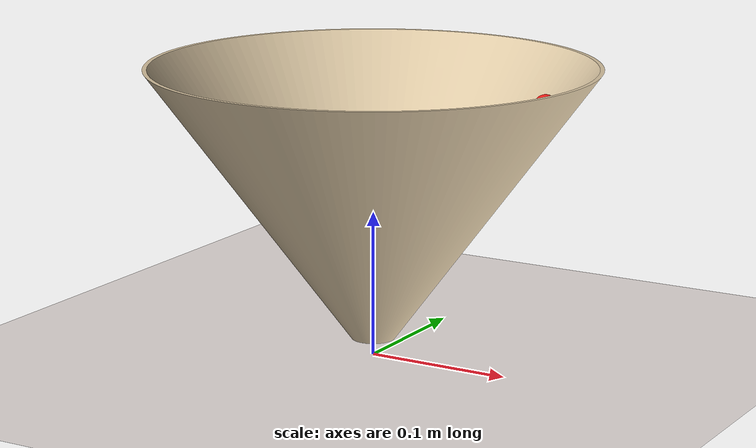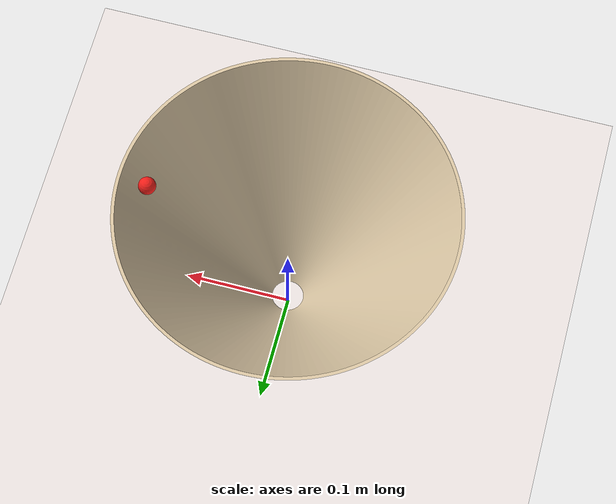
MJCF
<mujoco model="marble_in_funnel">
  <!-- Funnel R_top=0.15, R_bot=0.003 (jam), H=0.2. Est. jam z≈0.017 m -->
  <compiler angle="radian" coordinate="local" autolimits="true"/>
  <option timestep="0.001" gravity="0 0 -9.81" integrator="implicitfast"
          impratio="5" cone="elliptic" iterations="80"/>

  <visual>
    <headlight diffuse="0 0 0" ambient="0.50 0.48 0.55" specular="0 0 0"/>
    <rgba haze="0.94 0.91 0.90 1"/>
    <global azimuth="120" elevation="-15" offwidth="1920" offheight="1080" fovy="38"/>
    <quality shadowsize="8192" offsamples="8"/>
    <map shadowclip="6" shadowscale="0.7"/>
  </visual>

  <asset>
    <texture type="skybox" builtin="flat"
             rgb1="0.74 0.68 0.86" rgb2="0.74 0.68 0.86"
             width="512" height="512" mark="none" markrgb="0 0 0"/>
    <mesh name="funnel_shell" vertex="0.014820 0.000000 0.012000 0.014802 0.000727 0.012000 0.014749 0.001453 0.012000 0.014660 0.002175 0.012000 0.014535 0.002891 0.012000 0.014376 0.003601 0.012000 0.014182 0.004302 0.012000 0.013954 0.004993 0.012000 0.013692 0.005671 0.012000 0.013397 0.006336 0.012000 0.013070 0.006986 0.012000 0.012712 0.007619 0.012000 0.012322 0.008234 0.012000 0.011904 0.008828 0.012000 0.011456 0.009402 0.012000 0.010981 0.009953 0.012000 0.010479 0.010479 0.012000 0.009953 0.010981 0.012000 0.009402 0.011456 0.012000 0.008828 0.011904 0.012000 0.008234 0.012322 0.012000 0.007619 0.012712 0.012000 0.006986 0.013070 0.012000 0.006336 0.013397 0.012000 0.005671 0.013692 0.012000 0.004993 0.013954 0.012000 0.004302 0.014182 0.012000 0.003601 0.014376 0.012000 0.002891 0.014535 0.012000 0.002175 0.014660 0.012000 0.001453 0.014749 0.012000 0.000727 0.014802 0.012000 0.000000 0.014820 0.012000 -0.000727 0.014802 0.012000 -0.001453 0.014749 0.012000 -0.002175 0.014660 0.012000 -0.002891 0.014535 0.012000 -0.003601 0.014376 0.012000 -0.004302 0.014182 0.012000 -0.004993 0.013954 0.012000 -0.005671 0.013692 0.012000 -0.006336 0.013397 0.012000 -0.006986 0.013070 0.012000 -0.007619 0.012712 0.012000 -0.008234 0.012322 0.012000 -0.008828 0.011904 0.012000 -0.009402 0.011456 0.012000 -0.009953 0.010981 0.012000 -0.010479 0.010479 0.012000 -0.010981 0.009953 0.012000 -0.011456 0.009402 0.012000 -0.011904 0.008828 0.012000 -0.012322 0.008234 0.012000 -0.012712 0.007619 0.012000 -0.013070 0.006986 0.012000 -0.013397 0.006336 0.012000 -0.013692 0.005671 0.012000 -0.013954 0.004993 0.012000 -0.014182 0.004302 0.012000 -0.014376 0.003601 0.012000 -0.014535 0.002891 0.012000 -0.014660 0.002175 0.012000 -0.014749 0.001453 0.012000 -0.014802 0.000727 0.012000 -0.014820 0.000000 0.012000 -0.014802 -0.000727 0.012000 -0.014749 -0.001453 0.012000 -0.014660 -0.002175 0.012000 -0.014535 -0.002891 0.012000 -0.014376 -0.003601 0.012000 -0.014182 -0.004302 0.012000 -0.013954 -0.004993 0.012000 -0.013692 -0.005671 0.012000 -0.013397 -0.006336 0.012000 -0.013070 -0.006986 0.012000 -0.012712 -0.007619 0.012000 -0.012322 -0.008234 0.012000 -0.011904 -0.008828 0.012000 -0.011456 -0.009402 0.012000 -0.010981 -0.009953 0.012000 -0.010479 -0.010479 0.012000 -0.009953 -0.010981 0.012000 -0.009402 -0.011456 0.012000 -0.008828 -0.011904 0.012000 -0.008234 -0.012322 0.012000 -0.007619 -0.012712 0.012000 -0.006986 -0.013070 0.012000 -0.006336 -0.013397 0.012000 -0.005671 -0.013692 0.012000 -0.004993 -0.013954 0.012000 -0.004302 -0.014182 0.012000 -0.003601 -0.014376 0.012000 -0.002891 -0.014535 0.012000 -0.002175 -0.014660 0.012000 -0.001453 -0.014749 0.012000 -0.000727 -0.014802 0.012000 -0.000000 -0.014820 0.012000 0.000727 -0.014802 0.012000 0.001453 -0.014749 0.012000 0.002175 -0.014660 0.012000 0.002891 -0.014535 0.012000 0.003601 -0.014376 0.012000 0.004302 -0.014182 0.012000 0.004993 -0.013954 0.012000 0.005671 -0.013692 0.012000 0.006336 -0.013397 0.012000 0.006986 -0.013070 0.012000 0.007619 -0.012712 0.012000 0.008234 -0.012322 0.012000 0.008828 -0.011904 0.012000 0.009402 -0.011456 0.012000 0.009953 -0.010981 0.012000 0.010479 -0.010479 0.012000 0.010981 -0.009953 0.012000 0.011456 -0.009402 0.012000 0.011904 -0.008828 0.012000 0.012322 -0.008234 0.012000 0.012712 -0.007619 0.012000 0.013070 -0.006986 0.012000 0.013397 -0.006336 0.012000 0.013692 -0.005671 0.012000 0.013954 -0.004993 0.012000 0.014182 -0.004302 0.012000 0.014376 -0.003601 0.012000 0.014535 -0.002891 0.012000 0.014660 -0.002175 0.012000 0.014749 -0.001453 0.012000 0.014802 -0.000727 0.012000 0.019277 0.000000 0.018065 0.019254 0.000946 0.018065 0.019185 0.001890 0.018065 0.019069 0.002829 0.018065 0.018907 0.003761 0.018065 0.018700 0.004684 0.018065 0.018447 0.005596 0.018065 0.018151 0.006494 0.018065 0.017810 0.007377 0.018065 0.017427 0.008242 0.018065 0.017001 0.009087 0.018065 0.016535 0.009911 0.018065 0.016029 0.010710 0.018065 0.015484 0.011484 0.018065 0.014902 0.012229 0.018065 0.014284 0.012946 0.018065 0.013631 0.013631 0.018065 0.012946 0.014284 0.018065 0.012229 0.014902 0.018065 0.011484 0.015484 0.018065 0.010710 0.016029 0.018065 0.009911 0.016535 0.018065 0.009087 0.017001 0.018065 0.008242 0.017427 0.018065 0.007377 0.017810 0.018065 0.006494 0.018151 0.018065 0.005596 0.018447 0.018065 0.004684 0.018700 0.018065 0.003761 0.018907 0.018065 0.002829 0.019069 0.018065 0.001890 0.019185 0.018065 0.000946 0.019254 0.018065 0.000000 0.019277 0.018065 -0.000946 0.019254 0.018065 -0.001890 0.019185 0.018065 -0.002829 0.019069 0.018065 -0.003761 0.018907 0.018065 -0.004684 0.018700 0.018065 -0.005596 0.018447 0.018065 -0.006494 0.018151 0.018065 -0.007377 0.017810 0.018065 -0.008242 0.017427 0.018065 -0.009087 0.017001 0.018065 -0.009911 0.016535 0.018065 -0.010710 0.016029 0.018065 -0.011484 0.015484 0.018065 -0.012229 0.014902 0.018065 -0.012946 0.014284 0.018065 -0.013631 0.013631 0.018065 -0.014284 0.012946 0.018065 -0.014902 0.012229 0.018065 -0.015484 0.011484 0.018065 -0.016029 0.010710 0.018065 -0.016535 0.009911 0.018065 -0.017001 0.009087 0.018065 -0.017427 0.008242 0.018065 -0.017810 0.007377 0.018065 -0.018151 0.006494 0.018065 -0.018447 0.005596 0.018065 -0.018700 0.004684 0.018065 -0.018907 0.003761 0.018065 -0.019069 0.002829 0.018065 -0.019185 0.001890 0.018065 -0.019254 0.000946 0.018065 -0.019277 0.000000 0.018065 -0.019254 -0.000946 0.018065 -0.019185 -0.001890 0.018065 -0.019069 -0.002829 0.018065 -0.018907 -0.003761 0.018065 -0.018700 -0.004684 0.018065 -0.018447 -0.005596 0.018065 -0.018151 -0.006494 0.018065 -0.017810 -0.007377 0.018065 -0.017427 -0.008242 0.018065 -0.017001 -0.009087 0.018065 -0.016535 -0.009911 0.018065 -0.016029 -0.010710 0.018065 -0.015484 -0.011484 0.018065 -0.014902 -0.012229 0.018065 -0.014284 -0.012946 0.018065 -0.013631 -0.013631 0.018065 -0.012946 -0.014284 0.018065 -0.012229 -0.014902 0.018065 -0.011484 -0.015484 0.018065 -0.010710 -0.016029 0.018065 -0.009911 -0.016535 0.018065 -0.009087 -0.017001 0.018065 -0.008242 -0.017427 0.018065 -0.007377 -0.017810 0.018065 -0.006494 -0.018151 0.018065 -0.005596 -0.018447 0.018065 -0.004684 -0.018700 0.018065 -0.003761 -0.018907 0.018065 -0.002829 -0.019069 0.018065 -0.001890 -0.019185 0.018065 -0.000946 -0.019254 0.018065 -0.000000 -0.019277 0.018065 0.000946 -0.019254 0.018065 0.001890 -0.019185 0.018065 0.002829 -0.019069 0.018065 0.003761 -0.018907 0.018065 0.004684 -0.018700 0.018065 0.005596 -0.018447 0.018065 0.006494 -0.018151 0.018065 0.007377 -0.017810 0.018065 0.008242 -0.017427 0.018065 0.009087 -0.017001 0.018065 0.009911 -0.016535 0.018065 0.010710 -0.016029 0.018065 0.011484 -0.015484 0.018065 0.012229 -0.014902 0.018065 0.012946 -0.014284 0.018065 0.013631 -0.013631 0.018065 0.014284 -0.012946 0.018065 0.014902 -0.012229 0.018065 0.015484 -0.011484 0.018065 0.016029 -0.010710 0.018065 0.016535 -0.009911 0.018065 0.017001 -0.009087 0.018065 0.017427 -0.008242 0.018065 0.017810 -0.007377 0.018065 0.018151 -0.006494 0.018065 0.018447 -0.005596 0.018065 0.018700 -0.004684 0.018065 0.018907 -0.003761 0.018065 0.019069 -0.002829 0.018065 0.019185 -0.001890 0.018065 0.019254 -0.000946 0.018065 0.023735 0.000000 0.024129 0.023706 0.001165 0.024129 0.023621 0.002326 0.024129 0.023478 0.003483 0.024129 0.023279 0.004630 0.024129 0.023024 0.005767 0.024129 0.022713 0.006890 0.024129 0.022347 0.007996 0.024129 0.021928 0.009083 0.024129 0.021456 0.010148 0.024129 0.020932 0.011189 0.024129 0.020358 0.012202 0.024129 0.019735 0.013186 0.024129 0.019064 0.014139 0.024129 0.018347 0.015057 0.024129 0.017586 0.015939 0.024129 0.016783 0.016783 0.024129 0.015939 0.017586 0.024129 0.015057 0.018347 0.024129 0.014139 0.019064 0.024129 0.013186 0.019735 0.024129 0.012202 0.020358 0.024129 0.011189 0.020932 0.024129 0.010148 0.021456 0.024129 0.009083 0.021928 0.024129 0.007996 0.022347 0.024129 0.006890 0.022713 0.024129 0.005767 0.023024 0.024129 0.004630 0.023279 0.024129 0.003483 0.023478 0.024129 0.002326 0.023621 0.024129 0.001165 0.023706 0.024129 0.000000 0.023735 0.024129 -0.001165 0.023706 0.024129 -0.002326 0.023621 0.024129 -0.003483 0.023478 0.024129 -0.004630 0.023279 0.024129 -0.005767 0.023024 0.024129 -0.006890 0.022713 0.024129 -0.007996 0.022347 0.024129 -0.009083 0.021928 0.024129 -0.010148 0.021456 0.024129 -0.011189 0.020932 0.024129 -0.012202 0.020358 0.024129 -0.013186 0.019735 0.024129 -0.014139 0.019064 0.024129 -0.015057 0.018347 0.024129 -0.015939 0.017586 0.024129 -0.016783 0.016783 0.024129 -0.017586 0.015939 0.024129 -0.018347 0.015057 0.024129 -0.019064 0.014139 0.024129 -0.019735 0.013186 0.024129 -0.020358 0.012202 0.024129 -0.020932 0.011189 0.024129 -0.021456 0.010148 0.024129 -0.021928 0.009083 0.024129 -0.022347 0.007996 0.024129 -0.022713 0.006890 0.024129 -0.023024 0.005767 0.024129 -0.023279 0.004630 0.024129 -0.023478 0.003483 0.024129 -0.023621 0.002326 0.024129 -0.023706 0.001165 0.024129 -0.023735 0.000000 0.024129 -0.023706 -0.001165 0.024129 -0.023621 -0.002326 0.024129 -0.023478 -0.003483 0.024129 -0.023279 -0.004630 0.024129 -0.023024 -0.005767 0.024129 -0.022713 -0.006890 0.024129 -0.022347 -0.007996 0.024129 -0.021928 -0.009083 0.024129 -0.021456 -0.010148 0.024129 -0.020932 -0.011189 0.024129 -0.020358 -0.012202 0.024129 -0.019735 -0.013186 0.024129 -0.019064 -0.014139 0.024129 -0.018347 -0.015057 0.024129 -0.017586 -0.015939 0.024129 -0.016783 -0.016783 0.024129 -0.015939 -0.017586 0.024129 -0.015057 -0.018347 0.024129 -0.014139 -0.019064 0.024129 -0.013186 -0.019735 0.024129 -0.012202 -0.020358 0.024129 -0.011189 -0.020932 0.024129 -0.010148 -0.021456 0.024129 -0.009083 -0.021928 0.024129 -0.007996 -0.022347 0.024129 -0.006890 -0.022713 0.024129 -0.005767 -0.023024 0.024129 -0.004630 -0.023279 0.024129 -0.003483 -0.023478 0.024129 -0.002326 -0.023621 0.024129 -0.001165 -0.023706 0.024129 -0.000000 -0.023735 0.024129 0.001165 -0.023706 0.024129 0.002326 -0.023621 0.024129 0.003483 -0.023478 0.024129 0.004630 -0.023279 0.024129 0.005767 -0.023024 0.024129 0.006890 -0.022713 0.024129 0.007996 -0.022347 0.024129 0.009083 -0.021928 0.024129 0.010148 -0.021456 0.024129 0.011189 -0.020932 0.024129 0.012202 -0.020358 0.024129 0.013186 -0.019735 0.024129 0.014139 -0.019064 0.024129 0.015057 -0.018347 0.024129 0.015939 -0.017586 0.024129 0.016783 -0.016783 0.024129 0.017586 -0.015939 0.024129 0.018347 -0.015057 0.024129 0.019064 -0.014139 0.024129 0.019735 -0.013186 0.024129 0.020358 -0.012202 0.024129 0.020932 -0.011189 0.024129 0.021456 -0.010148 0.024129 0.021928 -0.009083 0.024129 0.022347 -0.007996 0.024129 0.022713 -0.006890 0.024129 0.023024 -0.005767 0.024129 0.023279 -0.004630 0.024129 0.023478 -0.003483 0.024129 0.023621 -0.002326 0.024129 0.023706 -0.001165 0.024129 0.028192 0.000000 0.030194 0.028158 0.001383 0.030194 0.028057 0.002763 0.030194 0.027887 0.004137 0.030194 0.027651 0.005500 0.030194 0.027347 0.006850 0.030194 0.026978 0.008184 0.030194 0.026544 0.009498 0.030194 0.026046 0.010789 0.030194 0.025485 0.012054 0.030194 0.024863 0.013290 0.030194 0.024181 0.014494 0.030194 0.023441 0.015663 0.030194 0.022644 0.016794 0.030194 0.021793 0.017885 0.030194 0.020889 0.018933 0.030194 0.019935 0.019935 0.030194 0.018933 0.020889 0.030194 0.017885 0.021793 0.030194 0.016794 0.022644 0.030194 0.015663 0.023441 0.030194 0.014494 0.024181 0.030194 0.013290 0.024863 0.030194 0.012054 0.025485 0.030194 0.010789 0.026046 0.030194 0.009498 0.026544 0.030194 0.008184 0.026978 0.030194 0.006850 0.027347 0.030194 0.005500 0.027651 0.030194 0.004137 0.027887 0.030194 0.002763 0.028057 0.030194 0.001383 0.028158 0.030194 0.000000 0.028192 0.030194 -0.001383 0.028158 0.030194 -0.002763 0.028057 0.030194 -0.004137 0.027887 0.030194 -0.005500 0.027651 0.030194 -0.006850 0.027347 0.030194 -0.008184 0.026978 0.030194 -0.009498 0.026544 0.030194 -0.010789 0.026046 0.030194 -0.012054 0.025485 0.030194 -0.013290 0.024863 0.030194 -0.014494 0.024181 0.030194 -0.015663 0.023441 0.030194 -0.016794 0.022644 0.030194 -0.017885 0.021793 0.030194 -0.018933 0.020889 0.030194 -0.019935 0.019935 0.030194 -0.020889 0.018933 0.030194 -0.021793 0.017885 0.030194 -0.022644 0.016794 0.030194 -0.023441 0.015663 0.030194 -0.024181 0.014494 0.030194 -0.024863 0.013290 0.030194 -0.025485 0.012054 0.030194 -0.026046 0.010789 0.030194 -0.026544 0.009498 0.030194 -0.026978 0.008184 0.030194 -0.027347 0.006850 0.030194 -0.027651 0.005500 0.030194 -0.027887 0.004137 0.030194 -0.028057 0.002763 0.030194 -0.028158 0.001383 0.030194 -0.028192 0.000000 0.030194 -0.028158 -0.001383 0.030194 -0.028057 -0.002763 0.030194 -0.027887 -0.004137 0.030194 -0.027651 -0.005500 0.030194 -0.027347 -0.006850 0.030194 -0.026978 -0.008184 0.030194 -0.026544 -0.009498 0.030194 -0.026046 -0.010789 0.030194 -0.025485 -0.012054 0.030194 -0.024863 -0.013290 0.030194 -0.024181 -0.014494 0.030194 -0.023441 -0.015663 0.030194 -0.022644 -0.016794 0.030194 -0.021793 -0.017885 0.030194 -0.020889 -0.018933 0.030194 -0.019935 -0.019935 0.030194 -0.018933 -0.020889 0.030194 -0.017885 -0.021793 0.030194 -0.016794 -0.022644 0.030194 -0.015663 -0.023441 0.030194 -0.014494 -0.024181 0.030194 -0.013290 -0.024863 0.030194 -0.012054 -0.025485 0.030194 -0.010789 -0.026046 0.030194 -0.009498 -0.026544 0.030194 -0.008184 -0.026978 0.030194 -0.006850 -0.027347 0.030194 -0.005500 -0.027651 0.030194 -0.004137 -0.027887 0.030194 -0.002763 -0.028057 0.030194 -0.001383 -0.028158 0.030194 -0.000000 -0.028192 0.030194 0.001383 -0.028158 0.030194 0.002763 -0.028057 0.030194 0.004137 -0.027887 0.030194 0.005500 -0.027651 0.030194 0.006850 -0.027347 0.030194 0.008184 -0.026978 0.030194 0.009498 -0.026544 0.030194 0.010789 -0.026046 0.030194 0.012054 -0.025485 0.030194 0.013290 -0.024863 0.030194 0.014494 -0.024181 0.030194 0.015663 -0.023441 0.030194 0.016794 -0.022644 0.030194 0.017885 -0.021793 0.030194 0.018933 -0.020889 0.030194 0.019935 -0.019935 0.030194 0.020889 -0.018933 0.030194 0.021793 -0.017885 0.030194 0.022644 -0.016794 0.030194 0.023441 -0.015663 0.030194 0.024181 -0.014494 0.030194 0.024863 -0.013290 0.030194 0.025485 -0.012054 0.030194 0.026046 -0.010789 0.030194 0.026544 -0.009498 0.030194 0.026978 -0.008184 0.030194 0.027347 -0.006850 0.030194 0.027651 -0.005500 0.030194 0.027887 -0.004137 0.030194 0.028057 -0.002763 0.030194 0.028158 -0.001383 0.030194 0.032650 0.000000 0.036258 0.032610 0.001602 0.036258 0.032492 0.003200 0.036258 0.032296 0.004791 0.036258 0.032022 0.006370 0.036258 0.031671 0.007933 0.036258 0.031244 0.009478 0.036258 0.030741 0.010999 0.036258 0.030164 0.012494 0.036258 0.029515 0.013960 0.036258 0.028794 0.015391 0.036258 0.028005 0.016785 0.036258 0.027147 0.018139 0.036258 0.026224 0.019449 0.036258 0.025239 0.020713 0.036258 0.024192 0.021926 0.036258 0.023087 0.023087 0.036258 0.021926 0.024192 0.036258 0.020713 0.025239 0.036258 0.019449 0.026224 0.036258 0.018139 0.027147 0.036258 0.016785 0.028005 0.036258 0.015391 0.028794 0.036258 0.013960 0.029515 0.036258 0.012494 0.030164 0.036258 0.010999 0.030741 0.036258 0.009478 0.031244 0.036258 0.007933 0.031671 0.036258 0.006370 0.032022 0.036258 0.004791 0.032296 0.036258 0.003200 0.032492 0.036258 0.001602 0.032610 0.036258 0.000000 0.032650 0.036258 -0.001602 0.032610 0.036258 -0.003200 0.032492 0.036258 -0.004791 0.032296 0.036258 -0.006370 0.032022 0.036258 -0.007933 0.031671 0.036258 -0.009478 0.031244 0.036258 -0.010999 0.030741 0.036258 -0.012494 0.030164 0.036258 -0.013960 0.029515 0.036258 -0.015391 0.028794 0.036258 -0.016785 0.028005 0.036258 -0.018139 0.027147 0.036258 -0.019449 0.026224 0.036258 -0.020713 0.025239 0.036258 -0.021926 0.024192 0.036258 -0.023087 0.023087 0.036258 -0.024192 0.021926 0.036258 -0.025239 0.020713 0.036258 -0.026224 0.019449 0.036258 -0.027147 0.018139 0.036258 -0.028005 0.016785 0.036258 -0.028794 0.015391 0.036258 -0.029515 0.013960 0.036258 -0.030164 0.012494 0.036258 -0.030741 0.010999 0.036258 -0.031244 0.009478 0.036258 -0.031671 0.007933 0.036258 -0.032022 0.006370 0.036258 -0.032296 0.004791 0.036258 -0.032492 0.003200 0.036258 -0.032610 0.001602 0.036258 -0.032650 0.000000 0.036258 -0.032610 -0.001602 0.036258 -0.032492 -0.003200 0.036258 -0.032296 -0.004791 0.036258 -0.032022 -0.006370 0.036258 -0.031671 -0.007933 0.036258 -0.031244 -0.009478 0.036258 -0.030741 -0.010999 0.036258 -0.030164 -0.012494 0.036258 -0.029515 -0.013960 0.036258 -0.028794 -0.015391 0.036258 -0.028005 -0.016785 0.036258 -0.027147 -0.018139 0.036258 -0.026224 -0.019449 0.036258 -0.025239 -0.020713 0.036258 -0.024192 -0.021926 0.036258 -0.023087 -0.023087 0.036258 -0.021926 -0.024192 0.036258 -0.020713 -0.025239 0.036258 -0.019449 -0.026224 0.036258 -0.018139 -0.027147 0.036258 -0.016785 -0.028005 0.036258 -0.015391 -0.028794 0.036258 -0.013960 -0.029515 0.036258 -0.012494 -0.030164 0.036258 -0.010999 -0.030741 0.036258 -0.009478 -0.031244 0.036258 -0.007933 -0.031671 0.036258 -0.006370 -0.032022 0.036258 -0.004791 -0.032296 0.036258 -0.003200 -0.032492 0.036258 -0.001602 -0.032610 0.036258 -0.000000 -0.032650 0.036258 0.001602 -0.032610 0.036258 0.003200 -0.032492 0.036258 0.004791 -0.032296 0.036258 0.006370 -0.032022 0.036258 0.007933 -0.031671 0.036258 0.009478 -0.031244 0.036258 0.010999 -0.030741 0.036258 0.012494 -0.030164 0.036258 0.013960 -0.029515 0.036258 0.015391 -0.028794 0.036258 0.016785 -0.028005 0.036258 0.018139 -0.027147 0.036258 0.019449 -0.026224 0.036258 0.020713 -0.025239 0.036258 0.021926 -0.024192 0.036258 0.023087 -0.023087 0.036258 0.024192 -0.021926 0.036258 0.025239 -0.020713 0.036258 0.026224 -0.019449 0.036258 0.027147 -0.018139 0.036258 0.028005 -0.016785 0.036258 0.028794 -0.015391 0.036258 0.029515 -0.013960 0.036258 0.030164 -0.012494 0.036258 0.030741 -0.010999 0.036258 0.031244 -0.009478 0.036258 0.031671 -0.007933 0.036258 0.032022 -0.006370 0.036258 0.032296 -0.004791 0.036258 0.032492 -0.003200 0.036258 0.032610 -0.001602 0.036258 0.037107 0.000000 0.042323 0.037062 0.001821 0.042323 0.036928 0.003637 0.042323 0.036705 0.005445 0.042323 0.036394 0.007239 0.042323 0.035995 0.009016 0.042323 0.035509 0.010772 0.042323 0.034938 0.012501 0.042323 0.034282 0.014200 0.042323 0.033544 0.015865 0.042323 0.032726 0.017492 0.042323 0.031828 0.019077 0.042323 0.030853 0.020616 0.042323 0.029805 0.022105 0.042323 0.028684 0.023540 0.042323 0.027495 0.024920 0.042323 0.026239 0.026239 0.042323 0.024920 0.027495 0.042323 0.023540 0.028684 0.042323 0.022105 0.029805 0.042323 0.020616 0.030853 0.042323 0.019077 0.031828 0.042323 0.017492 0.032726 0.042323 0.015865 0.033544 0.042323 0.014200 0.034282 0.042323 0.012501 0.034938 0.042323 0.010772 0.035509 0.042323 0.009016 0.035995 0.042323 0.007239 0.036394 0.042323 0.005445 0.036705 0.042323 0.003637 0.036928 0.042323 0.001821 0.037062 0.042323 0.000000 0.037107 0.042323 -0.001821 0.037062 0.042323 -0.003637 0.036928 0.042323 -0.005445 0.036705 0.042323 -0.007239 0.036394 0.042323 -0.009016 0.035995 0.042323 -0.010772 0.035509 0.042323 -0.012501 0.034938 0.042323 -0.014200 0.034282 0.042323 -0.015865 0.033544 0.042323 -0.017492 0.032726 0.042323 -0.019077 0.031828 0.042323 -0.020616 0.030853 0.042323 -0.022105 0.029805 0.042323 -0.023540 0.028684 0.042323 -0.024920 0.027495 0.042323 -0.026239 0.026239 0.042323 -0.027495 0.024920 0.042323 -0.028684 0.023540 0.042323 -0.029805 0.022105 0.042323 -0.030853 0.020616 0.042323 -0.031828 0.019077 0.042323 -0.032726 0.017492 0.042323 -0.033544 0.015865 0.042323 -0.034282 0.014200 0.042323 -0.034938 0.012501 0.042323 -0.035509 0.010772 0.042323 -0.035995 0.009016 0.042323 -0.036394 0.007239 0.042323 -0.036705 0.005445 0.042323 -0.036928 0.003637 0.042323 -0.037062 0.001821 0.042323 -0.037107 0.000000 0.042323 -0.037062 -0.001821 0.042323 -0.036928 -0.003637 0.042323 -0.036705 -0.005445 0.042323 -0.036394 -0.007239 0.042323 -0.035995 -0.009016 0.042323 -0.035509 -0.010772 0.042323 -0.034938 -0.012501 0.042323 -0.034282 -0.014200 0.042323 -0.033544 -0.015865 0.042323 -0.032726 -0.017492 0.042323 -0.031828 -0.019077 0.042323 -0.030853 -0.020616 0.042323 -0.029805 -0.022105 0.042323 -0.028684 -0.023540 0.042323 -0.027495 -0.024920 0.042323 -0.026239 -0.026239 0.042323 -0.024920 -0.027495 0.042323 -0.023540 -0.028684 0.042323 -0.022105 -0.029805 0.042323 -0.020616 -0.030853 0.042323 -0.019077 -0.031828 0.042323 -0.017492 -0.032726 0.042323 -0.015865 -0.033544 0.042323 -0.014200 -0.034282 0.042323 -0.012501 -0.034938 0.042323 -0.010772 -0.035509 0.042323 -0.009016 -0.035995 0.042323 -0.007239 -0.036394 0.042323 -0.005445 -0.036705 0.042323 -0.003637 -0.036928 0.042323 -0.001821 -0.037062 0.042323 -0.000000 -0.037107 0.042323 0.001821 -0.037062 0.042323 0.003637 -0.036928 0.042323 0.005445 -0.036705 0.042323 0.007239 -0.036394 0.042323 0.009016 -0.035995 0.042323 0.010772 -0.035509 0.042323 0.012501 -0.034938 0.042323 0.014200 -0.034282 0.042323 0.015865 -0.033544 0.042323 0.017492 -0.032726 0.042323 0.019077 -0.031828 0.042323 0.020616 -0.030853 0.042323 0.022105 -0.029805 0.042323 0.023540 -0.028684 0.042323 0.024920 -0.027495 0.042323 0.026239 -0.026239 0.042323 0.027495 -0.024920 0.042323 0.028684 -0.023540 0.042323 0.029805 -0.022105 0.042323 0.030853 -0.020616 0.042323 0.031828 -0.019077 0.042323 0.032726 -0.017492 0.042323 0.033544 -0.015865 0.042323 0.034282 -0.014200 0.042323 0.034938 -0.012501 0.042323 0.035509 -0.010772 0.042323 0.035995 -0.009016 0.042323 0.036394 -0.007239 0.042323 0.036705 -0.005445 0.042323 0.036928 -0.003637 0.042323 0.037062 -0.001821 0.042323 0.041565 0.000000 0.048387 0.041514 0.002039 0.048387 0.041364 0.004074 0.048387 0.041115 0.006099 0.048387 0.040766 0.008109 0.048387 0.040319 0.010099 0.048387 0.039775 0.012066 0.048387 0.039135 0.014003 0.048387 0.038401 0.015906 0.048387 0.037574 0.017771 0.048387 0.036657 0.019593 0.048387 0.035651 0.021368 0.048387 0.034560 0.023092 0.048387 0.033385 0.024760 0.048387 0.032130 0.026368 0.048387 0.030797 0.027913 0.048387 0.029391 0.029391 0.048387 0.027913 0.030797 0.048387 0.026368 0.032130 0.048387 0.024760 0.033385 0.048387 0.023092 0.034560 0.048387 0.021368 0.035651 0.048387 0.019593 0.036657 0.048387 0.017771 0.037574 0.048387 0.015906 0.038401 0.048387 0.014003 0.039135 0.048387 0.012066 0.039775 0.048387 0.010099 0.040319 0.048387 0.008109 0.040766 0.048387 0.006099 0.041115 0.048387 0.004074 0.041364 0.048387 0.002039 0.041514 0.048387 0.000000 0.041565 0.048387 -0.002039 0.041514 0.048387 -0.004074 0.041364 0.048387 -0.006099 0.041115 0.048387 -0.008109 0.040766 0.048387 -0.010099 0.040319 0.048387 -0.012066 0.039775 0.048387 -0.014003 0.039135 0.048387 -0.015906 0.038401 0.048387 -0.017771 0.037574 0.048387 -0.019593 0.036657 0.048387 -0.021368 0.035651 0.048387 -0.023092 0.034560 0.048387 -0.024760 0.033385 0.048387 -0.026368 0.032130 0.048387 -0.027913 0.030797 0.048387 -0.029391 0.029391 0.048387 -0.030797 0.027913 0.048387 -0.032130 0.026368 0.048387 -0.033385 0.024760 0.048387 -0.034560 0.023092 0.048387 -0.035651 0.021368 0.048387 -0.036657 0.019593 0.048387 -0.037574 0.017771 0.048387 -0.038401 0.015906 0.048387 -0.039135 0.014003 0.048387 -0.039775 0.012066 0.048387 -0.040319 0.010099 0.048387 -0.040766 0.008109 0.048387 -0.041115 0.006099 0.048387 -0.041364 0.004074 0.048387 -0.041514 0.002039 0.048387 -0.041565 0.000000 0.048387 -0.041514 -0.002039 0.048387 -0.041364 -0.004074 0.048387 -0.041115 -0.006099 0.048387 -0.040766 -0.008109 0.048387 -0.040319 -0.010099 0.048387 -0.039775 -0.012066 0.048387 -0.039135 -0.014003 0.048387 -0.038401 -0.015906 0.048387 -0.037574 -0.017771 0.048387 -0.036657 -0.019593 0.048387 -0.035651 -0.021368 0.048387 -0.034560 -0.023092 0.048387 -0.033385 -0.024760 0.048387 -0.032130 -0.026368 0.048387 -0.030797 -0.027913 0.048387 -0.029391 -0.029391 0.048387 -0.027913 -0.030797 0.048387 -0.026368 -0.032130 0.048387 -0.024760 -0.033385 0.048387 -0.023092 -0.034560 0.048387 -0.021368 -0.035651 0.048387 -0.019593 -0.036657 0.048387 -0.017771 -0.037574 0.048387 -0.015906 -0.038401 0.048387 -0.014003 -0.039135 0.048387 -0.012066 -0.039775 0.048387 -0.010099 -0.040319 0.048387 -0.008109 -0.040766 0.048387 -0.006099 -0.041115 0.048387 -0.004074 -0.041364 0.048387 -0.002039 -0.041514 0.048387 -0.000000 -0.041565 0.048387 0.002039 -0.041514 0.048387 0.004074 -0.041364 0.048387 0.006099 -0.041115 0.048387 0.008109 -0.040766 0.048387 0.010099 -0.040319 0.048387 0.012066 -0.039775 0.048387 0.014003 -0.039135 0.048387 0.015906 -0.038401 0.048387 0.017771 -0.037574 0.048387 0.019593 -0.036657 0.048387 0.021368 -0.035651 0.048387 0.023092 -0.034560 0.048387 0.024760 -0.033385 0.048387 0.026368 -0.032130 0.048387 0.027913 -0.030797 0.048387 0.029391 -0.029391 0.048387 0.030797 -0.027913 0.048387 0.032130 -0.026368 0.048387 0.033385 -0.024760 0.048387 0.034560 -0.023092 0.048387 0.035651 -0.021368 0.048387 0.036657 -0.019593 0.048387 0.037574 -0.017771 0.048387 0.038401 -0.015906 0.048387 0.039135 -0.014003 0.048387 0.039775 -0.012066 0.048387 0.040319 -0.010099 0.048387 0.040766 -0.008109 0.048387 0.041115 -0.006099 0.048387 0.041364 -0.004074 0.048387 0.041514 -0.002039 0.048387 0.046022 0.000000 0.054452 0.045967 0.002258 0.054452 0.045800 0.004511 0.054452 0.045524 0.006753 0.054452 0.045138 0.008978 0.054452 0.044643 0.011182 0.054452 0.044040 0.013359 0.054452 0.043332 0.015504 0.054452 0.042519 0.017612 0.054452 0.041603 0.019677 0.054452 0.040588 0.021695 0.054452 0.039474 0.023660 0.054452 0.038266 0.025568 0.054452 0.036965 0.027415 0.054452 0.035575 0.029196 0.054452 0.034100 0.030906 0.054452 0.032542 0.032542 0.054452 0.030906 0.034100 0.054452 0.029196 0.035575 0.054452 0.027415 0.036965 0.054452 0.025568 0.038266 0.054452 0.023660 0.039474 0.054452 0.021695 0.040588 0.054452 0.019677 0.041603 0.054452 0.017612 0.042519 0.054452 0.015504 0.043332 0.054452 0.013359 0.044040 0.054452 0.011182 0.044643 0.054452 0.008978 0.045138 0.054452 0.006753 0.045524 0.054452 0.004511 0.045800 0.054452 0.002258 0.045967 0.054452 0.000000 0.046022 0.054452 -0.002258 0.045967 0.054452 -0.004511 0.045800 0.054452 -0.006753 0.045524 0.054452 -0.008978 0.045138 0.054452 -0.011182 0.044643 0.054452 -0.013359 0.044040 0.054452 -0.015504 0.043332 0.054452 -0.017612 0.042519 0.054452 -0.019677 0.041603 0.054452 -0.021695 0.040588 0.054452 -0.023660 0.039474 0.054452 -0.025568 0.038266 0.054452 -0.027415 0.036965 0.054452 -0.029196 0.035575 0.054452 -0.030906 0.034100 0.054452 -0.032542 0.032542 0.054452 -0.034100 0.030906 0.054452 -0.035575 0.029196 0.054452 -0.036965 0.027415 0.054452 -0.038266 0.025568 0.054452 -0.039474 0.023660 0.054452 -0.040588 0.021695 0.054452 -0.041603 0.019677 0.054452 -0.042519 0.017612 0.054452 -0.043332 0.015504 0.054452 -0.044040 0.013359 0.054452 -0.044643 0.011182 0.054452 -0.045138 0.008978 0.054452 -0.045524 0.006753 0.054452 -0.045800 0.004511 0.054452 -0.045967 0.002258 0.054452 -0.046022 0.000000 0.054452 -0.045967 -0.002258 0.054452 -0.045800 -0.004511 0.054452 -0.045524 -0.006753 0.054452 -0.045138 -0.008978 0.054452 -0.044643 -0.011182 0.054452 -0.044040 -0.013359 0.054452 -0.043332 -0.015504 0.054452 -0.042519 -0.017612 0.054452 -0.041603 -0.019677 0.054452 -0.040588 -0.021695 0.054452 -0.039474 -0.023660 0.054452 -0.038266 -0.025568 0.054452 -0.036965 -0.027415 0.054452 -0.035575 -0.029196 0.054452 -0.034100 -0.030906 0.054452 -0.032542 -0.032542 0.054452 -0.030906 -0.034100 0.054452 -0.029196 -0.035575 0.054452 -0.027415 -0.036965 0.054452 -0.025568 -0.038266 0.054452 -0.023660 -0.039474 0.054452 -0.021695 -0.040588 0.054452 -0.019677 -0.041603 0.054452 -0.017612 -0.042519 0.054452 -0.015504 -0.043332 0.054452 -0.013359 -0.044040 0.054452 -0.011182 -0.044643 0.054452 -0.008978 -0.045138 0.054452 -0.006753 -0.045524 0.054452 -0.004511 -0.045800 0.054452 -0.002258 -0.045967 0.054452 -0.000000 -0.046022 0.054452 0.002258 -0.045967 0.054452 0.004511 -0.045800 0.054452 0.006753 -0.045524 0.054452 0.008978 -0.045138 0.054452 0.011182 -0.044643 0.054452 0.013359 -0.044040 0.054452 0.015504 -0.043332 0.054452 0.017612 -0.042519 0.054452 0.019677 -0.041603 0.054452 0.021695 -0.040588 0.054452 0.023660 -0.039474 0.054452 0.025568 -0.038266 0.054452 0.027415 -0.036965 0.054452 0.029196 -0.035575 0.054452 0.030906 -0.034100 0.054452 0.032542 -0.032542 0.054452 0.034100 -0.030906 0.054452 0.035575 -0.029196 0.054452 0.036965 -0.027415 0.054452 0.038266 -0.025568 0.054452 0.039474 -0.023660 0.054452 0.040588 -0.021695 0.054452 0.041603 -0.019677 0.054452 0.042519 -0.017612 0.054452 0.043332 -0.015504 0.054452 0.044040 -0.013359 0.054452 0.044643 -0.011182 0.054452 0.045138 -0.008978 0.054452 0.045524 -0.006753 0.054452 0.045800 -0.004511 0.054452 0.045967 -0.002258 0.054452 0.050479 0.000000 0.060516 0.050419 0.002477 0.060516 0.050236 0.004948 0.060516 0.049933 0.007407 0.060516 0.049509 0.009848 0.060516 0.048967 0.012265 0.060516 0.048306 0.014653 0.060516 0.047529 0.017006 0.060516 0.046637 0.019318 0.060516 0.045633 0.021583 0.060516 0.044519 0.023796 0.060516 0.043298 0.025952 0.060516 0.041972 0.028045 0.060516 0.040545 0.030071 0.060516 0.039021 0.032024 0.060516 0.037403 0.033900 0.060516 0.035694 0.035694 0.060516 0.033900 0.037403 0.060516 0.032024 0.039021 0.060516 0.030071 0.040545 0.060516 0.028045 0.041972 0.060516 0.025952 0.043298 0.060516 0.023796 0.044519 0.060516 0.021583 0.045633 0.060516 0.019318 0.046637 0.060516 0.017006 0.047529 0.060516 0.014653 0.048306 0.060516 0.012265 0.048967 0.060516 0.009848 0.049509 0.060516 0.007407 0.049933 0.060516 0.004948 0.050236 0.060516 0.002477 0.050419 0.060516 0.000000 0.050479 0.060516 -0.002477 0.050419 0.060516 -0.004948 0.050236 0.060516 -0.007407 0.049933 0.060516 -0.009848 0.049509 0.060516 -0.012265 0.048967 0.060516 -0.014653 0.048306 0.060516 -0.017006 0.047529 0.060516 -0.019318 0.046637 0.060516 -0.021583 0.045633 0.060516 -0.023796 0.044519 0.060516 -0.025952 0.043298 0.060516 -0.028045 0.041972 0.060516 -0.030071 0.040545 0.060516 -0.032024 0.039021 0.060516 -0.033900 0.037403 0.060516 -0.035694 0.035694 0.060516 -0.037403 0.033900 0.060516 -0.039021 0.032024 0.060516 -0.040545 0.030071 0.060516 -0.041972 0.028045 0.060516 -0.043298 0.025952 0.060516 -0.044519 0.023796 0.060516 -0.045633 0.021583 0.060516 -0.046637 0.019318 0.060516 -0.047529 0.017006 0.060516 -0.048306 0.014653 0.060516 -0.048967 0.012265 0.060516 -0.049509 0.009848 0.060516 -0.049933 0.007407 0.060516 -0.050236 0.004948 0.060516 -0.050419 0.002477 0.060516 -0.050479 0.000000 0.060516 -0.050419 -0.002477 0.060516 -0.050236 -0.004948 0.060516 -0.049933 -0.007407 0.060516 -0.049509 -0.009848 0.060516 -0.048967 -0.012265 0.060516 -0.048306 -0.014653 0.060516 -0.047529 -0.017006 0.060516 -0.046637 -0.019318 0.060516 -0.045633 -0.021583 0.060516 -0.044519 -0.023796 0.060516 -0.043298 -0.025952 0.060516 -0.041972 -0.028045 0.060516 -0.040545 -0.030071 0.060516 -0.039021 -0.032024 0.060516 -0.037403 -0.033900 0.060516 -0.035694 -0.035694 0.060516 -0.033900 -0.037403 0.060516 -0.032024 -0.039021 0.060516 -0.030071 -0.040545 0.060516 -0.028045 -0.041972 0.060516 -0.025952 -0.043298 0.060516 -0.023796 -0.044519 0.060516 -0.021583 -0.045633 0.060516 -0.019318 -0.046637 0.060516 -0.017006 -0.047529 0.060516 -0.014653 -0.048306 0.060516 -0.012265 -0.048967 0.060516 -0.009848 -0.049509 0.060516 -0.007407 -0.049933 0.060516 -0.004948 -0.050236 0.060516 -0.002477 -0.050419 0.060516 -0.000000 -0.050479 0.060516 0.002477 -0.050419 0.060516 0.004948 -0.050236 0.060516 0.007407 -0.049933 0.060516 0.009848 -0.049509 0.060516 0.012265 -0.048967 0.060516 0.014653 -0.048306 0.060516 0.017006 -0.047529 0.060516 0.019318 -0.046637 0.060516 0.021583 -0.045633 0.060516 0.023796 -0.044519 0.060516 0.025952 -0.043298 0.060516 0.028045 -0.041972 0.060516 0.030071 -0.040545 0.060516 0.032024 -0.039021 0.060516 0.033900 -0.037403 0.060516 0.035694 -0.035694 0.060516 0.037403 -0.033900 0.060516 0.039021 -0.032024 0.060516 0.040545 -0.030071 0.060516 0.041972 -0.028045 0.060516 0.043298 -0.025952 0.060516 0.044519 -0.023796 0.060516 0.045633 -0.021583 0.060516 0.046637 -0.019318 0.060516 0.047529 -0.017006 0.060516 0.048306 -0.014653 0.060516 0.048967 -0.012265 0.060516 0.049509 -0.009848 0.060516 0.049933 -0.007407 0.060516 0.050236 -0.004948 0.060516 0.050419 -0.002477 0.060516 0.054937 0.000000 0.066581 0.054871 0.002696 0.066581 0.054672 0.005385 0.066581 0.054342 0.008061 0.066581 0.053881 0.010718 0.066581 0.053290 0.013349 0.066581 0.052571 0.015947 0.066581 0.051725 0.018508 0.066581 0.050755 0.021023 0.066581 0.049662 0.023488 0.066581 0.048450 0.025897 0.066581 0.047121 0.028243 0.066581 0.045678 0.030521 0.066581 0.044126 0.032726 0.066581 0.042467 0.034852 0.066581 0.040705 0.036893 0.066581 0.038846 0.038846 0.066581 0.036893 0.040705 0.066581 0.034852 0.042467 0.066581 0.032726 0.044126 0.066581 0.030521 0.045678 0.066581 0.028243 0.047121 0.066581 0.025897 0.048450 0.066581 0.023488 0.049662 0.066581 0.021023 0.050755 0.066581 0.018508 0.051725 0.066581 0.015947 0.052571 0.066581 0.013349 0.053290 0.066581 0.010718 0.053881 0.066581 0.008061 0.054342 0.066581 0.005385 0.054672 0.066581 0.002696 0.054871 0.066581 0.000000 0.054937 0.066581 -0.002696 0.054871 0.066581 -0.005385 0.054672 0.066581 -0.008061 0.054342 0.066581 -0.010718 0.053881 0.066581 -0.013349 0.053290 0.066581 -0.015947 0.052571 0.066581 -0.018508 0.051725 0.066581 -0.021023 0.050755 0.066581 -0.023488 0.049662 0.066581 -0.025897 0.048450 0.066581 -0.028243 0.047121 0.066581 -0.030521 0.045678 0.066581 -0.032726 0.044126 0.066581 -0.034852 0.042467 0.066581 -0.036893 0.040705 0.066581 -0.038846 0.038846 0.066581 -0.040705 0.036893 0.066581 -0.042467 0.034852 0.066581 -0.044126 0.032726 0.066581 -0.045678 0.030521 0.066581 -0.047121 0.028243 0.066581 -0.048450 0.025897 0.066581 -0.049662 0.023488 0.066581 -0.050755 0.021023 0.066581 -0.051725 0.018508 0.066581 -0.052571 0.015947 0.066581 -0.053290 0.013349 0.066581 -0.053881 0.010718 0.066581 -0.054342 0.008061 0.066581 -0.054672 0.005385 0.066581 -0.054871 0.002696 0.066581 -0.054937 0.000000 0.066581 -0.054871 -0.002696 0.066581 -0.054672 -0.005385 0.066581 -0.054342 -0.008061 0.066581 -0.053881 -0.010718 0.066581 -0.053290 -0.013349 0.066581 -0.052571 -0.015947 0.066581 -0.051725 -0.018508 0.066581 -0.050755 -0.021023 0.066581 -0.049662 -0.023488 0.066581 -0.048450 -0.025897 0.066581 -0.047121 -0.028243 0.066581 -0.045678 -0.030521 0.066581 -0.044126 -0.032726 0.066581 -0.042467 -0.034852 0.066581 -0.040705 -0.036893 0.066581 -0.038846 -0.038846 0.066581 -0.036893 -0.040705 0.066581 -0.034852 -0.042467 0.066581 -0.032726 -0.044126 0.066581 -0.030521 -0.045678 0.066581 -0.028243 -0.047121 0.066581 -0.025897 -0.048450 0.066581 -0.023488 -0.049662 0.066581 -0.021023 -0.050755 0.066581 -0.018508 -0.051725 0.066581 -0.015947 -0.052571 0.066581 -0.013349 -0.053290 0.066581 -0.010718 -0.053881 0.066581 -0.008061 -0.054342 0.066581 -0.005385 -0.054672 0.066581 -0.002696 -0.054871 0.066581 -0.000000 -0.054937 0.066581 0.002696 -0.054871 0.066581 0.005385 -0.054672 0.066581 0.008061 -0.054342 0.066581 0.010718 -0.053881 0.066581 0.013349 -0.053290 0.066581 0.015947 -0.052571 0.066581 0.018508 -0.051725 0.066581 0.021023 -0.050755 0.066581 0.023488 -0.049662 0.066581 0.025897 -0.048450 0.066581 0.028243 -0.047121 0.066581 0.030521 -0.045678 0.066581 0.032726 -0.044126 0.066581 0.034852 -0.042467 0.066581 0.036893 -0.040705 0.066581 0.038846 -0.038846 0.066581 0.040705 -0.036893 0.066581 0.042467 -0.034852 0.066581 0.044126 -0.032726 0.066581 0.045678 -0.030521 0.066581 0.047121 -0.028243 0.066581 0.048450 -0.025897 0.066581 0.049662 -0.023488 0.066581 0.050755 -0.021023 0.066581 0.051725 -0.018508 0.066581 0.052571 -0.015947 0.066581 0.053290 -0.013349 0.066581 0.053881 -0.010718 0.066581 0.054342 -0.008061 0.066581 0.054672 -0.005385 0.066581 0.054871 -0.002696 0.066581 0.059394 0.000000 0.072645 0.059323 0.002914 0.072645 0.059108 0.005822 0.072645 0.058751 0.008715 0.072645 0.058253 0.011587 0.072645 0.057614 0.014432 0.072645 0.056837 0.017241 0.072645 0.055922 0.020009 0.072645 0.054873 0.022729 0.072645 0.053692 0.025394 0.072645 0.052381 0.027998 0.072645 0.050944 0.030535 0.072645 0.049384 0.032998 0.072645 0.047706 0.035381 0.072645 0.045912 0.037679 0.072645 0.044008 0.039887 0.072645 0.041998 0.041998 0.072645 0.039887 0.044008 0.072645 0.037679 0.045912 0.072645 0.035381 0.047706 0.072645 0.032998 0.049384 0.072645 0.030535 0.050944 0.072645 0.027998 0.052381 0.072645 0.025394 0.053692 0.072645 0.022729 0.054873 0.072645 0.020009 0.055922 0.072645 0.017241 0.056837 0.072645 0.014432 0.057614 0.072645 0.011587 0.058253 0.072645 0.008715 0.058751 0.072645 0.005822 0.059108 0.072645 0.002914 0.059323 0.072645 0.000000 0.059394 0.072645 -0.002914 0.059323 0.072645 -0.005822 0.059108 0.072645 -0.008715 0.058751 0.072645 -0.011587 0.058253 0.072645 -0.014432 0.057614 0.072645 -0.017241 0.056837 0.072645 -0.020009 0.055922 0.072645 -0.022729 0.054873 0.072645 -0.025394 0.053692 0.072645 -0.027998 0.052381 0.072645 -0.030535 0.050944 0.072645 -0.032998 0.049384 0.072645 -0.035381 0.047706 0.072645 -0.037679 0.045912 0.072645 -0.039887 0.044008 0.072645 -0.041998 0.041998 0.072645 -0.044008 0.039887 0.072645 -0.045912 0.037679 0.072645 -0.047706 0.035381 0.072645 -0.049384 0.032998 0.072645 -0.050944 0.030535 0.072645 -0.052381 0.027998 0.072645 -0.053692 0.025394 0.072645 -0.054873 0.022729 0.072645 -0.055922 0.020009 0.072645 -0.056837 0.017241 0.072645 -0.057614 0.014432 0.072645 -0.058253 0.011587 0.072645 -0.058751 0.008715 0.072645 -0.059108 0.005822 0.072645 -0.059323 0.002914 0.072645 -0.059394 0.000000 0.072645 -0.059323 -0.002914 0.072645 -0.059108 -0.005822 0.072645 -0.058751 -0.008715 0.072645 -0.058253 -0.011587 0.072645 -0.057614 -0.014432 0.072645 -0.056837 -0.017241 0.072645 -0.055922 -0.020009 0.072645 -0.054873 -0.022729 0.072645 -0.053692 -0.025394 0.072645 -0.052381 -0.027998 0.072645 -0.050944 -0.030535 0.072645 -0.049384 -0.032998 0.072645 -0.047706 -0.035381 0.072645 -0.045912 -0.037679 0.072645 -0.044008 -0.039887 0.072645 -0.041998 -0.041998 0.072645 -0.039887 -0.044008 0.072645 -0.037679 -0.045912 0.072645 -0.035381 -0.047706 0.072645 -0.032998 -0.049384 0.072645 -0.030535 -0.050944 0.072645 -0.027998 -0.052381 0.072645 -0.025394 -0.053692 0.072645 -0.022729 -0.054873 0.072645 -0.020009 -0.055922 0.072645 -0.017241 -0.056837 0.072645 -0.014432 -0.057614 0.072645 -0.011587 -0.058253 0.072645 -0.008715 -0.058751 0.072645 -0.005822 -0.059108 0.072645 -0.002914 -0.059323 0.072645 -0.000000 -0.059394 0.072645 0.002914 -0.059323 0.072645 0.005822 -0.059108 0.072645 0.008715 -0.058751 0.072645 0.011587 -0.058253 0.072645 0.014432 -0.057614 0.072645 0.017241 -0.056837 0.072645 0.020009 -0.055922 0.072645 0.022729 -0.054873 0.072645 0.025394 -0.053692 0.072645 0.027998 -0.052381 0.072645 0.030535 -0.050944 0.072645 0.032998 -0.049384 0.072645 0.035381 -0.047706 0.072645 0.037679 -0.045912 0.072645 0.039887 -0.044008 0.072645 0.041998 -0.041998 0.072645 0.044008 -0.039887 0.072645 0.045912 -0.037679 0.072645 0.047706 -0.035381 0.072645 0.049384 -0.032998 0.072645 0.050944 -0.030535 0.072645 0.052381 -0.027998 0.072645 0.053692 -0.025394 0.072645 0.054873 -0.022729 0.072645 0.055922 -0.020009 0.072645 0.056837 -0.017241 0.072645 0.057614 -0.014432 0.072645 0.058253 -0.011587 0.072645 0.058751 -0.008715 0.072645 0.059108 -0.005822 0.072645 0.059323 -0.002914 0.072645 0.063852 0.000000 0.078710 0.063775 0.003133 0.078710 0.063544 0.006259 0.078710 0.063161 0.009369 0.078710 0.062625 0.012457 0.078710 0.061938 0.015515 0.078710 0.061102 0.018535 0.078710 0.060119 0.021511 0.078710 0.058991 0.024435 0.078710 0.057721 0.027300 0.078710 0.056312 0.030099 0.078710 0.054767 0.032826 0.078710 0.053091 0.035474 0.078710 0.051286 0.038036 0.078710 0.049358 0.040507 0.078710 0.047311 0.042880 0.078710 0.045150 0.045150 0.078710 0.042880 0.047311 0.078710 0.040507 0.049358 0.078710 0.038036 0.051286 0.078710 0.035474 0.053091 0.078710 0.032826 0.054767 0.078710 0.030099 0.056312 0.078710 0.027300 0.057721 0.078710 0.024435 0.058991 0.078710 0.021511 0.060119 0.078710 0.018535 0.061102 0.078710 0.015515 0.061938 0.078710 0.012457 0.062625 0.078710 0.009369 0.063161 0.078710 0.006259 0.063544 0.078710 0.003133 0.063775 0.078710 0.000000 0.063852 0.078710 -0.003133 0.063775 0.078710 -0.006259 0.063544 0.078710 -0.009369 0.063161 0.078710 -0.012457 0.062625 0.078710 -0.015515 0.061938 0.078710 -0.018535 0.061102 0.078710 -0.021511 0.060119 0.078710 -0.024435 0.058991 0.078710 -0.027300 0.057721 0.078710 -0.030099 0.056312 0.078710 -0.032826 0.054767 0.078710 -0.035474 0.053091 0.078710 -0.038036 0.051286 0.078710 -0.040507 0.049358 0.078710 -0.042880 0.047311 0.078710 -0.045150 0.045150 0.078710 -0.047311 0.042880 0.078710 -0.049358 0.040507 0.078710 -0.051286 0.038036 0.078710 -0.053091 0.035474 0.078710 -0.054767 0.032826 0.078710 -0.056312 0.030099 0.078710 -0.057721 0.027300 0.078710 -0.058991 0.024435 0.078710 -0.060119 0.021511 0.078710 -0.061102 0.018535 0.078710 -0.061938 0.015515 0.078710 -0.062625 0.012457 0.078710 -0.063161 0.009369 0.078710 -0.063544 0.006259 0.078710 -0.063775 0.003133 0.078710 -0.063852 0.000000 0.078710 -0.063775 -0.003133 0.078710 -0.063544 -0.006259 0.078710 -0.063161 -0.009369 0.078710 -0.062625 -0.012457 0.078710 -0.061938 -0.015515 0.078710 -0.061102 -0.018535 0.078710 -0.060119 -0.021511 0.078710 -0.058991 -0.024435 0.078710 -0.057721 -0.027300 0.078710 -0.056312 -0.030099 0.078710 -0.054767 -0.032826 0.078710 -0.053091 -0.035474 0.078710 -0.051286 -0.038036 0.078710 -0.049358 -0.040507 0.078710 -0.047311 -0.042880 0.078710 -0.045150 -0.045150 0.078710 -0.042880 -0.047311 0.078710 -0.040507 -0.049358 0.078710 -0.038036 -0.051286 0.078710 -0.035474 -0.053091 0.078710 -0.032826 -0.054767 0.078710 -0.030099 -0.056312 0.078710 -0.027300 -0.057721 0.078710 -0.024435 -0.058991 0.078710 -0.021511 -0.060119 0.078710 -0.018535 -0.061102 0.078710 -0.015515 -0.061938 0.078710 -0.012457 -0.062625 0.078710 -0.009369 -0.063161 0.078710 -0.006259 -0.063544 0.078710 -0.003133 -0.063775 0.078710 -0.000000 -0.063852 0.078710 0.003133 -0.063775 0.078710 0.006259 -0.063544 0.078710 0.009369 -0.063161 0.078710 0.012457 -0.062625 0.078710 0.015515 -0.061938 0.078710 0.018535 -0.061102 0.078710 0.021511 -0.060119 0.078710 0.024435 -0.058991 0.078710 0.027300 -0.057721 0.078710 0.030099 -0.056312 0.078710 0.032826 -0.054767 0.078710 0.035474 -0.053091 0.078710 0.038036 -0.051286 0.078710 0.040507 -0.049358 0.078710 0.042880 -0.047311 0.078710 0.045150 -0.045150 0.078710 0.047311 -0.042880 0.078710 0.049358 -0.040507 0.078710 0.051286 -0.038036 0.078710 0.053091 -0.035474 0.078710 0.054767 -0.032826 0.078710 0.056312 -0.030099 0.078710 0.057721 -0.027300 0.078710 0.058991 -0.024435 0.078710 0.060119 -0.021511 0.078710 0.061102 -0.018535 0.078710 0.061938 -0.015515 0.078710 0.062625 -0.012457 0.078710 0.063161 -0.009369 0.078710 0.063544 -0.006259 0.078710 0.063775 -0.003133 0.078710 0.068309 0.000000 0.084774 0.068227 0.003352 0.084774 0.067980 0.006695 0.084774 0.067570 0.010023 0.084774 0.066996 0.013326 0.084774 0.066262 0.016598 0.084774 0.065368 0.019829 0.084774 0.064316 0.023013 0.084774 0.063109 0.026141 0.084774 0.061751 0.029206 0.084774 0.060243 0.032201 0.084774 0.058591 0.035118 0.084774 0.056797 0.037950 0.084774 0.054866 0.040692 0.084774 0.052804 0.043335 0.084774 0.050614 0.045874 0.084774 0.048302 0.048302 0.084774 0.045874 0.050614 0.084774 0.043335 0.052804 0.084774 0.040692 0.054866 0.084774 0.037950 0.056797 0.084774 0.035118 0.058591 0.084774 0.032201 0.060243 0.084774 0.029206 0.061751 0.084774 0.026141 0.063109 0.084774 0.023013 0.064316 0.084774 0.019829 0.065368 0.084774 0.016598 0.066262 0.084774 0.013326 0.066996 0.084774 0.010023 0.067570 0.084774 0.006695 0.067980 0.084774 0.003352 0.068227 0.084774 0.000000 0.068309 0.084774 -0.003352 0.068227 0.084774 -0.006695 0.067980 0.084774 -0.010023 0.067570 0.084774 -0.013326 0.066996 0.084774 -0.016598 0.066262 0.084774 -0.019829 0.065368 0.084774 -0.023013 0.064316 0.084774 -0.026141 0.063109 0.084774 -0.029206 0.061751 0.084774 -0.032201 0.060243 0.084774 -0.035118 0.058591 0.084774 -0.037950 0.056797 0.084774 -0.040692 0.054866 0.084774 -0.043335 0.052804 0.084774 -0.045874 0.050614 0.084774 -0.048302 0.048302 0.084774 -0.050614 0.045874 0.084774 -0.052804 0.043335 0.084774 -0.054866 0.040692 0.084774 -0.056797 0.037950 0.084774 -0.058591 0.035118 0.084774 -0.060243 0.032201 0.084774 -0.061751 0.029206 0.084774 -0.063109 0.026141 0.084774 -0.064316 0.023013 0.084774 -0.065368 0.019829 0.084774 -0.066262 0.016598 0.084774 -0.066996 0.013326 0.084774 -0.067570 0.010023 0.084774 -0.067980 0.006695 0.084774 -0.068227 0.003352 0.084774 -0.068309 0.000000 0.084774 -0.068227 -0.003352 0.084774 -0.067980 -0.006695 0.084774 -0.067570 -0.010023 0.084774 -0.066996 -0.013326 0.084774 -0.066262 -0.016598 0.084774 -0.065368 -0.019829 0.084774 -0.064316 -0.023013 0.084774 -0.063109 -0.026141 0.084774 -0.061751 -0.029206 0.084774 -0.060243 -0.032201 0.084774 -0.058591 -0.035118 0.084774 -0.056797 -0.037950 0.084774 -0.054866 -0.040692 0.084774 -0.052804 -0.043335 0.084774 -0.050614 -0.045874 0.084774 -0.048302 -0.048302 0.084774 -0.045874 -0.050614 0.084774 -0.043335 -0.052804 0.084774 -0.040692 -0.054866 0.084774 -0.037950 -0.056797 0.084774 -0.035118 -0.058591 0.084774 -0.032201 -0.060243 0.084774 -0.029206 -0.061751 0.084774 -0.026141 -0.063109 0.084774 -0.023013 -0.064316 0.084774 -0.019829 -0.065368 0.084774 -0.016598 -0.066262 0.084774 -0.013326 -0.066996 0.084774 -0.010023 -0.067570 0.084774 -0.006695 -0.067980 0.084774 -0.003352 -0.068227 0.084774 -0.000000 -0.068309 0.084774 0.003352 -0.068227 0.084774 0.006695 -0.067980 0.084774 0.010023 -0.067570 0.084774 0.013326 -0.066996 0.084774 0.016598 -0.066262 0.084774 0.019829 -0.065368 0.084774 0.023013 -0.064316 0.084774 0.026141 -0.063109 0.084774 0.029206 -0.061751 0.084774 0.032201 -0.060243 0.084774 0.035118 -0.058591 0.084774 0.037950 -0.056797 0.084774 0.040692 -0.054866 0.084774 0.043335 -0.052804 0.084774 0.045874 -0.050614 0.084774 0.048302 -0.048302 0.084774 0.050614 -0.045874 0.084774 0.052804 -0.043335 0.084774 0.054866 -0.040692 0.084774 0.056797 -0.037950 0.084774 0.058591 -0.035118 0.084774 0.060243 -0.032201 0.084774 0.061751 -0.029206 0.084774 0.063109 -0.026141 0.084774 0.064316 -0.023013 0.084774 0.065368 -0.019829 0.084774 0.066262 -0.016598 0.084774 0.066996 -0.013326 0.084774 0.067570 -0.010023 0.084774 0.067980 -0.006695 0.084774 0.068227 -0.003352 0.084774 0.072766 0.000000 0.090839 0.072679 0.003570 0.090839 0.072416 0.007132 0.090839 0.071979 0.010677 0.090839 0.071368 0.014196 0.090839 0.070586 0.017681 0.090839 0.069633 0.021123 0.090839 0.068513 0.024514 0.090839 0.067227 0.027847 0.090839 0.065780 0.031112 0.090839 0.064174 0.034302 0.090839 0.062414 0.037409 0.090839 0.060503 0.040427 0.090839 0.058447 0.043347 0.090839 0.056249 0.046163 0.090839 0.053916 0.048867 0.090839 0.051454 0.051454 0.090839 0.048867 0.053916 0.090839 0.046163 0.056249 0.090839 0.043347 0.058447 0.090839 0.040427 0.060503 0.090839 0.037409 0.062414 0.090839 0.034302 0.064174 0.090839 0.031112 0.065780 0.090839 0.027847 0.067227 0.090839 0.024514 0.068513 0.090839 0.021123 0.069633 0.090839 0.017681 0.070586 0.090839 0.014196 0.071368 0.090839 0.010677 0.071979 0.090839 0.007132 0.072416 0.090839 0.003570 0.072679 0.090839 0.000000 0.072766 0.090839 -0.003570 0.072679 0.090839 -0.007132 0.072416 0.090839 -0.010677 0.071979 0.090839 -0.014196 0.071368 0.090839 -0.017681 0.070586 0.090839 -0.021123 0.069633 0.090839 -0.024514 0.068513 0.090839 -0.027847 0.067227 0.090839 -0.031112 0.065780 0.090839 -0.034302 0.064174 0.090839 -0.037409 0.062414 0.090839 -0.040427 0.060503 0.090839 -0.043347 0.058447 0.090839 -0.046163 0.056249 0.090839 -0.048867 0.053916 0.090839 -0.051454 0.051454 0.090839 -0.053916 0.048867 0.090839 -0.056249 0.046163 0.090839 -0.058447 0.043347 0.090839 -0.060503 0.040427 0.090839 -0.062414 0.037409 0.090839 -0.064174 0.034302 0.090839 -0.065780 0.031112 0.090839 -0.067227 0.027847 0.090839 -0.068513 0.024514 0.090839 -0.069633 0.021123 0.090839 -0.070586 0.017681 0.090839 -0.071368 0.014196 0.090839 -0.071979 0.010677 0.090839 -0.072416 0.007132 0.090839 -0.072679 0.003570 0.090839 -0.072766 0.000000 0.090839 -0.072679 -0.003570 0.090839 -0.072416 -0.007132 0.090839 -0.071979 -0.010677 0.090839 -0.071368 -0.014196 0.090839 -0.070586 -0.017681 0.090839 -0.069633 -0.021123 0.090839 -0.068513 -0.024514 0.090839 -0.067227 -0.027847 0.090839 -0.065780 -0.031112 0.090839 -0.064174 -0.034302 0.090839 -0.062414 -0.037409 0.090839 -0.060503 -0.040427 0.090839 -0.058447 -0.043347 0.090839 -0.056249 -0.046163 0.090839 -0.053916 -0.048867 0.090839 -0.051454 -0.051454 0.090839 -0.048867 -0.053916 0.090839 -0.046163 -0.056249 0.090839 -0.043347 -0.058447 0.090839 -0.040427 -0.060503 0.090839 -0.037409 -0.062414 0.090839 -0.034302 -0.064174 0.090839 -0.031112 -0.065780 0.090839 -0.027847 -0.067227 0.090839 -0.024514 -0.068513 0.090839 -0.021123 -0.069633 0.090839 -0.017681 -0.070586 0.090839 -0.014196 -0.071368 0.090839 -0.010677 -0.071979 0.090839 -0.007132 -0.072416 0.090839 -0.003570 -0.072679 0.090839 -0.000000 -0.072766 0.090839 0.003570 -0.072679 0.090839 0.007132 -0.072416 0.090839 0.010677 -0.071979 0.090839 0.014196 -0.071368 0.090839 0.017681 -0.070586 0.090839 0.021123 -0.069633 0.090839 0.024514 -0.068513 0.090839 0.027847 -0.067227 0.090839 0.031112 -0.065780 0.090839 0.034302 -0.064174 0.090839 0.037409 -0.062414 0.090839 0.040427 -0.060503 0.090839 0.043347 -0.058447 0.090839 0.046163 -0.056249 0.090839 0.048867 -0.053916 0.090839 0.051454 -0.051454 0.090839 0.053916 -0.048867 0.090839 0.056249 -0.046163 0.090839 0.058447 -0.043347 0.090839 0.060503 -0.040427 0.090839 0.062414 -0.037409 0.090839 0.064174 -0.034302 0.090839 0.065780 -0.031112 0.090839 0.067227 -0.027847 0.090839 0.068513 -0.024514 0.090839 0.069633 -0.021123 0.090839 0.070586 -0.017681 0.090839 0.071368 -0.014196 0.090839 0.071979 -0.010677 0.090839 0.072416 -0.007132 0.090839 0.072679 -0.003570 0.090839 0.077224 0.000000 0.096903 0.077131 0.003789 0.096903 0.076852 0.007569 0.096903 0.076388 0.011331 0.096903 0.075740 0.015066 0.096903 0.074910 0.018764 0.096903 0.073899 0.022417 0.096903 0.072710 0.026016 0.096903 0.071346 0.029552 0.096903 0.069810 0.033017 0.096903 0.068105 0.036403 0.096903 0.066237 0.039701 0.096903 0.064209 0.042903 0.096903 0.062027 0.046002 0.096903 0.059695 0.048990 0.096903 0.057219 0.051860 0.096903 0.054606 0.054606 0.096903 0.051860 0.057219 0.096903 0.048990 0.059695 0.096903 0.046002 0.062027 0.096903 0.042903 0.064209 0.096903 0.039701 0.066237 0.096903 0.036403 0.068105 0.096903 0.033017 0.069810 0.096903 0.029552 0.071346 0.096903 0.026016 0.072710 0.096903 0.022417 0.073899 0.096903 0.018764 0.074910 0.096903 0.015066 0.075740 0.096903 0.011331 0.076388 0.096903 0.007569 0.076852 0.096903 0.003789 0.077131 0.096903 0.000000 0.077224 0.096903 -0.003789 0.077131 0.096903 -0.007569 0.076852 0.096903 -0.011331 0.076388 0.096903 -0.015066 0.075740 0.096903 -0.018764 0.074910 0.096903 -0.022417 0.073899 0.096903 -0.026016 0.072710 0.096903 -0.029552 0.071346 0.096903 -0.033017 0.069810 0.096903 -0.036403 0.068105 0.096903 -0.039701 0.066237 0.096903 -0.042903 0.064209 0.096903 -0.046002 0.062027 0.096903 -0.048990 0.059695 0.096903 -0.051860 0.057219 0.096903 -0.054606 0.054606 0.096903 -0.057219 0.051860 0.096903 -0.059695 0.048990 0.096903 -0.062027 0.046002 0.096903 -0.064209 0.042903 0.096903 -0.066237 0.039701 0.096903 -0.068105 0.036403 0.096903 -0.069810 0.033017 0.096903 -0.071346 0.029552 0.096903 -0.072710 0.026016 0.096903 -0.073899 0.022417 0.096903 -0.074910 0.018764 0.096903 -0.075740 0.015066 0.096903 -0.076388 0.011331 0.096903 -0.076852 0.007569 0.096903 -0.077131 0.003789 0.096903 -0.077224 0.000000 0.096903 -0.077131 -0.003789 0.096903 -0.076852 -0.007569 0.096903 -0.076388 -0.011331 0.096903 -0.075740 -0.015066 0.096903 -0.074910 -0.018764 0.096903 -0.073899 -0.022417 0.096903 -0.072710 -0.026016 0.096903 -0.071346 -0.029552 0.096903 -0.069810 -0.033017 0.096903 -0.068105 -0.036403 0.096903 -0.066237 -0.039701 0.096903 -0.064209 -0.042903 0.096903 -0.062027 -0.046002 0.096903 -0.059695 -0.048990 0.096903 -0.057219 -0.051860 0.096903 -0.054606 -0.054606 0.096903 -0.051860 -0.057219 0.096903 -0.048990 -0.059695 0.096903 -0.046002 -0.062027 0.096903 -0.042903 -0.064209 0.096903 -0.039701 -0.066237 0.096903 -0.036403 -0.068105 0.096903 -0.033017 -0.069810 0.096903 -0.029552 -0.071346 0.096903 -0.026016 -0.072710 0.096903 -0.022417 -0.073899 0.096903 -0.018764 -0.074910 0.096903 -0.015066 -0.075740 0.096903 -0.011331 -0.076388 0.096903 -0.007569 -0.076852 0.096903 -0.003789 -0.077131 0.096903 -0.000000 -0.077224 0.096903 0.003789 -0.077131 0.096903 0.007569 -0.076852 0.096903 0.011331 -0.076388 0.096903 0.015066 -0.075740 0.096903 0.018764 -0.074910 0.096903 0.022417 -0.073899 0.096903 0.026016 -0.072710 0.096903 0.029552 -0.071346 0.096903 0.033017 -0.069810 0.096903 0.036403 -0.068105 0.096903 0.039701 -0.066237 0.096903 0.042903 -0.064209 0.096903 0.046002 -0.062027 0.096903 0.048990 -0.059695 0.096903 0.051860 -0.057219 0.096903 0.054606 -0.054606 0.096903 0.057219 -0.051860 0.096903 0.059695 -0.048990 0.096903 0.062027 -0.046002 0.096903 0.064209 -0.042903 0.096903 0.066237 -0.039701 0.096903 0.068105 -0.036403 0.096903 0.069810 -0.033017 0.096903 0.071346 -0.029552 0.096903 0.072710 -0.026016 0.096903 0.073899 -0.022417 0.096903 0.074910 -0.018764 0.096903 0.075740 -0.015066 0.096903 0.076388 -0.011331 0.096903 0.076852 -0.007569 0.096903 0.077131 -0.003789 0.096903 0.081681 0.000000 0.102968 0.081583 0.004008 0.102968 0.081288 0.008006 0.102968 0.080797 0.011985 0.102968 0.080112 0.015935 0.102968 0.079233 0.019847 0.102968 0.078164 0.023711 0.102968 0.076907 0.027518 0.102968 0.075464 0.031258 0.102968 0.073839 0.034923 0.102968 0.072036 0.038504 0.102968 0.070060 0.041993 0.102968 0.067916 0.045380 0.102968 0.065607 0.048657 0.102968 0.063140 0.051818 0.102968 0.060522 0.054854 0.102968 0.057757 0.057757 0.102968 0.054854 0.060522 0.102968 0.051818 0.063140 0.102968 0.048657 0.065607 0.102968 0.045380 0.067916 0.102968 0.041993 0.070060 0.102968 0.038504 0.072036 0.102968 0.034923 0.073839 0.102968 0.031258 0.075464 0.102968 0.027518 0.076907 0.102968 0.023711 0.078164 0.102968 0.019847 0.079233 0.102968 0.015935 0.080112 0.102968 0.011985 0.080797 0.102968 0.008006 0.081288 0.102968 0.004008 0.081583 0.102968 0.000000 0.081681 0.102968 -0.004008 0.081583 0.102968 -0.008006 0.081288 0.102968 -0.011985 0.080797 0.102968 -0.015935 0.080112 0.102968 -0.019847 0.079233 0.102968 -0.023711 0.078164 0.102968 -0.027518 0.076907 0.102968 -0.031258 0.075464 0.102968 -0.034923 0.073839 0.102968 -0.038504 0.072036 0.102968 -0.041993 0.070060 0.102968 -0.045380 0.067916 0.102968 -0.048657 0.065607 0.102968 -0.051818 0.063140 0.102968 -0.054854 0.060522 0.102968 -0.057757 0.057757 0.102968 -0.060522 0.054854 0.102968 -0.063140 0.051818 0.102968 -0.065607 0.048657 0.102968 -0.067916 0.045380 0.102968 -0.070060 0.041993 0.102968 -0.072036 0.038504 0.102968 -0.073839 0.034923 0.102968 -0.075464 0.031258 0.102968 -0.076907 0.027518 0.102968 -0.078164 0.023711 0.102968 -0.079233 0.019847 0.102968 -0.080112 0.015935 0.102968 -0.080797 0.011985 0.102968 -0.081288 0.008006 0.102968 -0.081583 0.004008 0.102968 -0.081681 0.000000 0.102968 -0.081583 -0.004008 0.102968 -0.081288 -0.008006 0.102968 -0.080797 -0.011985 0.102968 -0.080112 -0.015935 0.102968 -0.079233 -0.019847 0.102968 -0.078164 -0.023711 0.102968 -0.076907 -0.027518 0.102968 -0.075464 -0.031258 0.102968 -0.073839 -0.034923 0.102968 -0.072036 -0.038504 0.102968 -0.070060 -0.041993 0.102968 -0.067916 -0.045380 0.102968 -0.065607 -0.048657 0.102968 -0.063140 -0.051818 0.102968 -0.060522 -0.054854 0.102968 -0.057757 -0.057757 0.102968 -0.054854 -0.060522 0.102968 -0.051818 -0.063140 0.102968 -0.048657 -0.065607 0.102968 -0.045380 -0.067916 0.102968 -0.041993 -0.070060 0.102968 -0.038504 -0.072036 0.102968 -0.034923 -0.073839 0.102968 -0.031258 -0.075464 0.102968 -0.027518 -0.076907 0.102968 -0.023711 -0.078164 0.102968 -0.019847 -0.079233 0.102968 -0.015935 -0.080112 0.102968 -0.011985 -0.080797 0.102968 -0.008006 -0.081288 0.102968 -0.004008 -0.081583 0.102968 -0.000000 -0.081681 0.102968 0.004008 -0.081583 0.102968 0.008006 -0.081288 0.102968 0.011985 -0.080797 0.102968 0.015935 -0.080112 0.102968 0.019847 -0.079233 0.102968 0.023711 -0.078164 0.102968 0.027518 -0.076907 0.102968 0.031258 -0.075464 0.102968 0.034923 -0.073839 0.102968 0.038504 -0.072036 0.102968 0.041993 -0.070060 0.102968 0.045380 -0.067916 0.102968 0.048657 -0.065607 0.102968 0.051818 -0.063140 0.102968 0.054854 -0.060522 0.102968 0.057757 -0.057757 0.102968 0.060522 -0.054854 0.102968 0.063140 -0.051818 0.102968 0.065607 -0.048657 0.102968 0.067916 -0.045380 0.102968 0.070060 -0.041993 0.102968 0.072036 -0.038504 0.102968 0.073839 -0.034923 0.102968 0.075464 -0.031258 0.102968 0.076907 -0.027518 0.102968 0.078164 -0.023711 0.102968 0.079233 -0.019847 0.102968 0.080112 -0.015935 0.102968 0.080797 -0.011985 0.102968 0.081288 -0.008006 0.102968 0.081583 -0.004008 0.102968 0.086139 0.000000 0.109032 0.086035 0.004227 0.109032 0.085724 0.008443 0.109032 0.085206 0.012639 0.109032 0.084484 0.016805 0.109032 0.083557 0.020930 0.109032 0.082430 0.025005 0.109032 0.081103 0.029019 0.109032 0.079582 0.032964 0.109032 0.077868 0.036829 0.109032 0.075968 0.040606 0.109032 0.073884 0.044284 0.109032 0.071622 0.047856 0.109032 0.069187 0.051313 0.109032 0.066586 0.054646 0.109032 0.063825 0.057847 0.109032 0.060909 0.060909 0.109032 0.057847 0.063825 0.109032 0.054646 0.066586 0.109032 0.051313 0.069187 0.109032 0.047856 0.071622 0.109032 0.044284 0.073884 0.109032 0.040606 0.075968 0.109032 0.036829 0.077868 0.109032 0.032964 0.079582 0.109032 0.029019 0.081103 0.109032 0.025005 0.082430 0.109032 0.020930 0.083557 0.109032 0.016805 0.084484 0.109032 0.012639 0.085206 0.109032 0.008443 0.085724 0.109032 0.004227 0.086035 0.109032 0.000000 0.086139 0.109032 -0.004227 0.086035 0.109032 -0.008443 0.085724 0.109032 -0.012639 0.085206 0.109032 -0.016805 0.084484 0.109032 -0.020930 0.083557 0.109032 -0.025005 0.082430 0.109032 -0.029019 0.081103 0.109032 -0.032964 0.079582 0.109032 -0.036829 0.077868 0.109032 -0.040606 0.075968 0.109032 -0.044284 0.073884 0.109032 -0.047856 0.071622 0.109032 -0.051313 0.069187 0.109032 -0.054646 0.066586 0.109032 -0.057847 0.063825 0.109032 -0.060909 0.060909 0.109032 -0.063825 0.057847 0.109032 -0.066586 0.054646 0.109032 -0.069187 0.051313 0.109032 -0.071622 0.047856 0.109032 -0.073884 0.044284 0.109032 -0.075968 0.040606 0.109032 -0.077868 0.036829 0.109032 -0.079582 0.032964 0.109032 -0.081103 0.029019 0.109032 -0.082430 0.025005 0.109032 -0.083557 0.020930 0.109032 -0.084484 0.016805 0.109032 -0.085206 0.012639 0.109032 -0.085724 0.008443 0.109032 -0.086035 0.004227 0.109032 -0.086139 0.000000 0.109032 -0.086035 -0.004227 0.109032 -0.085724 -0.008443 0.109032 -0.085206 -0.012639 0.109032 -0.084484 -0.016805 0.109032 -0.083557 -0.020930 0.109032 -0.082430 -0.025005 0.109032 -0.081103 -0.029019 0.109032 -0.079582 -0.032964 0.109032 -0.077868 -0.036829 0.109032 -0.075968 -0.040606 0.109032 -0.073884 -0.044284 0.109032 -0.071622 -0.047856 0.109032 -0.069187 -0.051313 0.109032 -0.066586 -0.054646 0.109032 -0.063825 -0.057847 0.109032 -0.060909 -0.060909 0.109032 -0.057847 -0.063825 0.109032 -0.054646 -0.066586 0.109032 -0.051313 -0.069187 0.109032 -0.047856 -0.071622 0.109032 -0.044284 -0.073884 0.109032 -0.040606 -0.075968 0.109032 -0.036829 -0.077868 0.109032 -0.032964 -0.079582 0.109032 -0.029019 -0.081103 0.109032 -0.025005 -0.082430 0.109032 -0.020930 -0.083557 0.109032 -0.016805 -0.084484 0.109032 -0.012639 -0.085206 0.109032 -0.008443 -0.085724 0.109032 -0.004227 -0.086035 0.109032 -0.000000 -0.086139 0.109032 0.004227 -0.086035 0.109032 0.008443 -0.085724 0.109032 0.012639 -0.085206 0.109032 0.016805 -0.084484 0.109032 0.020930 -0.083557 0.109032 0.025005 -0.082430 0.109032 0.029019 -0.081103 0.109032 0.032964 -0.079582 0.109032 0.036829 -0.077868 0.109032 0.040606 -0.075968 0.109032 0.044284 -0.073884 0.109032 0.047856 -0.071622 0.109032 0.051313 -0.069187 0.109032 0.054646 -0.066586 0.109032 0.057847 -0.063825 0.109032 0.060909 -0.060909 0.109032 0.063825 -0.057847 0.109032 0.066586 -0.054646 0.109032 0.069187 -0.051313 0.109032 0.071622 -0.047856 0.109032 0.073884 -0.044284 0.109032 0.075968 -0.040606 0.109032 0.077868 -0.036829 0.109032 0.079582 -0.032964 0.109032 0.081103 -0.029019 0.109032 0.082430 -0.025005 0.109032 0.083557 -0.020930 0.109032 0.084484 -0.016805 0.109032 0.085206 -0.012639 0.109032 0.085724 -0.008443 0.109032 0.086035 -0.004227 0.109032 0.090596 0.000000 0.115097 0.090487 0.004445 0.115097 0.090160 0.008880 0.115097 0.089616 0.013293 0.115097 0.088855 0.017674 0.115097 0.087881 0.022013 0.115097 0.086695 0.026299 0.115097 0.085300 0.030521 0.115097 0.083700 0.034670 0.115097 0.081898 0.038735 0.115097 0.079899 0.042707 0.115097 0.077707 0.046576 0.115097 0.075328 0.050333 0.115097 0.072767 0.053968 0.115097 0.070032 0.057474 0.115097 0.067127 0.060841 0.115097 0.064061 0.064061 0.115097 0.060841 0.067127 0.115097 0.057474 0.070032 0.115097 0.053968 0.072767 0.115097 0.050333 0.075328 0.115097 0.046576 0.077707 0.115097 0.042707 0.079899 0.115097 0.038735 0.081898 0.115097 0.034670 0.083700 0.115097 0.030521 0.085300 0.115097 0.026299 0.086695 0.115097 0.022013 0.087881 0.115097 0.017674 0.088855 0.115097 0.013293 0.089616 0.115097 0.008880 0.090160 0.115097 0.004445 0.090487 0.115097 0.000000 0.090596 0.115097 -0.004445 0.090487 0.115097 -0.008880 0.090160 0.115097 -0.013293 0.089616 0.115097 -0.017674 0.088855 0.115097 -0.022013 0.087881 0.115097 -0.026299 0.086695 0.115097 -0.030521 0.085300 0.115097 -0.034670 0.083700 0.115097 -0.038735 0.081898 0.115097 -0.042707 0.079899 0.115097 -0.046576 0.077707 0.115097 -0.050333 0.075328 0.115097 -0.053968 0.072767 0.115097 -0.057474 0.070032 0.115097 -0.060841 0.067127 0.115097 -0.064061 0.064061 0.115097 -0.067127 0.060841 0.115097 -0.070032 0.057474 0.115097 -0.072767 0.053968 0.115097 -0.075328 0.050333 0.115097 -0.077707 0.046576 0.115097 -0.079899 0.042707 0.115097 -0.081898 0.038735 0.115097 -0.083700 0.034670 0.115097 -0.085300 0.030521 0.115097 -0.086695 0.026299 0.115097 -0.087881 0.022013 0.115097 -0.088855 0.017674 0.115097 -0.089616 0.013293 0.115097 -0.090160 0.008880 0.115097 -0.090487 0.004445 0.115097 -0.090596 0.000000 0.115097 -0.090487 -0.004445 0.115097 -0.090160 -0.008880 0.115097 -0.089616 -0.013293 0.115097 -0.088855 -0.017674 0.115097 -0.087881 -0.022013 0.115097 -0.086695 -0.026299 0.115097 -0.085300 -0.030521 0.115097 -0.083700 -0.034670 0.115097 -0.081898 -0.038735 0.115097 -0.079899 -0.042707 0.115097 -0.077707 -0.046576 0.115097 -0.075328 -0.050333 0.115097 -0.072767 -0.053968 0.115097 -0.070032 -0.057474 0.115097 -0.067127 -0.060841 0.115097 -0.064061 -0.064061 0.115097 -0.060841 -0.067127 0.115097 -0.057474 -0.070032 0.115097 -0.053968 -0.072767 0.115097 -0.050333 -0.075328 0.115097 -0.046576 -0.077707 0.115097 -0.042707 -0.079899 0.115097 -0.038735 -0.081898 0.115097 -0.034670 -0.083700 0.115097 -0.030521 -0.085300 0.115097 -0.026299 -0.086695 0.115097 -0.022013 -0.087881 0.115097 -0.017674 -0.088855 0.115097 -0.013293 -0.089616 0.115097 -0.008880 -0.090160 0.115097 -0.004445 -0.090487 0.115097 -0.000000 -0.090596 0.115097 0.004445 -0.090487 0.115097 0.008880 -0.090160 0.115097 0.013293 -0.089616 0.115097 0.017674 -0.088855 0.115097 0.022013 -0.087881 0.115097 0.026299 -0.086695 0.115097 0.030521 -0.085300 0.115097 0.034670 -0.083700 0.115097 0.038735 -0.081898 0.115097 0.042707 -0.079899 0.115097 0.046576 -0.077707 0.115097 0.050333 -0.075328 0.115097 0.053968 -0.072767 0.115097 0.057474 -0.070032 0.115097 0.060841 -0.067127 0.115097 0.064061 -0.064061 0.115097 0.067127 -0.060841 0.115097 0.070032 -0.057474 0.115097 0.072767 -0.053968 0.115097 0.075328 -0.050333 0.115097 0.077707 -0.046576 0.115097 0.079899 -0.042707 0.115097 0.081898 -0.038735 0.115097 0.083700 -0.034670 0.115097 0.085300 -0.030521 0.115097 0.086695 -0.026299 0.115097 0.087881 -0.022013 0.115097 0.088855 -0.017674 0.115097 0.089616 -0.013293 0.115097 0.090160 -0.008880 0.115097 0.090487 -0.004445 0.115097 0.095054 0.000000 0.121161 0.094939 0.004664 0.121161 0.094596 0.009317 0.121161 0.094025 0.013947 0.121161 0.093227 0.018544 0.121161 0.092205 0.023096 0.121161 0.090961 0.027593 0.121161 0.089497 0.032023 0.121161 0.087818 0.036375 0.121161 0.085927 0.040641 0.121161 0.083830 0.044808 0.121161 0.081530 0.048867 0.121161 0.079034 0.052809 0.121161 0.076348 0.056623 0.121161 0.073477 0.060301 0.121161 0.070430 0.063834 0.121161 0.067213 0.067213 0.121161 0.063834 0.070430 0.121161 0.060301 0.073477 0.121161 0.056623 0.076348 0.121161 0.052809 0.079034 0.121161 0.048867 0.081530 0.121161 0.044808 0.083830 0.121161 0.040641 0.085927 0.121161 0.036375 0.087818 0.121161 0.032023 0.089497 0.121161 0.027593 0.090961 0.121161 0.023096 0.092205 0.121161 0.018544 0.093227 0.121161 0.013947 0.094025 0.121161 0.009317 0.094596 0.121161 0.004664 0.094939 0.121161 0.000000 0.095054 0.121161 -0.004664 0.094939 0.121161 -0.009317 0.094596 0.121161 -0.013947 0.094025 0.121161 -0.018544 0.093227 0.121161 -0.023096 0.092205 0.121161 -0.027593 0.090961 0.121161 -0.032023 0.089497 0.121161 -0.036375 0.087818 0.121161 -0.040641 0.085927 0.121161 -0.044808 0.083830 0.121161 -0.048867 0.081530 0.121161 -0.052809 0.079034 0.121161 -0.056623 0.076348 0.121161 -0.060301 0.073477 0.121161 -0.063834 0.070430 0.121161 -0.067213 0.067213 0.121161 -0.070430 0.063834 0.121161 -0.073477 0.060301 0.121161 -0.076348 0.056623 0.121161 -0.079034 0.052809 0.121161 -0.081530 0.048867 0.121161 -0.083830 0.044808 0.121161 -0.085927 0.040641 0.121161 -0.087818 0.036375 0.121161 -0.089497 0.032023 0.121161 -0.090961 0.027593 0.121161 -0.092205 0.023096 0.121161 -0.093227 0.018544 0.121161 -0.094025 0.013947 0.121161 -0.094596 0.009317 0.121161 -0.094939 0.004664 0.121161 -0.095054 0.000000 0.121161 -0.094939 -0.004664 0.121161 -0.094596 -0.009317 0.121161 -0.094025 -0.013947 0.121161 -0.093227 -0.018544 0.121161 -0.092205 -0.023096 0.121161 -0.090961 -0.027593 0.121161 -0.089497 -0.032023 0.121161 -0.087818 -0.036375 0.121161 -0.085927 -0.040641 0.121161 -0.083830 -0.044808 0.121161 -0.081530 -0.048867 0.121161 -0.079034 -0.052809 0.121161 -0.076348 -0.056623 0.121161 -0.073477 -0.060301 0.121161 -0.070430 -0.063834 0.121161 -0.067213 -0.067213 0.121161 -0.063834 -0.070430 0.121161 -0.060301 -0.073477 0.121161 -0.056623 -0.076348 0.121161 -0.052809 -0.079034 0.121161 -0.048867 -0.081530 0.121161 -0.044808 -0.083830 0.121161 -0.040641 -0.085927 0.121161 -0.036375 -0.087818 0.121161 -0.032023 -0.089497 0.121161 -0.027593 -0.090961 0.121161 -0.023096 -0.092205 0.121161 -0.018544 -0.093227 0.121161 -0.013947 -0.094025 0.121161 -0.009317 -0.094596 0.121161 -0.004664 -0.094939 0.121161 -0.000000 -0.095054 0.121161 0.004664 -0.094939 0.121161 0.009317 -0.094596 0.121161 0.013947 -0.094025 0.121161 0.018544 -0.093227 0.121161 0.023096 -0.092205 0.121161 0.027593 -0.090961 0.121161 0.032023 -0.089497 0.121161 0.036375 -0.087818 0.121161 0.040641 -0.085927 0.121161 0.044808 -0.083830 0.121161 0.048867 -0.081530 0.121161 0.052809 -0.079034 0.121161 0.056623 -0.076348 0.121161 0.060301 -0.073477 0.121161 0.063834 -0.070430 0.121161 0.067213 -0.067213 0.121161 0.070430 -0.063834 0.121161 0.073477 -0.060301 0.121161 0.076348 -0.056623 0.121161 0.079034 -0.052809 0.121161 0.081530 -0.048867 0.121161 0.083830 -0.044808 0.121161 0.085927 -0.040641 0.121161 0.087818 -0.036375 0.121161 0.089497 -0.032023 0.121161 0.090961 -0.027593 0.121161 0.092205 -0.023096 0.121161 0.093227 -0.018544 0.121161 0.094025 -0.013947 0.121161 0.094596 -0.009317 0.121161 0.094939 -0.004664 0.121161 0.099511 0.000000 0.127226 0.099391 0.004883 0.127226 0.099032 0.009754 0.127226 0.098434 0.014601 0.127226 0.097599 0.019414 0.127226 0.096529 0.024179 0.127226 0.095226 0.028887 0.127226 0.093694 0.033524 0.127226 0.091936 0.038081 0.127226 0.089957 0.042546 0.127226 0.087761 0.046909 0.127226 0.085353 0.051159 0.127226 0.082740 0.055285 0.127226 0.079928 0.059279 0.127226 0.076923 0.063129 0.127226 0.073733 0.066827 0.127226 0.070365 0.070365 0.127226 0.066827 0.073733 0.127226 0.063129 0.076923 0.127226 0.059279 0.079928 0.127226 0.055285 0.082740 0.127226 0.051159 0.085353 0.127226 0.046909 0.087761 0.127226 0.042546 0.089957 0.127226 0.038081 0.091936 0.127226 0.033524 0.093694 0.127226 0.028887 0.095226 0.127226 0.024179 0.096529 0.127226 0.019414 0.097599 0.127226 0.014601 0.098434 0.127226 0.009754 0.099032 0.127226 0.004883 0.099391 0.127226 0.000000 0.099511 0.127226 -0.004883 0.099391 0.127226 -0.009754 0.099032 0.127226 -0.014601 0.098434 0.127226 -0.019414 0.097599 0.127226 -0.024179 0.096529 0.127226 -0.028887 0.095226 0.127226 -0.033524 0.093694 0.127226 -0.038081 0.091936 0.127226 -0.042546 0.089957 0.127226 -0.046909 0.087761 0.127226 -0.051159 0.085353 0.127226 -0.055285 0.082740 0.127226 -0.059279 0.079928 0.127226 -0.063129 0.076923 0.127226 -0.066827 0.073733 0.127226 -0.070365 0.070365 0.127226 -0.073733 0.066827 0.127226 -0.076923 0.063129 0.127226 -0.079928 0.059279 0.127226 -0.082740 0.055285 0.127226 -0.085353 0.051159 0.127226 -0.087761 0.046909 0.127226 -0.089957 0.042546 0.127226 -0.091936 0.038081 0.127226 -0.093694 0.033524 0.127226 -0.095226 0.028887 0.127226 -0.096529 0.024179 0.127226 -0.097599 0.019414 0.127226 -0.098434 0.014601 0.127226 -0.099032 0.009754 0.127226 -0.099391 0.004883 0.127226 -0.099511 0.000000 0.127226 -0.099391 -0.004883 0.127226 -0.099032 -0.009754 0.127226 -0.098434 -0.014601 0.127226 -0.097599 -0.019414 0.127226 -0.096529 -0.024179 0.127226 -0.095226 -0.028887 0.127226 -0.093694 -0.033524 0.127226 -0.091936 -0.038081 0.127226 -0.089957 -0.042546 0.127226 -0.087761 -0.046909 0.127226 -0.085353 -0.051159 0.127226 -0.082740 -0.055285 0.127226 -0.079928 -0.059279 0.127226 -0.076923 -0.063129 0.127226 -0.073733 -0.066827 0.127226 -0.070365 -0.070365 0.127226 -0.066827 -0.073733 0.127226 -0.063129 -0.076923 0.127226 -0.059279 -0.079928 0.127226 -0.055285 -0.082740 0.127226 -0.051159 -0.085353 0.127226 -0.046909 -0.087761 0.127226 -0.042546 -0.089957 0.127226 -0.038081 -0.091936 0.127226 -0.033524 -0.093694 0.127226 -0.028887 -0.095226 0.127226 -0.024179 -0.096529 0.127226 -0.019414 -0.097599 0.127226 -0.014601 -0.098434 0.127226 -0.009754 -0.099032 0.127226 -0.004883 -0.099391 0.127226 -0.000000 -0.099511 0.127226 0.004883 -0.099391 0.127226 0.009754 -0.099032 0.127226 0.014601 -0.098434 0.127226 0.019414 -0.097599 0.127226 0.024179 -0.096529 0.127226 0.028887 -0.095226 0.127226 0.033524 -0.093694 0.127226 0.038081 -0.091936 0.127226 0.042546 -0.089957 0.127226 0.046909 -0.087761 0.127226 0.051159 -0.085353 0.127226 0.055285 -0.082740 0.127226 0.059279 -0.079928 0.127226 0.063129 -0.076923 0.127226 0.066827 -0.073733 0.127226 0.070365 -0.070365 0.127226 0.073733 -0.066827 0.127226 0.076923 -0.063129 0.127226 0.079928 -0.059279 0.127226 0.082740 -0.055285 0.127226 0.085353 -0.051159 0.127226 0.087761 -0.046909 0.127226 0.089957 -0.042546 0.127226 0.091936 -0.038081 0.127226 0.093694 -0.033524 0.127226 0.095226 -0.028887 0.127226 0.096529 -0.024179 0.127226 0.097599 -0.019414 0.127226 0.098434 -0.014601 0.127226 0.099032 -0.009754 0.127226 0.099391 -0.004883 0.127226 0.103968 0.000000 0.133290 0.103843 0.005101 0.133290 0.103468 0.010191 0.133290 0.102843 0.015255 0.133290 0.101971 0.020283 0.133290 0.100853 0.025262 0.133290 0.099492 0.030180 0.133290 0.097891 0.035026 0.133290 0.096054 0.039787 0.133290 0.093986 0.044452 0.133290 0.091692 0.049010 0.133290 0.089177 0.053450 0.133290 0.086447 0.057762 0.133290 0.083508 0.061934 0.133290 0.080369 0.065957 0.133290 0.077035 0.069821 0.133290 0.073517 0.073517 0.133290 0.069821 0.077035 0.133290 0.065957 0.080369 0.133290 0.061934 0.083508 0.133290 0.057762 0.086447 0.133290 0.053450 0.089177 0.133290 0.049010 0.091692 0.133290 0.044452 0.093986 0.133290 0.039787 0.096054 0.133290 0.035026 0.097891 0.133290 0.030180 0.099492 0.133290 0.025262 0.100853 0.133290 0.020283 0.101971 0.133290 0.015255 0.102843 0.133290 0.010191 0.103468 0.133290 0.005101 0.103843 0.133290 0.000000 0.103968 0.133290 -0.005101 0.103843 0.133290 -0.010191 0.103468 0.133290 -0.015255 0.102843 0.133290 -0.020283 0.101971 0.133290 -0.025262 0.100853 0.133290 -0.030180 0.099492 0.133290 -0.035026 0.097891 0.133290 -0.039787 0.096054 0.133290 -0.044452 0.093986 0.133290 -0.049010 0.091692 0.133290 -0.053450 0.089177 0.133290 -0.057762 0.086447 0.133290 -0.061934 0.083508 0.133290 -0.065957 0.080369 0.133290 -0.069821 0.077035 0.133290 -0.073517 0.073517 0.133290 -0.077035 0.069821 0.133290 -0.080369 0.065957 0.133290 -0.083508 0.061934 0.133290 -0.086447 0.057762 0.133290 -0.089177 0.053450 0.133290 -0.091692 0.049010 0.133290 -0.093986 0.044452 0.133290 -0.096054 0.039787 0.133290 -0.097891 0.035026 0.133290 -0.099492 0.030180 0.133290 -0.100853 0.025262 0.133290 -0.101971 0.020283 0.133290 -0.102843 0.015255 0.133290 -0.103468 0.010191 0.133290 -0.103843 0.005101 0.133290 -0.103968 0.000000 0.133290 -0.103843 -0.005101 0.133290 -0.103468 -0.010191 0.133290 -0.102843 -0.015255 0.133290 -0.101971 -0.020283 0.133290 -0.100853 -0.025262 0.133290 -0.099492 -0.030180 0.133290 -0.097891 -0.035026 0.133290 -0.096054 -0.039787 0.133290 -0.093986 -0.044452 0.133290 -0.091692 -0.049010 0.133290 -0.089177 -0.053450 0.133290 -0.086447 -0.057762 0.133290 -0.083508 -0.061934 0.133290 -0.080369 -0.065957 0.133290 -0.077035 -0.069821 0.133290 -0.073517 -0.073517 0.133290 -0.069821 -0.077035 0.133290 -0.065957 -0.080369 0.133290 -0.061934 -0.083508 0.133290 -0.057762 -0.086447 0.133290 -0.053450 -0.089177 0.133290 -0.049010 -0.091692 0.133290 -0.044452 -0.093986 0.133290 -0.039787 -0.096054 0.133290 -0.035026 -0.097891 0.133290 -0.030180 -0.099492 0.133290 -0.025262 -0.100853 0.133290 -0.020283 -0.101971 0.133290 -0.015255 -0.102843 0.133290 -0.010191 -0.103468 0.133290 -0.005101 -0.103843 0.133290 -0.000000 -0.103968 0.133290 0.005101 -0.103843 0.133290 0.010191 -0.103468 0.133290 0.015255 -0.102843 0.133290 0.020283 -0.101971 0.133290 0.025262 -0.100853 0.133290 0.030180 -0.099492 0.133290 0.035026 -0.097891 0.133290 0.039787 -0.096054 0.133290 0.044452 -0.093986 0.133290 0.049010 -0.091692 0.133290 0.053450 -0.089177 0.133290 0.057762 -0.086447 0.133290 0.061934 -0.083508 0.133290 0.065957 -0.080369 0.133290 0.069821 -0.077035 0.133290 0.073517 -0.073517 0.133290 0.077035 -0.069821 0.133290 0.080369 -0.065957 0.133290 0.083508 -0.061934 0.133290 0.086447 -0.057762 0.133290 0.089177 -0.053450 0.133290 0.091692 -0.049010 0.133290 0.093986 -0.044452 0.133290 0.096054 -0.039787 0.133290 0.097891 -0.035026 0.133290 0.099492 -0.030180 0.133290 0.100853 -0.025262 0.133290 0.101971 -0.020283 0.133290 0.102843 -0.015255 0.133290 0.103468 -0.010191 0.133290 0.103843 -0.005101 0.133290 0.108426 0.000000 0.139355 0.108295 0.005320 0.139355 0.107904 0.010628 0.139355 0.107252 0.015909 0.139355 0.106342 0.021153 0.139355 0.105176 0.026345 0.139355 0.103757 0.031474 0.139355 0.102088 0.036528 0.139355 0.100172 0.041493 0.139355 0.098016 0.046358 0.139355 0.095623 0.051112 0.139355 0.093000 0.055742 0.139355 0.090153 0.060238 0.139355 0.087088 0.064589 0.139355 0.083814 0.068785 0.139355 0.080338 0.072814 0.139355 0.076669 0.076669 0.139355 0.072814 0.080338 0.139355 0.068785 0.083814 0.139355 0.064589 0.087088 0.139355 0.060238 0.090153 0.139355 0.055742 0.093000 0.139355 0.051112 0.095623 0.139355 0.046358 0.098016 0.139355 0.041493 0.100172 0.139355 0.036528 0.102088 0.139355 0.031474 0.103757 0.139355 0.026345 0.105176 0.139355 0.021153 0.106342 0.139355 0.015909 0.107252 0.139355 0.010628 0.107904 0.139355 0.005320 0.108295 0.139355 0.000000 0.108426 0.139355 -0.005320 0.108295 0.139355 -0.010628 0.107904 0.139355 -0.015909 0.107252 0.139355 -0.021153 0.106342 0.139355 -0.026345 0.105176 0.139355 -0.031474 0.103757 0.139355 -0.036528 0.102088 0.139355 -0.041493 0.100172 0.139355 -0.046358 0.098016 0.139355 -0.051112 0.095623 0.139355 -0.055742 0.093000 0.139355 -0.060238 0.090153 0.139355 -0.064589 0.087088 0.139355 -0.068785 0.083814 0.139355 -0.072814 0.080338 0.139355 -0.076669 0.076669 0.139355 -0.080338 0.072814 0.139355 -0.083814 0.068785 0.139355 -0.087088 0.064589 0.139355 -0.090153 0.060238 0.139355 -0.093000 0.055742 0.139355 -0.095623 0.051112 0.139355 -0.098016 0.046358 0.139355 -0.100172 0.041493 0.139355 -0.102088 0.036528 0.139355 -0.103757 0.031474 0.139355 -0.105176 0.026345 0.139355 -0.106342 0.021153 0.139355 -0.107252 0.015909 0.139355 -0.107904 0.010628 0.139355 -0.108295 0.005320 0.139355 -0.108426 0.000000 0.139355 -0.108295 -0.005320 0.139355 -0.107904 -0.010628 0.139355 -0.107252 -0.015909 0.139355 -0.106342 -0.021153 0.139355 -0.105176 -0.026345 0.139355 -0.103757 -0.031474 0.139355 -0.102088 -0.036528 0.139355 -0.100172 -0.041493 0.139355 -0.098016 -0.046358 0.139355 -0.095623 -0.051112 0.139355 -0.093000 -0.055742 0.139355 -0.090153 -0.060238 0.139355 -0.087088 -0.064589 0.139355 -0.083814 -0.068785 0.139355 -0.080338 -0.072814 0.139355 -0.076669 -0.076669 0.139355 -0.072814 -0.080338 0.139355 -0.068785 -0.083814 0.139355 -0.064589 -0.087088 0.139355 -0.060238 -0.090153 0.139355 -0.055742 -0.093000 0.139355 -0.051112 -0.095623 0.139355 -0.046358 -0.098016 0.139355 -0.041493 -0.100172 0.139355 -0.036528 -0.102088 0.139355 -0.031474 -0.103757 0.139355 -0.026345 -0.105176 0.139355 -0.021153 -0.106342 0.139355 -0.015909 -0.107252 0.139355 -0.010628 -0.107904 0.139355 -0.005320 -0.108295 0.139355 -0.000000 -0.108426 0.139355 0.005320 -0.108295 0.139355 0.010628 -0.107904 0.139355 0.015909 -0.107252 0.139355 0.021153 -0.106342 0.139355 0.026345 -0.105176 0.139355 0.031474 -0.103757 0.139355 0.036528 -0.102088 0.139355 0.041493 -0.100172 0.139355 0.046358 -0.098016 0.139355 0.051112 -0.095623 0.139355 0.055742 -0.093000 0.139355 0.060238 -0.090153 0.139355 0.064589 -0.087088 0.139355 0.068785 -0.083814 0.139355 0.072814 -0.080338 0.139355 0.076669 -0.076669 0.139355 0.080338 -0.072814 0.139355 0.083814 -0.068785 0.139355 0.087088 -0.064589 0.139355 0.090153 -0.060238 0.139355 0.093000 -0.055742 0.139355 0.095623 -0.051112 0.139355 0.098016 -0.046358 0.139355 0.100172 -0.041493 0.139355 0.102088 -0.036528 0.139355 0.103757 -0.031474 0.139355 0.105176 -0.026345 0.139355 0.106342 -0.021153 0.139355 0.107252 -0.015909 0.139355 0.107904 -0.010628 0.139355 0.108295 -0.005320 0.139355 0.112883 0.000000 0.145419 0.112747 0.005539 0.145419 0.112340 0.011064 0.145419 0.111661 0.016563 0.145419 0.110714 0.022022 0.145419 0.109500 0.027428 0.145419 0.108023 0.032768 0.145419 0.106285 0.038029 0.145419 0.104291 0.043199 0.145419 0.102045 0.048264 0.145419 0.099554 0.053213 0.145419 0.096823 0.058034 0.145419 0.093859 0.062715 0.145419 0.090669 0.067244 0.145419 0.087260 0.071612 0.145419 0.083641 0.075808 0.145419 0.079820 0.079820 0.145419 0.075808 0.083641 0.145419 0.071612 0.087260 0.145419 0.067244 0.090669 0.145419 0.062715 0.093859 0.145419 0.058034 0.096823 0.145419 0.053213 0.099554 0.145419 0.048264 0.102045 0.145419 0.043199 0.104291 0.145419 0.038029 0.106285 0.145419 0.032768 0.108023 0.145419 0.027428 0.109500 0.145419 0.022022 0.110714 0.145419 0.016563 0.111661 0.145419 0.011064 0.112340 0.145419 0.005539 0.112747 0.145419 0.000000 0.112883 0.145419 -0.005539 0.112747 0.145419 -0.011064 0.112340 0.145419 -0.016563 0.111661 0.145419 -0.022022 0.110714 0.145419 -0.027428 0.109500 0.145419 -0.032768 0.108023 0.145419 -0.038029 0.106285 0.145419 -0.043199 0.104291 0.145419 -0.048264 0.102045 0.145419 -0.053213 0.099554 0.145419 -0.058034 0.096823 0.145419 -0.062715 0.093859 0.145419 -0.067244 0.090669 0.145419 -0.071612 0.087260 0.145419 -0.075808 0.083641 0.145419 -0.079820 0.079820 0.145419 -0.083641 0.075808 0.145419 -0.087260 0.071612 0.145419 -0.090669 0.067244 0.145419 -0.093859 0.062715 0.145419 -0.096823 0.058034 0.145419 -0.099554 0.053213 0.145419 -0.102045 0.048264 0.145419 -0.104291 0.043199 0.145419 -0.106285 0.038029 0.145419 -0.108023 0.032768 0.145419 -0.109500 0.027428 0.145419 -0.110714 0.022022 0.145419 -0.111661 0.016563 0.145419 -0.112340 0.011064 0.145419 -0.112747 0.005539 0.145419 -0.112883 0.000000 0.145419 -0.112747 -0.005539 0.145419 -0.112340 -0.011064 0.145419 -0.111661 -0.016563 0.145419 -0.110714 -0.022022 0.145419 -0.109500 -0.027428 0.145419 -0.108023 -0.032768 0.145419 -0.106285 -0.038029 0.145419 -0.104291 -0.043199 0.145419 -0.102045 -0.048264 0.145419 -0.099554 -0.053213 0.145419 -0.096823 -0.058034 0.145419 -0.093859 -0.062715 0.145419 -0.090669 -0.067244 0.145419 -0.087260 -0.071612 0.145419 -0.083641 -0.075808 0.145419 -0.079820 -0.079820 0.145419 -0.075808 -0.083641 0.145419 -0.071612 -0.087260 0.145419 -0.067244 -0.090669 0.145419 -0.062715 -0.093859 0.145419 -0.058034 -0.096823 0.145419 -0.053213 -0.099554 0.145419 -0.048264 -0.102045 0.145419 -0.043199 -0.104291 0.145419 -0.038029 -0.106285 0.145419 -0.032768 -0.108023 0.145419 -0.027428 -0.109500 0.145419 -0.022022 -0.110714 0.145419 -0.016563 -0.111661 0.145419 -0.011064 -0.112340 0.145419 -0.005539 -0.112747 0.145419 -0.000000 -0.112883 0.145419 0.005539 -0.112747 0.145419 0.011064 -0.112340 0.145419 0.016563 -0.111661 0.145419 0.022022 -0.110714 0.145419 0.027428 -0.109500 0.145419 0.032768 -0.108023 0.145419 0.038029 -0.106285 0.145419 0.043199 -0.104291 0.145419 0.048264 -0.102045 0.145419 0.053213 -0.099554 0.145419 0.058034 -0.096823 0.145419 0.062715 -0.093859 0.145419 0.067244 -0.090669 0.145419 0.071612 -0.087260 0.145419 0.075808 -0.083641 0.145419 0.079820 -0.079820 0.145419 0.083641 -0.075808 0.145419 0.087260 -0.071612 0.145419 0.090669 -0.067244 0.145419 0.093859 -0.062715 0.145419 0.096823 -0.058034 0.145419 0.099554 -0.053213 0.145419 0.102045 -0.048264 0.145419 0.104291 -0.043199 0.145419 0.106285 -0.038029 0.145419 0.108023 -0.032768 0.145419 0.109500 -0.027428 0.145419 0.110714 -0.022022 0.145419 0.111661 -0.016563 0.145419 0.112340 -0.011064 0.145419 0.112747 -0.005539 0.145419 0.117341 0.000000 0.151484 0.117199 0.005758 0.151484 0.116776 0.011501 0.151484 0.116071 0.017217 0.151484 0.115086 0.022892 0.151484 0.113824 0.028511 0.151484 0.112288 0.034062 0.151484 0.110481 0.039531 0.151484 0.108409 0.044904 0.151484 0.106075 0.050170 0.151484 0.103485 0.055314 0.151484 0.100646 0.060325 0.151484 0.097565 0.065191 0.151484 0.094249 0.069900 0.151484 0.090706 0.074440 0.151484 0.086944 0.078801 0.151484 0.082972 0.082972 0.151484 0.078801 0.086944 0.151484 0.074440 0.090706 0.151484 0.069900 0.094249 0.151484 0.065191 0.097565 0.151484 0.060325 0.100646 0.151484 0.055314 0.103485 0.151484 0.050170 0.106075 0.151484 0.044904 0.108409 0.151484 0.039531 0.110481 0.151484 0.034062 0.112288 0.151484 0.028511 0.113824 0.151484 0.022892 0.115086 0.151484 0.017217 0.116071 0.151484 0.011501 0.116776 0.151484 0.005758 0.117199 0.151484 0.000000 0.117341 0.151484 -0.005758 0.117199 0.151484 -0.011501 0.116776 0.151484 -0.017217 0.116071 0.151484 -0.022892 0.115086 0.151484 -0.028511 0.113824 0.151484 -0.034062 0.112288 0.151484 -0.039531 0.110481 0.151484 -0.044904 0.108409 0.151484 -0.050170 0.106075 0.151484 -0.055314 0.103485 0.151484 -0.060325 0.100646 0.151484 -0.065191 0.097565 0.151484 -0.069900 0.094249 0.151484 -0.074440 0.090706 0.151484 -0.078801 0.086944 0.151484 -0.082972 0.082972 0.151484 -0.086944 0.078801 0.151484 -0.090706 0.074440 0.151484 -0.094249 0.069900 0.151484 -0.097565 0.065191 0.151484 -0.100646 0.060325 0.151484 -0.103485 0.055314 0.151484 -0.106075 0.050170 0.151484 -0.108409 0.044904 0.151484 -0.110481 0.039531 0.151484 -0.112288 0.034062 0.151484 -0.113824 0.028511 0.151484 -0.115086 0.022892 0.151484 -0.116071 0.017217 0.151484 -0.116776 0.011501 0.151484 -0.117199 0.005758 0.151484 -0.117341 0.000000 0.151484 -0.117199 -0.005758 0.151484 -0.116776 -0.011501 0.151484 -0.116071 -0.017217 0.151484 -0.115086 -0.022892 0.151484 -0.113824 -0.028511 0.151484 -0.112288 -0.034062 0.151484 -0.110481 -0.039531 0.151484 -0.108409 -0.044904 0.151484 -0.106075 -0.050170 0.151484 -0.103485 -0.055314 0.151484 -0.100646 -0.060325 0.151484 -0.097565 -0.065191 0.151484 -0.094249 -0.069900 0.151484 -0.090706 -0.074440 0.151484 -0.086944 -0.078801 0.151484 -0.082972 -0.082972 0.151484 -0.078801 -0.086944 0.151484 -0.074440 -0.090706 0.151484 -0.069900 -0.094249 0.151484 -0.065191 -0.097565 0.151484 -0.060325 -0.100646 0.151484 -0.055314 -0.103485 0.151484 -0.050170 -0.106075 0.151484 -0.044904 -0.108409 0.151484 -0.039531 -0.110481 0.151484 -0.034062 -0.112288 0.151484 -0.028511 -0.113824 0.151484 -0.022892 -0.115086 0.151484 -0.017217 -0.116071 0.151484 -0.011501 -0.116776 0.151484 -0.005758 -0.117199 0.151484 -0.000000 -0.117341 0.151484 0.005758 -0.117199 0.151484 0.011501 -0.116776 0.151484 0.017217 -0.116071 0.151484 0.022892 -0.115086 0.151484 0.028511 -0.113824 0.151484 0.034062 -0.112288 0.151484 0.039531 -0.110481 0.151484 0.044904 -0.108409 0.151484 0.050170 -0.106075 0.151484 0.055314 -0.103485 0.151484 0.060325 -0.100646 0.151484 0.065191 -0.097565 0.151484 0.069900 -0.094249 0.151484 0.074440 -0.090706 0.151484 0.078801 -0.086944 0.151484 0.082972 -0.082972 0.151484 0.086944 -0.078801 0.151484 0.090706 -0.074440 0.151484 0.094249 -0.069900 0.151484 0.097565 -0.065191 0.151484 0.100646 -0.060325 0.151484 0.103485 -0.055314 0.151484 0.106075 -0.050170 0.151484 0.108409 -0.044904 0.151484 0.110481 -0.039531 0.151484 0.112288 -0.034062 0.151484 0.113824 -0.028511 0.151484 0.115086 -0.022892 0.151484 0.116071 -0.017217 0.151484 0.116776 -0.011501 0.151484 0.117199 -0.005758 0.151484 0.121798 0.000000 0.157548 0.121651 0.005976 0.157548 0.121212 0.011938 0.157548 0.120480 0.017871 0.157548 0.119458 0.023762 0.157548 0.118148 0.029595 0.157548 0.116553 0.035356 0.157548 0.114678 0.041033 0.157548 0.112527 0.046610 0.157548 0.110104 0.052075 0.157548 0.107416 0.057415 0.157548 0.104470 0.062617 0.157548 0.101271 0.067667 0.157548 0.097829 0.072555 0.157548 0.094151 0.077268 0.157548 0.090246 0.081795 0.157548 0.086124 0.086124 0.157548 0.081795 0.090246 0.157548 0.077268 0.094151 0.157548 0.072555 0.097829 0.157548 0.067667 0.101271 0.157548 0.062617 0.104470 0.157548 0.057415 0.107416 0.157548 0.052075 0.110104 0.157548 0.046610 0.112527 0.157548 0.041033 0.114678 0.157548 0.035356 0.116553 0.157548 0.029595 0.118148 0.157548 0.023762 0.119458 0.157548 0.017871 0.120480 0.157548 0.011938 0.121212 0.157548 0.005976 0.121651 0.157548 0.000000 0.121798 0.157548 -0.005976 0.121651 0.157548 -0.011938 0.121212 0.157548 -0.017871 0.120480 0.157548 -0.023762 0.119458 0.157548 -0.029595 0.118148 0.157548 -0.035356 0.116553 0.157548 -0.041033 0.114678 0.157548 -0.046610 0.112527 0.157548 -0.052075 0.110104 0.157548 -0.057415 0.107416 0.157548 -0.062617 0.104470 0.157548 -0.067667 0.101271 0.157548 -0.072555 0.097829 0.157548 -0.077268 0.094151 0.157548 -0.081795 0.090246 0.157548 -0.086124 0.086124 0.157548 -0.090246 0.081795 0.157548 -0.094151 0.077268 0.157548 -0.097829 0.072555 0.157548 -0.101271 0.067667 0.157548 -0.104470 0.062617 0.157548 -0.107416 0.057415 0.157548 -0.110104 0.052075 0.157548 -0.112527 0.046610 0.157548 -0.114678 0.041033 0.157548 -0.116553 0.035356 0.157548 -0.118148 0.029595 0.157548 -0.119458 0.023762 0.157548 -0.120480 0.017871 0.157548 -0.121212 0.011938 0.157548 -0.121651 0.005976 0.157548 -0.121798 0.000000 0.157548 -0.121651 -0.005976 0.157548 -0.121212 -0.011938 0.157548 -0.120480 -0.017871 0.157548 -0.119458 -0.023762 0.157548 -0.118148 -0.029595 0.157548 -0.116553 -0.035356 0.157548 -0.114678 -0.041033 0.157548 -0.112527 -0.046610 0.157548 -0.110104 -0.052075 0.157548 -0.107416 -0.057415 0.157548 -0.104470 -0.062617 0.157548 -0.101271 -0.067667 0.157548 -0.097829 -0.072555 0.157548 -0.094151 -0.077268 0.157548 -0.090246 -0.081795 0.157548 -0.086124 -0.086124 0.157548 -0.081795 -0.090246 0.157548 -0.077268 -0.094151 0.157548 -0.072555 -0.097829 0.157548 -0.067667 -0.101271 0.157548 -0.062617 -0.104470 0.157548 -0.057415 -0.107416 0.157548 -0.052075 -0.110104 0.157548 -0.046610 -0.112527 0.157548 -0.041033 -0.114678 0.157548 -0.035356 -0.116553 0.157548 -0.029595 -0.118148 0.157548 -0.023762 -0.119458 0.157548 -0.017871 -0.120480 0.157548 -0.011938 -0.121212 0.157548 -0.005976 -0.121651 0.157548 -0.000000 -0.121798 0.157548 0.005976 -0.121651 0.157548 0.011938 -0.121212 0.157548 0.017871 -0.120480 0.157548 0.023762 -0.119458 0.157548 0.029595 -0.118148 0.157548 0.035356 -0.116553 0.157548 0.041033 -0.114678 0.157548 0.046610 -0.112527 0.157548 0.052075 -0.110104 0.157548 0.057415 -0.107416 0.157548 0.062617 -0.104470 0.157548 0.067667 -0.101271 0.157548 0.072555 -0.097829 0.157548 0.077268 -0.094151 0.157548 0.081795 -0.090246 0.157548 0.086124 -0.086124 0.157548 0.090246 -0.081795 0.157548 0.094151 -0.077268 0.157548 0.097829 -0.072555 0.157548 0.101271 -0.067667 0.157548 0.104470 -0.062617 0.157548 0.107416 -0.057415 0.157548 0.110104 -0.052075 0.157548 0.112527 -0.046610 0.157548 0.114678 -0.041033 0.157548 0.116553 -0.035356 0.157548 0.118148 -0.029595 0.157548 0.119458 -0.023762 0.157548 0.120480 -0.017871 0.157548 0.121212 -0.011938 0.157548 0.121651 -0.005976 0.157548 0.126255 0.000000 0.163613 0.126103 0.006195 0.163613 0.125648 0.012375 0.163613 0.124889 0.018526 0.163613 0.123830 0.024631 0.163613 0.122472 0.030678 0.163613 0.120819 0.036650 0.163613 0.118875 0.042534 0.163613 0.116645 0.048316 0.163613 0.114134 0.053981 0.163613 0.111347 0.059516 0.163613 0.108293 0.064908 0.163613 0.104978 0.070144 0.163613 0.101409 0.075210 0.163613 0.097597 0.080096 0.163613 0.093549 0.084788 0.163613 0.089276 0.089276 0.163613 0.084788 0.093549 0.163613 0.080096 0.097597 0.163613 0.075210 0.101409 0.163613 0.070144 0.104978 0.163613 0.064908 0.108293 0.163613 0.059516 0.111347 0.163613 0.053981 0.114134 0.163613 0.048316 0.116645 0.163613 0.042534 0.118875 0.163613 0.036650 0.120819 0.163613 0.030678 0.122472 0.163613 0.024631 0.123830 0.163613 0.018526 0.124889 0.163613 0.012375 0.125648 0.163613 0.006195 0.126103 0.163613 0.000000 0.126255 0.163613 -0.006195 0.126103 0.163613 -0.012375 0.125648 0.163613 -0.018526 0.124889 0.163613 -0.024631 0.123830 0.163613 -0.030678 0.122472 0.163613 -0.036650 0.120819 0.163613 -0.042534 0.118875 0.163613 -0.048316 0.116645 0.163613 -0.053981 0.114134 0.163613 -0.059516 0.111347 0.163613 -0.064908 0.108293 0.163613 -0.070144 0.104978 0.163613 -0.075210 0.101409 0.163613 -0.080096 0.097597 0.163613 -0.084788 0.093549 0.163613 -0.089276 0.089276 0.163613 -0.093549 0.084788 0.163613 -0.097597 0.080096 0.163613 -0.101409 0.075210 0.163613 -0.104978 0.070144 0.163613 -0.108293 0.064908 0.163613 -0.111347 0.059516 0.163613 -0.114134 0.053981 0.163613 -0.116645 0.048316 0.163613 -0.118875 0.042534 0.163613 -0.120819 0.036650 0.163613 -0.122472 0.030678 0.163613 -0.123830 0.024631 0.163613 -0.124889 0.018526 0.163613 -0.125648 0.012375 0.163613 -0.126103 0.006195 0.163613 -0.126255 0.000000 0.163613 -0.126103 -0.006195 0.163613 -0.125648 -0.012375 0.163613 -0.124889 -0.018526 0.163613 -0.123830 -0.024631 0.163613 -0.122472 -0.030678 0.163613 -0.120819 -0.036650 0.163613 -0.118875 -0.042534 0.163613 -0.116645 -0.048316 0.163613 -0.114134 -0.053981 0.163613 -0.111347 -0.059516 0.163613 -0.108293 -0.064908 0.163613 -0.104978 -0.070144 0.163613 -0.101409 -0.075210 0.163613 -0.097597 -0.080096 0.163613 -0.093549 -0.084788 0.163613 -0.089276 -0.089276 0.163613 -0.084788 -0.093549 0.163613 -0.080096 -0.097597 0.163613 -0.075210 -0.101409 0.163613 -0.070144 -0.104978 0.163613 -0.064908 -0.108293 0.163613 -0.059516 -0.111347 0.163613 -0.053981 -0.114134 0.163613 -0.048316 -0.116645 0.163613 -0.042534 -0.118875 0.163613 -0.036650 -0.120819 0.163613 -0.030678 -0.122472 0.163613 -0.024631 -0.123830 0.163613 -0.018526 -0.124889 0.163613 -0.012375 -0.125648 0.163613 -0.006195 -0.126103 0.163613 -0.000000 -0.126255 0.163613 0.006195 -0.126103 0.163613 0.012375 -0.125648 0.163613 0.018526 -0.124889 0.163613 0.024631 -0.123830 0.163613 0.030678 -0.122472 0.163613 0.036650 -0.120819 0.163613 0.042534 -0.118875 0.163613 0.048316 -0.116645 0.163613 0.053981 -0.114134 0.163613 0.059516 -0.111347 0.163613 0.064908 -0.108293 0.163613 0.070144 -0.104978 0.163613 0.075210 -0.101409 0.163613 0.080096 -0.097597 0.163613 0.084788 -0.093549 0.163613 0.089276 -0.089276 0.163613 0.093549 -0.084788 0.163613 0.097597 -0.080096 0.163613 0.101409 -0.075210 0.163613 0.104978 -0.070144 0.163613 0.108293 -0.064908 0.163613 0.111347 -0.059516 0.163613 0.114134 -0.053981 0.163613 0.116645 -0.048316 0.163613 0.118875 -0.042534 0.163613 0.120819 -0.036650 0.163613 0.122472 -0.030678 0.163613 0.123830 -0.024631 0.163613 0.124889 -0.018526 0.163613 0.125648 -0.012375 0.163613 0.126103 -0.006195 0.163613 0.130713 0.000000 0.169677 0.130555 0.006414 0.169677 0.130083 0.012812 0.169677 0.129298 0.019180 0.169677 0.128201 0.025501 0.169677 0.126796 0.031761 0.169677 0.125084 0.037944 0.169677 0.123072 0.044036 0.169677 0.120763 0.050022 0.169677 0.118163 0.055887 0.169677 0.115278 0.061618 0.169677 0.112116 0.067200 0.169677 0.108684 0.072620 0.169677 0.104990 0.077866 0.169677 0.101042 0.082923 0.169677 0.096852 0.087781 0.169677 0.092428 0.092428 0.169677 0.087781 0.096852 0.169677 0.082923 0.101042 0.169677 0.077866 0.104990 0.169677 0.072620 0.108684 0.169677 0.067200 0.112116 0.169677 0.061618 0.115278 0.169677 0.055887 0.118163 0.169677 0.050022 0.120763 0.169677 0.044036 0.123072 0.169677 0.037944 0.125084 0.169677 0.031761 0.126796 0.169677 0.025501 0.128201 0.169677 0.019180 0.129298 0.169677 0.012812 0.130083 0.169677 0.006414 0.130555 0.169677 0.000000 0.130713 0.169677 -0.006414 0.130555 0.169677 -0.012812 0.130083 0.169677 -0.019180 0.129298 0.169677 -0.025501 0.128201 0.169677 -0.031761 0.126796 0.169677 -0.037944 0.125084 0.169677 -0.044036 0.123072 0.169677 -0.050022 0.120763 0.169677 -0.055887 0.118163 0.169677 -0.061618 0.115278 0.169677 -0.067200 0.112116 0.169677 -0.072620 0.108684 0.169677 -0.077866 0.104990 0.169677 -0.082923 0.101042 0.169677 -0.087781 0.096852 0.169677 -0.092428 0.092428 0.169677 -0.096852 0.087781 0.169677 -0.101042 0.082923 0.169677 -0.104990 0.077866 0.169677 -0.108684 0.072620 0.169677 -0.112116 0.067200 0.169677 -0.115278 0.061618 0.169677 -0.118163 0.055887 0.169677 -0.120763 0.050022 0.169677 -0.123072 0.044036 0.169677 -0.125084 0.037944 0.169677 -0.126796 0.031761 0.169677 -0.128201 0.025501 0.169677 -0.129298 0.019180 0.169677 -0.130083 0.012812 0.169677 -0.130555 0.006414 0.169677 -0.130713 0.000000 0.169677 -0.130555 -0.006414 0.169677 -0.130083 -0.012812 0.169677 -0.129298 -0.019180 0.169677 -0.128201 -0.025501 0.169677 -0.126796 -0.031761 0.169677 -0.125084 -0.037944 0.169677 -0.123072 -0.044036 0.169677 -0.120763 -0.050022 0.169677 -0.118163 -0.055887 0.169677 -0.115278 -0.061618 0.169677 -0.112116 -0.067200 0.169677 -0.108684 -0.072620 0.169677 -0.104990 -0.077866 0.169677 -0.101042 -0.082923 0.169677 -0.096852 -0.087781 0.169677 -0.092428 -0.092428 0.169677 -0.087781 -0.096852 0.169677 -0.082923 -0.101042 0.169677 -0.077866 -0.104990 0.169677 -0.072620 -0.108684 0.169677 -0.067200 -0.112116 0.169677 -0.061618 -0.115278 0.169677 -0.055887 -0.118163 0.169677 -0.050022 -0.120763 0.169677 -0.044036 -0.123072 0.169677 -0.037944 -0.125084 0.169677 -0.031761 -0.126796 0.169677 -0.025501 -0.128201 0.169677 -0.019180 -0.129298 0.169677 -0.012812 -0.130083 0.169677 -0.006414 -0.130555 0.169677 -0.000000 -0.130713 0.169677 0.006414 -0.130555 0.169677 0.012812 -0.130083 0.169677 0.019180 -0.129298 0.169677 0.025501 -0.128201 0.169677 0.031761 -0.126796 0.169677 0.037944 -0.125084 0.169677 0.044036 -0.123072 0.169677 0.050022 -0.120763 0.169677 0.055887 -0.118163 0.169677 0.061618 -0.115278 0.169677 0.067200 -0.112116 0.169677 0.072620 -0.108684 0.169677 0.077866 -0.104990 0.169677 0.082923 -0.101042 0.169677 0.087781 -0.096852 0.169677 0.092428 -0.092428 0.169677 0.096852 -0.087781 0.169677 0.101042 -0.082923 0.169677 0.104990 -0.077866 0.169677 0.108684 -0.072620 0.169677 0.112116 -0.067200 0.169677 0.115278 -0.061618 0.169677 0.118163 -0.055887 0.169677 0.120763 -0.050022 0.169677 0.123072 -0.044036 0.169677 0.125084 -0.037944 0.169677 0.126796 -0.031761 0.169677 0.128201 -0.025501 0.169677 0.129298 -0.019180 0.169677 0.130083 -0.012812 0.169677 0.130555 -0.006414 0.169677 0.135170 0.000000 0.175742 0.135008 0.006632 0.175742 0.134519 0.013249 0.175742 0.133707 0.019834 0.175742 0.132573 0.026370 0.175742 0.131119 0.032844 0.175742 0.129350 0.039238 0.175742 0.127269 0.045538 0.175742 0.124881 0.051727 0.175742 0.122193 0.057793 0.175742 0.119210 0.063719 0.175742 0.115939 0.069491 0.175742 0.112390 0.075097 0.175742 0.108570 0.080521 0.175742 0.104488 0.085751 0.175742 0.100155 0.090775 0.175742 0.095580 0.095580 0.175742 0.090775 0.100155 0.175742 0.085751 0.104488 0.175742 0.080521 0.108570 0.175742 0.075097 0.112390 0.175742 0.069491 0.115939 0.175742 0.063719 0.119210 0.175742 0.057793 0.122193 0.175742 0.051727 0.124881 0.175742 0.045538 0.127269 0.175742 0.039238 0.129350 0.175742 0.032844 0.131119 0.175742 0.026370 0.132573 0.175742 0.019834 0.133707 0.175742 0.013249 0.134519 0.175742 0.006632 0.135008 0.175742 0.000000 0.135170 0.175742 -0.006632 0.135008 0.175742 -0.013249 0.134519 0.175742 -0.019834 0.133707 0.175742 -0.026370 0.132573 0.175742 -0.032844 0.131119 0.175742 -0.039238 0.129350 0.175742 -0.045538 0.127269 0.175742 -0.051727 0.124881 0.175742 -0.057793 0.122193 0.175742 -0.063719 0.119210 0.175742 -0.069491 0.115939 0.175742 -0.075097 0.112390 0.175742 -0.080521 0.108570 0.175742 -0.085751 0.104488 0.175742 -0.090775 0.100155 0.175742 -0.095580 0.095580 0.175742 -0.100155 0.090775 0.175742 -0.104488 0.085751 0.175742 -0.108570 0.080521 0.175742 -0.112390 0.075097 0.175742 -0.115939 0.069491 0.175742 -0.119210 0.063719 0.175742 -0.122193 0.057793 0.175742 -0.124881 0.051727 0.175742 -0.127269 0.045538 0.175742 -0.129350 0.039238 0.175742 -0.131119 0.032844 0.175742 -0.132573 0.026370 0.175742 -0.133707 0.019834 0.175742 -0.134519 0.013249 0.175742 -0.135008 0.006632 0.175742 -0.135170 0.000000 0.175742 -0.135008 -0.006632 0.175742 -0.134519 -0.013249 0.175742 -0.133707 -0.019834 0.175742 -0.132573 -0.026370 0.175742 -0.131119 -0.032844 0.175742 -0.129350 -0.039238 0.175742 -0.127269 -0.045538 0.175742 -0.124881 -0.051727 0.175742 -0.122193 -0.057793 0.175742 -0.119210 -0.063719 0.175742 -0.115939 -0.069491 0.175742 -0.112390 -0.075097 0.175742 -0.108570 -0.080521 0.175742 -0.104488 -0.085751 0.175742 -0.100155 -0.090775 0.175742 -0.095580 -0.095580 0.175742 -0.090775 -0.100155 0.175742 -0.085751 -0.104488 0.175742 -0.080521 -0.108570 0.175742 -0.075097 -0.112390 0.175742 -0.069491 -0.115939 0.175742 -0.063719 -0.119210 0.175742 -0.057793 -0.122193 0.175742 -0.051727 -0.124881 0.175742 -0.045538 -0.127269 0.175742 -0.039238 -0.129350 0.175742 -0.032844 -0.131119 0.175742 -0.026370 -0.132573 0.175742 -0.019834 -0.133707 0.175742 -0.013249 -0.134519 0.175742 -0.006632 -0.135008 0.175742 -0.000000 -0.135170 0.175742 0.006632 -0.135008 0.175742 0.013249 -0.134519 0.175742 0.019834 -0.133707 0.175742 0.026370 -0.132573 0.175742 0.032844 -0.131119 0.175742 0.039238 -0.129350 0.175742 0.045538 -0.127269 0.175742 0.051727 -0.124881 0.175742 0.057793 -0.122193 0.175742 0.063719 -0.119210 0.175742 0.069491 -0.115939 0.175742 0.075097 -0.112390 0.175742 0.080521 -0.108570 0.175742 0.085751 -0.104488 0.175742 0.090775 -0.100155 0.175742 0.095580 -0.095580 0.175742 0.100155 -0.090775 0.175742 0.104488 -0.085751 0.175742 0.108570 -0.080521 0.175742 0.112390 -0.075097 0.175742 0.115939 -0.069491 0.175742 0.119210 -0.063719 0.175742 0.122193 -0.057793 0.175742 0.124881 -0.051727 0.175742 0.127269 -0.045538 0.175742 0.129350 -0.039238 0.175742 0.131119 -0.032844 0.175742 0.132573 -0.026370 0.175742 0.133707 -0.019834 0.175742 0.134519 -0.013249 0.175742 0.135008 -0.006632 0.175742 0.139628 0.000000 0.181806 0.139460 0.006851 0.181806 0.138955 0.013686 0.181806 0.138116 0.020488 0.181806 0.136945 0.027240 0.181806 0.135443 0.033927 0.181806 0.133615 0.040532 0.181806 0.131466 0.047039 0.181806 0.128999 0.053433 0.181806 0.126222 0.059699 0.181806 0.123141 0.065820 0.181806 0.119763 0.071783 0.181806 0.116096 0.077573 0.181806 0.112150 0.083176 0.181806 0.107934 0.088579 0.181806 0.103457 0.093768 0.181806 0.098732 0.098732 0.181806 0.093768 0.103457 0.181806 0.088579 0.107934 0.181806 0.083176 0.112150 0.181806 0.077573 0.116096 0.181806 0.071783 0.119763 0.181806 0.065820 0.123141 0.181806 0.059699 0.126222 0.181806 0.053433 0.128999 0.181806 0.047039 0.131466 0.181806 0.040532 0.133615 0.181806 0.033927 0.135443 0.181806 0.027240 0.136945 0.181806 0.020488 0.138116 0.181806 0.013686 0.138955 0.181806 0.006851 0.139460 0.181806 0.000000 0.139628 0.181806 -0.006851 0.139460 0.181806 -0.013686 0.138955 0.181806 -0.020488 0.138116 0.181806 -0.027240 0.136945 0.181806 -0.033927 0.135443 0.181806 -0.040532 0.133615 0.181806 -0.047039 0.131466 0.181806 -0.053433 0.128999 0.181806 -0.059699 0.126222 0.181806 -0.065820 0.123141 0.181806 -0.071783 0.119763 0.181806 -0.077573 0.116096 0.181806 -0.083176 0.112150 0.181806 -0.088579 0.107934 0.181806 -0.093768 0.103457 0.181806 -0.098732 0.098732 0.181806 -0.103457 0.093768 0.181806 -0.107934 0.088579 0.181806 -0.112150 0.083176 0.181806 -0.116096 0.077573 0.181806 -0.119763 0.071783 0.181806 -0.123141 0.065820 0.181806 -0.126222 0.059699 0.181806 -0.128999 0.053433 0.181806 -0.131466 0.047039 0.181806 -0.133615 0.040532 0.181806 -0.135443 0.033927 0.181806 -0.136945 0.027240 0.181806 -0.138116 0.020488 0.181806 -0.138955 0.013686 0.181806 -0.139460 0.006851 0.181806 -0.139628 0.000000 0.181806 -0.139460 -0.006851 0.181806 -0.138955 -0.013686 0.181806 -0.138116 -0.020488 0.181806 -0.136945 -0.027240 0.181806 -0.135443 -0.033927 0.181806 -0.133615 -0.040532 0.181806 -0.131466 -0.047039 0.181806 -0.128999 -0.053433 0.181806 -0.126222 -0.059699 0.181806 -0.123141 -0.065820 0.181806 -0.119763 -0.071783 0.181806 -0.116096 -0.077573 0.181806 -0.112150 -0.083176 0.181806 -0.107934 -0.088579 0.181806 -0.103457 -0.093768 0.181806 -0.098732 -0.098732 0.181806 -0.093768 -0.103457 0.181806 -0.088579 -0.107934 0.181806 -0.083176 -0.112150 0.181806 -0.077573 -0.116096 0.181806 -0.071783 -0.119763 0.181806 -0.065820 -0.123141 0.181806 -0.059699 -0.126222 0.181806 -0.053433 -0.128999 0.181806 -0.047039 -0.131466 0.181806 -0.040532 -0.133615 0.181806 -0.033927 -0.135443 0.181806 -0.027240 -0.136945 0.181806 -0.020488 -0.138116 0.181806 -0.013686 -0.138955 0.181806 -0.006851 -0.139460 0.181806 -0.000000 -0.139628 0.181806 0.006851 -0.139460 0.181806 0.013686 -0.138955 0.181806 0.020488 -0.138116 0.181806 0.027240 -0.136945 0.181806 0.033927 -0.135443 0.181806 0.040532 -0.133615 0.181806 0.047039 -0.131466 0.181806 0.053433 -0.128999 0.181806 0.059699 -0.126222 0.181806 0.065820 -0.123141 0.181806 0.071783 -0.119763 0.181806 0.077573 -0.116096 0.181806 0.083176 -0.112150 0.181806 0.088579 -0.107934 0.181806 0.093768 -0.103457 0.181806 0.098732 -0.098732 0.181806 0.103457 -0.093768 0.181806 0.107934 -0.088579 0.181806 0.112150 -0.083176 0.181806 0.116096 -0.077573 0.181806 0.119763 -0.071783 0.181806 0.123141 -0.065820 0.181806 0.126222 -0.059699 0.181806 0.128999 -0.053433 0.181806 0.131466 -0.047039 0.181806 0.133615 -0.040532 0.181806 0.135443 -0.033927 0.181806 0.136945 -0.027240 0.181806 0.138116 -0.020488 0.181806 0.138955 -0.013686 0.181806 0.139460 -0.006851 0.181806 0.144085 0.000000 0.187871 0.143912 0.007070 0.187871 0.143391 0.014123 0.187871 0.142526 0.021142 0.187871 0.141317 0.028110 0.187871 0.139767 0.035010 0.187871 0.137881 0.041826 0.187871 0.135663 0.048541 0.187871 0.133117 0.055139 0.187871 0.130251 0.061604 0.187871 0.127072 0.067921 0.187871 0.123586 0.074075 0.187871 0.119802 0.080049 0.187871 0.115730 0.085831 0.187871 0.111379 0.091407 0.187871 0.106760 0.096762 0.187871 0.101884 0.101884 0.187871 0.096762 0.106760 0.187871 0.091407 0.111379 0.187871 0.085831 0.115730 0.187871 0.080049 0.119802 0.187871 0.074075 0.123586 0.187871 0.067921 0.127072 0.187871 0.061604 0.130251 0.187871 0.055139 0.133117 0.187871 0.048541 0.135663 0.187871 0.041826 0.137881 0.187871 0.035010 0.139767 0.187871 0.028110 0.141317 0.187871 0.021142 0.142526 0.187871 0.014123 0.143391 0.187871 0.007070 0.143912 0.187871 0.000000 0.144085 0.187871 -0.007070 0.143912 0.187871 -0.014123 0.143391 0.187871 -0.021142 0.142526 0.187871 -0.028110 0.141317 0.187871 -0.035010 0.139767 0.187871 -0.041826 0.137881 0.187871 -0.048541 0.135663 0.187871 -0.055139 0.133117 0.187871 -0.061604 0.130251 0.187871 -0.067921 0.127072 0.187871 -0.074075 0.123586 0.187871 -0.080049 0.119802 0.187871 -0.085831 0.115730 0.187871 -0.091407 0.111379 0.187871 -0.096762 0.106760 0.187871 -0.101884 0.101884 0.187871 -0.106760 0.096762 0.187871 -0.111379 0.091407 0.187871 -0.115730 0.085831 0.187871 -0.119802 0.080049 0.187871 -0.123586 0.074075 0.187871 -0.127072 0.067921 0.187871 -0.130251 0.061604 0.187871 -0.133117 0.055139 0.187871 -0.135663 0.048541 0.187871 -0.137881 0.041826 0.187871 -0.139767 0.035010 0.187871 -0.141317 0.028110 0.187871 -0.142526 0.021142 0.187871 -0.143391 0.014123 0.187871 -0.143912 0.007070 0.187871 -0.144085 0.000000 0.187871 -0.143912 -0.007070 0.187871 -0.143391 -0.014123 0.187871 -0.142526 -0.021142 0.187871 -0.141317 -0.028110 0.187871 -0.139767 -0.035010 0.187871 -0.137881 -0.041826 0.187871 -0.135663 -0.048541 0.187871 -0.133117 -0.055139 0.187871 -0.130251 -0.061604 0.187871 -0.127072 -0.067921 0.187871 -0.123586 -0.074075 0.187871 -0.119802 -0.080049 0.187871 -0.115730 -0.085831 0.187871 -0.111379 -0.091407 0.187871 -0.106760 -0.096762 0.187871 -0.101884 -0.101884 0.187871 -0.096762 -0.106760 0.187871 -0.091407 -0.111379 0.187871 -0.085831 -0.115730 0.187871 -0.080049 -0.119802 0.187871 -0.074075 -0.123586 0.187871 -0.067921 -0.127072 0.187871 -0.061604 -0.130251 0.187871 -0.055139 -0.133117 0.187871 -0.048541 -0.135663 0.187871 -0.041826 -0.137881 0.187871 -0.035010 -0.139767 0.187871 -0.028110 -0.141317 0.187871 -0.021142 -0.142526 0.187871 -0.014123 -0.143391 0.187871 -0.007070 -0.143912 0.187871 -0.000000 -0.144085 0.187871 0.007070 -0.143912 0.187871 0.014123 -0.143391 0.187871 0.021142 -0.142526 0.187871 0.028110 -0.141317 0.187871 0.035010 -0.139767 0.187871 0.041826 -0.137881 0.187871 0.048541 -0.135663 0.187871 0.055139 -0.133117 0.187871 0.061604 -0.130251 0.187871 0.067921 -0.127072 0.187871 0.074075 -0.123586 0.187871 0.080049 -0.119802 0.187871 0.085831 -0.115730 0.187871 0.091407 -0.111379 0.187871 0.096762 -0.106760 0.187871 0.101884 -0.101884 0.187871 0.106760 -0.096762 0.187871 0.111379 -0.091407 0.187871 0.115730 -0.085831 0.187871 0.119802 -0.080049 0.187871 0.123586 -0.074075 0.187871 0.127072 -0.067921 0.187871 0.130251 -0.061604 0.187871 0.133117 -0.055139 0.187871 0.135663 -0.048541 0.187871 0.137881 -0.041826 0.187871 0.139767 -0.035010 0.187871 0.141317 -0.028110 0.187871 0.142526 -0.021142 0.187871 0.143391 -0.014123 0.187871 0.143912 -0.007070 0.187871 0.148543 0.000000 0.193935 0.148364 0.007289 0.193935 0.147827 0.014560 0.193935 0.146935 0.021796 0.193935 0.145688 0.028979 0.193935 0.144091 0.036093 0.193935 0.142146 0.043120 0.193935 0.139859 0.050042 0.193935 0.137235 0.056845 0.193935 0.134281 0.063510 0.193935 0.131003 0.070022 0.193935 0.127409 0.076366 0.193935 0.123509 0.082526 0.193935 0.119311 0.088487 0.193935 0.114825 0.094234 0.193935 0.110063 0.099755 0.193935 0.105035 0.105035 0.193935 0.099755 0.110063 0.193935 0.094234 0.114825 0.193935 0.088487 0.119311 0.193935 0.082526 0.123509 0.193935 0.076366 0.127409 0.193935 0.070022 0.131003 0.193935 0.063510 0.134281 0.193935 0.056845 0.137235 0.193935 0.050042 0.139859 0.193935 0.043120 0.142146 0.193935 0.036093 0.144091 0.193935 0.028979 0.145688 0.193935 0.021796 0.146935 0.193935 0.014560 0.147827 0.193935 0.007289 0.148364 0.193935 0.000000 0.148543 0.193935 -0.007289 0.148364 0.193935 -0.014560 0.147827 0.193935 -0.021796 0.146935 0.193935 -0.028979 0.145688 0.193935 -0.036093 0.144091 0.193935 -0.043120 0.142146 0.193935 -0.050042 0.139859 0.193935 -0.056845 0.137235 0.193935 -0.063510 0.134281 0.193935 -0.070022 0.131003 0.193935 -0.076366 0.127409 0.193935 -0.082526 0.123509 0.193935 -0.088487 0.119311 0.193935 -0.094234 0.114825 0.193935 -0.099755 0.110063 0.193935 -0.105035 0.105035 0.193935 -0.110063 0.099755 0.193935 -0.114825 0.094234 0.193935 -0.119311 0.088487 0.193935 -0.123509 0.082526 0.193935 -0.127409 0.076366 0.193935 -0.131003 0.070022 0.193935 -0.134281 0.063510 0.193935 -0.137235 0.056845 0.193935 -0.139859 0.050042 0.193935 -0.142146 0.043120 0.193935 -0.144091 0.036093 0.193935 -0.145688 0.028979 0.193935 -0.146935 0.021796 0.193935 -0.147827 0.014560 0.193935 -0.148364 0.007289 0.193935 -0.148543 0.000000 0.193935 -0.148364 -0.007289 0.193935 -0.147827 -0.014560 0.193935 -0.146935 -0.021796 0.193935 -0.145688 -0.028979 0.193935 -0.144091 -0.036093 0.193935 -0.142146 -0.043120 0.193935 -0.139859 -0.050042 0.193935 -0.137235 -0.056845 0.193935 -0.134281 -0.063510 0.193935 -0.131003 -0.070022 0.193935 -0.127409 -0.076366 0.193935 -0.123509 -0.082526 0.193935 -0.119311 -0.088487 0.193935 -0.114825 -0.094234 0.193935 -0.110063 -0.099755 0.193935 -0.105035 -0.105035 0.193935 -0.099755 -0.110063 0.193935 -0.094234 -0.114825 0.193935 -0.088487 -0.119311 0.193935 -0.082526 -0.123509 0.193935 -0.076366 -0.127409 0.193935 -0.070022 -0.131003 0.193935 -0.063510 -0.134281 0.193935 -0.056845 -0.137235 0.193935 -0.050042 -0.139859 0.193935 -0.043120 -0.142146 0.193935 -0.036093 -0.144091 0.193935 -0.028979 -0.145688 0.193935 -0.021796 -0.146935 0.193935 -0.014560 -0.147827 0.193935 -0.007289 -0.148364 0.193935 -0.000000 -0.148543 0.193935 0.007289 -0.148364 0.193935 0.014560 -0.147827 0.193935 0.021796 -0.146935 0.193935 0.028979 -0.145688 0.193935 0.036093 -0.144091 0.193935 0.043120 -0.142146 0.193935 0.050042 -0.139859 0.193935 0.056845 -0.137235 0.193935 0.063510 -0.134281 0.193935 0.070022 -0.131003 0.193935 0.076366 -0.127409 0.193935 0.082526 -0.123509 0.193935 0.088487 -0.119311 0.193935 0.094234 -0.114825 0.193935 0.099755 -0.110063 0.193935 0.105035 -0.105035 0.193935 0.110063 -0.099755 0.193935 0.114825 -0.094234 0.193935 0.119311 -0.088487 0.193935 0.123509 -0.082526 0.193935 0.127409 -0.076366 0.193935 0.131003 -0.070022 0.193935 0.134281 -0.063510 0.193935 0.137235 -0.056845 0.193935 0.139859 -0.050042 0.193935 0.142146 -0.043120 0.193935 0.144091 -0.036093 0.193935 0.145688 -0.028979 0.193935 0.146935 -0.021796 0.193935 0.147827 -0.014560 0.193935 0.148364 -0.007289 0.193935 0.153000 0.000000 0.200000 0.152816 0.007507 0.200000 0.152263 0.014997 0.200000 0.151344 0.022450 0.200000 0.150060 0.029849 0.200000 0.148415 0.037176 0.200000 0.146412 0.044414 0.200000 0.144056 0.051544 0.200000 0.141354 0.058551 0.200000 0.138310 0.065416 0.200000 0.134934 0.072124 0.200000 0.131232 0.078658 0.200000 0.127215 0.085002 0.200000 0.122891 0.091142 0.200000 0.118271 0.097062 0.200000 0.113366 0.102749 0.200000 0.108187 0.108187 0.200000 0.102749 0.113366 0.200000 0.097062 0.118271 0.200000 0.091142 0.122891 0.200000 0.085002 0.127215 0.200000 0.078658 0.131232 0.200000 0.072124 0.134934 0.200000 0.065416 0.138310 0.200000 0.058551 0.141354 0.200000 0.051544 0.144056 0.200000 0.044414 0.146412 0.200000 0.037176 0.148415 0.200000 0.029849 0.150060 0.200000 0.022450 0.151344 0.200000 0.014997 0.152263 0.200000 0.007507 0.152816 0.200000 0.000000 0.153000 0.200000 -0.007507 0.152816 0.200000 -0.014997 0.152263 0.200000 -0.022450 0.151344 0.200000 -0.029849 0.150060 0.200000 -0.037176 0.148415 0.200000 -0.044414 0.146412 0.200000 -0.051544 0.144056 0.200000 -0.058551 0.141354 0.200000 -0.065416 0.138310 0.200000 -0.072124 0.134934 0.200000 -0.078658 0.131232 0.200000 -0.085002 0.127215 0.200000 -0.091142 0.122891 0.200000 -0.097062 0.118271 0.200000 -0.102749 0.113366 0.200000 -0.108187 0.108187 0.200000 -0.113366 0.102749 0.200000 -0.118271 0.097062 0.200000 -0.122891 0.091142 0.200000 -0.127215 0.085002 0.200000 -0.131232 0.078658 0.200000 -0.134934 0.072124 0.200000 -0.138310 0.065416 0.200000 -0.141354 0.058551 0.200000 -0.144056 0.051544 0.200000 -0.146412 0.044414 0.200000 -0.148415 0.037176 0.200000 -0.150060 0.029849 0.200000 -0.151344 0.022450 0.200000 -0.152263 0.014997 0.200000 -0.152816 0.007507 0.200000 -0.153000 0.000000 0.200000 -0.152816 -0.007507 0.200000 -0.152263 -0.014997 0.200000 -0.151344 -0.022450 0.200000 -0.150060 -0.029849 0.200000 -0.148415 -0.037176 0.200000 -0.146412 -0.044414 0.200000 -0.144056 -0.051544 0.200000 -0.141354 -0.058551 0.200000 -0.138310 -0.065416 0.200000 -0.134934 -0.072124 0.200000 -0.131232 -0.078658 0.200000 -0.127215 -0.085002 0.200000 -0.122891 -0.091142 0.200000 -0.118271 -0.097062 0.200000 -0.113366 -0.102749 0.200000 -0.108187 -0.108187 0.200000 -0.102749 -0.113366 0.200000 -0.097062 -0.118271 0.200000 -0.091142 -0.122891 0.200000 -0.085002 -0.127215 0.200000 -0.078658 -0.131232 0.200000 -0.072124 -0.134934 0.200000 -0.065416 -0.138310 0.200000 -0.058551 -0.141354 0.200000 -0.051544 -0.144056 0.200000 -0.044414 -0.146412 0.200000 -0.037176 -0.148415 0.200000 -0.029849 -0.150060 0.200000 -0.022450 -0.151344 0.200000 -0.014997 -0.152263 0.200000 -0.007507 -0.152816 0.200000 -0.000000 -0.153000 0.200000 0.007507 -0.152816 0.200000 0.014997 -0.152263 0.200000 0.022450 -0.151344 0.200000 0.029849 -0.150060 0.200000 0.037176 -0.148415 0.200000 0.044414 -0.146412 0.200000 0.051544 -0.144056 0.200000 0.058551 -0.141354 0.200000 0.065416 -0.138310 0.200000 0.072124 -0.134934 0.200000 0.078658 -0.131232 0.200000 0.085002 -0.127215 0.200000 0.091142 -0.122891 0.200000 0.097062 -0.118271 0.200000 0.102749 -0.113366 0.200000 0.108187 -0.108187 0.200000 0.113366 -0.102749 0.200000 0.118271 -0.097062 0.200000 0.122891 -0.091142 0.200000 0.127215 -0.085002 0.200000 0.131232 -0.078658 0.200000 0.134934 -0.072124 0.200000 0.138310 -0.065416 0.200000 0.141354 -0.058551 0.200000 0.144056 -0.051544 0.200000 0.146412 -0.044414 0.200000 0.148415 -0.037176 0.200000 0.150060 -0.029849 0.200000 0.151344 -0.022450 0.200000 0.152263 -0.014997 0.200000 0.152816 -0.007507 0.200000 0.150000 0.000000 0.200000 0.153000 0.000000 0.200000 0.149819 0.007360 0.200000 0.152816 0.007507 0.200000 0.149278 0.014703 0.200000 0.152263 0.014997 0.200000 0.148376 0.022010 0.200000 0.151344 0.022450 0.200000 0.147118 0.029264 0.200000 0.150060 0.029849 0.200000 0.145505 0.036447 0.200000 0.148415 0.037176 0.200000 0.143541 0.043543 0.200000 0.146412 0.044414 0.200000 0.141232 0.050533 0.200000 0.144056 0.051544 0.200000 0.138582 0.057403 0.200000 0.141354 0.058551 0.200000 0.135598 0.064133 0.200000 0.138310 0.065416 0.200000 0.132288 0.070710 0.200000 0.134934 0.072124 0.200000 0.128659 0.077115 0.200000 0.131232 0.078658 0.200000 0.124720 0.083336 0.200000 0.127215 0.085002 0.200000 0.120481 0.089355 0.200000 0.122891 0.091142 0.200000 0.115952 0.095159 0.200000 0.118271 0.097062 0.200000 0.111143 0.100734 0.200000 0.113366 0.102749 0.200000 0.106066 0.106066 0.200000 0.108187 0.108187 0.200000 0.100734 0.111143 0.200000 0.102749 0.113366 0.200000 0.095159 0.115952 0.200000 0.097062 0.118271 0.200000 0.089355 0.120481 0.200000 0.091142 0.122891 0.200000 0.083336 0.124720 0.200000 0.085002 0.127215 0.200000 0.077115 0.128659 0.200000 0.078658 0.131232 0.200000 0.070710 0.132288 0.200000 0.072124 0.134934 0.200000 0.064133 0.135598 0.200000 0.065416 0.138310 0.200000 0.057403 0.138582 0.200000 0.058551 0.141354 0.200000 0.050533 0.141232 0.200000 0.051544 0.144056 0.200000 0.043543 0.143541 0.200000 0.044414 0.146412 0.200000 0.036447 0.145505 0.200000 0.037176 0.148415 0.200000 0.029264 0.147118 0.200000 0.029849 0.150060 0.200000 0.022010 0.148376 0.200000 0.022450 0.151344 0.200000 0.014703 0.149278 0.200000 0.014997 0.152263 0.200000 0.007360 0.149819 0.200000 0.007507 0.152816 0.200000 0.000000 0.150000 0.200000 0.000000 0.153000 0.200000 -0.007360 0.149819 0.200000 -0.007507 0.152816 0.200000 -0.014703 0.149278 0.200000 -0.014997 0.152263 0.200000 -0.022010 0.148376 0.200000 -0.022450 0.151344 0.200000 -0.029264 0.147118 0.200000 -0.029849 0.150060 0.200000 -0.036447 0.145505 0.200000 -0.037176 0.148415 0.200000 -0.043543 0.143541 0.200000 -0.044414 0.146412 0.200000 -0.050533 0.141232 0.200000 -0.051544 0.144056 0.200000 -0.057403 0.138582 0.200000 -0.058551 0.141354 0.200000 -0.064133 0.135598 0.200000 -0.065416 0.138310 0.200000 -0.070710 0.132288 0.200000 -0.072124 0.134934 0.200000 -0.077115 0.128659 0.200000 -0.078658 0.131232 0.200000 -0.083336 0.124720 0.200000 -0.085002 0.127215 0.200000 -0.089355 0.120481 0.200000 -0.091142 0.122891 0.200000 -0.095159 0.115952 0.200000 -0.097062 0.118271 0.200000 -0.100734 0.111143 0.200000 -0.102749 0.113366 0.200000 -0.106066 0.106066 0.200000 -0.108187 0.108187 0.200000 -0.111143 0.100734 0.200000 -0.113366 0.102749 0.200000 -0.115952 0.095159 0.200000 -0.118271 0.097062 0.200000 -0.120481 0.089355 0.200000 -0.122891 0.091142 0.200000 -0.124720 0.083336 0.200000 -0.127215 0.085002 0.200000 -0.128659 0.077115 0.200000 -0.131232 0.078658 0.200000 -0.132288 0.070710 0.200000 -0.134934 0.072124 0.200000 -0.135598 0.064133 0.200000 -0.138310 0.065416 0.200000 -0.138582 0.057403 0.200000 -0.141354 0.058551 0.200000 -0.141232 0.050533 0.200000 -0.144056 0.051544 0.200000 -0.143541 0.043543 0.200000 -0.146412 0.044414 0.200000 -0.145505 0.036447 0.200000 -0.148415 0.037176 0.200000 -0.147118 0.029264 0.200000 -0.150060 0.029849 0.200000 -0.148376 0.022010 0.200000 -0.151344 0.022450 0.200000 -0.149278 0.014703 0.200000 -0.152263 0.014997 0.200000 -0.149819 0.007360 0.200000 -0.152816 0.007507 0.200000 -0.150000 0.000000 0.200000 -0.153000 0.000000 0.200000 -0.149819 -0.007360 0.200000 -0.152816 -0.007507 0.200000 -0.149278 -0.014703 0.200000 -0.152263 -0.014997 0.200000 -0.148376 -0.022010 0.200000 -0.151344 -0.022450 0.200000 -0.147118 -0.029264 0.200000 -0.150060 -0.029849 0.200000 -0.145505 -0.036447 0.200000 -0.148415 -0.037176 0.200000 -0.143541 -0.043543 0.200000 -0.146412 -0.044414 0.200000 -0.141232 -0.050533 0.200000 -0.144056 -0.051544 0.200000 -0.138582 -0.057403 0.200000 -0.141354 -0.058551 0.200000 -0.135598 -0.064133 0.200000 -0.138310 -0.065416 0.200000 -0.132288 -0.070710 0.200000 -0.134934 -0.072124 0.200000 -0.128659 -0.077115 0.200000 -0.131232 -0.078658 0.200000 -0.124720 -0.083336 0.200000 -0.127215 -0.085002 0.200000 -0.120481 -0.089355 0.200000 -0.122891 -0.091142 0.200000 -0.115952 -0.095159 0.200000 -0.118271 -0.097062 0.200000 -0.111143 -0.100734 0.200000 -0.113366 -0.102749 0.200000 -0.106066 -0.106066 0.200000 -0.108187 -0.108187 0.200000 -0.100734 -0.111143 0.200000 -0.102749 -0.113366 0.200000 -0.095159 -0.115952 0.200000 -0.097062 -0.118271 0.200000 -0.089355 -0.120481 0.200000 -0.091142 -0.122891 0.200000 -0.083336 -0.124720 0.200000 -0.085002 -0.127215 0.200000 -0.077115 -0.128659 0.200000 -0.078658 -0.131232 0.200000 -0.070710 -0.132288 0.200000 -0.072124 -0.134934 0.200000 -0.064133 -0.135598 0.200000 -0.065416 -0.138310 0.200000 -0.057403 -0.138582 0.200000 -0.058551 -0.141354 0.200000 -0.050533 -0.141232 0.200000 -0.051544 -0.144056 0.200000 -0.043543 -0.143541 0.200000 -0.044414 -0.146412 0.200000 -0.036447 -0.145505 0.200000 -0.037176 -0.148415 0.200000 -0.029264 -0.147118 0.200000 -0.029849 -0.150060 0.200000 -0.022010 -0.148376 0.200000 -0.022450 -0.151344 0.200000 -0.014703 -0.149278 0.200000 -0.014997 -0.152263 0.200000 -0.007360 -0.149819 0.200000 -0.007507 -0.152816 0.200000 -0.000000 -0.150000 0.200000 -0.000000 -0.153000 0.200000 0.007360 -0.149819 0.200000 0.007507 -0.152816 0.200000 0.014703 -0.149278 0.200000 0.014997 -0.152263 0.200000 0.022010 -0.148376 0.200000 0.022450 -0.151344 0.200000 0.029264 -0.147118 0.200000 0.029849 -0.150060 0.200000 0.036447 -0.145505 0.200000 0.037176 -0.148415 0.200000 0.043543 -0.143541 0.200000 0.044414 -0.146412 0.200000 0.050533 -0.141232 0.200000 0.051544 -0.144056 0.200000 0.057403 -0.138582 0.200000 0.058551 -0.141354 0.200000 0.064133 -0.135598 0.200000 0.065416 -0.138310 0.200000 0.070710 -0.132288 0.200000 0.072124 -0.134934 0.200000 0.077115 -0.128659 0.200000 0.078658 -0.131232 0.200000 0.083336 -0.124720 0.200000 0.085002 -0.127215 0.200000 0.089355 -0.120481 0.200000 0.091142 -0.122891 0.200000 0.095159 -0.115952 0.200000 0.097062 -0.118271 0.200000 0.100734 -0.111143 0.200000 0.102749 -0.113366 0.200000 0.106066 -0.106066 0.200000 0.108187 -0.108187 0.200000 0.111143 -0.100734 0.200000 0.113366 -0.102749 0.200000 0.115952 -0.095159 0.200000 0.118271 -0.097062 0.200000 0.120481 -0.089355 0.200000 0.122891 -0.091142 0.200000 0.124720 -0.083336 0.200000 0.127215 -0.085002 0.200000 0.128659 -0.077115 0.200000 0.131232 -0.078658 0.200000 0.132288 -0.070710 0.200000 0.134934 -0.072124 0.200000 0.135598 -0.064133 0.200000 0.138310 -0.065416 0.200000 0.138582 -0.057403 0.200000 0.141354 -0.058551 0.200000 0.141232 -0.050533 0.200000 0.144056 -0.051544 0.200000 0.143541 -0.043543 0.200000 0.146412 -0.044414 0.200000 0.145505 -0.036447 0.200000 0.148415 -0.037176 0.200000 0.147118 -0.029264 0.200000 0.150060 -0.029849 0.200000 0.148376 -0.022010 0.200000 0.151344 -0.022450 0.200000 0.149278 -0.014703 0.200000 0.152263 -0.014997 0.200000 0.149819 -0.007360 0.200000 0.152816 -0.007507 0.200000" face="0 128 129 0 129 1 1 129 130 1 130 2 2 130 131 2 131 3 3 131 132 3 132 4 4 132 133 4 133 5 5 133 134 5 134 6 6 134 135 6 135 7 7 135 136 7 136 8 8 136 137 8 137 9 9 137 138 9 138 10 10 138 139 10 139 11 11 139 140 11 140 12 12 140 141 12 141 13 13 141 142 13 142 14 14 142 143 14 143 15 15 143 144 15 144 16 16 144 145 16 145 17 17 145 146 17 146 18 18 146 147 18 147 19 19 147 148 19 148 20 20 148 149 20 149 21 21 149 150 21 150 22 22 150 151 22 151 23 23 151 152 23 152 24 24 152 153 24 153 25 25 153 154 25 154 26 26 154 155 26 155 27 27 155 156 27 156 28 28 156 157 28 157 29 29 157 158 29 158 30 30 158 159 30 159 31 31 159 160 31 160 32 32 160 161 32 161 33 33 161 162 33 162 34 34 162 163 34 163 35 35 163 164 35 164 36 36 164 165 36 165 37 37 165 166 37 166 38 38 166 167 38 167 39 39 167 168 39 168 40 40 168 169 40 169 41 41 169 170 41 170 42 42 170 171 42 171 43 43 171 172 43 172 44 44 172 173 44 173 45 45 173 174 45 174 46 46 174 175 46 175 47 47 175 176 47 176 48 48 176 177 48 177 49 49 177 178 49 178 50 50 178 179 50 179 51 51 179 180 51 180 52 52 180 181 52 181 53 53 181 182 53 182 54 54 182 183 54 183 55 55 183 184 55 184 56 56 184 185 56 185 57 57 185 186 57 186 58 58 186 187 58 187 59 59 187 188 59 188 60 60 188 189 60 189 61 61 189 190 61 190 62 62 190 191 62 191 63 63 191 192 63 192 64 64 192 193 64 193 65 65 193 194 65 194 66 66 194 195 66 195 67 67 195 196 67 196 68 68 196 197 68 197 69 69 197 198 69 198 70 70 198 199 70 199 71 71 199 200 71 200 72 72 200 201 72 201 73 73 201 202 73 202 74 74 202 203 74 203 75 75 203 204 75 204 76 76 204 205 76 205 77 77 205 206 77 206 78 78 206 207 78 207 79 79 207 208 79 208 80 80 208 209 80 209 81 81 209 210 81 210 82 82 210 211 82 211 83 83 211 212 83 212 84 84 212 213 84 213 85 85 213 214 85 214 86 86 214 215 86 215 87 87 215 216 87 216 88 88 216 217 88 217 89 89 217 218 89 218 90 90 218 219 90 219 91 91 219 220 91 220 92 92 220 221 92 221 93 93 221 222 93 222 94 94 222 223 94 223 95 95 223 224 95 224 96 96 224 225 96 225 97 97 225 226 97 226 98 98 226 227 98 227 99 99 227 228 99 228 100 100 228 229 100 229 101 101 229 230 101 230 102 102 230 231 102 231 103 103 231 232 103 232 104 104 232 233 104 233 105 105 233 234 105 234 106 106 234 235 106 235 107 107 235 236 107 236 108 108 236 237 108 237 109 109 237 238 109 238 110 110 238 239 110 239 111 111 239 240 111 240 112 112 240 241 112 241 113 113 241 242 113 242 114 114 242 243 114 243 115 115 243 244 115 244 116 116 244 245 116 245 117 117 245 246 117 246 118 118 246 247 118 247 119 119 247 248 119 248 120 120 248 249 120 249 121 121 249 250 121 250 122 122 250 251 122 251 123 123 251 252 123 252 124 124 252 253 124 253 125 125 253 254 125 254 126 126 254 255 126 255 127 127 255 128 127 128 0 128 256 257 128 257 129 129 257 258 129 258 130 130 258 259 130 259 131 131 259 260 131 260 132 132 260 261 132 261 133 133 261 262 133 262 134 134 262 263 134 263 135 135 263 264 135 264 136 136 264 265 136 265 137 137 265 266 137 266 138 138 266 267 138 267 139 139 267 268 139 268 140 140 268 269 140 269 141 141 269 270 141 270 142 142 270 271 142 271 143 143 271 272 143 272 144 144 272 273 144 273 145 145 273 274 145 274 146 146 274 275 146 275 147 147 275 276 147 276 148 148 276 277 148 277 149 149 277 278 149 278 150 150 278 279 150 279 151 151 279 280 151 280 152 152 280 281 152 281 153 153 281 282 153 282 154 154 282 283 154 283 155 155 283 284 155 284 156 156 284 285 156 285 157 157 285 286 157 286 158 158 286 287 158 287 159 159 287 288 159 288 160 160 288 289 160 289 161 161 289 290 161 290 162 162 290 291 162 291 163 163 291 292 163 292 164 164 292 293 164 293 165 165 293 294 165 294 166 166 294 295 166 295 167 167 295 296 167 296 168 168 296 297 168 297 169 169 297 298 169 298 170 170 298 299 170 299 171 171 299 300 171 300 172 172 300 301 172 301 173 173 301 302 173 302 174 174 302 303 174 303 175 175 303 304 175 304 176 176 304 305 176 305 177 177 305 306 177 306 178 178 306 307 178 307 179 179 307 308 179 308 180 180 308 309 180 309 181 181 309 310 181 310 182 182 310 311 182 311 183 183 311 312 183 312 184 184 312 313 184 313 185 185 313 314 185 314 186 186 314 315 186 315 187 187 315 316 187 316 188 188 316 317 188 317 189 189 317 318 189 318 190 190 318 319 190 319 191 191 319 320 191 320 192 192 320 321 192 321 193 193 321 322 193 322 194 194 322 323 194 323 195 195 323 324 195 324 196 196 324 325 196 325 197 197 325 326 197 326 198 198 326 327 198 327 199 199 327 328 199 328 200 200 328 329 200 329 201 201 329 330 201 330 202 202 330 331 202 331 203 203 331 332 203 332 204 204 332 333 204 333 205 205 333 334 205 334 206 206 334 335 206 335 207 207 335 336 207 336 208 208 336 337 208 337 209 209 337 338 209 338 210 210 338 339 210 339 211 211 339 340 211 340 212 212 340 341 212 341 213 213 341 342 213 342 214 214 342 343 214 343 215 215 343 344 215 344 216 216 344 345 216 345 217 217 345 346 217 346 218 218 346 347 218 347 219 219 347 348 219 348 220 220 348 349 220 349 221 221 349 350 221 350 222 222 350 351 222 351 223 223 351 352 223 352 224 224 352 353 224 353 225 225 353 354 225 354 226 226 354 355 226 355 227 227 355 356 227 356 228 228 356 357 228 357 229 229 357 358 229 358 230 230 358 359 230 359 231 231 359 360 231 360 232 232 360 361 232 361 233 233 361 362 233 362 234 234 362 363 234 363 235 235 363 364 235 364 236 236 364 365 236 365 237 237 365 366 237 366 238 238 366 367 238 367 239 239 367 368 239 368 240 240 368 369 240 369 241 241 369 370 241 370 242 242 370 371 242 371 243 243 371 372 243 372 244 244 372 373 244 373 245 245 373 374 245 374 246 246 374 375 246 375 247 247 375 376 247 376 248 248 376 377 248 377 249 249 377 378 249 378 250 250 378 379 250 379 251 251 379 380 251 380 252 252 380 381 252 381 253 253 381 382 253 382 254 254 382 383 254 383 255 255 383 256 255 256 128 256 384 385 256 385 257 257 385 386 257 386 258 258 386 387 258 387 259 259 387 388 259 388 260 260 388 389 260 389 261 261 389 390 261 390 262 262 390 391 262 391 263 263 391 392 263 392 264 264 392 393 264 393 265 265 393 394 265 394 266 266 394 395 266 395 267 267 395 396 267 396 268 268 396 397 268 397 269 269 397 398 269 398 270 270 398 399 270 399 271 271 399 400 271 400 272 272 400 401 272 401 273 273 401 402 273 402 274 274 402 403 274 403 275 275 403 404 275 404 276 276 404 405 276 405 277 277 405 406 277 406 278 278 406 407 278 407 279 279 407 408 279 408 280 280 408 409 280 409 281 281 409 410 281 410 282 282 410 411 282 411 283 283 411 412 283 412 284 284 412 413 284 413 285 285 413 414 285 414 286 286 414 415 286 415 287 287 415 416 287 416 288 288 416 417 288 417 289 289 417 418 289 418 290 290 418 419 290 419 291 291 419 420 291 420 292 292 420 421 292 421 293 293 421 422 293 422 294 294 422 423 294 423 295 295 423 424 295 424 296 296 424 425 296 425 297 297 425 426 297 426 298 298 426 427 298 427 299 299 427 428 299 428 300 300 428 429 300 429 301 301 429 430 301 430 302 302 430 431 302 431 303 303 431 432 303 432 304 304 432 433 304 433 305 305 433 434 305 434 306 306 434 435 306 435 307 307 435 436 307 436 308 308 436 437 308 437 309 309 437 438 309 438 310 310 438 439 310 439 311 311 439 440 311 440 312 312 440 441 312 441 313 313 441 442 313 442 314 314 442 443 314 443 315 315 443 444 315 444 316 316 444 445 316 445 317 317 445 446 317 446 318 318 446 447 318 447 319 319 447 448 319 448 320 320 448 449 320 449 321 321 449 450 321 450 322 322 450 451 322 451 323 323 451 452 323 452 324 324 452 453 324 453 325 325 453 454 325 454 326 326 454 455 326 455 327 327 455 456 327 456 328 328 456 457 328 457 329 329 457 458 329 458 330 330 458 459 330 459 331 331 459 460 331 460 332 332 460 461 332 461 333 333 461 462 333 462 334 334 462 463 334 463 335 335 463 464 335 464 336 336 464 465 336 465 337 337 465 466 337 466 338 338 466 467 338 467 339 339 467 468 339 468 340 340 468 469 340 469 341 341 469 470 341 470 342 342 470 471 342 471 343 343 471 472 343 472 344 344 472 473 344 473 345 345 473 474 345 474 346 346 474 475 346 475 347 347 475 476 347 476 348 348 476 477 348 477 349 349 477 478 349 478 350 350 478 479 350 479 351 351 479 480 351 480 352 352 480 481 352 481 353 353 481 482 353 482 354 354 482 483 354 483 355 355 483 484 355 484 356 356 484 485 356 485 357 357 485 486 357 486 358 358 486 487 358 487 359 359 487 488 359 488 360 360 488 489 360 489 361 361 489 490 361 490 362 362 490 491 362 491 363 363 491 492 363 492 364 364 492 493 364 493 365 365 493 494 365 494 366 366 494 495 366 495 367 367 495 496 367 496 368 368 496 497 368 497 369 369 497 498 369 498 370 370 498 499 370 499 371 371 499 500 371 500 372 372 500 501 372 501 373 373 501 502 373 502 374 374 502 503 374 503 375 375 503 504 375 504 376 376 504 505 376 505 377 377 505 506 377 506 378 378 506 507 378 507 379 379 507 508 379 508 380 380 508 509 380 509 381 381 509 510 381 510 382 382 510 511 382 511 383 383 511 384 383 384 256 384 512 513 384 513 385 385 513 514 385 514 386 386 514 515 386 515 387 387 515 516 387 516 388 388 516 517 388 517 389 389 517 518 389 518 390 390 518 519 390 519 391 391 519 520 391 520 392 392 520 521 392 521 393 393 521 522 393 522 394 394 522 523 394 523 395 395 523 524 395 524 396 396 524 525 396 525 397 397 525 526 397 526 398 398 526 527 398 527 399 399 527 528 399 528 400 400 528 529 400 529 401 401 529 530 401 530 402 402 530 531 402 531 403 403 531 532 403 532 404 404 532 533 404 533 405 405 533 534 405 534 406 406 534 535 406 535 407 407 535 536 407 536 408 408 536 537 408 537 409 409 537 538 409 538 410 410 538 539 410 539 411 411 539 540 411 540 412 412 540 541 412 541 413 413 541 542 413 542 414 414 542 543 414 543 415 415 543 544 415 544 416 416 544 545 416 545 417 417 545 546 417 546 418 418 546 547 418 547 419 419 547 548 419 548 420 420 548 549 420 549 421 421 549 550 421 550 422 422 550 551 422 551 423 423 551 552 423 552 424 424 552 553 424 553 425 425 553 554 425 554 426 426 554 555 426 555 427 427 555 556 427 556 428 428 556 557 428 557 429 429 557 558 429 558 430 430 558 559 430 559 431 431 559 560 431 560 432 432 560 561 432 561 433 433 561 562 433 562 434 434 562 563 434 563 435 435 563 564 435 564 436 436 564 565 436 565 437 437 565 566 437 566 438 438 566 567 438 567 439 439 567 568 439 568 440 440 568 569 440 569 441 441 569 570 441 570 442 442 570 571 442 571 443 443 571 572 443 572 444 444 572 573 444 573 445 445 573 574 445 574 446 446 574 575 446 575 447 447 575 576 447 576 448 448 576 577 448 577 449 449 577 578 449 578 450 450 578 579 450 579 451 451 579 580 451 580 452 452 580 581 452 581 453 453 581 582 453 582 454 454 582 583 454 583 455 455 583 584 455 584 456 456 584 585 456 585 457 457 585 586 457 586 458 458 586 587 458 587 459 459 587 588 459 588 460 460 588 589 460 589 461 461 589 590 461 590 462 462 590 591 462 591 463 463 591 592 463 592 464 464 592 593 464 593 465 465 593 594 465 594 466 466 594 595 466 595 467 467 595 596 467 596 468 468 596 597 468 597 469 469 597 598 469 598 470 470 598 599 470 599 471 471 599 600 471 600 472 472 600 601 472 601 473 473 601 602 473 602 474 474 602 603 474 603 475 475 603 604 475 604 476 476 604 605 476 605 477 477 605 606 477 606 478 478 606 607 478 607 479 479 607 608 479 608 480 480 608 609 480 609 481 481 609 610 481 610 482 482 610 611 482 611 483 483 611 612 483 612 484 484 612 613 484 613 485 485 613 614 485 614 486 486 614 615 486 615 487 487 615 616 487 616 488 488 616 617 488 617 489 489 617 618 489 618 490 490 618 619 490 619 491 491 619 620 491 620 492 492 620 621 492 621 493 493 621 622 493 622 494 494 622 623 494 623 495 495 623 624 495 624 496 496 624 625 496 625 497 497 625 626 497 626 498 498 626 627 498 627 499 499 627 628 499 628 500 500 628 629 500 629 501 501 629 630 501 630 502 502 630 631 502 631 503 503 631 632 503 632 504 504 632 633 504 633 505 505 633 634 505 634 506 506 634 635 506 635 507 507 635 636 507 636 508 508 636 637 508 637 509 509 637 638 509 638 510 510 638 639 510 639 511 511 639 512 511 512 384 512 640 641 512 641 513 513 641 642 513 642 514 514 642 643 514 643 515 515 643 644 515 644 516 516 644 645 516 645 517 517 645 646 517 646 518 518 646 647 518 647 519 519 647 648 519 648 520 520 648 649 520 649 521 521 649 650 521 650 522 522 650 651 522 651 523 523 651 652 523 652 524 524 652 653 524 653 525 525 653 654 525 654 526 526 654 655 526 655 527 527 655 656 527 656 528 528 656 657 528 657 529 529 657 658 529 658 530 530 658 659 530 659 531 531 659 660 531 660 532 532 660 661 532 661 533 533 661 662 533 662 534 534 662 663 534 663 535 535 663 664 535 664 536 536 664 665 536 665 537 537 665 666 537 666 538 538 666 667 538 667 539 539 667 668 539 668 540 540 668 669 540 669 541 541 669 670 541 670 542 542 670 671 542 671 543 543 671 672 543 672 544 544 672 673 544 673 545 545 673 674 545 674 546 546 674 675 546 675 547 547 675 676 547 676 548 548 676 677 548 677 549 549 677 678 549 678 550 550 678 679 550 679 551 551 679 680 551 680 552 552 680 681 552 681 553 553 681 682 553 682 554 554 682 683 554 683 555 555 683 684 555 684 556 556 684 685 556 685 557 557 685 686 557 686 558 558 686 687 558 687 559 559 687 688 559 688 560 560 688 689 560 689 561 561 689 690 561 690 562 562 690 691 562 691 563 563 691 692 563 692 564 564 692 693 564 693 565 565 693 694 565 694 566 566 694 695 566 695 567 567 695 696 567 696 568 568 696 697 568 697 569 569 697 698 569 698 570 570 698 699 570 699 571 571 699 700 571 700 572 572 700 701 572 701 573 573 701 702 573 702 574 574 702 703 574 703 575 575 703 704 575 704 576 576 704 705 576 705 577 577 705 706 577 706 578 578 706 707 578 707 579 579 707 708 579 708 580 580 708 709 580 709 581 581 709 710 581 710 582 582 710 711 582 711 583 583 711 712 583 712 584 584 712 713 584 713 585 585 713 714 585 714 586 586 714 715 586 715 587 587 715 716 587 716 588 588 716 717 588 717 589 589 717 718 589 718 590 590 718 719 590 719 591 591 719 720 591 720 592 592 720 721 592 721 593 593 721 722 593 722 594 594 722 723 594 723 595 595 723 724 595 724 596 596 724 725 596 725 597 597 725 726 597 726 598 598 726 727 598 727 599 599 727 728 599 728 600 600 728 729 600 729 601 601 729 730 601 730 602 602 730 731 602 731 603 603 731 732 603 732 604 604 732 733 604 733 605 605 733 734 605 734 606 606 734 735 606 735 607 607 735 736 607 736 608 608 736 737 608 737 609 609 737 738 609 738 610 610 738 739 610 739 611 611 739 740 611 740 612 612 740 741 612 741 613 613 741 742 613 742 614 614 742 743 614 743 615 615 743 744 615 744 616 616 744 745 616 745 617 617 745 746 617 746 618 618 746 747 618 747 619 619 747 748 619 748 620 620 748 749 620 749 621 621 749 750 621 750 622 622 750 751 622 751 623 623 751 752 623 752 624 624 752 753 624 753 625 625 753 754 625 754 626 626 754 755 626 755 627 627 755 756 627 756 628 628 756 757 628 757 629 629 757 758 629 758 630 630 758 759 630 759 631 631 759 760 631 760 632 632 760 761 632 761 633 633 761 762 633 762 634 634 762 763 634 763 635 635 763 764 635 764 636 636 764 765 636 765 637 637 765 766 637 766 638 638 766 767 638 767 639 639 767 640 639 640 512 640 768 769 640 769 641 641 769 770 641 770 642 642 770 771 642 771 643 643 771 772 643 772 644 644 772 773 644 773 645 645 773 774 645 774 646 646 774 775 646 775 647 647 775 776 647 776 648 648 776 777 648 777 649 649 777 778 649 778 650 650 778 779 650 779 651 651 779 780 651 780 652 652 780 781 652 781 653 653 781 782 653 782 654 654 782 783 654 783 655 655 783 784 655 784 656 656 784 785 656 785 657 657 785 786 657 786 658 658 786 787 658 787 659 659 787 788 659 788 660 660 788 789 660 789 661 661 789 790 661 790 662 662 790 791 662 791 663 663 791 792 663 792 664 664 792 793 664 793 665 665 793 794 665 794 666 666 794 795 666 795 667 667 795 796 667 796 668 668 796 797 668 797 669 669 797 798 669 798 670 670 798 799 670 799 671 671 799 800 671 800 672 672 800 801 672 801 673 673 801 802 673 802 674 674 802 803 674 803 675 675 803 804 675 804 676 676 804 805 676 805 677 677 805 806 677 806 678 678 806 807 678 807 679 679 807 808 679 808 680 680 808 809 680 809 681 681 809 810 681 810 682 682 810 811 682 811 683 683 811 812 683 812 684 684 812 813 684 813 685 685 813 814 685 814 686 686 814 815 686 815 687 687 815 816 687 816 688 688 816 817 688 817 689 689 817 818 689 818 690 690 818 819 690 819 691 691 819 820 691 820 692 692 820 821 692 821 693 693 821 822 693 822 694 694 822 823 694 823 695 695 823 824 695 824 696 696 824 825 696 825 697 697 825 826 697 826 698 698 826 827 698 827 699 699 827 828 699 828 700 700 828 829 700 829 701 701 829 830 701 830 702 702 830 831 702 831 703 703 831 832 703 832 704 704 832 833 704 833 705 705 833 834 705 834 706 706 834 835 706 835 707 707 835 836 707 836 708 708 836 837 708 837 709 709 837 838 709 838 710 710 838 839 710 839 711 711 839 840 711 840 712 712 840 841 712 841 713 713 841 842 713 842 714 714 842 843 714 843 715 715 843 844 715 844 716 716 844 845 716 845 717 717 845 846 717 846 718 718 846 847 718 847 719 719 847 848 719 848 720 720 848 849 720 849 721 721 849 850 721 850 722 722 850 851 722 851 723 723 851 852 723 852 724 724 852 853 724 853 725 725 853 854 725 854 726 726 854 855 726 855 727 727 855 856 727 856 728 728 856 857 728 857 729 729 857 858 729 858 730 730 858 859 730 859 731 731 859 860 731 860 732 732 860 861 732 861 733 733 861 862 733 862 734 734 862 863 734 863 735 735 863 864 735 864 736 736 864 865 736 865 737 737 865 866 737 866 738 738 866 867 738 867 739 739 867 868 739 868 740 740 868 869 740 869 741 741 869 870 741 870 742 742 870 871 742 871 743 743 871 872 743 872 744 744 872 873 744 873 745 745 873 874 745 874 746 746 874 875 746 875 747 747 875 876 747 876 748 748 876 877 748 877 749 749 877 878 749 878 750 750 878 879 750 879 751 751 879 880 751 880 752 752 880 881 752 881 753 753 881 882 753 882 754 754 882 883 754 883 755 755 883 884 755 884 756 756 884 885 756 885 757 757 885 886 757 886 758 758 886 887 758 887 759 759 887 888 759 888 760 760 888 889 760 889 761 761 889 890 761 890 762 762 890 891 762 891 763 763 891 892 763 892 764 764 892 893 764 893 765 765 893 894 765 894 766 766 894 895 766 895 767 767 895 768 767 768 640 768 896 897 768 897 769 769 897 898 769 898 770 770 898 899 770 899 771 771 899 900 771 900 772 772 900 901 772 901 773 773 901 902 773 902 774 774 902 903 774 903 775 775 903 904 775 904 776 776 904 905 776 905 777 777 905 906 777 906 778 778 906 907 778 907 779 779 907 908 779 908 780 780 908 909 780 909 781 781 909 910 781 910 782 782 910 911 782 911 783 783 911 912 783 912 784 784 912 913 784 913 785 785 913 914 785 914 786 786 914 915 786 915 787 787 915 916 787 916 788 788 916 917 788 917 789 789 917 918 789 918 790 790 918 919 790 919 791 791 919 920 791 920 792 792 920 921 792 921 793 793 921 922 793 922 794 794 922 923 794 923 795 795 923 924 795 924 796 796 924 925 796 925 797 797 925 926 797 926 798 798 926 927 798 927 799 799 927 928 799 928 800 800 928 929 800 929 801 801 929 930 801 930 802 802 930 931 802 931 803 803 931 932 803 932 804 804 932 933 804 933 805 805 933 934 805 934 806 806 934 935 806 935 807 807 935 936 807 936 808 808 936 937 808 937 809 809 937 938 809 938 810 810 938 939 810 939 811 811 939 940 811 940 812 812 940 941 812 941 813 813 941 942 813 942 814 814 942 943 814 943 815 815 943 944 815 944 816 816 944 945 816 945 817 817 945 946 817 946 818 818 946 947 818 947 819 819 947 948 819 948 820 820 948 949 820 949 821 821 949 950 821 950 822 822 950 951 822 951 823 823 951 952 823 952 824 824 952 953 824 953 825 825 953 954 825 954 826 826 954 955 826 955 827 827 955 956 827 956 828 828 956 957 828 957 829 829 957 958 829 958 830 830 958 959 830 959 831 831 959 960 831 960 832 832 960 961 832 961 833 833 961 962 833 962 834 834 962 963 834 963 835 835 963 964 835 964 836 836 964 965 836 965 837 837 965 966 837 966 838 838 966 967 838 967 839 839 967 968 839 968 840 840 968 969 840 969 841 841 969 970 841 970 842 842 970 971 842 971 843 843 971 972 843 972 844 844 972 973 844 973 845 845 973 974 845 974 846 846 974 975 846 975 847 847 975 976 847 976 848 848 976 977 848 977 849 849 977 978 849 978 850 850 978 979 850 979 851 851 979 980 851 980 852 852 980 981 852 981 853 853 981 982 853 982 854 854 982 983 854 983 855 855 983 984 855 984 856 856 984 985 856 985 857 857 985 986 857 986 858 858 986 987 858 987 859 859 987 988 859 988 860 860 988 989 860 989 861 861 989 990 861 990 862 862 990 991 862 991 863 863 991 992 863 992 864 864 992 993 864 993 865 865 993 994 865 994 866 866 994 995 866 995 867 867 995 996 867 996 868 868 996 997 868 997 869 869 997 998 869 998 870 870 998 999 870 999 871 871 999 1000 871 1000 872 872 1000 1001 872 1001 873 873 1001 1002 873 1002 874 874 1002 1003 874 1003 875 875 1003 1004 875 1004 876 876 1004 1005 876 1005 877 877 1005 1006 877 1006 878 878 1006 1007 878 1007 879 879 1007 1008 879 1008 880 880 1008 1009 880 1009 881 881 1009 1010 881 1010 882 882 1010 1011 882 1011 883 883 1011 1012 883 1012 884 884 1012 1013 884 1013 885 885 1013 1014 885 1014 886 886 1014 1015 886 1015 887 887 1015 1016 887 1016 888 888 1016 1017 888 1017 889 889 1017 1018 889 1018 890 890 1018 1019 890 1019 891 891 1019 1020 891 1020 892 892 1020 1021 892 1021 893 893 1021 1022 893 1022 894 894 1022 1023 894 1023 895 895 1023 896 895 896 768 896 1024 1025 896 1025 897 897 1025 1026 897 1026 898 898 1026 1027 898 1027 899 899 1027 1028 899 1028 900 900 1028 1029 900 1029 901 901 1029 1030 901 1030 902 902 1030 1031 902 1031 903 903 1031 1032 903 1032 904 904 1032 1033 904 1033 905 905 1033 1034 905 1034 906 906 1034 1035 906 1035 907 907 1035 1036 907 1036 908 908 1036 1037 908 1037 909 909 1037 1038 909 1038 910 910 1038 1039 910 1039 911 911 1039 1040 911 1040 912 912 1040 1041 912 1041 913 913 1041 1042 913 1042 914 914 1042 1043 914 1043 915 915 1043 1044 915 1044 916 916 1044 1045 916 1045 917 917 1045 1046 917 1046 918 918 1046 1047 918 1047 919 919 1047 1048 919 1048 920 920 1048 1049 920 1049 921 921 1049 1050 921 1050 922 922 1050 1051 922 1051 923 923 1051 1052 923 1052 924 924 1052 1053 924 1053 925 925 1053 1054 925 1054 926 926 1054 1055 926 1055 927 927 1055 1056 927 1056 928 928 1056 1057 928 1057 929 929 1057 1058 929 1058 930 930 1058 1059 930 1059 931 931 1059 1060 931 1060 932 932 1060 1061 932 1061 933 933 1061 1062 933 1062 934 934 1062 1063 934 1063 935 935 1063 1064 935 1064 936 936 1064 1065 936 1065 937 937 1065 1066 937 1066 938 938 1066 1067 938 1067 939 939 1067 1068 939 1068 940 940 1068 1069 940 1069 941 941 1069 1070 941 1070 942 942 1070 1071 942 1071 943 943 1071 1072 943 1072 944 944 1072 1073 944 1073 945 945 1073 1074 945 1074 946 946 1074 1075 946 1075 947 947 1075 1076 947 1076 948 948 1076 1077 948 1077 949 949 1077 1078 949 1078 950 950 1078 1079 950 1079 951 951 1079 1080 951 1080 952 952 1080 1081 952 1081 953 953 1081 1082 953 1082 954 954 1082 1083 954 1083 955 955 1083 1084 955 1084 956 956 1084 1085 956 1085 957 957 1085 1086 957 1086 958 958 1086 1087 958 1087 959 959 1087 1088 959 1088 960 960 1088 1089 960 1089 961 961 1089 1090 961 1090 962 962 1090 1091 962 1091 963 963 1091 1092 963 1092 964 964 1092 1093 964 1093 965 965 1093 1094 965 1094 966 966 1094 1095 966 1095 967 967 1095 1096 967 1096 968 968 1096 1097 968 1097 969 969 1097 1098 969 1098 970 970 1098 1099 970 1099 971 971 1099 1100 971 1100 972 972 1100 1101 972 1101 973 973 1101 1102 973 1102 974 974 1102 1103 974 1103 975 975 1103 1104 975 1104 976 976 1104 1105 976 1105 977 977 1105 1106 977 1106 978 978 1106 1107 978 1107 979 979 1107 1108 979 1108 980 980 1108 1109 980 1109 981 981 1109 1110 981 1110 982 982 1110 1111 982 1111 983 983 1111 1112 983 1112 984 984 1112 1113 984 1113 985 985 1113 1114 985 1114 986 986 1114 1115 986 1115 987 987 1115 1116 987 1116 988 988 1116 1117 988 1117 989 989 1117 1118 989 1118 990 990 1118 1119 990 1119 991 991 1119 1120 991 1120 992 992 1120 1121 992 1121 993 993 1121 1122 993 1122 994 994 1122 1123 994 1123 995 995 1123 1124 995 1124 996 996 1124 1125 996 1125 997 997 1125 1126 997 1126 998 998 1126 1127 998 1127 999 999 1127 1128 999 1128 1000 1000 1128 1129 1000 1129 1001 1001 1129 1130 1001 1130 1002 1002 1130 1131 1002 1131 1003 1003 1131 1132 1003 1132 1004 1004 1132 1133 1004 1133 1005 1005 1133 1134 1005 1134 1006 1006 1134 1135 1006 1135 1007 1007 1135 1136 1007 1136 1008 1008 1136 1137 1008 1137 1009 1009 1137 1138 1009 1138 1010 1010 1138 1139 1010 1139 1011 1011 1139 1140 1011 1140 1012 1012 1140 1141 1012 1141 1013 1013 1141 1142 1013 1142 1014 1014 1142 1143 1014 1143 1015 1015 1143 1144 1015 1144 1016 1016 1144 1145 1016 1145 1017 1017 1145 1146 1017 1146 1018 1018 1146 1147 1018 1147 1019 1019 1147 1148 1019 1148 1020 1020 1148 1149 1020 1149 1021 1021 1149 1150 1021 1150 1022 1022 1150 1151 1022 1151 1023 1023 1151 1024 1023 1024 896 1024 1152 1153 1024 1153 1025 1025 1153 1154 1025 1154 1026 1026 1154 1155 1026 1155 1027 1027 1155 1156 1027 1156 1028 1028 1156 1157 1028 1157 1029 1029 1157 1158 1029 1158 1030 1030 1158 1159 1030 1159 1031 1031 1159 1160 1031 1160 1032 1032 1160 1161 1032 1161 1033 1033 1161 1162 1033 1162 1034 1034 1162 1163 1034 1163 1035 1035 1163 1164 1035 1164 1036 1036 1164 1165 1036 1165 1037 1037 1165 1166 1037 1166 1038 1038 1166 1167 1038 1167 1039 1039 1167 1168 1039 1168 1040 1040 1168 1169 1040 1169 1041 1041 1169 1170 1041 1170 1042 1042 1170 1171 1042 1171 1043 1043 1171 1172 1043 1172 1044 1044 1172 1173 1044 1173 1045 1045 1173 1174 1045 1174 1046 1046 1174 1175 1046 1175 1047 1047 1175 1176 1047 1176 1048 1048 1176 1177 1048 1177 1049 1049 1177 1178 1049 1178 1050 1050 1178 1179 1050 1179 1051 1051 1179 1180 1051 1180 1052 1052 1180 1181 1052 1181 1053 1053 1181 1182 1053 1182 1054 1054 1182 1183 1054 1183 1055 1055 1183 1184 1055 1184 1056 1056 1184 1185 1056 1185 1057 1057 1185 1186 1057 1186 1058 1058 1186 1187 1058 1187 1059 1059 1187 1188 1059 1188 1060 1060 1188 1189 1060 1189 1061 1061 1189 1190 1061 1190 1062 1062 1190 1191 1062 1191 1063 1063 1191 1192 1063 1192 1064 1064 1192 1193 1064 1193 1065 1065 1193 1194 1065 1194 1066 1066 1194 1195 1066 1195 1067 1067 1195 1196 1067 1196 1068 1068 1196 1197 1068 1197 1069 1069 1197 1198 1069 1198 1070 1070 1198 1199 1070 1199 1071 1071 1199 1200 1071 1200 1072 1072 1200 1201 1072 1201 1073 1073 1201 1202 1073 1202 1074 1074 1202 1203 1074 1203 1075 1075 1203 1204 1075 1204 1076 1076 1204 1205 1076 1205 1077 1077 1205 1206 1077 1206 1078 1078 1206 1207 1078 1207 1079 1079 1207 1208 1079 1208 1080 1080 1208 1209 1080 1209 1081 1081 1209 1210 1081 1210 1082 1082 1210 1211 1082 1211 1083 1083 1211 1212 1083 1212 1084 1084 1212 1213 1084 1213 1085 1085 1213 1214 1085 1214 1086 1086 1214 1215 1086 1215 1087 1087 1215 1216 1087 1216 1088 1088 1216 1217 1088 1217 1089 1089 1217 1218 1089 1218 1090 1090 1218 1219 1090 1219 1091 1091 1219 1220 1091 1220 1092 1092 1220 1221 1092 1221 1093 1093 1221 1222 1093 1222 1094 1094 1222 1223 1094 1223 1095 1095 1223 1224 1095 1224 1096 1096 1224 1225 1096 1225 1097 1097 1225 1226 1097 1226 1098 1098 1226 1227 1098 1227 1099 1099 1227 1228 1099 1228 1100 1100 1228 1229 1100 1229 1101 1101 1229 1230 1101 1230 1102 1102 1230 1231 1102 1231 1103 1103 1231 1232 1103 1232 1104 1104 1232 1233 1104 1233 1105 1105 1233 1234 1105 1234 1106 1106 1234 1235 1106 1235 1107 1107 1235 1236 1107 1236 1108 1108 1236 1237 1108 1237 1109 1109 1237 1238 1109 1238 1110 1110 1238 1239 1110 1239 1111 1111 1239 1240 1111 1240 1112 1112 1240 1241 1112 1241 1113 1113 1241 1242 1113 1242 1114 1114 1242 1243 1114 1243 1115 1115 1243 1244 1115 1244 1116 1116 1244 1245 1116 1245 1117 1117 1245 1246 1117 1246 1118 1118 1246 1247 1118 1247 1119 1119 1247 1248 1119 1248 1120 1120 1248 1249 1120 1249 1121 1121 1249 1250 1121 1250 1122 1122 1250 1251 1122 1251 1123 1123 1251 1252 1123 1252 1124 1124 1252 1253 1124 1253 1125 1125 1253 1254 1125 1254 1126 1126 1254 1255 1126 1255 1127 1127 1255 1256 1127 1256 1128 1128 1256 1257 1128 1257 1129 1129 1257 1258 1129 1258 1130 1130 1258 1259 1130 1259 1131 1131 1259 1260 1131 1260 1132 1132 1260 1261 1132 1261 1133 1133 1261 1262 1133 1262 1134 1134 1262 1263 1134 1263 1135 1135 1263 1264 1135 1264 1136 1136 1264 1265 1136 1265 1137 1137 1265 1266 1137 1266 1138 1138 1266 1267 1138 1267 1139 1139 1267 1268 1139 1268 1140 1140 1268 1269 1140 1269 1141 1141 1269 1270 1141 1270 1142 1142 1270 1271 1142 1271 1143 1143 1271 1272 1143 1272 1144 1144 1272 1273 1144 1273 1145 1145 1273 1274 1145 1274 1146 1146 1274 1275 1146 1275 1147 1147 1275 1276 1147 1276 1148 1148 1276 1277 1148 1277 1149 1149 1277 1278 1149 1278 1150 1150 1278 1279 1150 1279 1151 1151 1279 1152 1151 1152 1024 1152 1280 1281 1152 1281 1153 1153 1281 1282 1153 1282 1154 1154 1282 1283 1154 1283 1155 1155 1283 1284 1155 1284 1156 1156 1284 1285 1156 1285 1157 1157 1285 1286 1157 1286 1158 1158 1286 1287 1158 1287 1159 1159 1287 1288 1159 1288 1160 1160 1288 1289 1160 1289 1161 1161 1289 1290 1161 1290 1162 1162 1290 1291 1162 1291 1163 1163 1291 1292 1163 1292 1164 1164 1292 1293 1164 1293 1165 1165 1293 1294 1165 1294 1166 1166 1294 1295 1166 1295 1167 1167 1295 1296 1167 1296 1168 1168 1296 1297 1168 1297 1169 1169 1297 1298 1169 1298 1170 1170 1298 1299 1170 1299 1171 1171 1299 1300 1171 1300 1172 1172 1300 1301 1172 1301 1173 1173 1301 1302 1173 1302 1174 1174 1302 1303 1174 1303 1175 1175 1303 1304 1175 1304 1176 1176 1304 1305 1176 1305 1177 1177 1305 1306 1177 1306 1178 1178 1306 1307 1178 1307 1179 1179 1307 1308 1179 1308 1180 1180 1308 1309 1180 1309 1181 1181 1309 1310 1181 1310 1182 1182 1310 1311 1182 1311 1183 1183 1311 1312 1183 1312 1184 1184 1312 1313 1184 1313 1185 1185 1313 1314 1185 1314 1186 1186 1314 1315 1186 1315 1187 1187 1315 1316 1187 1316 1188 1188 1316 1317 1188 1317 1189 1189 1317 1318 1189 1318 1190 1190 1318 1319 1190 1319 1191 1191 1319 1320 1191 1320 1192 1192 1320 1321 1192 1321 1193 1193 1321 1322 1193 1322 1194 1194 1322 1323 1194 1323 1195 1195 1323 1324 1195 1324 1196 1196 1324 1325 1196 1325 1197 1197 1325 1326 1197 1326 1198 1198 1326 1327 1198 1327 1199 1199 1327 1328 1199 1328 1200 1200 1328 1329 1200 1329 1201 1201 1329 1330 1201 1330 1202 1202 1330 1331 1202 1331 1203 1203 1331 1332 1203 1332 1204 1204 1332 1333 1204 1333 1205 1205 1333 1334 1205 1334 1206 1206 1334 1335 1206 1335 1207 1207 1335 1336 1207 1336 1208 1208 1336 1337 1208 1337 1209 1209 1337 1338 1209 1338 1210 1210 1338 1339 1210 1339 1211 1211 1339 1340 1211 1340 1212 1212 1340 1341 1212 1341 1213 1213 1341 1342 1213 1342 1214 1214 1342 1343 1214 1343 1215 1215 1343 1344 1215 1344 1216 1216 1344 1345 1216 1345 1217 1217 1345 1346 1217 1346 1218 1218 1346 1347 1218 1347 1219 1219 1347 1348 1219 1348 1220 1220 1348 1349 1220 1349 1221 1221 1349 1350 1221 1350 1222 1222 1350 1351 1222 1351 1223 1223 1351 1352 1223 1352 1224 1224 1352 1353 1224 1353 1225 1225 1353 1354 1225 1354 1226 1226 1354 1355 1226 1355 1227 1227 1355 1356 1227 1356 1228 1228 1356 1357 1228 1357 1229 1229 1357 1358 1229 1358 1230 1230 1358 1359 1230 1359 1231 1231 1359 1360 1231 1360 1232 1232 1360 1361 1232 1361 1233 1233 1361 1362 1233 1362 1234 1234 1362 1363 1234 1363 1235 1235 1363 1364 1235 1364 1236 1236 1364 1365 1236 1365 1237 1237 1365 1366 1237 1366 1238 1238 1366 1367 1238 1367 1239 1239 1367 1368 1239 1368 1240 1240 1368 1369 1240 1369 1241 1241 1369 1370 1241 1370 1242 1242 1370 1371 1242 1371 1243 1243 1371 1372 1243 1372 1244 1244 1372 1373 1244 1373 1245 1245 1373 1374 1245 1374 1246 1246 1374 1375 1246 1375 1247 1247 1375 1376 1247 1376 1248 1248 1376 1377 1248 1377 1249 1249 1377 1378 1249 1378 1250 1250 1378 1379 1250 1379 1251 1251 1379 1380 1251 1380 1252 1252 1380 1381 1252 1381 1253 1253 1381 1382 1253 1382 1254 1254 1382 1383 1254 1383 1255 1255 1383 1384 1255 1384 1256 1256 1384 1385 1256 1385 1257 1257 1385 1386 1257 1386 1258 1258 1386 1387 1258 1387 1259 1259 1387 1388 1259 1388 1260 1260 1388 1389 1260 1389 1261 1261 1389 1390 1261 1390 1262 1262 1390 1391 1262 1391 1263 1263 1391 1392 1263 1392 1264 1264 1392 1393 1264 1393 1265 1265 1393 1394 1265 1394 1266 1266 1394 1395 1266 1395 1267 1267 1395 1396 1267 1396 1268 1268 1396 1397 1268 1397 1269 1269 1397 1398 1269 1398 1270 1270 1398 1399 1270 1399 1271 1271 1399 1400 1271 1400 1272 1272 1400 1401 1272 1401 1273 1273 1401 1402 1273 1402 1274 1274 1402 1403 1274 1403 1275 1275 1403 1404 1275 1404 1276 1276 1404 1405 1276 1405 1277 1277 1405 1406 1277 1406 1278 1278 1406 1407 1278 1407 1279 1279 1407 1280 1279 1280 1152 1280 1408 1409 1280 1409 1281 1281 1409 1410 1281 1410 1282 1282 1410 1411 1282 1411 1283 1283 1411 1412 1283 1412 1284 1284 1412 1413 1284 1413 1285 1285 1413 1414 1285 1414 1286 1286 1414 1415 1286 1415 1287 1287 1415 1416 1287 1416 1288 1288 1416 1417 1288 1417 1289 1289 1417 1418 1289 1418 1290 1290 1418 1419 1290 1419 1291 1291 1419 1420 1291 1420 1292 1292 1420 1421 1292 1421 1293 1293 1421 1422 1293 1422 1294 1294 1422 1423 1294 1423 1295 1295 1423 1424 1295 1424 1296 1296 1424 1425 1296 1425 1297 1297 1425 1426 1297 1426 1298 1298 1426 1427 1298 1427 1299 1299 1427 1428 1299 1428 1300 1300 1428 1429 1300 1429 1301 1301 1429 1430 1301 1430 1302 1302 1430 1431 1302 1431 1303 1303 1431 1432 1303 1432 1304 1304 1432 1433 1304 1433 1305 1305 1433 1434 1305 1434 1306 1306 1434 1435 1306 1435 1307 1307 1435 1436 1307 1436 1308 1308 1436 1437 1308 1437 1309 1309 1437 1438 1309 1438 1310 1310 1438 1439 1310 1439 1311 1311 1439 1440 1311 1440 1312 1312 1440 1441 1312 1441 1313 1313 1441 1442 1313 1442 1314 1314 1442 1443 1314 1443 1315 1315 1443 1444 1315 1444 1316 1316 1444 1445 1316 1445 1317 1317 1445 1446 1317 1446 1318 1318 1446 1447 1318 1447 1319 1319 1447 1448 1319 1448 1320 1320 1448 1449 1320 1449 1321 1321 1449 1450 1321 1450 1322 1322 1450 1451 1322 1451 1323 1323 1451 1452 1323 1452 1324 1324 1452 1453 1324 1453 1325 1325 1453 1454 1325 1454 1326 1326 1454 1455 1326 1455 1327 1327 1455 1456 1327 1456 1328 1328 1456 1457 1328 1457 1329 1329 1457 1458 1329 1458 1330 1330 1458 1459 1330 1459 1331 1331 1459 1460 1331 1460 1332 1332 1460 1461 1332 1461 1333 1333 1461 1462 1333 1462 1334 1334 1462 1463 1334 1463 1335 1335 1463 1464 1335 1464 1336 1336 1464 1465 1336 1465 1337 1337 1465 1466 1337 1466 1338 1338 1466 1467 1338 1467 1339 1339 1467 1468 1339 1468 1340 1340 1468 1469 1340 1469 1341 1341 1469 1470 1341 1470 1342 1342 1470 1471 1342 1471 1343 1343 1471 1472 1343 1472 1344 1344 1472 1473 1344 1473 1345 1345 1473 1474 1345 1474 1346 1346 1474 1475 1346 1475 1347 1347 1475 1476 1347 1476 1348 1348 1476 1477 1348 1477 1349 1349 1477 1478 1349 1478 1350 1350 1478 1479 1350 1479 1351 1351 1479 1480 1351 1480 1352 1352 1480 1481 1352 1481 1353 1353 1481 1482 1353 1482 1354 1354 1482 1483 1354 1483 1355 1355 1483 1484 1355 1484 1356 1356 1484 1485 1356 1485 1357 1357 1485 1486 1357 1486 1358 1358 1486 1487 1358 1487 1359 1359 1487 1488 1359 1488 1360 1360 1488 1489 1360 1489 1361 1361 1489 1490 1361 1490 1362 1362 1490 1491 1362 1491 1363 1363 1491 1492 1363 1492 1364 1364 1492 1493 1364 1493 1365 1365 1493 1494 1365 1494 1366 1366 1494 1495 1366 1495 1367 1367 1495 1496 1367 1496 1368 1368 1496 1497 1368 1497 1369 1369 1497 1498 1369 1498 1370 1370 1498 1499 1370 1499 1371 1371 1499 1500 1371 1500 1372 1372 1500 1501 1372 1501 1373 1373 1501 1502 1373 1502 1374 1374 1502 1503 1374 1503 1375 1375 1503 1504 1375 1504 1376 1376 1504 1505 1376 1505 1377 1377 1505 1506 1377 1506 1378 1378 1506 1507 1378 1507 1379 1379 1507 1508 1379 1508 1380 1380 1508 1509 1380 1509 1381 1381 1509 1510 1381 1510 1382 1382 1510 1511 1382 1511 1383 1383 1511 1512 1383 1512 1384 1384 1512 1513 1384 1513 1385 1385 1513 1514 1385 1514 1386 1386 1514 1515 1386 1515 1387 1387 1515 1516 1387 1516 1388 1388 1516 1517 1388 1517 1389 1389 1517 1518 1389 1518 1390 1390 1518 1519 1390 1519 1391 1391 1519 1520 1391 1520 1392 1392 1520 1521 1392 1521 1393 1393 1521 1522 1393 1522 1394 1394 1522 1523 1394 1523 1395 1395 1523 1524 1395 1524 1396 1396 1524 1525 1396 1525 1397 1397 1525 1526 1397 1526 1398 1398 1526 1527 1398 1527 1399 1399 1527 1528 1399 1528 1400 1400 1528 1529 1400 1529 1401 1401 1529 1530 1401 1530 1402 1402 1530 1531 1402 1531 1403 1403 1531 1532 1403 1532 1404 1404 1532 1533 1404 1533 1405 1405 1533 1534 1405 1534 1406 1406 1534 1535 1406 1535 1407 1407 1535 1408 1407 1408 1280 1408 1536 1537 1408 1537 1409 1409 1537 1538 1409 1538 1410 1410 1538 1539 1410 1539 1411 1411 1539 1540 1411 1540 1412 1412 1540 1541 1412 1541 1413 1413 1541 1542 1413 1542 1414 1414 1542 1543 1414 1543 1415 1415 1543 1544 1415 1544 1416 1416 1544 1545 1416 1545 1417 1417 1545 1546 1417 1546 1418 1418 1546 1547 1418 1547 1419 1419 1547 1548 1419 1548 1420 1420 1548 1549 1420 1549 1421 1421 1549 1550 1421 1550 1422 1422 1550 1551 1422 1551 1423 1423 1551 1552 1423 1552 1424 1424 1552 1553 1424 1553 1425 1425 1553 1554 1425 1554 1426 1426 1554 1555 1426 1555 1427 1427 1555 1556 1427 1556 1428 1428 1556 1557 1428 1557 1429 1429 1557 1558 1429 1558 1430 1430 1558 1559 1430 1559 1431 1431 1559 1560 1431 1560 1432 1432 1560 1561 1432 1561 1433 1433 1561 1562 1433 1562 1434 1434 1562 1563 1434 1563 1435 1435 1563 1564 1435 1564 1436 1436 1564 1565 1436 1565 1437 1437 1565 1566 1437 1566 1438 1438 1566 1567 1438 1567 1439 1439 1567 1568 1439 1568 1440 1440 1568 1569 1440 1569 1441 1441 1569 1570 1441 1570 1442 1442 1570 1571 1442 1571 1443 1443 1571 1572 1443 1572 1444 1444 1572 1573 1444 1573 1445 1445 1573 1574 1445 1574 1446 1446 1574 1575 1446 1575 1447 1447 1575 1576 1447 1576 1448 1448 1576 1577 1448 1577 1449 1449 1577 1578 1449 1578 1450 1450 1578 1579 1450 1579 1451 1451 1579 1580 1451 1580 1452 1452 1580 1581 1452 1581 1453 1453 1581 1582 1453 1582 1454 1454 1582 1583 1454 1583 1455 1455 1583 1584 1455 1584 1456 1456 1584 1585 1456 1585 1457 1457 1585 1586 1457 1586 1458 1458 1586 1587 1458 1587 1459 1459 1587 1588 1459 1588 1460 1460 1588 1589 1460 1589 1461 1461 1589 1590 1461 1590 1462 1462 1590 1591 1462 1591 1463 1463 1591 1592 1463 1592 1464 1464 1592 1593 1464 1593 1465 1465 1593 1594 1465 1594 1466 1466 1594 1595 1466 1595 1467 1467 1595 1596 1467 1596 1468 1468 1596 1597 1468 1597 1469 1469 1597 1598 1469 1598 1470 1470 1598 1599 1470 1599 1471 1471 1599 1600 1471 1600 1472 1472 1600 1601 1472 1601 1473 1473 1601 1602 1473 1602 1474 1474 1602 1603 1474 1603 1475 1475 1603 1604 1475 1604 1476 1476 1604 1605 1476 1605 1477 1477 1605 1606 1477 1606 1478 1478 1606 1607 1478 1607 1479 1479 1607 1608 1479 1608 1480 1480 1608 1609 1480 1609 1481 1481 1609 1610 1481 1610 1482 1482 1610 1611 1482 1611 1483 1483 1611 1612 1483 1612 1484 1484 1612 1613 1484 1613 1485 1485 1613 1614 1485 1614 1486 1486 1614 1615 1486 1615 1487 1487 1615 1616 1487 1616 1488 1488 1616 1617 1488 1617 1489 1489 1617 1618 1489 1618 1490 1490 1618 1619 1490 1619 1491 1491 1619 1620 1491 1620 1492 1492 1620 1621 1492 1621 1493 1493 1621 1622 1493 1622 1494 1494 1622 1623 1494 1623 1495 1495 1623 1624 1495 1624 1496 1496 1624 1625 1496 1625 1497 1497 1625 1626 1497 1626 1498 1498 1626 1627 1498 1627 1499 1499 1627 1628 1499 1628 1500 1500 1628 1629 1500 1629 1501 1501 1629 1630 1501 1630 1502 1502 1630 1631 1502 1631 1503 1503 1631 1632 1503 1632 1504 1504 1632 1633 1504 1633 1505 1505 1633 1634 1505 1634 1506 1506 1634 1635 1506 1635 1507 1507 1635 1636 1507 1636 1508 1508 1636 1637 1508 1637 1509 1509 1637 1638 1509 1638 1510 1510 1638 1639 1510 1639 1511 1511 1639 1640 1511 1640 1512 1512 1640 1641 1512 1641 1513 1513 1641 1642 1513 1642 1514 1514 1642 1643 1514 1643 1515 1515 1643 1644 1515 1644 1516 1516 1644 1645 1516 1645 1517 1517 1645 1646 1517 1646 1518 1518 1646 1647 1518 1647 1519 1519 1647 1648 1519 1648 1520 1520 1648 1649 1520 1649 1521 1521 1649 1650 1521 1650 1522 1522 1650 1651 1522 1651 1523 1523 1651 1652 1523 1652 1524 1524 1652 1653 1524 1653 1525 1525 1653 1654 1525 1654 1526 1526 1654 1655 1526 1655 1527 1527 1655 1656 1527 1656 1528 1528 1656 1657 1528 1657 1529 1529 1657 1658 1529 1658 1530 1530 1658 1659 1530 1659 1531 1531 1659 1660 1531 1660 1532 1532 1660 1661 1532 1661 1533 1533 1661 1662 1533 1662 1534 1534 1662 1663 1534 1663 1535 1535 1663 1536 1535 1536 1408 1536 1664 1665 1536 1665 1537 1537 1665 1666 1537 1666 1538 1538 1666 1667 1538 1667 1539 1539 1667 1668 1539 1668 1540 1540 1668 1669 1540 1669 1541 1541 1669 1670 1541 1670 1542 1542 1670 1671 1542 1671 1543 1543 1671 1672 1543 1672 1544 1544 1672 1673 1544 1673 1545 1545 1673 1674 1545 1674 1546 1546 1674 1675 1546 1675 1547 1547 1675 1676 1547 1676 1548 1548 1676 1677 1548 1677 1549 1549 1677 1678 1549 1678 1550 1550 1678 1679 1550 1679 1551 1551 1679 1680 1551 1680 1552 1552 1680 1681 1552 1681 1553 1553 1681 1682 1553 1682 1554 1554 1682 1683 1554 1683 1555 1555 1683 1684 1555 1684 1556 1556 1684 1685 1556 1685 1557 1557 1685 1686 1557 1686 1558 1558 1686 1687 1558 1687 1559 1559 1687 1688 1559 1688 1560 1560 1688 1689 1560 1689 1561 1561 1689 1690 1561 1690 1562 1562 1690 1691 1562 1691 1563 1563 1691 1692 1563 1692 1564 1564 1692 1693 1564 1693 1565 1565 1693 1694 1565 1694 1566 1566 1694 1695 1566 1695 1567 1567 1695 1696 1567 1696 1568 1568 1696 1697 1568 1697 1569 1569 1697 1698 1569 1698 1570 1570 1698 1699 1570 1699 1571 1571 1699 1700 1571 1700 1572 1572 1700 1701 1572 1701 1573 1573 1701 1702 1573 1702 1574 1574 1702 1703 1574 1703 1575 1575 1703 1704 1575 1704 1576 1576 1704 1705 1576 1705 1577 1577 1705 1706 1577 1706 1578 1578 1706 1707 1578 1707 1579 1579 1707 1708 1579 1708 1580 1580 1708 1709 1580 1709 1581 1581 1709 1710 1581 1710 1582 1582 1710 1711 1582 1711 1583 1583 1711 1712 1583 1712 1584 1584 1712 1713 1584 1713 1585 1585 1713 1714 1585 1714 1586 1586 1714 1715 1586 1715 1587 1587 1715 1716 1587 1716 1588 1588 1716 1717 1588 1717 1589 1589 1717 1718 1589 1718 1590 1590 1718 1719 1590 1719 1591 1591 1719 1720 1591 1720 1592 1592 1720 1721 1592 1721 1593 1593 1721 1722 1593 1722 1594 1594 1722 1723 1594 1723 1595 1595 1723 1724 1595 1724 1596 1596 1724 1725 1596 1725 1597 1597 1725 1726 1597 1726 1598 1598 1726 1727 1598 1727 1599 1599 1727 1728 1599 1728 1600 1600 1728 1729 1600 1729 1601 1601 1729 1730 1601 1730 1602 1602 1730 1731 1602 1731 1603 1603 1731 1732 1603 1732 1604 1604 1732 1733 1604 1733 1605 1605 1733 1734 1605 1734 1606 1606 1734 1735 1606 1735 1607 1607 1735 1736 1607 1736 1608 1608 1736 1737 1608 1737 1609 1609 1737 1738 1609 1738 1610 1610 1738 1739 1610 1739 1611 1611 1739 1740 1611 1740 1612 1612 1740 1741 1612 1741 1613 1613 1741 1742 1613 1742 1614 1614 1742 1743 1614 1743 1615 1615 1743 1744 1615 1744 1616 1616 1744 1745 1616 1745 1617 1617 1745 1746 1617 1746 1618 1618 1746 1747 1618 1747 1619 1619 1747 1748 1619 1748 1620 1620 1748 1749 1620 1749 1621 1621 1749 1750 1621 1750 1622 1622 1750 1751 1622 1751 1623 1623 1751 1752 1623 1752 1624 1624 1752 1753 1624 1753 1625 1625 1753 1754 1625 1754 1626 1626 1754 1755 1626 1755 1627 1627 1755 1756 1627 1756 1628 1628 1756 1757 1628 1757 1629 1629 1757 1758 1629 1758 1630 1630 1758 1759 1630 1759 1631 1631 1759 1760 1631 1760 1632 1632 1760 1761 1632 1761 1633 1633 1761 1762 1633 1762 1634 1634 1762 1763 1634 1763 1635 1635 1763 1764 1635 1764 1636 1636 1764 1765 1636 1765 1637 1637 1765 1766 1637 1766 1638 1638 1766 1767 1638 1767 1639 1639 1767 1768 1639 1768 1640 1640 1768 1769 1640 1769 1641 1641 1769 1770 1641 1770 1642 1642 1770 1771 1642 1771 1643 1643 1771 1772 1643 1772 1644 1644 1772 1773 1644 1773 1645 1645 1773 1774 1645 1774 1646 1646 1774 1775 1646 1775 1647 1647 1775 1776 1647 1776 1648 1648 1776 1777 1648 1777 1649 1649 1777 1778 1649 1778 1650 1650 1778 1779 1650 1779 1651 1651 1779 1780 1651 1780 1652 1652 1780 1781 1652 1781 1653 1653 1781 1782 1653 1782 1654 1654 1782 1783 1654 1783 1655 1655 1783 1784 1655 1784 1656 1656 1784 1785 1656 1785 1657 1657 1785 1786 1657 1786 1658 1658 1786 1787 1658 1787 1659 1659 1787 1788 1659 1788 1660 1660 1788 1789 1660 1789 1661 1661 1789 1790 1661 1790 1662 1662 1790 1791 1662 1791 1663 1663 1791 1664 1663 1664 1536 1664 1792 1793 1664 1793 1665 1665 1793 1794 1665 1794 1666 1666 1794 1795 1666 1795 1667 1667 1795 1796 1667 1796 1668 1668 1796 1797 1668 1797 1669 1669 1797 1798 1669 1798 1670 1670 1798 1799 1670 1799 1671 1671 1799 1800 1671 1800 1672 1672 1800 1801 1672 1801 1673 1673 1801 1802 1673 1802 1674 1674 1802 1803 1674 1803 1675 1675 1803 1804 1675 1804 1676 1676 1804 1805 1676 1805 1677 1677 1805 1806 1677 1806 1678 1678 1806 1807 1678 1807 1679 1679 1807 1808 1679 1808 1680 1680 1808 1809 1680 1809 1681 1681 1809 1810 1681 1810 1682 1682 1810 1811 1682 1811 1683 1683 1811 1812 1683 1812 1684 1684 1812 1813 1684 1813 1685 1685 1813 1814 1685 1814 1686 1686 1814 1815 1686 1815 1687 1687 1815 1816 1687 1816 1688 1688 1816 1817 1688 1817 1689 1689 1817 1818 1689 1818 1690 1690 1818 1819 1690 1819 1691 1691 1819 1820 1691 1820 1692 1692 1820 1821 1692 1821 1693 1693 1821 1822 1693 1822 1694 1694 1822 1823 1694 1823 1695 1695 1823 1824 1695 1824 1696 1696 1824 1825 1696 1825 1697 1697 1825 1826 1697 1826 1698 1698 1826 1827 1698 1827 1699 1699 1827 1828 1699 1828 1700 1700 1828 1829 1700 1829 1701 1701 1829 1830 1701 1830 1702 1702 1830 1831 1702 1831 1703 1703 1831 1832 1703 1832 1704 1704 1832 1833 1704 1833 1705 1705 1833 1834 1705 1834 1706 1706 1834 1835 1706 1835 1707 1707 1835 1836 1707 1836 1708 1708 1836 1837 1708 1837 1709 1709 1837 1838 1709 1838 1710 1710 1838 1839 1710 1839 1711 1711 1839 1840 1711 1840 1712 1712 1840 1841 1712 1841 1713 1713 1841 1842 1713 1842 1714 1714 1842 1843 1714 1843 1715 1715 1843 1844 1715 1844 1716 1716 1844 1845 1716 1845 1717 1717 1845 1846 1717 1846 1718 1718 1846 1847 1718 1847 1719 1719 1847 1848 1719 1848 1720 1720 1848 1849 1720 1849 1721 1721 1849 1850 1721 1850 1722 1722 1850 1851 1722 1851 1723 1723 1851 1852 1723 1852 1724 1724 1852 1853 1724 1853 1725 1725 1853 1854 1725 1854 1726 1726 1854 1855 1726 1855 1727 1727 1855 1856 1727 1856 1728 1728 1856 1857 1728 1857 1729 1729 1857 1858 1729 1858 1730 1730 1858 1859 1730 1859 1731 1731 1859 1860 1731 1860 1732 1732 1860 1861 1732 1861 1733 1733 1861 1862 1733 1862 1734 1734 1862 1863 1734 1863 1735 1735 1863 1864 1735 1864 1736 1736 1864 1865 1736 1865 1737 1737 1865 1866 1737 1866 1738 1738 1866 1867 1738 1867 1739 1739 1867 1868 1739 1868 1740 1740 1868 1869 1740 1869 1741 1741 1869 1870 1741 1870 1742 1742 1870 1871 1742 1871 1743 1743 1871 1872 1743 1872 1744 1744 1872 1873 1744 1873 1745 1745 1873 1874 1745 1874 1746 1746 1874 1875 1746 1875 1747 1747 1875 1876 1747 1876 1748 1748 1876 1877 1748 1877 1749 1749 1877 1878 1749 1878 1750 1750 1878 1879 1750 1879 1751 1751 1879 1880 1751 1880 1752 1752 1880 1881 1752 1881 1753 1753 1881 1882 1753 1882 1754 1754 1882 1883 1754 1883 1755 1755 1883 1884 1755 1884 1756 1756 1884 1885 1756 1885 1757 1757 1885 1886 1757 1886 1758 1758 1886 1887 1758 1887 1759 1759 1887 1888 1759 1888 1760 1760 1888 1889 1760 1889 1761 1761 1889 1890 1761 1890 1762 1762 1890 1891 1762 1891 1763 1763 1891 1892 1763 1892 1764 1764 1892 1893 1764 1893 1765 1765 1893 1894 1765 1894 1766 1766 1894 1895 1766 1895 1767 1767 1895 1896 1767 1896 1768 1768 1896 1897 1768 1897 1769 1769 1897 1898 1769 1898 1770 1770 1898 1899 1770 1899 1771 1771 1899 1900 1771 1900 1772 1772 1900 1901 1772 1901 1773 1773 1901 1902 1773 1902 1774 1774 1902 1903 1774 1903 1775 1775 1903 1904 1775 1904 1776 1776 1904 1905 1776 1905 1777 1777 1905 1906 1777 1906 1778 1778 1906 1907 1778 1907 1779 1779 1907 1908 1779 1908 1780 1780 1908 1909 1780 1909 1781 1781 1909 1910 1781 1910 1782 1782 1910 1911 1782 1911 1783 1783 1911 1912 1783 1912 1784 1784 1912 1913 1784 1913 1785 1785 1913 1914 1785 1914 1786 1786 1914 1915 1786 1915 1787 1787 1915 1916 1787 1916 1788 1788 1916 1917 1788 1917 1789 1789 1917 1918 1789 1918 1790 1790 1918 1919 1790 1919 1791 1791 1919 1792 1791 1792 1664 1792 1920 1921 1792 1921 1793 1793 1921 1922 1793 1922 1794 1794 1922 1923 1794 1923 1795 1795 1923 1924 1795 1924 1796 1796 1924 1925 1796 1925 1797 1797 1925 1926 1797 1926 1798 1798 1926 1927 1798 1927 1799 1799 1927 1928 1799 1928 1800 1800 1928 1929 1800 1929 1801 1801 1929 1930 1801 1930 1802 1802 1930 1931 1802 1931 1803 1803 1931 1932 1803 1932 1804 1804 1932 1933 1804 1933 1805 1805 1933 1934 1805 1934 1806 1806 1934 1935 1806 1935 1807 1807 1935 1936 1807 1936 1808 1808 1936 1937 1808 1937 1809 1809 1937 1938 1809 1938 1810 1810 1938 1939 1810 1939 1811 1811 1939 1940 1811 1940 1812 1812 1940 1941 1812 1941 1813 1813 1941 1942 1813 1942 1814 1814 1942 1943 1814 1943 1815 1815 1943 1944 1815 1944 1816 1816 1944 1945 1816 1945 1817 1817 1945 1946 1817 1946 1818 1818 1946 1947 1818 1947 1819 1819 1947 1948 1819 1948 1820 1820 1948 1949 1820 1949 1821 1821 1949 1950 1821 1950 1822 1822 1950 1951 1822 1951 1823 1823 1951 1952 1823 1952 1824 1824 1952 1953 1824 1953 1825 1825 1953 1954 1825 1954 1826 1826 1954 1955 1826 1955 1827 1827 1955 1956 1827 1956 1828 1828 1956 1957 1828 1957 1829 1829 1957 1958 1829 1958 1830 1830 1958 1959 1830 1959 1831 1831 1959 1960 1831 1960 1832 1832 1960 1961 1832 1961 1833 1833 1961 1962 1833 1962 1834 1834 1962 1963 1834 1963 1835 1835 1963 1964 1835 1964 1836 1836 1964 1965 1836 1965 1837 1837 1965 1966 1837 1966 1838 1838 1966 1967 1838 1967 1839 1839 1967 1968 1839 1968 1840 1840 1968 1969 1840 1969 1841 1841 1969 1970 1841 1970 1842 1842 1970 1971 1842 1971 1843 1843 1971 1972 1843 1972 1844 1844 1972 1973 1844 1973 1845 1845 1973 1974 1845 1974 1846 1846 1974 1975 1846 1975 1847 1847 1975 1976 1847 1976 1848 1848 1976 1977 1848 1977 1849 1849 1977 1978 1849 1978 1850 1850 1978 1979 1850 1979 1851 1851 1979 1980 1851 1980 1852 1852 1980 1981 1852 1981 1853 1853 1981 1982 1853 1982 1854 1854 1982 1983 1854 1983 1855 1855 1983 1984 1855 1984 1856 1856 1984 1985 1856 1985 1857 1857 1985 1986 1857 1986 1858 1858 1986 1987 1858 1987 1859 1859 1987 1988 1859 1988 1860 1860 1988 1989 1860 1989 1861 1861 1989 1990 1861 1990 1862 1862 1990 1991 1862 1991 1863 1863 1991 1992 1863 1992 1864 1864 1992 1993 1864 1993 1865 1865 1993 1994 1865 1994 1866 1866 1994 1995 1866 1995 1867 1867 1995 1996 1867 1996 1868 1868 1996 1997 1868 1997 1869 1869 1997 1998 1869 1998 1870 1870 1998 1999 1870 1999 1871 1871 1999 2000 1871 2000 1872 1872 2000 2001 1872 2001 1873 1873 2001 2002 1873 2002 1874 1874 2002 2003 1874 2003 1875 1875 2003 2004 1875 2004 1876 1876 2004 2005 1876 2005 1877 1877 2005 2006 1877 2006 1878 1878 2006 2007 1878 2007 1879 1879 2007 2008 1879 2008 1880 1880 2008 2009 1880 2009 1881 1881 2009 2010 1881 2010 1882 1882 2010 2011 1882 2011 1883 1883 2011 2012 1883 2012 1884 1884 2012 2013 1884 2013 1885 1885 2013 2014 1885 2014 1886 1886 2014 2015 1886 2015 1887 1887 2015 2016 1887 2016 1888 1888 2016 2017 1888 2017 1889 1889 2017 2018 1889 2018 1890 1890 2018 2019 1890 2019 1891 1891 2019 2020 1891 2020 1892 1892 2020 2021 1892 2021 1893 1893 2021 2022 1893 2022 1894 1894 2022 2023 1894 2023 1895 1895 2023 2024 1895 2024 1896 1896 2024 2025 1896 2025 1897 1897 2025 2026 1897 2026 1898 1898 2026 2027 1898 2027 1899 1899 2027 2028 1899 2028 1900 1900 2028 2029 1900 2029 1901 1901 2029 2030 1901 2030 1902 1902 2030 2031 1902 2031 1903 1903 2031 2032 1903 2032 1904 1904 2032 2033 1904 2033 1905 1905 2033 2034 1905 2034 1906 1906 2034 2035 1906 2035 1907 1907 2035 2036 1907 2036 1908 1908 2036 2037 1908 2037 1909 1909 2037 2038 1909 2038 1910 1910 2038 2039 1910 2039 1911 1911 2039 2040 1911 2040 1912 1912 2040 2041 1912 2041 1913 1913 2041 2042 1913 2042 1914 1914 2042 2043 1914 2043 1915 1915 2043 2044 1915 2044 1916 1916 2044 2045 1916 2045 1917 1917 2045 2046 1917 2046 1918 1918 2046 2047 1918 2047 1919 1919 2047 1920 1919 1920 1792 1920 2048 2049 1920 2049 1921 1921 2049 2050 1921 2050 1922 1922 2050 2051 1922 2051 1923 1923 2051 2052 1923 2052 1924 1924 2052 2053 1924 2053 1925 1925 2053 2054 1925 2054 1926 1926 2054 2055 1926 2055 1927 1927 2055 2056 1927 2056 1928 1928 2056 2057 1928 2057 1929 1929 2057 2058 1929 2058 1930 1930 2058 2059 1930 2059 1931 1931 2059 2060 1931 2060 1932 1932 2060 2061 1932 2061 1933 1933 2061 2062 1933 2062 1934 1934 2062 2063 1934 2063 1935 1935 2063 2064 1935 2064 1936 1936 2064 2065 1936 2065 1937 1937 2065 2066 1937 2066 1938 1938 2066 2067 1938 2067 1939 1939 2067 2068 1939 2068 1940 1940 2068 2069 1940 2069 1941 1941 2069 2070 1941 2070 1942 1942 2070 2071 1942 2071 1943 1943 2071 2072 1943 2072 1944 1944 2072 2073 1944 2073 1945 1945 2073 2074 1945 2074 1946 1946 2074 2075 1946 2075 1947 1947 2075 2076 1947 2076 1948 1948 2076 2077 1948 2077 1949 1949 2077 2078 1949 2078 1950 1950 2078 2079 1950 2079 1951 1951 2079 2080 1951 2080 1952 1952 2080 2081 1952 2081 1953 1953 2081 2082 1953 2082 1954 1954 2082 2083 1954 2083 1955 1955 2083 2084 1955 2084 1956 1956 2084 2085 1956 2085 1957 1957 2085 2086 1957 2086 1958 1958 2086 2087 1958 2087 1959 1959 2087 2088 1959 2088 1960 1960 2088 2089 1960 2089 1961 1961 2089 2090 1961 2090 1962 1962 2090 2091 1962 2091 1963 1963 2091 2092 1963 2092 1964 1964 2092 2093 1964 2093 1965 1965 2093 2094 1965 2094 1966 1966 2094 2095 1966 2095 1967 1967 2095 2096 1967 2096 1968 1968 2096 2097 1968 2097 1969 1969 2097 2098 1969 2098 1970 1970 2098 2099 1970 2099 1971 1971 2099 2100 1971 2100 1972 1972 2100 2101 1972 2101 1973 1973 2101 2102 1973 2102 1974 1974 2102 2103 1974 2103 1975 1975 2103 2104 1975 2104 1976 1976 2104 2105 1976 2105 1977 1977 2105 2106 1977 2106 1978 1978 2106 2107 1978 2107 1979 1979 2107 2108 1979 2108 1980 1980 2108 2109 1980 2109 1981 1981 2109 2110 1981 2110 1982 1982 2110 2111 1982 2111 1983 1983 2111 2112 1983 2112 1984 1984 2112 2113 1984 2113 1985 1985 2113 2114 1985 2114 1986 1986 2114 2115 1986 2115 1987 1987 2115 2116 1987 2116 1988 1988 2116 2117 1988 2117 1989 1989 2117 2118 1989 2118 1990 1990 2118 2119 1990 2119 1991 1991 2119 2120 1991 2120 1992 1992 2120 2121 1992 2121 1993 1993 2121 2122 1993 2122 1994 1994 2122 2123 1994 2123 1995 1995 2123 2124 1995 2124 1996 1996 2124 2125 1996 2125 1997 1997 2125 2126 1997 2126 1998 1998 2126 2127 1998 2127 1999 1999 2127 2128 1999 2128 2000 2000 2128 2129 2000 2129 2001 2001 2129 2130 2001 2130 2002 2002 2130 2131 2002 2131 2003 2003 2131 2132 2003 2132 2004 2004 2132 2133 2004 2133 2005 2005 2133 2134 2005 2134 2006 2006 2134 2135 2006 2135 2007 2007 2135 2136 2007 2136 2008 2008 2136 2137 2008 2137 2009 2009 2137 2138 2009 2138 2010 2010 2138 2139 2010 2139 2011 2011 2139 2140 2011 2140 2012 2012 2140 2141 2012 2141 2013 2013 2141 2142 2013 2142 2014 2014 2142 2143 2014 2143 2015 2015 2143 2144 2015 2144 2016 2016 2144 2145 2016 2145 2017 2017 2145 2146 2017 2146 2018 2018 2146 2147 2018 2147 2019 2019 2147 2148 2019 2148 2020 2020 2148 2149 2020 2149 2021 2021 2149 2150 2021 2150 2022 2022 2150 2151 2022 2151 2023 2023 2151 2152 2023 2152 2024 2024 2152 2153 2024 2153 2025 2025 2153 2154 2025 2154 2026 2026 2154 2155 2026 2155 2027 2027 2155 2156 2027 2156 2028 2028 2156 2157 2028 2157 2029 2029 2157 2158 2029 2158 2030 2030 2158 2159 2030 2159 2031 2031 2159 2160 2031 2160 2032 2032 2160 2161 2032 2161 2033 2033 2161 2162 2033 2162 2034 2034 2162 2163 2034 2163 2035 2035 2163 2164 2035 2164 2036 2036 2164 2165 2036 2165 2037 2037 2165 2166 2037 2166 2038 2038 2166 2167 2038 2167 2039 2039 2167 2168 2039 2168 2040 2040 2168 2169 2040 2169 2041 2041 2169 2170 2041 2170 2042 2042 2170 2171 2042 2171 2043 2043 2171 2172 2043 2172 2044 2044 2172 2173 2044 2173 2045 2045 2173 2174 2045 2174 2046 2046 2174 2175 2046 2175 2047 2047 2175 2048 2047 2048 1920 2048 2176 2177 2048 2177 2049 2049 2177 2178 2049 2178 2050 2050 2178 2179 2050 2179 2051 2051 2179 2180 2051 2180 2052 2052 2180 2181 2052 2181 2053 2053 2181 2182 2053 2182 2054 2054 2182 2183 2054 2183 2055 2055 2183 2184 2055 2184 2056 2056 2184 2185 2056 2185 2057 2057 2185 2186 2057 2186 2058 2058 2186 2187 2058 2187 2059 2059 2187 2188 2059 2188 2060 2060 2188 2189 2060 2189 2061 2061 2189 2190 2061 2190 2062 2062 2190 2191 2062 2191 2063 2063 2191 2192 2063 2192 2064 2064 2192 2193 2064 2193 2065 2065 2193 2194 2065 2194 2066 2066 2194 2195 2066 2195 2067 2067 2195 2196 2067 2196 2068 2068 2196 2197 2068 2197 2069 2069 2197 2198 2069 2198 2070 2070 2198 2199 2070 2199 2071 2071 2199 2200 2071 2200 2072 2072 2200 2201 2072 2201 2073 2073 2201 2202 2073 2202 2074 2074 2202 2203 2074 2203 2075 2075 2203 2204 2075 2204 2076 2076 2204 2205 2076 2205 2077 2077 2205 2206 2077 2206 2078 2078 2206 2207 2078 2207 2079 2079 2207 2208 2079 2208 2080 2080 2208 2209 2080 2209 2081 2081 2209 2210 2081 2210 2082 2082 2210 2211 2082 2211 2083 2083 2211 2212 2083 2212 2084 2084 2212 2213 2084 2213 2085 2085 2213 2214 2085 2214 2086 2086 2214 2215 2086 2215 2087 2087 2215 2216 2087 2216 2088 2088 2216 2217 2088 2217 2089 2089 2217 2218 2089 2218 2090 2090 2218 2219 2090 2219 2091 2091 2219 2220 2091 2220 2092 2092 2220 2221 2092 2221 2093 2093 2221 2222 2093 2222 2094 2094 2222 2223 2094 2223 2095 2095 2223 2224 2095 2224 2096 2096 2224 2225 2096 2225 2097 2097 2225 2226 2097 2226 2098 2098 2226 2227 2098 2227 2099 2099 2227 2228 2099 2228 2100 2100 2228 2229 2100 2229 2101 2101 2229 2230 2101 2230 2102 2102 2230 2231 2102 2231 2103 2103 2231 2232 2103 2232 2104 2104 2232 2233 2104 2233 2105 2105 2233 2234 2105 2234 2106 2106 2234 2235 2106 2235 2107 2107 2235 2236 2107 2236 2108 2108 2236 2237 2108 2237 2109 2109 2237 2238 2109 2238 2110 2110 2238 2239 2110 2239 2111 2111 2239 2240 2111 2240 2112 2112 2240 2241 2112 2241 2113 2113 2241 2242 2113 2242 2114 2114 2242 2243 2114 2243 2115 2115 2243 2244 2115 2244 2116 2116 2244 2245 2116 2245 2117 2117 2245 2246 2117 2246 2118 2118 2246 2247 2118 2247 2119 2119 2247 2248 2119 2248 2120 2120 2248 2249 2120 2249 2121 2121 2249 2250 2121 2250 2122 2122 2250 2251 2122 2251 2123 2123 2251 2252 2123 2252 2124 2124 2252 2253 2124 2253 2125 2125 2253 2254 2125 2254 2126 2126 2254 2255 2126 2255 2127 2127 2255 2256 2127 2256 2128 2128 2256 2257 2128 2257 2129 2129 2257 2258 2129 2258 2130 2130 2258 2259 2130 2259 2131 2131 2259 2260 2131 2260 2132 2132 2260 2261 2132 2261 2133 2133 2261 2262 2133 2262 2134 2134 2262 2263 2134 2263 2135 2135 2263 2264 2135 2264 2136 2136 2264 2265 2136 2265 2137 2137 2265 2266 2137 2266 2138 2138 2266 2267 2138 2267 2139 2139 2267 2268 2139 2268 2140 2140 2268 2269 2140 2269 2141 2141 2269 2270 2141 2270 2142 2142 2270 2271 2142 2271 2143 2143 2271 2272 2143 2272 2144 2144 2272 2273 2144 2273 2145 2145 2273 2274 2145 2274 2146 2146 2274 2275 2146 2275 2147 2147 2275 2276 2147 2276 2148 2148 2276 2277 2148 2277 2149 2149 2277 2278 2149 2278 2150 2150 2278 2279 2150 2279 2151 2151 2279 2280 2151 2280 2152 2152 2280 2281 2152 2281 2153 2153 2281 2282 2153 2282 2154 2154 2282 2283 2154 2283 2155 2155 2283 2284 2155 2284 2156 2156 2284 2285 2156 2285 2157 2157 2285 2286 2157 2286 2158 2158 2286 2287 2158 2287 2159 2159 2287 2288 2159 2288 2160 2160 2288 2289 2160 2289 2161 2161 2289 2290 2161 2290 2162 2162 2290 2291 2162 2291 2163 2163 2291 2292 2163 2292 2164 2164 2292 2293 2164 2293 2165 2165 2293 2294 2165 2294 2166 2166 2294 2295 2166 2295 2167 2167 2295 2296 2167 2296 2168 2168 2296 2297 2168 2297 2169 2169 2297 2298 2169 2298 2170 2170 2298 2299 2170 2299 2171 2171 2299 2300 2171 2300 2172 2172 2300 2301 2172 2301 2173 2173 2301 2302 2173 2302 2174 2174 2302 2303 2174 2303 2175 2175 2303 2176 2175 2176 2048 2176 2304 2305 2176 2305 2177 2177 2305 2306 2177 2306 2178 2178 2306 2307 2178 2307 2179 2179 2307 2308 2179 2308 2180 2180 2308 2309 2180 2309 2181 2181 2309 2310 2181 2310 2182 2182 2310 2311 2182 2311 2183 2183 2311 2312 2183 2312 2184 2184 2312 2313 2184 2313 2185 2185 2313 2314 2185 2314 2186 2186 2314 2315 2186 2315 2187 2187 2315 2316 2187 2316 2188 2188 2316 2317 2188 2317 2189 2189 2317 2318 2189 2318 2190 2190 2318 2319 2190 2319 2191 2191 2319 2320 2191 2320 2192 2192 2320 2321 2192 2321 2193 2193 2321 2322 2193 2322 2194 2194 2322 2323 2194 2323 2195 2195 2323 2324 2195 2324 2196 2196 2324 2325 2196 2325 2197 2197 2325 2326 2197 2326 2198 2198 2326 2327 2198 2327 2199 2199 2327 2328 2199 2328 2200 2200 2328 2329 2200 2329 2201 2201 2329 2330 2201 2330 2202 2202 2330 2331 2202 2331 2203 2203 2331 2332 2203 2332 2204 2204 2332 2333 2204 2333 2205 2205 2333 2334 2205 2334 2206 2206 2334 2335 2206 2335 2207 2207 2335 2336 2207 2336 2208 2208 2336 2337 2208 2337 2209 2209 2337 2338 2209 2338 2210 2210 2338 2339 2210 2339 2211 2211 2339 2340 2211 2340 2212 2212 2340 2341 2212 2341 2213 2213 2341 2342 2213 2342 2214 2214 2342 2343 2214 2343 2215 2215 2343 2344 2215 2344 2216 2216 2344 2345 2216 2345 2217 2217 2345 2346 2217 2346 2218 2218 2346 2347 2218 2347 2219 2219 2347 2348 2219 2348 2220 2220 2348 2349 2220 2349 2221 2221 2349 2350 2221 2350 2222 2222 2350 2351 2222 2351 2223 2223 2351 2352 2223 2352 2224 2224 2352 2353 2224 2353 2225 2225 2353 2354 2225 2354 2226 2226 2354 2355 2226 2355 2227 2227 2355 2356 2227 2356 2228 2228 2356 2357 2228 2357 2229 2229 2357 2358 2229 2358 2230 2230 2358 2359 2230 2359 2231 2231 2359 2360 2231 2360 2232 2232 2360 2361 2232 2361 2233 2233 2361 2362 2233 2362 2234 2234 2362 2363 2234 2363 2235 2235 2363 2364 2235 2364 2236 2236 2364 2365 2236 2365 2237 2237 2365 2366 2237 2366 2238 2238 2366 2367 2238 2367 2239 2239 2367 2368 2239 2368 2240 2240 2368 2369 2240 2369 2241 2241 2369 2370 2241 2370 2242 2242 2370 2371 2242 2371 2243 2243 2371 2372 2243 2372 2244 2244 2372 2373 2244 2373 2245 2245 2373 2374 2245 2374 2246 2246 2374 2375 2246 2375 2247 2247 2375 2376 2247 2376 2248 2248 2376 2377 2248 2377 2249 2249 2377 2378 2249 2378 2250 2250 2378 2379 2250 2379 2251 2251 2379 2380 2251 2380 2252 2252 2380 2381 2252 2381 2253 2253 2381 2382 2253 2382 2254 2254 2382 2383 2254 2383 2255 2255 2383 2384 2255 2384 2256 2256 2384 2385 2256 2385 2257 2257 2385 2386 2257 2386 2258 2258 2386 2387 2258 2387 2259 2259 2387 2388 2259 2388 2260 2260 2388 2389 2260 2389 2261 2261 2389 2390 2261 2390 2262 2262 2390 2391 2262 2391 2263 2263 2391 2392 2263 2392 2264 2264 2392 2393 2264 2393 2265 2265 2393 2394 2265 2394 2266 2266 2394 2395 2266 2395 2267 2267 2395 2396 2267 2396 2268 2268 2396 2397 2268 2397 2269 2269 2397 2398 2269 2398 2270 2270 2398 2399 2270 2399 2271 2271 2399 2400 2271 2400 2272 2272 2400 2401 2272 2401 2273 2273 2401 2402 2273 2402 2274 2274 2402 2403 2274 2403 2275 2275 2403 2404 2275 2404 2276 2276 2404 2405 2276 2405 2277 2277 2405 2406 2277 2406 2278 2278 2406 2407 2278 2407 2279 2279 2407 2408 2279 2408 2280 2280 2408 2409 2280 2409 2281 2281 2409 2410 2281 2410 2282 2282 2410 2411 2282 2411 2283 2283 2411 2412 2283 2412 2284 2284 2412 2413 2284 2413 2285 2285 2413 2414 2285 2414 2286 2286 2414 2415 2286 2415 2287 2287 2415 2416 2287 2416 2288 2288 2416 2417 2288 2417 2289 2289 2417 2418 2289 2418 2290 2290 2418 2419 2290 2419 2291 2291 2419 2420 2291 2420 2292 2292 2420 2421 2292 2421 2293 2293 2421 2422 2293 2422 2294 2294 2422 2423 2294 2423 2295 2295 2423 2424 2295 2424 2296 2296 2424 2425 2296 2425 2297 2297 2425 2426 2297 2426 2298 2298 2426 2427 2298 2427 2299 2299 2427 2428 2299 2428 2300 2300 2428 2429 2300 2429 2301 2301 2429 2430 2301 2430 2302 2302 2430 2431 2302 2431 2303 2303 2431 2304 2303 2304 2176 2304 2432 2433 2304 2433 2305 2305 2433 2434 2305 2434 2306 2306 2434 2435 2306 2435 2307 2307 2435 2436 2307 2436 2308 2308 2436 2437 2308 2437 2309 2309 2437 2438 2309 2438 2310 2310 2438 2439 2310 2439 2311 2311 2439 2440 2311 2440 2312 2312 2440 2441 2312 2441 2313 2313 2441 2442 2313 2442 2314 2314 2442 2443 2314 2443 2315 2315 2443 2444 2315 2444 2316 2316 2444 2445 2316 2445 2317 2317 2445 2446 2317 2446 2318 2318 2446 2447 2318 2447 2319 2319 2447 2448 2319 2448 2320 2320 2448 2449 2320 2449 2321 2321 2449 2450 2321 2450 2322 2322 2450 2451 2322 2451 2323 2323 2451 2452 2323 2452 2324 2324 2452 2453 2324 2453 2325 2325 2453 2454 2325 2454 2326 2326 2454 2455 2326 2455 2327 2327 2455 2456 2327 2456 2328 2328 2456 2457 2328 2457 2329 2329 2457 2458 2329 2458 2330 2330 2458 2459 2330 2459 2331 2331 2459 2460 2331 2460 2332 2332 2460 2461 2332 2461 2333 2333 2461 2462 2333 2462 2334 2334 2462 2463 2334 2463 2335 2335 2463 2464 2335 2464 2336 2336 2464 2465 2336 2465 2337 2337 2465 2466 2337 2466 2338 2338 2466 2467 2338 2467 2339 2339 2467 2468 2339 2468 2340 2340 2468 2469 2340 2469 2341 2341 2469 2470 2341 2470 2342 2342 2470 2471 2342 2471 2343 2343 2471 2472 2343 2472 2344 2344 2472 2473 2344 2473 2345 2345 2473 2474 2345 2474 2346 2346 2474 2475 2346 2475 2347 2347 2475 2476 2347 2476 2348 2348 2476 2477 2348 2477 2349 2349 2477 2478 2349 2478 2350 2350 2478 2479 2350 2479 2351 2351 2479 2480 2351 2480 2352 2352 2480 2481 2352 2481 2353 2353 2481 2482 2353 2482 2354 2354 2482 2483 2354 2483 2355 2355 2483 2484 2355 2484 2356 2356 2484 2485 2356 2485 2357 2357 2485 2486 2357 2486 2358 2358 2486 2487 2358 2487 2359 2359 2487 2488 2359 2488 2360 2360 2488 2489 2360 2489 2361 2361 2489 2490 2361 2490 2362 2362 2490 2491 2362 2491 2363 2363 2491 2492 2363 2492 2364 2364 2492 2493 2364 2493 2365 2365 2493 2494 2365 2494 2366 2366 2494 2495 2366 2495 2367 2367 2495 2496 2367 2496 2368 2368 2496 2497 2368 2497 2369 2369 2497 2498 2369 2498 2370 2370 2498 2499 2370 2499 2371 2371 2499 2500 2371 2500 2372 2372 2500 2501 2372 2501 2373 2373 2501 2502 2373 2502 2374 2374 2502 2503 2374 2503 2375 2375 2503 2504 2375 2504 2376 2376 2504 2505 2376 2505 2377 2377 2505 2506 2377 2506 2378 2378 2506 2507 2378 2507 2379 2379 2507 2508 2379 2508 2380 2380 2508 2509 2380 2509 2381 2381 2509 2510 2381 2510 2382 2382 2510 2511 2382 2511 2383 2383 2511 2512 2383 2512 2384 2384 2512 2513 2384 2513 2385 2385 2513 2514 2385 2514 2386 2386 2514 2515 2386 2515 2387 2387 2515 2516 2387 2516 2388 2388 2516 2517 2388 2517 2389 2389 2517 2518 2389 2518 2390 2390 2518 2519 2390 2519 2391 2391 2519 2520 2391 2520 2392 2392 2520 2521 2392 2521 2393 2393 2521 2522 2393 2522 2394 2394 2522 2523 2394 2523 2395 2395 2523 2524 2395 2524 2396 2396 2524 2525 2396 2525 2397 2397 2525 2526 2397 2526 2398 2398 2526 2527 2398 2527 2399 2399 2527 2528 2399 2528 2400 2400 2528 2529 2400 2529 2401 2401 2529 2530 2401 2530 2402 2402 2530 2531 2402 2531 2403 2403 2531 2532 2403 2532 2404 2404 2532 2533 2404 2533 2405 2405 2533 2534 2405 2534 2406 2406 2534 2535 2406 2535 2407 2407 2535 2536 2407 2536 2408 2408 2536 2537 2408 2537 2409 2409 2537 2538 2409 2538 2410 2410 2538 2539 2410 2539 2411 2411 2539 2540 2411 2540 2412 2412 2540 2541 2412 2541 2413 2413 2541 2542 2413 2542 2414 2414 2542 2543 2414 2543 2415 2415 2543 2544 2415 2544 2416 2416 2544 2545 2416 2545 2417 2417 2545 2546 2417 2546 2418 2418 2546 2547 2418 2547 2419 2419 2547 2548 2419 2548 2420 2420 2548 2549 2420 2549 2421 2421 2549 2550 2421 2550 2422 2422 2550 2551 2422 2551 2423 2423 2551 2552 2423 2552 2424 2424 2552 2553 2424 2553 2425 2425 2553 2554 2425 2554 2426 2426 2554 2555 2426 2555 2427 2427 2555 2556 2427 2556 2428 2428 2556 2557 2428 2557 2429 2429 2557 2558 2429 2558 2430 2430 2558 2559 2430 2559 2431 2431 2559 2432 2431 2432 2304 2432 2560 2561 2432 2561 2433 2433 2561 2562 2433 2562 2434 2434 2562 2563 2434 2563 2435 2435 2563 2564 2435 2564 2436 2436 2564 2565 2436 2565 2437 2437 2565 2566 2437 2566 2438 2438 2566 2567 2438 2567 2439 2439 2567 2568 2439 2568 2440 2440 2568 2569 2440 2569 2441 2441 2569 2570 2441 2570 2442 2442 2570 2571 2442 2571 2443 2443 2571 2572 2443 2572 2444 2444 2572 2573 2444 2573 2445 2445 2573 2574 2445 2574 2446 2446 2574 2575 2446 2575 2447 2447 2575 2576 2447 2576 2448 2448 2576 2577 2448 2577 2449 2449 2577 2578 2449 2578 2450 2450 2578 2579 2450 2579 2451 2451 2579 2580 2451 2580 2452 2452 2580 2581 2452 2581 2453 2453 2581 2582 2453 2582 2454 2454 2582 2583 2454 2583 2455 2455 2583 2584 2455 2584 2456 2456 2584 2585 2456 2585 2457 2457 2585 2586 2457 2586 2458 2458 2586 2587 2458 2587 2459 2459 2587 2588 2459 2588 2460 2460 2588 2589 2460 2589 2461 2461 2589 2590 2461 2590 2462 2462 2590 2591 2462 2591 2463 2463 2591 2592 2463 2592 2464 2464 2592 2593 2464 2593 2465 2465 2593 2594 2465 2594 2466 2466 2594 2595 2466 2595 2467 2467 2595 2596 2467 2596 2468 2468 2596 2597 2468 2597 2469 2469 2597 2598 2469 2598 2470 2470 2598 2599 2470 2599 2471 2471 2599 2600 2471 2600 2472 2472 2600 2601 2472 2601 2473 2473 2601 2602 2473 2602 2474 2474 2602 2603 2474 2603 2475 2475 2603 2604 2475 2604 2476 2476 2604 2605 2476 2605 2477 2477 2605 2606 2477 2606 2478 2478 2606 2607 2478 2607 2479 2479 2607 2608 2479 2608 2480 2480 2608 2609 2480 2609 2481 2481 2609 2610 2481 2610 2482 2482 2610 2611 2482 2611 2483 2483 2611 2612 2483 2612 2484 2484 2612 2613 2484 2613 2485 2485 2613 2614 2485 2614 2486 2486 2614 2615 2486 2615 2487 2487 2615 2616 2487 2616 2488 2488 2616 2617 2488 2617 2489 2489 2617 2618 2489 2618 2490 2490 2618 2619 2490 2619 2491 2491 2619 2620 2491 2620 2492 2492 2620 2621 2492 2621 2493 2493 2621 2622 2493 2622 2494 2494 2622 2623 2494 2623 2495 2495 2623 2624 2495 2624 2496 2496 2624 2625 2496 2625 2497 2497 2625 2626 2497 2626 2498 2498 2626 2627 2498 2627 2499 2499 2627 2628 2499 2628 2500 2500 2628 2629 2500 2629 2501 2501 2629 2630 2501 2630 2502 2502 2630 2631 2502 2631 2503 2503 2631 2632 2503 2632 2504 2504 2632 2633 2504 2633 2505 2505 2633 2634 2505 2634 2506 2506 2634 2635 2506 2635 2507 2507 2635 2636 2507 2636 2508 2508 2636 2637 2508 2637 2509 2509 2637 2638 2509 2638 2510 2510 2638 2639 2510 2639 2511 2511 2639 2640 2511 2640 2512 2512 2640 2641 2512 2641 2513 2513 2641 2642 2513 2642 2514 2514 2642 2643 2514 2643 2515 2515 2643 2644 2515 2644 2516 2516 2644 2645 2516 2645 2517 2517 2645 2646 2517 2646 2518 2518 2646 2647 2518 2647 2519 2519 2647 2648 2519 2648 2520 2520 2648 2649 2520 2649 2521 2521 2649 2650 2521 2650 2522 2522 2650 2651 2522 2651 2523 2523 2651 2652 2523 2652 2524 2524 2652 2653 2524 2653 2525 2525 2653 2654 2525 2654 2526 2526 2654 2655 2526 2655 2527 2527 2655 2656 2527 2656 2528 2528 2656 2657 2528 2657 2529 2529 2657 2658 2529 2658 2530 2530 2658 2659 2530 2659 2531 2531 2659 2660 2531 2660 2532 2532 2660 2661 2532 2661 2533 2533 2661 2662 2533 2662 2534 2534 2662 2663 2534 2663 2535 2535 2663 2664 2535 2664 2536 2536 2664 2665 2536 2665 2537 2537 2665 2666 2537 2666 2538 2538 2666 2667 2538 2667 2539 2539 2667 2668 2539 2668 2540 2540 2668 2669 2540 2669 2541 2541 2669 2670 2541 2670 2542 2542 2670 2671 2542 2671 2543 2543 2671 2672 2543 2672 2544 2544 2672 2673 2544 2673 2545 2545 2673 2674 2545 2674 2546 2546 2674 2675 2546 2675 2547 2547 2675 2676 2547 2676 2548 2548 2676 2677 2548 2677 2549 2549 2677 2678 2549 2678 2550 2550 2678 2679 2550 2679 2551 2551 2679 2680 2551 2680 2552 2552 2680 2681 2552 2681 2553 2553 2681 2682 2553 2682 2554 2554 2682 2683 2554 2683 2555 2555 2683 2684 2555 2684 2556 2556 2684 2685 2556 2685 2557 2557 2685 2686 2557 2686 2558 2558 2686 2687 2558 2687 2559 2559 2687 2560 2559 2560 2432 2560 2688 2689 2560 2689 2561 2561 2689 2690 2561 2690 2562 2562 2690 2691 2562 2691 2563 2563 2691 2692 2563 2692 2564 2564 2692 2693 2564 2693 2565 2565 2693 2694 2565 2694 2566 2566 2694 2695 2566 2695 2567 2567 2695 2696 2567 2696 2568 2568 2696 2697 2568 2697 2569 2569 2697 2698 2569 2698 2570 2570 2698 2699 2570 2699 2571 2571 2699 2700 2571 2700 2572 2572 2700 2701 2572 2701 2573 2573 2701 2702 2573 2702 2574 2574 2702 2703 2574 2703 2575 2575 2703 2704 2575 2704 2576 2576 2704 2705 2576 2705 2577 2577 2705 2706 2577 2706 2578 2578 2706 2707 2578 2707 2579 2579 2707 2708 2579 2708 2580 2580 2708 2709 2580 2709 2581 2581 2709 2710 2581 2710 2582 2582 2710 2711 2582 2711 2583 2583 2711 2712 2583 2712 2584 2584 2712 2713 2584 2713 2585 2585 2713 2714 2585 2714 2586 2586 2714 2715 2586 2715 2587 2587 2715 2716 2587 2716 2588 2588 2716 2717 2588 2717 2589 2589 2717 2718 2589 2718 2590 2590 2718 2719 2590 2719 2591 2591 2719 2720 2591 2720 2592 2592 2720 2721 2592 2721 2593 2593 2721 2722 2593 2722 2594 2594 2722 2723 2594 2723 2595 2595 2723 2724 2595 2724 2596 2596 2724 2725 2596 2725 2597 2597 2725 2726 2597 2726 2598 2598 2726 2727 2598 2727 2599 2599 2727 2728 2599 2728 2600 2600 2728 2729 2600 2729 2601 2601 2729 2730 2601 2730 2602 2602 2730 2731 2602 2731 2603 2603 2731 2732 2603 2732 2604 2604 2732 2733 2604 2733 2605 2605 2733 2734 2605 2734 2606 2606 2734 2735 2606 2735 2607 2607 2735 2736 2607 2736 2608 2608 2736 2737 2608 2737 2609 2609 2737 2738 2609 2738 2610 2610 2738 2739 2610 2739 2611 2611 2739 2740 2611 2740 2612 2612 2740 2741 2612 2741 2613 2613 2741 2742 2613 2742 2614 2614 2742 2743 2614 2743 2615 2615 2743 2744 2615 2744 2616 2616 2744 2745 2616 2745 2617 2617 2745 2746 2617 2746 2618 2618 2746 2747 2618 2747 2619 2619 2747 2748 2619 2748 2620 2620 2748 2749 2620 2749 2621 2621 2749 2750 2621 2750 2622 2622 2750 2751 2622 2751 2623 2623 2751 2752 2623 2752 2624 2624 2752 2753 2624 2753 2625 2625 2753 2754 2625 2754 2626 2626 2754 2755 2626 2755 2627 2627 2755 2756 2627 2756 2628 2628 2756 2757 2628 2757 2629 2629 2757 2758 2629 2758 2630 2630 2758 2759 2630 2759 2631 2631 2759 2760 2631 2760 2632 2632 2760 2761 2632 2761 2633 2633 2761 2762 2633 2762 2634 2634 2762 2763 2634 2763 2635 2635 2763 2764 2635 2764 2636 2636 2764 2765 2636 2765 2637 2637 2765 2766 2637 2766 2638 2638 2766 2767 2638 2767 2639 2639 2767 2768 2639 2768 2640 2640 2768 2769 2640 2769 2641 2641 2769 2770 2641 2770 2642 2642 2770 2771 2642 2771 2643 2643 2771 2772 2643 2772 2644 2644 2772 2773 2644 2773 2645 2645 2773 2774 2645 2774 2646 2646 2774 2775 2646 2775 2647 2647 2775 2776 2647 2776 2648 2648 2776 2777 2648 2777 2649 2649 2777 2778 2649 2778 2650 2650 2778 2779 2650 2779 2651 2651 2779 2780 2651 2780 2652 2652 2780 2781 2652 2781 2653 2653 2781 2782 2653 2782 2654 2654 2782 2783 2654 2783 2655 2655 2783 2784 2655 2784 2656 2656 2784 2785 2656 2785 2657 2657 2785 2786 2657 2786 2658 2658 2786 2787 2658 2787 2659 2659 2787 2788 2659 2788 2660 2660 2788 2789 2660 2789 2661 2661 2789 2790 2661 2790 2662 2662 2790 2791 2662 2791 2663 2663 2791 2792 2663 2792 2664 2664 2792 2793 2664 2793 2665 2665 2793 2794 2665 2794 2666 2666 2794 2795 2666 2795 2667 2667 2795 2796 2667 2796 2668 2668 2796 2797 2668 2797 2669 2669 2797 2798 2669 2798 2670 2670 2798 2799 2670 2799 2671 2671 2799 2800 2671 2800 2672 2672 2800 2801 2672 2801 2673 2673 2801 2802 2673 2802 2674 2674 2802 2803 2674 2803 2675 2675 2803 2804 2675 2804 2676 2676 2804 2805 2676 2805 2677 2677 2805 2806 2677 2806 2678 2678 2806 2807 2678 2807 2679 2679 2807 2808 2679 2808 2680 2680 2808 2809 2680 2809 2681 2681 2809 2810 2681 2810 2682 2682 2810 2811 2682 2811 2683 2683 2811 2812 2683 2812 2684 2684 2812 2813 2684 2813 2685 2685 2813 2814 2685 2814 2686 2686 2814 2815 2686 2815 2687 2687 2815 2688 2687 2688 2560 2688 2816 2817 2688 2817 2689 2689 2817 2818 2689 2818 2690 2690 2818 2819 2690 2819 2691 2691 2819 2820 2691 2820 2692 2692 2820 2821 2692 2821 2693 2693 2821 2822 2693 2822 2694 2694 2822 2823 2694 2823 2695 2695 2823 2824 2695 2824 2696 2696 2824 2825 2696 2825 2697 2697 2825 2826 2697 2826 2698 2698 2826 2827 2698 2827 2699 2699 2827 2828 2699 2828 2700 2700 2828 2829 2700 2829 2701 2701 2829 2830 2701 2830 2702 2702 2830 2831 2702 2831 2703 2703 2831 2832 2703 2832 2704 2704 2832 2833 2704 2833 2705 2705 2833 2834 2705 2834 2706 2706 2834 2835 2706 2835 2707 2707 2835 2836 2707 2836 2708 2708 2836 2837 2708 2837 2709 2709 2837 2838 2709 2838 2710 2710 2838 2839 2710 2839 2711 2711 2839 2840 2711 2840 2712 2712 2840 2841 2712 2841 2713 2713 2841 2842 2713 2842 2714 2714 2842 2843 2714 2843 2715 2715 2843 2844 2715 2844 2716 2716 2844 2845 2716 2845 2717 2717 2845 2846 2717 2846 2718 2718 2846 2847 2718 2847 2719 2719 2847 2848 2719 2848 2720 2720 2848 2849 2720 2849 2721 2721 2849 2850 2721 2850 2722 2722 2850 2851 2722 2851 2723 2723 2851 2852 2723 2852 2724 2724 2852 2853 2724 2853 2725 2725 2853 2854 2725 2854 2726 2726 2854 2855 2726 2855 2727 2727 2855 2856 2727 2856 2728 2728 2856 2857 2728 2857 2729 2729 2857 2858 2729 2858 2730 2730 2858 2859 2730 2859 2731 2731 2859 2860 2731 2860 2732 2732 2860 2861 2732 2861 2733 2733 2861 2862 2733 2862 2734 2734 2862 2863 2734 2863 2735 2735 2863 2864 2735 2864 2736 2736 2864 2865 2736 2865 2737 2737 2865 2866 2737 2866 2738 2738 2866 2867 2738 2867 2739 2739 2867 2868 2739 2868 2740 2740 2868 2869 2740 2869 2741 2741 2869 2870 2741 2870 2742 2742 2870 2871 2742 2871 2743 2743 2871 2872 2743 2872 2744 2744 2872 2873 2744 2873 2745 2745 2873 2874 2745 2874 2746 2746 2874 2875 2746 2875 2747 2747 2875 2876 2747 2876 2748 2748 2876 2877 2748 2877 2749 2749 2877 2878 2749 2878 2750 2750 2878 2879 2750 2879 2751 2751 2879 2880 2751 2880 2752 2752 2880 2881 2752 2881 2753 2753 2881 2882 2753 2882 2754 2754 2882 2883 2754 2883 2755 2755 2883 2884 2755 2884 2756 2756 2884 2885 2756 2885 2757 2757 2885 2886 2757 2886 2758 2758 2886 2887 2758 2887 2759 2759 2887 2888 2759 2888 2760 2760 2888 2889 2760 2889 2761 2761 2889 2890 2761 2890 2762 2762 2890 2891 2762 2891 2763 2763 2891 2892 2763 2892 2764 2764 2892 2893 2764 2893 2765 2765 2893 2894 2765 2894 2766 2766 2894 2895 2766 2895 2767 2767 2895 2896 2767 2896 2768 2768 2896 2897 2768 2897 2769 2769 2897 2898 2769 2898 2770 2770 2898 2899 2770 2899 2771 2771 2899 2900 2771 2900 2772 2772 2900 2901 2772 2901 2773 2773 2901 2902 2773 2902 2774 2774 2902 2903 2774 2903 2775 2775 2903 2904 2775 2904 2776 2776 2904 2905 2776 2905 2777 2777 2905 2906 2777 2906 2778 2778 2906 2907 2778 2907 2779 2779 2907 2908 2779 2908 2780 2780 2908 2909 2780 2909 2781 2781 2909 2910 2781 2910 2782 2782 2910 2911 2782 2911 2783 2783 2911 2912 2783 2912 2784 2784 2912 2913 2784 2913 2785 2785 2913 2914 2785 2914 2786 2786 2914 2915 2786 2915 2787 2787 2915 2916 2787 2916 2788 2788 2916 2917 2788 2917 2789 2789 2917 2918 2789 2918 2790 2790 2918 2919 2790 2919 2791 2791 2919 2920 2791 2920 2792 2792 2920 2921 2792 2921 2793 2793 2921 2922 2793 2922 2794 2794 2922 2923 2794 2923 2795 2795 2923 2924 2795 2924 2796 2796 2924 2925 2796 2925 2797 2797 2925 2926 2797 2926 2798 2798 2926 2927 2798 2927 2799 2799 2927 2928 2799 2928 2800 2800 2928 2929 2800 2929 2801 2801 2929 2930 2801 2930 2802 2802 2930 2931 2802 2931 2803 2803 2931 2932 2803 2932 2804 2804 2932 2933 2804 2933 2805 2805 2933 2934 2805 2934 2806 2806 2934 2935 2806 2935 2807 2807 2935 2936 2807 2936 2808 2808 2936 2937 2808 2937 2809 2809 2937 2938 2809 2938 2810 2810 2938 2939 2810 2939 2811 2811 2939 2940 2811 2940 2812 2812 2940 2941 2812 2941 2813 2813 2941 2942 2813 2942 2814 2814 2942 2943 2814 2943 2815 2815 2943 2816 2815 2816 2688 2816 2944 2945 2816 2945 2817 2817 2945 2946 2817 2946 2818 2818 2946 2947 2818 2947 2819 2819 2947 2948 2819 2948 2820 2820 2948 2949 2820 2949 2821 2821 2949 2950 2821 2950 2822 2822 2950 2951 2822 2951 2823 2823 2951 2952 2823 2952 2824 2824 2952 2953 2824 2953 2825 2825 2953 2954 2825 2954 2826 2826 2954 2955 2826 2955 2827 2827 2955 2956 2827 2956 2828 2828 2956 2957 2828 2957 2829 2829 2957 2958 2829 2958 2830 2830 2958 2959 2830 2959 2831 2831 2959 2960 2831 2960 2832 2832 2960 2961 2832 2961 2833 2833 2961 2962 2833 2962 2834 2834 2962 2963 2834 2963 2835 2835 2963 2964 2835 2964 2836 2836 2964 2965 2836 2965 2837 2837 2965 2966 2837 2966 2838 2838 2966 2967 2838 2967 2839 2839 2967 2968 2839 2968 2840 2840 2968 2969 2840 2969 2841 2841 2969 2970 2841 2970 2842 2842 2970 2971 2842 2971 2843 2843 2971 2972 2843 2972 2844 2844 2972 2973 2844 2973 2845 2845 2973 2974 2845 2974 2846 2846 2974 2975 2846 2975 2847 2847 2975 2976 2847 2976 2848 2848 2976 2977 2848 2977 2849 2849 2977 2978 2849 2978 2850 2850 2978 2979 2850 2979 2851 2851 2979 2980 2851 2980 2852 2852 2980 2981 2852 2981 2853 2853 2981 2982 2853 2982 2854 2854 2982 2983 2854 2983 2855 2855 2983 2984 2855 2984 2856 2856 2984 2985 2856 2985 2857 2857 2985 2986 2857 2986 2858 2858 2986 2987 2858 2987 2859 2859 2987 2988 2859 2988 2860 2860 2988 2989 2860 2989 2861 2861 2989 2990 2861 2990 2862 2862 2990 2991 2862 2991 2863 2863 2991 2992 2863 2992 2864 2864 2992 2993 2864 2993 2865 2865 2993 2994 2865 2994 2866 2866 2994 2995 2866 2995 2867 2867 2995 2996 2867 2996 2868 2868 2996 2997 2868 2997 2869 2869 2997 2998 2869 2998 2870 2870 2998 2999 2870 2999 2871 2871 2999 3000 2871 3000 2872 2872 3000 3001 2872 3001 2873 2873 3001 3002 2873 3002 2874 2874 3002 3003 2874 3003 2875 2875 3003 3004 2875 3004 2876 2876 3004 3005 2876 3005 2877 2877 3005 3006 2877 3006 2878 2878 3006 3007 2878 3007 2879 2879 3007 3008 2879 3008 2880 2880 3008 3009 2880 3009 2881 2881 3009 3010 2881 3010 2882 2882 3010 3011 2882 3011 2883 2883 3011 3012 2883 3012 2884 2884 3012 3013 2884 3013 2885 2885 3013 3014 2885 3014 2886 2886 3014 3015 2886 3015 2887 2887 3015 3016 2887 3016 2888 2888 3016 3017 2888 3017 2889 2889 3017 3018 2889 3018 2890 2890 3018 3019 2890 3019 2891 2891 3019 3020 2891 3020 2892 2892 3020 3021 2892 3021 2893 2893 3021 3022 2893 3022 2894 2894 3022 3023 2894 3023 2895 2895 3023 3024 2895 3024 2896 2896 3024 3025 2896 3025 2897 2897 3025 3026 2897 3026 2898 2898 3026 3027 2898 3027 2899 2899 3027 3028 2899 3028 2900 2900 3028 3029 2900 3029 2901 2901 3029 3030 2901 3030 2902 2902 3030 3031 2902 3031 2903 2903 3031 3032 2903 3032 2904 2904 3032 3033 2904 3033 2905 2905 3033 3034 2905 3034 2906 2906 3034 3035 2906 3035 2907 2907 3035 3036 2907 3036 2908 2908 3036 3037 2908 3037 2909 2909 3037 3038 2909 3038 2910 2910 3038 3039 2910 3039 2911 2911 3039 3040 2911 3040 2912 2912 3040 3041 2912 3041 2913 2913 3041 3042 2913 3042 2914 2914 3042 3043 2914 3043 2915 2915 3043 3044 2915 3044 2916 2916 3044 3045 2916 3045 2917 2917 3045 3046 2917 3046 2918 2918 3046 3047 2918 3047 2919 2919 3047 3048 2919 3048 2920 2920 3048 3049 2920 3049 2921 2921 3049 3050 2921 3050 2922 2922 3050 3051 2922 3051 2923 2923 3051 3052 2923 3052 2924 2924 3052 3053 2924 3053 2925 2925 3053 3054 2925 3054 2926 2926 3054 3055 2926 3055 2927 2927 3055 3056 2927 3056 2928 2928 3056 3057 2928 3057 2929 2929 3057 3058 2929 3058 2930 2930 3058 3059 2930 3059 2931 2931 3059 3060 2931 3060 2932 2932 3060 3061 2932 3061 2933 2933 3061 3062 2933 3062 2934 2934 3062 3063 2934 3063 2935 2935 3063 3064 2935 3064 2936 2936 3064 3065 2936 3065 2937 2937 3065 3066 2937 3066 2938 2938 3066 3067 2938 3067 2939 2939 3067 3068 2939 3068 2940 2940 3068 3069 2940 3069 2941 2941 3069 3070 2941 3070 2942 2942 3070 3071 2942 3071 2943 2943 3071 2944 2943 2944 2816 2944 3072 3073 2944 3073 2945 2945 3073 3074 2945 3074 2946 2946 3074 3075 2946 3075 2947 2947 3075 3076 2947 3076 2948 2948 3076 3077 2948 3077 2949 2949 3077 3078 2949 3078 2950 2950 3078 3079 2950 3079 2951 2951 3079 3080 2951 3080 2952 2952 3080 3081 2952 3081 2953 2953 3081 3082 2953 3082 2954 2954 3082 3083 2954 3083 2955 2955 3083 3084 2955 3084 2956 2956 3084 3085 2956 3085 2957 2957 3085 3086 2957 3086 2958 2958 3086 3087 2958 3087 2959 2959 3087 3088 2959 3088 2960 2960 3088 3089 2960 3089 2961 2961 3089 3090 2961 3090 2962 2962 3090 3091 2962 3091 2963 2963 3091 3092 2963 3092 2964 2964 3092 3093 2964 3093 2965 2965 3093 3094 2965 3094 2966 2966 3094 3095 2966 3095 2967 2967 3095 3096 2967 3096 2968 2968 3096 3097 2968 3097 2969 2969 3097 3098 2969 3098 2970 2970 3098 3099 2970 3099 2971 2971 3099 3100 2971 3100 2972 2972 3100 3101 2972 3101 2973 2973 3101 3102 2973 3102 2974 2974 3102 3103 2974 3103 2975 2975 3103 3104 2975 3104 2976 2976 3104 3105 2976 3105 2977 2977 3105 3106 2977 3106 2978 2978 3106 3107 2978 3107 2979 2979 3107 3108 2979 3108 2980 2980 3108 3109 2980 3109 2981 2981 3109 3110 2981 3110 2982 2982 3110 3111 2982 3111 2983 2983 3111 3112 2983 3112 2984 2984 3112 3113 2984 3113 2985 2985 3113 3114 2985 3114 2986 2986 3114 3115 2986 3115 2987 2987 3115 3116 2987 3116 2988 2988 3116 3117 2988 3117 2989 2989 3117 3118 2989 3118 2990 2990 3118 3119 2990 3119 2991 2991 3119 3120 2991 3120 2992 2992 3120 3121 2992 3121 2993 2993 3121 3122 2993 3122 2994 2994 3122 3123 2994 3123 2995 2995 3123 3124 2995 3124 2996 2996 3124 3125 2996 3125 2997 2997 3125 3126 2997 3126 2998 2998 3126 3127 2998 3127 2999 2999 3127 3128 2999 3128 3000 3000 3128 3129 3000 3129 3001 3001 3129 3130 3001 3130 3002 3002 3130 3131 3002 3131 3003 3003 3131 3132 3003 3132 3004 3004 3132 3133 3004 3133 3005 3005 3133 3134 3005 3134 3006 3006 3134 3135 3006 3135 3007 3007 3135 3136 3007 3136 3008 3008 3136 3137 3008 3137 3009 3009 3137 3138 3009 3138 3010 3010 3138 3139 3010 3139 3011 3011 3139 3140 3011 3140 3012 3012 3140 3141 3012 3141 3013 3013 3141 3142 3013 3142 3014 3014 3142 3143 3014 3143 3015 3015 3143 3144 3015 3144 3016 3016 3144 3145 3016 3145 3017 3017 3145 3146 3017 3146 3018 3018 3146 3147 3018 3147 3019 3019 3147 3148 3019 3148 3020 3020 3148 3149 3020 3149 3021 3021 3149 3150 3021 3150 3022 3022 3150 3151 3022 3151 3023 3023 3151 3152 3023 3152 3024 3024 3152 3153 3024 3153 3025 3025 3153 3154 3025 3154 3026 3026 3154 3155 3026 3155 3027 3027 3155 3156 3027 3156 3028 3028 3156 3157 3028 3157 3029 3029 3157 3158 3029 3158 3030 3030 3158 3159 3030 3159 3031 3031 3159 3160 3031 3160 3032 3032 3160 3161 3032 3161 3033 3033 3161 3162 3033 3162 3034 3034 3162 3163 3034 3163 3035 3035 3163 3164 3035 3164 3036 3036 3164 3165 3036 3165 3037 3037 3165 3166 3037 3166 3038 3038 3166 3167 3038 3167 3039 3039 3167 3168 3039 3168 3040 3040 3168 3169 3040 3169 3041 3041 3169 3170 3041 3170 3042 3042 3170 3171 3042 3171 3043 3043 3171 3172 3043 3172 3044 3044 3172 3173 3044 3173 3045 3045 3173 3174 3045 3174 3046 3046 3174 3175 3046 3175 3047 3047 3175 3176 3047 3176 3048 3048 3176 3177 3048 3177 3049 3049 3177 3178 3049 3178 3050 3050 3178 3179 3050 3179 3051 3051 3179 3180 3051 3180 3052 3052 3180 3181 3052 3181 3053 3053 3181 3182 3053 3182 3054 3054 3182 3183 3054 3183 3055 3055 3183 3184 3055 3184 3056 3056 3184 3185 3056 3185 3057 3057 3185 3186 3057 3186 3058 3058 3186 3187 3058 3187 3059 3059 3187 3188 3059 3188 3060 3060 3188 3189 3060 3189 3061 3061 3189 3190 3061 3190 3062 3062 3190 3191 3062 3191 3063 3063 3191 3192 3063 3192 3064 3064 3192 3193 3064 3193 3065 3065 3193 3194 3065 3194 3066 3066 3194 3195 3066 3195 3067 3067 3195 3196 3067 3196 3068 3068 3196 3197 3068 3197 3069 3069 3197 3198 3069 3198 3070 3070 3198 3199 3070 3199 3071 3071 3199 3072 3071 3072 2944 3072 3200 3201 3072 3201 3073 3073 3201 3202 3073 3202 3074 3074 3202 3203 3074 3203 3075 3075 3203 3204 3075 3204 3076 3076 3204 3205 3076 3205 3077 3077 3205 3206 3077 3206 3078 3078 3206 3207 3078 3207 3079 3079 3207 3208 3079 3208 3080 3080 3208 3209 3080 3209 3081 3081 3209 3210 3081 3210 3082 3082 3210 3211 3082 3211 3083 3083 3211 3212 3083 3212 3084 3084 3212 3213 3084 3213 3085 3085 3213 3214 3085 3214 3086 3086 3214 3215 3086 3215 3087 3087 3215 3216 3087 3216 3088 3088 3216 3217 3088 3217 3089 3089 3217 3218 3089 3218 3090 3090 3218 3219 3090 3219 3091 3091 3219 3220 3091 3220 3092 3092 3220 3221 3092 3221 3093 3093 3221 3222 3093 3222 3094 3094 3222 3223 3094 3223 3095 3095 3223 3224 3095 3224 3096 3096 3224 3225 3096 3225 3097 3097 3225 3226 3097 3226 3098 3098 3226 3227 3098 3227 3099 3099 3227 3228 3099 3228 3100 3100 3228 3229 3100 3229 3101 3101 3229 3230 3101 3230 3102 3102 3230 3231 3102 3231 3103 3103 3231 3232 3103 3232 3104 3104 3232 3233 3104 3233 3105 3105 3233 3234 3105 3234 3106 3106 3234 3235 3106 3235 3107 3107 3235 3236 3107 3236 3108 3108 3236 3237 3108 3237 3109 3109 3237 3238 3109 3238 3110 3110 3238 3239 3110 3239 3111 3111 3239 3240 3111 3240 3112 3112 3240 3241 3112 3241 3113 3113 3241 3242 3113 3242 3114 3114 3242 3243 3114 3243 3115 3115 3243 3244 3115 3244 3116 3116 3244 3245 3116 3245 3117 3117 3245 3246 3117 3246 3118 3118 3246 3247 3118 3247 3119 3119 3247 3248 3119 3248 3120 3120 3248 3249 3120 3249 3121 3121 3249 3250 3121 3250 3122 3122 3250 3251 3122 3251 3123 3123 3251 3252 3123 3252 3124 3124 3252 3253 3124 3253 3125 3125 3253 3254 3125 3254 3126 3126 3254 3255 3126 3255 3127 3127 3255 3256 3127 3256 3128 3128 3256 3257 3128 3257 3129 3129 3257 3258 3129 3258 3130 3130 3258 3259 3130 3259 3131 3131 3259 3260 3131 3260 3132 3132 3260 3261 3132 3261 3133 3133 3261 3262 3133 3262 3134 3134 3262 3263 3134 3263 3135 3135 3263 3264 3135 3264 3136 3136 3264 3265 3136 3265 3137 3137 3265 3266 3137 3266 3138 3138 3266 3267 3138 3267 3139 3139 3267 3268 3139 3268 3140 3140 3268 3269 3140 3269 3141 3141 3269 3270 3141 3270 3142 3142 3270 3271 3142 3271 3143 3143 3271 3272 3143 3272 3144 3144 3272 3273 3144 3273 3145 3145 3273 3274 3145 3274 3146 3146 3274 3275 3146 3275 3147 3147 3275 3276 3147 3276 3148 3148 3276 3277 3148 3277 3149 3149 3277 3278 3149 3278 3150 3150 3278 3279 3150 3279 3151 3151 3279 3280 3151 3280 3152 3152 3280 3281 3152 3281 3153 3153 3281 3282 3153 3282 3154 3154 3282 3283 3154 3283 3155 3155 3283 3284 3155 3284 3156 3156 3284 3285 3156 3285 3157 3157 3285 3286 3157 3286 3158 3158 3286 3287 3158 3287 3159 3159 3287 3288 3159 3288 3160 3160 3288 3289 3160 3289 3161 3161 3289 3290 3161 3290 3162 3162 3290 3291 3162 3291 3163 3163 3291 3292 3163 3292 3164 3164 3292 3293 3164 3293 3165 3165 3293 3294 3165 3294 3166 3166 3294 3295 3166 3295 3167 3167 3295 3296 3167 3296 3168 3168 3296 3297 3168 3297 3169 3169 3297 3298 3169 3298 3170 3170 3298 3299 3170 3299 3171 3171 3299 3300 3171 3300 3172 3172 3300 3301 3172 3301 3173 3173 3301 3302 3173 3302 3174 3174 3302 3303 3174 3303 3175 3175 3303 3304 3175 3304 3176 3176 3304 3305 3176 3305 3177 3177 3305 3306 3177 3306 3178 3178 3306 3307 3178 3307 3179 3179 3307 3308 3179 3308 3180 3180 3308 3309 3180 3309 3181 3181 3309 3310 3181 3310 3182 3182 3310 3311 3182 3311 3183 3183 3311 3312 3183 3312 3184 3184 3312 3313 3184 3313 3185 3185 3313 3314 3185 3314 3186 3186 3314 3315 3186 3315 3187 3187 3315 3316 3187 3316 3188 3188 3316 3317 3188 3317 3189 3189 3317 3318 3189 3318 3190 3190 3318 3319 3190 3319 3191 3191 3319 3320 3191 3320 3192 3192 3320 3321 3192 3321 3193 3193 3321 3322 3193 3322 3194 3194 3322 3323 3194 3323 3195 3195 3323 3324 3195 3324 3196 3196 3324 3325 3196 3325 3197 3197 3325 3326 3197 3326 3198 3198 3326 3327 3198 3327 3199 3199 3327 3200 3199 3200 3072 3200 3328 3329 3200 3329 3201 3201 3329 3330 3201 3330 3202 3202 3330 3331 3202 3331 3203 3203 3331 3332 3203 3332 3204 3204 3332 3333 3204 3333 3205 3205 3333 3334 3205 3334 3206 3206 3334 3335 3206 3335 3207 3207 3335 3336 3207 3336 3208 3208 3336 3337 3208 3337 3209 3209 3337 3338 3209 3338 3210 3210 3338 3339 3210 3339 3211 3211 3339 3340 3211 3340 3212 3212 3340 3341 3212 3341 3213 3213 3341 3342 3213 3342 3214 3214 3342 3343 3214 3343 3215 3215 3343 3344 3215 3344 3216 3216 3344 3345 3216 3345 3217 3217 3345 3346 3217 3346 3218 3218 3346 3347 3218 3347 3219 3219 3347 3348 3219 3348 3220 3220 3348 3349 3220 3349 3221 3221 3349 3350 3221 3350 3222 3222 3350 3351 3222 3351 3223 3223 3351 3352 3223 3352 3224 3224 3352 3353 3224 3353 3225 3225 3353 3354 3225 3354 3226 3226 3354 3355 3226 3355 3227 3227 3355 3356 3227 3356 3228 3228 3356 3357 3228 3357 3229 3229 3357 3358 3229 3358 3230 3230 3358 3359 3230 3359 3231 3231 3359 3360 3231 3360 3232 3232 3360 3361 3232 3361 3233 3233 3361 3362 3233 3362 3234 3234 3362 3363 3234 3363 3235 3235 3363 3364 3235 3364 3236 3236 3364 3365 3236 3365 3237 3237 3365 3366 3237 3366 3238 3238 3366 3367 3238 3367 3239 3239 3367 3368 3239 3368 3240 3240 3368 3369 3240 3369 3241 3241 3369 3370 3241 3370 3242 3242 3370 3371 3242 3371 3243 3243 3371 3372 3243 3372 3244 3244 3372 3373 3244 3373 3245 3245 3373 3374 3245 3374 3246 3246 3374 3375 3246 3375 3247 3247 3375 3376 3247 3376 3248 3248 3376 3377 3248 3377 3249 3249 3377 3378 3249 3378 3250 3250 3378 3379 3250 3379 3251 3251 3379 3380 3251 3380 3252 3252 3380 3381 3252 3381 3253 3253 3381 3382 3253 3382 3254 3254 3382 3383 3254 3383 3255 3255 3383 3384 3255 3384 3256 3256 3384 3385 3256 3385 3257 3257 3385 3386 3257 3386 3258 3258 3386 3387 3258 3387 3259 3259 3387 3388 3259 3388 3260 3260 3388 3389 3260 3389 3261 3261 3389 3390 3261 3390 3262 3262 3390 3391 3262 3391 3263 3263 3391 3392 3263 3392 3264 3264 3392 3393 3264 3393 3265 3265 3393 3394 3265 3394 3266 3266 3394 3395 3266 3395 3267 3267 3395 3396 3267 3396 3268 3268 3396 3397 3268 3397 3269 3269 3397 3398 3269 3398 3270 3270 3398 3399 3270 3399 3271 3271 3399 3400 3271 3400 3272 3272 3400 3401 3272 3401 3273 3273 3401 3402 3273 3402 3274 3274 3402 3403 3274 3403 3275 3275 3403 3404 3275 3404 3276 3276 3404 3405 3276 3405 3277 3277 3405 3406 3277 3406 3278 3278 3406 3407 3278 3407 3279 3279 3407 3408 3279 3408 3280 3280 3408 3409 3280 3409 3281 3281 3409 3410 3281 3410 3282 3282 3410 3411 3282 3411 3283 3283 3411 3412 3283 3412 3284 3284 3412 3413 3284 3413 3285 3285 3413 3414 3285 3414 3286 3286 3414 3415 3286 3415 3287 3287 3415 3416 3287 3416 3288 3288 3416 3417 3288 3417 3289 3289 3417 3418 3289 3418 3290 3290 3418 3419 3290 3419 3291 3291 3419 3420 3291 3420 3292 3292 3420 3421 3292 3421 3293 3293 3421 3422 3293 3422 3294 3294 3422 3423 3294 3423 3295 3295 3423 3424 3295 3424 3296 3296 3424 3425 3296 3425 3297 3297 3425 3426 3297 3426 3298 3298 3426 3427 3298 3427 3299 3299 3427 3428 3299 3428 3300 3300 3428 3429 3300 3429 3301 3301 3429 3430 3301 3430 3302 3302 3430 3431 3302 3431 3303 3303 3431 3432 3303 3432 3304 3304 3432 3433 3304 3433 3305 3305 3433 3434 3305 3434 3306 3306 3434 3435 3306 3435 3307 3307 3435 3436 3307 3436 3308 3308 3436 3437 3308 3437 3309 3309 3437 3438 3309 3438 3310 3310 3438 3439 3310 3439 3311 3311 3439 3440 3311 3440 3312 3312 3440 3441 3312 3441 3313 3313 3441 3442 3313 3442 3314 3314 3442 3443 3314 3443 3315 3315 3443 3444 3315 3444 3316 3316 3444 3445 3316 3445 3317 3317 3445 3446 3317 3446 3318 3318 3446 3447 3318 3447 3319 3319 3447 3448 3319 3448 3320 3320 3448 3449 3320 3449 3321 3321 3449 3450 3321 3450 3322 3322 3450 3451 3322 3451 3323 3323 3451 3452 3323 3452 3324 3324 3452 3453 3324 3453 3325 3325 3453 3454 3325 3454 3326 3326 3454 3455 3326 3455 3327 3327 3455 3328 3327 3328 3200 3328 3456 3457 3328 3457 3329 3329 3457 3458 3329 3458 3330 3330 3458 3459 3330 3459 3331 3331 3459 3460 3331 3460 3332 3332 3460 3461 3332 3461 3333 3333 3461 3462 3333 3462 3334 3334 3462 3463 3334 3463 3335 3335 3463 3464 3335 3464 3336 3336 3464 3465 3336 3465 3337 3337 3465 3466 3337 3466 3338 3338 3466 3467 3338 3467 3339 3339 3467 3468 3339 3468 3340 3340 3468 3469 3340 3469 3341 3341 3469 3470 3341 3470 3342 3342 3470 3471 3342 3471 3343 3343 3471 3472 3343 3472 3344 3344 3472 3473 3344 3473 3345 3345 3473 3474 3345 3474 3346 3346 3474 3475 3346 3475 3347 3347 3475 3476 3347 3476 3348 3348 3476 3477 3348 3477 3349 3349 3477 3478 3349 3478 3350 3350 3478 3479 3350 3479 3351 3351 3479 3480 3351 3480 3352 3352 3480 3481 3352 3481 3353 3353 3481 3482 3353 3482 3354 3354 3482 3483 3354 3483 3355 3355 3483 3484 3355 3484 3356 3356 3484 3485 3356 3485 3357 3357 3485 3486 3357 3486 3358 3358 3486 3487 3358 3487 3359 3359 3487 3488 3359 3488 3360 3360 3488 3489 3360 3489 3361 3361 3489 3490 3361 3490 3362 3362 3490 3491 3362 3491 3363 3363 3491 3492 3363 3492 3364 3364 3492 3493 3364 3493 3365 3365 3493 3494 3365 3494 3366 3366 3494 3495 3366 3495 3367 3367 3495 3496 3367 3496 3368 3368 3496 3497 3368 3497 3369 3369 3497 3498 3369 3498 3370 3370 3498 3499 3370 3499 3371 3371 3499 3500 3371 3500 3372 3372 3500 3501 3372 3501 3373 3373 3501 3502 3373 3502 3374 3374 3502 3503 3374 3503 3375 3375 3503 3504 3375 3504 3376 3376 3504 3505 3376 3505 3377 3377 3505 3506 3377 3506 3378 3378 3506 3507 3378 3507 3379 3379 3507 3508 3379 3508 3380 3380 3508 3509 3380 3509 3381 3381 3509 3510 3381 3510 3382 3382 3510 3511 3382 3511 3383 3383 3511 3512 3383 3512 3384 3384 3512 3513 3384 3513 3385 3385 3513 3514 3385 3514 3386 3386 3514 3515 3386 3515 3387 3387 3515 3516 3387 3516 3388 3388 3516 3517 3388 3517 3389 3389 3517 3518 3389 3518 3390 3390 3518 3519 3390 3519 3391 3391 3519 3520 3391 3520 3392 3392 3520 3521 3392 3521 3393 3393 3521 3522 3393 3522 3394 3394 3522 3523 3394 3523 3395 3395 3523 3524 3395 3524 3396 3396 3524 3525 3396 3525 3397 3397 3525 3526 3397 3526 3398 3398 3526 3527 3398 3527 3399 3399 3527 3528 3399 3528 3400 3400 3528 3529 3400 3529 3401 3401 3529 3530 3401 3530 3402 3402 3530 3531 3402 3531 3403 3403 3531 3532 3403 3532 3404 3404 3532 3533 3404 3533 3405 3405 3533 3534 3405 3534 3406 3406 3534 3535 3406 3535 3407 3407 3535 3536 3407 3536 3408 3408 3536 3537 3408 3537 3409 3409 3537 3538 3409 3538 3410 3410 3538 3539 3410 3539 3411 3411 3539 3540 3411 3540 3412 3412 3540 3541 3412 3541 3413 3413 3541 3542 3413 3542 3414 3414 3542 3543 3414 3543 3415 3415 3543 3544 3415 3544 3416 3416 3544 3545 3416 3545 3417 3417 3545 3546 3417 3546 3418 3418 3546 3547 3418 3547 3419 3419 3547 3548 3419 3548 3420 3420 3548 3549 3420 3549 3421 3421 3549 3550 3421 3550 3422 3422 3550 3551 3422 3551 3423 3423 3551 3552 3423 3552 3424 3424 3552 3553 3424 3553 3425 3425 3553 3554 3425 3554 3426 3426 3554 3555 3426 3555 3427 3427 3555 3556 3427 3556 3428 3428 3556 3557 3428 3557 3429 3429 3557 3558 3429 3558 3430 3430 3558 3559 3430 3559 3431 3431 3559 3560 3431 3560 3432 3432 3560 3561 3432 3561 3433 3433 3561 3562 3433 3562 3434 3434 3562 3563 3434 3563 3435 3435 3563 3564 3435 3564 3436 3436 3564 3565 3436 3565 3437 3437 3565 3566 3437 3566 3438 3438 3566 3567 3438 3567 3439 3439 3567 3568 3439 3568 3440 3440 3568 3569 3440 3569 3441 3441 3569 3570 3441 3570 3442 3442 3570 3571 3442 3571 3443 3443 3571 3572 3443 3572 3444 3444 3572 3573 3444 3573 3445 3445 3573 3574 3445 3574 3446 3446 3574 3575 3446 3575 3447 3447 3575 3576 3447 3576 3448 3448 3576 3577 3448 3577 3449 3449 3577 3578 3449 3578 3450 3450 3578 3579 3450 3579 3451 3451 3579 3580 3451 3580 3452 3452 3580 3581 3452 3581 3453 3453 3581 3582 3453 3582 3454 3454 3582 3583 3454 3583 3455 3455 3583 3456 3455 3456 3328 3456 3584 3585 3456 3585 3457 3457 3585 3586 3457 3586 3458 3458 3586 3587 3458 3587 3459 3459 3587 3588 3459 3588 3460 3460 3588 3589 3460 3589 3461 3461 3589 3590 3461 3590 3462 3462 3590 3591 3462 3591 3463 3463 3591 3592 3463 3592 3464 3464 3592 3593 3464 3593 3465 3465 3593 3594 3465 3594 3466 3466 3594 3595 3466 3595 3467 3467 3595 3596 3467 3596 3468 3468 3596 3597 3468 3597 3469 3469 3597 3598 3469 3598 3470 3470 3598 3599 3470 3599 3471 3471 3599 3600 3471 3600 3472 3472 3600 3601 3472 3601 3473 3473 3601 3602 3473 3602 3474 3474 3602 3603 3474 3603 3475 3475 3603 3604 3475 3604 3476 3476 3604 3605 3476 3605 3477 3477 3605 3606 3477 3606 3478 3478 3606 3607 3478 3607 3479 3479 3607 3608 3479 3608 3480 3480 3608 3609 3480 3609 3481 3481 3609 3610 3481 3610 3482 3482 3610 3611 3482 3611 3483 3483 3611 3612 3483 3612 3484 3484 3612 3613 3484 3613 3485 3485 3613 3614 3485 3614 3486 3486 3614 3615 3486 3615 3487 3487 3615 3616 3487 3616 3488 3488 3616 3617 3488 3617 3489 3489 3617 3618 3489 3618 3490 3490 3618 3619 3490 3619 3491 3491 3619 3620 3491 3620 3492 3492 3620 3621 3492 3621 3493 3493 3621 3622 3493 3622 3494 3494 3622 3623 3494 3623 3495 3495 3623 3624 3495 3624 3496 3496 3624 3625 3496 3625 3497 3497 3625 3626 3497 3626 3498 3498 3626 3627 3498 3627 3499 3499 3627 3628 3499 3628 3500 3500 3628 3629 3500 3629 3501 3501 3629 3630 3501 3630 3502 3502 3630 3631 3502 3631 3503 3503 3631 3632 3503 3632 3504 3504 3632 3633 3504 3633 3505 3505 3633 3634 3505 3634 3506 3506 3634 3635 3506 3635 3507 3507 3635 3636 3507 3636 3508 3508 3636 3637 3508 3637 3509 3509 3637 3638 3509 3638 3510 3510 3638 3639 3510 3639 3511 3511 3639 3640 3511 3640 3512 3512 3640 3641 3512 3641 3513 3513 3641 3642 3513 3642 3514 3514 3642 3643 3514 3643 3515 3515 3643 3644 3515 3644 3516 3516 3644 3645 3516 3645 3517 3517 3645 3646 3517 3646 3518 3518 3646 3647 3518 3647 3519 3519 3647 3648 3519 3648 3520 3520 3648 3649 3520 3649 3521 3521 3649 3650 3521 3650 3522 3522 3650 3651 3522 3651 3523 3523 3651 3652 3523 3652 3524 3524 3652 3653 3524 3653 3525 3525 3653 3654 3525 3654 3526 3526 3654 3655 3526 3655 3527 3527 3655 3656 3527 3656 3528 3528 3656 3657 3528 3657 3529 3529 3657 3658 3529 3658 3530 3530 3658 3659 3530 3659 3531 3531 3659 3660 3531 3660 3532 3532 3660 3661 3532 3661 3533 3533 3661 3662 3533 3662 3534 3534 3662 3663 3534 3663 3535 3535 3663 3664 3535 3664 3536 3536 3664 3665 3536 3665 3537 3537 3665 3666 3537 3666 3538 3538 3666 3667 3538 3667 3539 3539 3667 3668 3539 3668 3540 3540 3668 3669 3540 3669 3541 3541 3669 3670 3541 3670 3542 3542 3670 3671 3542 3671 3543 3543 3671 3672 3543 3672 3544 3544 3672 3673 3544 3673 3545 3545 3673 3674 3545 3674 3546 3546 3674 3675 3546 3675 3547 3547 3675 3676 3547 3676 3548 3548 3676 3677 3548 3677 3549 3549 3677 3678 3549 3678 3550 3550 3678 3679 3550 3679 3551 3551 3679 3680 3551 3680 3552 3552 3680 3681 3552 3681 3553 3553 3681 3682 3553 3682 3554 3554 3682 3683 3554 3683 3555 3555 3683 3684 3555 3684 3556 3556 3684 3685 3556 3685 3557 3557 3685 3686 3557 3686 3558 3558 3686 3687 3558 3687 3559 3559 3687 3688 3559 3688 3560 3560 3688 3689 3560 3689 3561 3561 3689 3690 3561 3690 3562 3562 3690 3691 3562 3691 3563 3563 3691 3692 3563 3692 3564 3564 3692 3693 3564 3693 3565 3565 3693 3694 3565 3694 3566 3566 3694 3695 3566 3695 3567 3567 3695 3696 3567 3696 3568 3568 3696 3697 3568 3697 3569 3569 3697 3698 3569 3698 3570 3570 3698 3699 3570 3699 3571 3571 3699 3700 3571 3700 3572 3572 3700 3701 3572 3701 3573 3573 3701 3702 3573 3702 3574 3574 3702 3703 3574 3703 3575 3575 3703 3704 3575 3704 3576 3576 3704 3705 3576 3705 3577 3577 3705 3706 3577 3706 3578 3578 3706 3707 3578 3707 3579 3579 3707 3708 3579 3708 3580 3580 3708 3709 3580 3709 3581 3581 3709 3710 3581 3710 3582 3582 3710 3711 3582 3711 3583 3583 3711 3584 3583 3584 3456 3584 3712 3713 3584 3713 3585 3585 3713 3714 3585 3714 3586 3586 3714 3715 3586 3715 3587 3587 3715 3716 3587 3716 3588 3588 3716 3717 3588 3717 3589 3589 3717 3718 3589 3718 3590 3590 3718 3719 3590 3719 3591 3591 3719 3720 3591 3720 3592 3592 3720 3721 3592 3721 3593 3593 3721 3722 3593 3722 3594 3594 3722 3723 3594 3723 3595 3595 3723 3724 3595 3724 3596 3596 3724 3725 3596 3725 3597 3597 3725 3726 3597 3726 3598 3598 3726 3727 3598 3727 3599 3599 3727 3728 3599 3728 3600 3600 3728 3729 3600 3729 3601 3601 3729 3730 3601 3730 3602 3602 3730 3731 3602 3731 3603 3603 3731 3732 3603 3732 3604 3604 3732 3733 3604 3733 3605 3605 3733 3734 3605 3734 3606 3606 3734 3735 3606 3735 3607 3607 3735 3736 3607 3736 3608 3608 3736 3737 3608 3737 3609 3609 3737 3738 3609 3738 3610 3610 3738 3739 3610 3739 3611 3611 3739 3740 3611 3740 3612 3612 3740 3741 3612 3741 3613 3613 3741 3742 3613 3742 3614 3614 3742 3743 3614 3743 3615 3615 3743 3744 3615 3744 3616 3616 3744 3745 3616 3745 3617 3617 3745 3746 3617 3746 3618 3618 3746 3747 3618 3747 3619 3619 3747 3748 3619 3748 3620 3620 3748 3749 3620 3749 3621 3621 3749 3750 3621 3750 3622 3622 3750 3751 3622 3751 3623 3623 3751 3752 3623 3752 3624 3624 3752 3753 3624 3753 3625 3625 3753 3754 3625 3754 3626 3626 3754 3755 3626 3755 3627 3627 3755 3756 3627 3756 3628 3628 3756 3757 3628 3757 3629 3629 3757 3758 3629 3758 3630 3630 3758 3759 3630 3759 3631 3631 3759 3760 3631 3760 3632 3632 3760 3761 3632 3761 3633 3633 3761 3762 3633 3762 3634 3634 3762 3763 3634 3763 3635 3635 3763 3764 3635 3764 3636 3636 3764 3765 3636 3765 3637 3637 3765 3766 3637 3766 3638 3638 3766 3767 3638 3767 3639 3639 3767 3768 3639 3768 3640 3640 3768 3769 3640 3769 3641 3641 3769 3770 3641 3770 3642 3642 3770 3771 3642 3771 3643 3643 3771 3772 3643 3772 3644 3644 3772 3773 3644 3773 3645 3645 3773 3774 3645 3774 3646 3646 3774 3775 3646 3775 3647 3647 3775 3776 3647 3776 3648 3648 3776 3777 3648 3777 3649 3649 3777 3778 3649 3778 3650 3650 3778 3779 3650 3779 3651 3651 3779 3780 3651 3780 3652 3652 3780 3781 3652 3781 3653 3653 3781 3782 3653 3782 3654 3654 3782 3783 3654 3783 3655 3655 3783 3784 3655 3784 3656 3656 3784 3785 3656 3785 3657 3657 3785 3786 3657 3786 3658 3658 3786 3787 3658 3787 3659 3659 3787 3788 3659 3788 3660 3660 3788 3789 3660 3789 3661 3661 3789 3790 3661 3790 3662 3662 3790 3791 3662 3791 3663 3663 3791 3792 3663 3792 3664 3664 3792 3793 3664 3793 3665 3665 3793 3794 3665 3794 3666 3666 3794 3795 3666 3795 3667 3667 3795 3796 3667 3796 3668 3668 3796 3797 3668 3797 3669 3669 3797 3798 3669 3798 3670 3670 3798 3799 3670 3799 3671 3671 3799 3800 3671 3800 3672 3672 3800 3801 3672 3801 3673 3673 3801 3802 3673 3802 3674 3674 3802 3803 3674 3803 3675 3675 3803 3804 3675 3804 3676 3676 3804 3805 3676 3805 3677 3677 3805 3806 3677 3806 3678 3678 3806 3807 3678 3807 3679 3679 3807 3808 3679 3808 3680 3680 3808 3809 3680 3809 3681 3681 3809 3810 3681 3810 3682 3682 3810 3811 3682 3811 3683 3683 3811 3812 3683 3812 3684 3684 3812 3813 3684 3813 3685 3685 3813 3814 3685 3814 3686 3686 3814 3815 3686 3815 3687 3687 3815 3816 3687 3816 3688 3688 3816 3817 3688 3817 3689 3689 3817 3818 3689 3818 3690 3690 3818 3819 3690 3819 3691 3691 3819 3820 3691 3820 3692 3692 3820 3821 3692 3821 3693 3693 3821 3822 3693 3822 3694 3694 3822 3823 3694 3823 3695 3695 3823 3824 3695 3824 3696 3696 3824 3825 3696 3825 3697 3697 3825 3826 3697 3826 3698 3698 3826 3827 3698 3827 3699 3699 3827 3828 3699 3828 3700 3700 3828 3829 3700 3829 3701 3701 3829 3830 3701 3830 3702 3702 3830 3831 3702 3831 3703 3703 3831 3832 3703 3832 3704 3704 3832 3833 3704 3833 3705 3705 3833 3834 3705 3834 3706 3706 3834 3835 3706 3835 3707 3707 3835 3836 3707 3836 3708 3708 3836 3837 3708 3837 3709 3709 3837 3838 3709 3838 3710 3710 3838 3839 3710 3839 3711 3711 3839 3712 3711 3712 3584 3712 3840 3841 3712 3841 3713 3713 3841 3842 3713 3842 3714 3714 3842 3843 3714 3843 3715 3715 3843 3844 3715 3844 3716 3716 3844 3845 3716 3845 3717 3717 3845 3846 3717 3846 3718 3718 3846 3847 3718 3847 3719 3719 3847 3848 3719 3848 3720 3720 3848 3849 3720 3849 3721 3721 3849 3850 3721 3850 3722 3722 3850 3851 3722 3851 3723 3723 3851 3852 3723 3852 3724 3724 3852 3853 3724 3853 3725 3725 3853 3854 3725 3854 3726 3726 3854 3855 3726 3855 3727 3727 3855 3856 3727 3856 3728 3728 3856 3857 3728 3857 3729 3729 3857 3858 3729 3858 3730 3730 3858 3859 3730 3859 3731 3731 3859 3860 3731 3860 3732 3732 3860 3861 3732 3861 3733 3733 3861 3862 3733 3862 3734 3734 3862 3863 3734 3863 3735 3735 3863 3864 3735 3864 3736 3736 3864 3865 3736 3865 3737 3737 3865 3866 3737 3866 3738 3738 3866 3867 3738 3867 3739 3739 3867 3868 3739 3868 3740 3740 3868 3869 3740 3869 3741 3741 3869 3870 3741 3870 3742 3742 3870 3871 3742 3871 3743 3743 3871 3872 3743 3872 3744 3744 3872 3873 3744 3873 3745 3745 3873 3874 3745 3874 3746 3746 3874 3875 3746 3875 3747 3747 3875 3876 3747 3876 3748 3748 3876 3877 3748 3877 3749 3749 3877 3878 3749 3878 3750 3750 3878 3879 3750 3879 3751 3751 3879 3880 3751 3880 3752 3752 3880 3881 3752 3881 3753 3753 3881 3882 3753 3882 3754 3754 3882 3883 3754 3883 3755 3755 3883 3884 3755 3884 3756 3756 3884 3885 3756 3885 3757 3757 3885 3886 3757 3886 3758 3758 3886 3887 3758 3887 3759 3759 3887 3888 3759 3888 3760 3760 3888 3889 3760 3889 3761 3761 3889 3890 3761 3890 3762 3762 3890 3891 3762 3891 3763 3763 3891 3892 3763 3892 3764 3764 3892 3893 3764 3893 3765 3765 3893 3894 3765 3894 3766 3766 3894 3895 3766 3895 3767 3767 3895 3896 3767 3896 3768 3768 3896 3897 3768 3897 3769 3769 3897 3898 3769 3898 3770 3770 3898 3899 3770 3899 3771 3771 3899 3900 3771 3900 3772 3772 3900 3901 3772 3901 3773 3773 3901 3902 3773 3902 3774 3774 3902 3903 3774 3903 3775 3775 3903 3904 3775 3904 3776 3776 3904 3905 3776 3905 3777 3777 3905 3906 3777 3906 3778 3778 3906 3907 3778 3907 3779 3779 3907 3908 3779 3908 3780 3780 3908 3909 3780 3909 3781 3781 3909 3910 3781 3910 3782 3782 3910 3911 3782 3911 3783 3783 3911 3912 3783 3912 3784 3784 3912 3913 3784 3913 3785 3785 3913 3914 3785 3914 3786 3786 3914 3915 3786 3915 3787 3787 3915 3916 3787 3916 3788 3788 3916 3917 3788 3917 3789 3789 3917 3918 3789 3918 3790 3790 3918 3919 3790 3919 3791 3791 3919 3920 3791 3920 3792 3792 3920 3921 3792 3921 3793 3793 3921 3922 3793 3922 3794 3794 3922 3923 3794 3923 3795 3795 3923 3924 3795 3924 3796 3796 3924 3925 3796 3925 3797 3797 3925 3926 3797 3926 3798 3798 3926 3927 3798 3927 3799 3799 3927 3928 3799 3928 3800 3800 3928 3929 3800 3929 3801 3801 3929 3930 3801 3930 3802 3802 3930 3931 3802 3931 3803 3803 3931 3932 3803 3932 3804 3804 3932 3933 3804 3933 3805 3805 3933 3934 3805 3934 3806 3806 3934 3935 3806 3935 3807 3807 3935 3936 3807 3936 3808 3808 3936 3937 3808 3937 3809 3809 3937 3938 3809 3938 3810 3810 3938 3939 3810 3939 3811 3811 3939 3940 3811 3940 3812 3812 3940 3941 3812 3941 3813 3813 3941 3942 3813 3942 3814 3814 3942 3943 3814 3943 3815 3815 3943 3944 3815 3944 3816 3816 3944 3945 3816 3945 3817 3817 3945 3946 3817 3946 3818 3818 3946 3947 3818 3947 3819 3819 3947 3948 3819 3948 3820 3820 3948 3949 3820 3949 3821 3821 3949 3950 3821 3950 3822 3822 3950 3951 3822 3951 3823 3823 3951 3952 3823 3952 3824 3824 3952 3953 3824 3953 3825 3825 3953 3954 3825 3954 3826 3826 3954 3955 3826 3955 3827 3827 3955 3956 3827 3956 3828 3828 3956 3957 3828 3957 3829 3829 3957 3958 3829 3958 3830 3830 3958 3959 3830 3959 3831 3831 3959 3960 3831 3960 3832 3832 3960 3961 3832 3961 3833 3833 3961 3962 3833 3962 3834 3834 3962 3963 3834 3963 3835 3835 3963 3964 3835 3964 3836 3836 3964 3965 3836 3965 3837 3837 3965 3966 3837 3966 3838 3838 3966 3967 3838 3967 3839 3839 3967 3840 3839 3840 3712 3840 3968 3969 3840 3969 3841 3841 3969 3970 3841 3970 3842 3842 3970 3971 3842 3971 3843 3843 3971 3972 3843 3972 3844 3844 3972 3973 3844 3973 3845 3845 3973 3974 3845 3974 3846 3846 3974 3975 3846 3975 3847 3847 3975 3976 3847 3976 3848 3848 3976 3977 3848 3977 3849 3849 3977 3978 3849 3978 3850 3850 3978 3979 3850 3979 3851 3851 3979 3980 3851 3980 3852 3852 3980 3981 3852 3981 3853 3853 3981 3982 3853 3982 3854 3854 3982 3983 3854 3983 3855 3855 3983 3984 3855 3984 3856 3856 3984 3985 3856 3985 3857 3857 3985 3986 3857 3986 3858 3858 3986 3987 3858 3987 3859 3859 3987 3988 3859 3988 3860 3860 3988 3989 3860 3989 3861 3861 3989 3990 3861 3990 3862 3862 3990 3991 3862 3991 3863 3863 3991 3992 3863 3992 3864 3864 3992 3993 3864 3993 3865 3865 3993 3994 3865 3994 3866 3866 3994 3995 3866 3995 3867 3867 3995 3996 3867 3996 3868 3868 3996 3997 3868 3997 3869 3869 3997 3998 3869 3998 3870 3870 3998 3999 3870 3999 3871 3871 3999 4000 3871 4000 3872 3872 4000 4001 3872 4001 3873 3873 4001 4002 3873 4002 3874 3874 4002 4003 3874 4003 3875 3875 4003 4004 3875 4004 3876 3876 4004 4005 3876 4005 3877 3877 4005 4006 3877 4006 3878 3878 4006 4007 3878 4007 3879 3879 4007 4008 3879 4008 3880 3880 4008 4009 3880 4009 3881 3881 4009 4010 3881 4010 3882 3882 4010 4011 3882 4011 3883 3883 4011 4012 3883 4012 3884 3884 4012 4013 3884 4013 3885 3885 4013 4014 3885 4014 3886 3886 4014 4015 3886 4015 3887 3887 4015 4016 3887 4016 3888 3888 4016 4017 3888 4017 3889 3889 4017 4018 3889 4018 3890 3890 4018 4019 3890 4019 3891 3891 4019 4020 3891 4020 3892 3892 4020 4021 3892 4021 3893 3893 4021 4022 3893 4022 3894 3894 4022 4023 3894 4023 3895 3895 4023 4024 3895 4024 3896 3896 4024 4025 3896 4025 3897 3897 4025 4026 3897 4026 3898 3898 4026 4027 3898 4027 3899 3899 4027 4028 3899 4028 3900 3900 4028 4029 3900 4029 3901 3901 4029 4030 3901 4030 3902 3902 4030 4031 3902 4031 3903 3903 4031 4032 3903 4032 3904 3904 4032 4033 3904 4033 3905 3905 4033 4034 3905 4034 3906 3906 4034 4035 3906 4035 3907 3907 4035 4036 3907 4036 3908 3908 4036 4037 3908 4037 3909 3909 4037 4038 3909 4038 3910 3910 4038 4039 3910 4039 3911 3911 4039 4040 3911 4040 3912 3912 4040 4041 3912 4041 3913 3913 4041 4042 3913 4042 3914 3914 4042 4043 3914 4043 3915 3915 4043 4044 3915 4044 3916 3916 4044 4045 3916 4045 3917 3917 4045 4046 3917 4046 3918 3918 4046 4047 3918 4047 3919 3919 4047 4048 3919 4048 3920 3920 4048 4049 3920 4049 3921 3921 4049 4050 3921 4050 3922 3922 4050 4051 3922 4051 3923 3923 4051 4052 3923 4052 3924 3924 4052 4053 3924 4053 3925 3925 4053 4054 3925 4054 3926 3926 4054 4055 3926 4055 3927 3927 4055 4056 3927 4056 3928 3928 4056 4057 3928 4057 3929 3929 4057 4058 3929 4058 3930 3930 4058 4059 3930 4059 3931 3931 4059 4060 3931 4060 3932 3932 4060 4061 3932 4061 3933 3933 4061 4062 3933 4062 3934 3934 4062 4063 3934 4063 3935 3935 4063 4064 3935 4064 3936 3936 4064 4065 3936 4065 3937 3937 4065 4066 3937 4066 3938 3938 4066 4067 3938 4067 3939 3939 4067 4068 3939 4068 3940 3940 4068 4069 3940 4069 3941 3941 4069 4070 3941 4070 3942 3942 4070 4071 3942 4071 3943 3943 4071 4072 3943 4072 3944 3944 4072 4073 3944 4073 3945 3945 4073 4074 3945 4074 3946 3946 4074 4075 3946 4075 3947 3947 4075 4076 3947 4076 3948 3948 4076 4077 3948 4077 3949 3949 4077 4078 3949 4078 3950 3950 4078 4079 3950 4079 3951 3951 4079 4080 3951 4080 3952 3952 4080 4081 3952 4081 3953 3953 4081 4082 3953 4082 3954 3954 4082 4083 3954 4083 3955 3955 4083 4084 3955 4084 3956 3956 4084 4085 3956 4085 3957 3957 4085 4086 3957 4086 3958 3958 4086 4087 3958 4087 3959 3959 4087 4088 3959 4088 3960 3960 4088 4089 3960 4089 3961 3961 4089 4090 3961 4090 3962 3962 4090 4091 3962 4091 3963 3963 4091 4092 3963 4092 3964 3964 4092 4093 3964 4093 3965 3965 4093 4094 3965 4094 3966 3966 4094 4095 3966 4095 3967 3967 4095 3968 3967 3968 3840 4096 4097 4099 4096 4099 4098 4098 4099 4101 4098 4101 4100 4100 4101 4103 4100 4103 4102 4102 4103 4105 4102 4105 4104 4104 4105 4107 4104 4107 4106 4106 4107 4109 4106 4109 4108 4108 4109 4111 4108 4111 4110 4110 4111 4113 4110 4113 4112 4112 4113 4115 4112 4115 4114 4114 4115 4117 4114 4117 4116 4116 4117 4119 4116 4119 4118 4118 4119 4121 4118 4121 4120 4120 4121 4123 4120 4123 4122 4122 4123 4125 4122 4125 4124 4124 4125 4127 4124 4127 4126 4126 4127 4129 4126 4129 4128 4128 4129 4131 4128 4131 4130 4130 4131 4133 4130 4133 4132 4132 4133 4135 4132 4135 4134 4134 4135 4137 4134 4137 4136 4136 4137 4139 4136 4139 4138 4138 4139 4141 4138 4141 4140 4140 4141 4143 4140 4143 4142 4142 4143 4145 4142 4145 4144 4144 4145 4147 4144 4147 4146 4146 4147 4149 4146 4149 4148 4148 4149 4151 4148 4151 4150 4150 4151 4153 4150 4153 4152 4152 4153 4155 4152 4155 4154 4154 4155 4157 4154 4157 4156 4156 4157 4159 4156 4159 4158 4158 4159 4161 4158 4161 4160 4160 4161 4163 4160 4163 4162 4162 4163 4165 4162 4165 4164 4164 4165 4167 4164 4167 4166 4166 4167 4169 4166 4169 4168 4168 4169 4171 4168 4171 4170 4170 4171 4173 4170 4173 4172 4172 4173 4175 4172 4175 4174 4174 4175 4177 4174 4177 4176 4176 4177 4179 4176 4179 4178 4178 4179 4181 4178 4181 4180 4180 4181 4183 4180 4183 4182 4182 4183 4185 4182 4185 4184 4184 4185 4187 4184 4187 4186 4186 4187 4189 4186 4189 4188 4188 4189 4191 4188 4191 4190 4190 4191 4193 4190 4193 4192 4192 4193 4195 4192 4195 4194 4194 4195 4197 4194 4197 4196 4196 4197 4199 4196 4199 4198 4198 4199 4201 4198 4201 4200 4200 4201 4203 4200 4203 4202 4202 4203 4205 4202 4205 4204 4204 4205 4207 4204 4207 4206 4206 4207 4209 4206 4209 4208 4208 4209 4211 4208 4211 4210 4210 4211 4213 4210 4213 4212 4212 4213 4215 4212 4215 4214 4214 4215 4217 4214 4217 4216 4216 4217 4219 4216 4219 4218 4218 4219 4221 4218 4221 4220 4220 4221 4223 4220 4223 4222 4222 4223 4225 4222 4225 4224 4224 4225 4227 4224 4227 4226 4226 4227 4229 4226 4229 4228 4228 4229 4231 4228 4231 4230 4230 4231 4233 4230 4233 4232 4232 4233 4235 4232 4235 4234 4234 4235 4237 4234 4237 4236 4236 4237 4239 4236 4239 4238 4238 4239 4241 4238 4241 4240 4240 4241 4243 4240 4243 4242 4242 4243 4245 4242 4245 4244 4244 4245 4247 4244 4247 4246 4246 4247 4249 4246 4249 4248 4248 4249 4251 4248 4251 4250 4250 4251 4253 4250 4253 4252 4252 4253 4255 4252 4255 4254 4254 4255 4257 4254 4257 4256 4256 4257 4259 4256 4259 4258 4258 4259 4261 4258 4261 4260 4260 4261 4263 4260 4263 4262 4262 4263 4265 4262 4265 4264 4264 4265 4267 4264 4267 4266 4266 4267 4269 4266 4269 4268 4268 4269 4271 4268 4271 4270 4270 4271 4273 4270 4273 4272 4272 4273 4275 4272 4275 4274 4274 4275 4277 4274 4277 4276 4276 4277 4279 4276 4279 4278 4278 4279 4281 4278 4281 4280 4280 4281 4283 4280 4283 4282 4282 4283 4285 4282 4285 4284 4284 4285 4287 4284 4287 4286 4286 4287 4289 4286 4289 4288 4288 4289 4291 4288 4291 4290 4290 4291 4293 4290 4293 4292 4292 4293 4295 4292 4295 4294 4294 4295 4297 4294 4297 4296 4296 4297 4299 4296 4299 4298 4298 4299 4301 4298 4301 4300 4300 4301 4303 4300 4303 4302 4302 4303 4305 4302 4305 4304 4304 4305 4307 4304 4307 4306 4306 4307 4309 4306 4309 4308 4308 4309 4311 4308 4311 4310 4310 4311 4313 4310 4313 4312 4312 4313 4315 4312 4315 4314 4314 4315 4317 4314 4317 4316 4316 4317 4319 4316 4319 4318 4318 4319 4321 4318 4321 4320 4320 4321 4323 4320 4323 4322 4322 4323 4325 4322 4325 4324 4324 4325 4327 4324 4327 4326 4326 4327 4329 4326 4329 4328 4328 4329 4331 4328 4331 4330 4330 4331 4333 4330 4333 4332 4332 4333 4335 4332 4335 4334 4334 4335 4337 4334 4337 4336 4336 4337 4339 4336 4339 4338 4338 4339 4341 4338 4341 4340 4340 4341 4343 4340 4343 4342 4342 4343 4345 4342 4345 4344 4344 4345 4347 4344 4347 4346 4346 4347 4349 4346 4349 4348 4348 4349 4351 4348 4351 4350 4350 4351 4097 4350 4097 4096"/>
    <material name="floor_mat" rgba="0.94 0.91 0.90 1" specular="0" shininess="0"/>
    <material name="funnel" rgba="0.88 0.80 0.66 0.93" specular="0.10" shininess="0.25"/>
    <material name="marble_red" rgba="0.95 0.12 0.10 1" specular="0.60" shininess="0.80"/>
  </asset>

  <default>
    <geom solref="0.012 1" solimp="0.98 0.995 0.0005" margin="0.0005"/>
  </default>

  <worldbody>
    <light pos="0 0 12" dir="-0.30 0.55 -1" directional="true" castshadow="true"
           diffuse="0.85 0.82 0.78" specular="0.15 0.15 0.15"/>
    <light pos="0 0 8" dir="0.40 -0.30 -1" directional="true" castshadow="false"
           diffuse="0.32 0.32 0.38" specular="0 0 0"/>

    <geom name="floor" type="plane" size="40 40 0.1" material="floor_mat"/>

    <body name="funnel" pos="0 0 0">
      <geom name="funnel_vis" type="mesh" mesh="funnel_shell" material="funnel"
            contype="0" conaffinity="0" group="1"/>
      <geom name="coll_0_0" type="box" pos="0.00608 0.00030 0.00420" quat="0.303702 -0.334669 0.622894 0.638565" size="0.00712 0.00150 0.00080" rgba="0 0 0 0" contype="1" conaffinity="1" group="3" density="0" friction="0.28 0.005 0.001"/>
      <geom name="coll_0_1" type="box" pos="0.00602 0.00089 0.00420" quat="0.272003 -0.364830 0.605722 0.652698" size="0.00712 0.00150 0.00080" rgba="0 0 0 0" contype="1" conaffinity="1" group="3" density="0" friction="0.28 0.005 0.001"/>
      <geom name="coll_0_2" type="box" pos="0.00590 0.00148 0.00420" quat="0.239649 -0.394112 0.587091 0.665258" size="0.00712 0.00150 0.00080" rgba="0 0 0 0" contype="1" conaffinity="1" group="3" density="0" friction="0.28 0.005 0.001"/>
      <geom name="coll_0_3" type="box" pos="0.00573 0.00205 0.00420" quat="0.206718 -0.422444 0.567046 0.676216" size="0.00712 0.00150 0.00080" rgba="0 0 0 0" contype="1" conaffinity="1" group="3" density="0" friction="0.28 0.005 0.001"/>
      <geom name="coll_0_4" type="box" pos="0.00550 0.00260 0.00420" quat="0.173289 -0.449759 0.545634 0.685544" size="0.00712 0.00150 0.00080" rgba="0 0 0 0" contype="1" conaffinity="1" group="3" density="0" friction="0.28 0.005 0.001"/>
      <geom name="coll_0_5" type="box" pos="0.00522 0.00313 0.00420" quat="0.139442 -0.475990 0.522908 0.693221" size="0.00712 0.00150 0.00080" rgba="0 0 0 0" contype="1" conaffinity="1" group="3" density="0" friction="0.28 0.005 0.001"/>
      <geom name="coll_0_6" type="box" pos="0.00489 0.00363 0.00420" quat="0.105259 -0.501075 0.498923 0.699229" size="0.00712 0.00150 0.00080" rgba="0 0 0 0" contype="1" conaffinity="1" group="3" density="0" friction="0.28 0.005 0.001"/>
      <geom name="coll_0_7" type="box" pos="0.00451 0.00409 0.00420" quat="0.070823 -0.524952 0.473735 0.703551" size="0.00712 0.00150 0.00080" rgba="0 0 0 0" contype="1" conaffinity="1" group="3" density="0" friction="0.28 0.005 0.001"/>
      <geom name="coll_0_8" type="box" pos="0.00409 0.00451 0.00420" quat="0.036216 -0.547565 0.447406 0.706179" size="0.00712 0.00150 0.00080" rgba="0 0 0 0" contype="1" conaffinity="1" group="3" density="0" friction="0.28 0.005 0.001"/>
      <geom name="coll_0_9" type="box" pos="0.00363 0.00489 0.00420" quat="0.001522 -0.568859 0.420000 0.707105" size="0.00712 0.00150 0.00080" rgba="0 0 0 0" contype="1" conaffinity="1" group="3" density="0" friction="0.28 0.005 0.001"/>
      <geom name="coll_0_10" type="box" pos="0.00313 0.00522 0.00420" quat="-0.033176 -0.588782 0.391581 0.706328" size="0.00712 0.00150 0.00080" rgba="0 0 0 0" contype="1" conaffinity="1" group="3" density="0" friction="0.28 0.005 0.001"/>
      <geom name="coll_0_11" type="box" pos="0.00260 0.00550 0.00420" quat="-0.067794 -0.607287 0.362219 0.703849" size="0.00712 0.00150 0.00080" rgba="0 0 0 0" contype="1" conaffinity="1" group="3" density="0" friction="0.28 0.005 0.001"/>
      <geom name="coll_0_12" type="box" pos="0.00205 0.00573 0.00420" quat="-0.102249 -0.624328 0.331985 0.699675" size="0.00712 0.00150 0.00080" rgba="0 0 0 0" contype="1" conaffinity="1" group="3" density="0" friction="0.28 0.005 0.001"/>
      <geom name="coll_0_13" type="box" pos="0.00148 0.00590 0.00420" quat="-0.136457 -0.639866 0.300951 0.693815" size="0.00712 0.00150 0.00080" rgba="0 0 0 0" contype="1" conaffinity="1" group="3" density="0" friction="0.28 0.005 0.001"/>
      <geom name="coll_0_14" type="box" pos="0.00089 0.00602 0.00420" quat="-0.170336 -0.653862 0.269191 0.686284" size="0.00712 0.00150 0.00080" rgba="0 0 0 0" contype="1" conaffinity="1" group="3" density="0" friction="0.28 0.005 0.001"/>
      <geom name="coll_0_15" type="box" pos="0.00030 0.00608 0.00420" quat="-0.203806 -0.666283 0.236784 0.677099" size="0.00712 0.00150 0.00080" rgba="0 0 0 0" contype="1" conaffinity="1" group="3" density="0" friction="0.28 0.005 0.001"/>
      <geom name="coll_0_16" type="box" pos="-0.00030 0.00608 0.00420" quat="0.236784 0.677099 -0.203806 -0.666283" size="0.00712 0.00150 0.00080" rgba="0 0 0 0" contype="1" conaffinity="1" group="3" density="0" friction="0.28 0.005 0.001"/>
      <geom name="coll_0_17" type="box" pos="-0.00089 0.00602 0.00420" quat="0.269191 0.686284 -0.170336 -0.653862" size="0.00712 0.00150 0.00080" rgba="0 0 0 0" contype="1" conaffinity="1" group="3" density="0" friction="0.28 0.005 0.001"/>
      <geom name="coll_0_18" type="box" pos="-0.00148 0.00590 0.00420" quat="0.300951 0.693815 -0.136457 -0.639866" size="0.00712 0.00150 0.00080" rgba="0 0 0 0" contype="1" conaffinity="1" group="3" density="0" friction="0.28 0.005 0.001"/>
      <geom name="coll_0_19" type="box" pos="-0.00205 0.00573 0.00420" quat="0.331985 0.699675 -0.102249 -0.624328" size="0.00712 0.00150 0.00080" rgba="0 0 0 0" contype="1" conaffinity="1" group="3" density="0" friction="0.28 0.005 0.001"/>
      <geom name="coll_0_20" type="box" pos="-0.00260 0.00550 0.00420" quat="0.362219 0.703849 -0.067794 -0.607287" size="0.00712 0.00150 0.00080" rgba="0 0 0 0" contype="1" conaffinity="1" group="3" density="0" friction="0.28 0.005 0.001"/>
      <geom name="coll_0_21" type="box" pos="-0.00313 0.00522 0.00420" quat="0.391581 0.706328 -0.033176 -0.588782" size="0.00712 0.00150 0.00080" rgba="0 0 0 0" contype="1" conaffinity="1" group="3" density="0" friction="0.28 0.005 0.001"/>
      <geom name="coll_0_22" type="box" pos="-0.00363 0.00489 0.00420" quat="0.420000 0.707105 0.001522 -0.568859" size="0.00712 0.00150 0.00080" rgba="0 0 0 0" contype="1" conaffinity="1" group="3" density="0" friction="0.28 0.005 0.001"/>
      <geom name="coll_0_23" type="box" pos="-0.00409 0.00451 0.00420" quat="0.447406 0.706179 0.036216 -0.547565" size="0.00712 0.00150 0.00080" rgba="0 0 0 0" contype="1" conaffinity="1" group="3" density="0" friction="0.28 0.005 0.001"/>
      <geom name="coll_0_24" type="box" pos="-0.00451 0.00409 0.00420" quat="0.473735 0.703551 0.070823 -0.524952" size="0.00712 0.00150 0.00080" rgba="0 0 0 0" contype="1" conaffinity="1" group="3" density="0" friction="0.28 0.005 0.001"/>
      <geom name="coll_0_25" type="box" pos="-0.00489 0.00363 0.00420" quat="0.498923 0.699229 0.105259 -0.501075" size="0.00712 0.00150 0.00080" rgba="0 0 0 0" contype="1" conaffinity="1" group="3" density="0" friction="0.28 0.005 0.001"/>
      <geom name="coll_0_26" type="box" pos="-0.00522 0.00313 0.00420" quat="0.522908 0.693221 0.139442 -0.475990" size="0.00712 0.00150 0.00080" rgba="0 0 0 0" contype="1" conaffinity="1" group="3" density="0" friction="0.28 0.005 0.001"/>
      <geom name="coll_0_27" type="box" pos="-0.00550 0.00260 0.00420" quat="0.545634 0.685544 0.173289 -0.449759" size="0.00712 0.00150 0.00080" rgba="0 0 0 0" contype="1" conaffinity="1" group="3" density="0" friction="0.28 0.005 0.001"/>
      <geom name="coll_0_28" type="box" pos="-0.00573 0.00205 0.00420" quat="0.567046 0.676216 0.206718 -0.422444" size="0.00712 0.00150 0.00080" rgba="0 0 0 0" contype="1" conaffinity="1" group="3" density="0" friction="0.28 0.005 0.001"/>
      <geom name="coll_0_29" type="box" pos="-0.00590 0.00148 0.00420" quat="0.587091 0.665258 0.239649 -0.394112" size="0.00712 0.00150 0.00080" rgba="0 0 0 0" contype="1" conaffinity="1" group="3" density="0" friction="0.28 0.005 0.001"/>
      <geom name="coll_0_30" type="box" pos="-0.00602 0.00089 0.00420" quat="0.605722 0.652698 0.272003 -0.364830" size="0.00712 0.00150 0.00080" rgba="0 0 0 0" contype="1" conaffinity="1" group="3" density="0" friction="0.28 0.005 0.001"/>
      <geom name="coll_0_31" type="box" pos="-0.00608 0.00030 0.00420" quat="0.622894 0.638565 0.303702 -0.334669" size="0.00712 0.00150 0.00080" rgba="0 0 0 0" contype="1" conaffinity="1" group="3" density="0" friction="0.28 0.005 0.001"/>
      <geom name="coll_0_32" type="box" pos="-0.00608 -0.00030 0.00420" quat="0.638565 0.622894 0.334669 -0.303702" size="0.00712 0.00150 0.00080" rgba="0 0 0 0" contype="1" conaffinity="1" group="3" density="0" friction="0.28 0.005 0.001"/>
      <geom name="coll_0_33" type="box" pos="-0.00602 -0.00089 0.00420" quat="0.652698 0.605722 0.364830 -0.272003" size="0.00712 0.00150 0.00080" rgba="0 0 0 0" contype="1" conaffinity="1" group="3" density="0" friction="0.28 0.005 0.001"/>
      <geom name="coll_0_34" type="box" pos="-0.00590 -0.00148 0.00420" quat="0.665258 0.587091 0.394112 -0.239649" size="0.00712 0.00150 0.00080" rgba="0 0 0 0" contype="1" conaffinity="1" group="3" density="0" friction="0.28 0.005 0.001"/>
      <geom name="coll_0_35" type="box" pos="-0.00573 -0.00205 0.00420" quat="0.676216 0.567046 0.422444 -0.206718" size="0.00712 0.00150 0.00080" rgba="0 0 0 0" contype="1" conaffinity="1" group="3" density="0" friction="0.28 0.005 0.001"/>
      <geom name="coll_0_36" type="box" pos="-0.00550 -0.00260 0.00420" quat="0.685544 0.545634 0.449759 -0.173289" size="0.00712 0.00150 0.00080" rgba="0 0 0 0" contype="1" conaffinity="1" group="3" density="0" friction="0.28 0.005 0.001"/>
      <geom name="coll_0_37" type="box" pos="-0.00522 -0.00313 0.00420" quat="0.693221 0.522908 0.475990 -0.139442" size="0.00712 0.00150 0.00080" rgba="0 0 0 0" contype="1" conaffinity="1" group="3" density="0" friction="0.28 0.005 0.001"/>
      <geom name="coll_0_38" type="box" pos="-0.00489 -0.00363 0.00420" quat="0.699229 0.498923 0.501075 -0.105259" size="0.00712 0.00150 0.00080" rgba="0 0 0 0" contype="1" conaffinity="1" group="3" density="0" friction="0.28 0.005 0.001"/>
      <geom name="coll_0_39" type="box" pos="-0.00451 -0.00409 0.00420" quat="0.703551 0.473735 0.524952 -0.070823" size="0.00712 0.00150 0.00080" rgba="0 0 0 0" contype="1" conaffinity="1" group="3" density="0" friction="0.28 0.005 0.001"/>
      <geom name="coll_0_40" type="box" pos="-0.00409 -0.00451 0.00420" quat="0.706179 0.447406 0.547565 -0.036216" size="0.00712 0.00150 0.00080" rgba="0 0 0 0" contype="1" conaffinity="1" group="3" density="0" friction="0.28 0.005 0.001"/>
      <geom name="coll_0_41" type="box" pos="-0.00363 -0.00489 0.00420" quat="0.707105 0.420000 0.568859 -0.001522" size="0.00712 0.00150 0.00080" rgba="0 0 0 0" contype="1" conaffinity="1" group="3" density="0" friction="0.28 0.005 0.001"/>
      <geom name="coll_0_42" type="box" pos="-0.00313 -0.00522 0.00420" quat="0.706328 0.391581 0.588782 0.033176" size="0.00712 0.00150 0.00080" rgba="0 0 0 0" contype="1" conaffinity="1" group="3" density="0" friction="0.28 0.005 0.001"/>
      <geom name="coll_0_43" type="box" pos="-0.00260 -0.00550 0.00420" quat="0.703849 0.362219 0.607287 0.067794" size="0.00712 0.00150 0.00080" rgba="0 0 0 0" contype="1" conaffinity="1" group="3" density="0" friction="0.28 0.005 0.001"/>
      <geom name="coll_0_44" type="box" pos="-0.00205 -0.00573 0.00420" quat="0.699675 0.331985 0.624328 0.102249" size="0.00712 0.00150 0.00080" rgba="0 0 0 0" contype="1" conaffinity="1" group="3" density="0" friction="0.28 0.005 0.001"/>
      <geom name="coll_0_45" type="box" pos="-0.00148 -0.00590 0.00420" quat="0.693815 0.300951 0.639866 0.136457" size="0.00712 0.00150 0.00080" rgba="0 0 0 0" contype="1" conaffinity="1" group="3" density="0" friction="0.28 0.005 0.001"/>
      <geom name="coll_0_46" type="box" pos="-0.00089 -0.00602 0.00420" quat="0.686284 0.269191 0.653862 0.170336" size="0.00712 0.00150 0.00080" rgba="0 0 0 0" contype="1" conaffinity="1" group="3" density="0" friction="0.28 0.005 0.001"/>
      <geom name="coll_0_47" type="box" pos="-0.00030 -0.00608 0.00420" quat="0.677099 0.236784 0.666283 0.203806" size="0.00712 0.00150 0.00080" rgba="0 0 0 0" contype="1" conaffinity="1" group="3" density="0" friction="0.28 0.005 0.001"/>
      <geom name="coll_0_48" type="box" pos="0.00030 -0.00608 0.00420" quat="0.666283 0.203806 0.677099 0.236784" size="0.00712 0.00150 0.00080" rgba="0 0 0 0" contype="1" conaffinity="1" group="3" density="0" friction="0.28 0.005 0.001"/>
      <geom name="coll_0_49" type="box" pos="0.00089 -0.00602 0.00420" quat="0.653862 0.170336 0.686284 0.269191" size="0.00712 0.00150 0.00080" rgba="0 0 0 0" contype="1" conaffinity="1" group="3" density="0" friction="0.28 0.005 0.001"/>
      <geom name="coll_0_50" type="box" pos="0.00148 -0.00590 0.00420" quat="0.639866 0.136457 0.693815 0.300951" size="0.00712 0.00150 0.00080" rgba="0 0 0 0" contype="1" conaffinity="1" group="3" density="0" friction="0.28 0.005 0.001"/>
      <geom name="coll_0_51" type="box" pos="0.00205 -0.00573 0.00420" quat="0.624328 0.102249 0.699675 0.331985" size="0.00712 0.00150 0.00080" rgba="0 0 0 0" contype="1" conaffinity="1" group="3" density="0" friction="0.28 0.005 0.001"/>
      <geom name="coll_0_52" type="box" pos="0.00260 -0.00550 0.00420" quat="0.607287 0.067794 0.703849 0.362219" size="0.00712 0.00150 0.00080" rgba="0 0 0 0" contype="1" conaffinity="1" group="3" density="0" friction="0.28 0.005 0.001"/>
      <geom name="coll_0_53" type="box" pos="0.00313 -0.00522 0.00420" quat="0.588782 0.033176 0.706328 0.391581" size="0.00712 0.00150 0.00080" rgba="0 0 0 0" contype="1" conaffinity="1" group="3" density="0" friction="0.28 0.005 0.001"/>
      <geom name="coll_0_54" type="box" pos="0.00363 -0.00489 0.00420" quat="0.568859 -0.001522 0.707105 0.420000" size="0.00712 0.00150 0.00080" rgba="0 0 0 0" contype="1" conaffinity="1" group="3" density="0" friction="0.28 0.005 0.001"/>
      <geom name="coll_0_55" type="box" pos="0.00409 -0.00451 0.00420" quat="0.547565 -0.036216 0.706179 0.447406" size="0.00712 0.00150 0.00080" rgba="0 0 0 0" contype="1" conaffinity="1" group="3" density="0" friction="0.28 0.005 0.001"/>
      <geom name="coll_0_56" type="box" pos="0.00451 -0.00409 0.00420" quat="0.524952 -0.070823 0.703551 0.473735" size="0.00712 0.00150 0.00080" rgba="0 0 0 0" contype="1" conaffinity="1" group="3" density="0" friction="0.28 0.005 0.001"/>
      <geom name="coll_0_57" type="box" pos="0.00489 -0.00363 0.00420" quat="0.501075 -0.105259 0.699229 0.498923" size="0.00712 0.00150 0.00080" rgba="0 0 0 0" contype="1" conaffinity="1" group="3" density="0" friction="0.28 0.005 0.001"/>
      <geom name="coll_0_58" type="box" pos="0.00522 -0.00313 0.00420" quat="0.475990 -0.139442 0.693221 0.522908" size="0.00712 0.00150 0.00080" rgba="0 0 0 0" contype="1" conaffinity="1" group="3" density="0" friction="0.28 0.005 0.001"/>
      <geom name="coll_0_59" type="box" pos="0.00550 -0.00260 0.00420" quat="0.449759 -0.173289 0.685544 0.545634" size="0.00712 0.00150 0.00080" rgba="0 0 0 0" contype="1" conaffinity="1" group="3" density="0" friction="0.28 0.005 0.001"/>
      <geom name="coll_0_60" type="box" pos="0.00573 -0.00205 0.00420" quat="0.422444 -0.206718 0.676216 0.567046" size="0.00712 0.00150 0.00080" rgba="0 0 0 0" contype="1" conaffinity="1" group="3" density="0" friction="0.28 0.005 0.001"/>
      <geom name="coll_0_61" type="box" pos="0.00590 -0.00148 0.00420" quat="0.394112 -0.239649 0.665258 0.587091" size="0.00712 0.00150 0.00080" rgba="0 0 0 0" contype="1" conaffinity="1" group="3" density="0" friction="0.28 0.005 0.001"/>
      <geom name="coll_0_62" type="box" pos="0.00602 -0.00089 0.00420" quat="0.364830 -0.272003 0.652698 0.605722" size="0.00712 0.00150 0.00080" rgba="0 0 0 0" contype="1" conaffinity="1" group="3" density="0" friction="0.28 0.005 0.001"/>
      <geom name="coll_0_63" type="box" pos="0.00608 -0.00030 0.00420" quat="0.334669 -0.303702 0.638565 0.622894" size="0.00712 0.00150 0.00080" rgba="0 0 0 0" contype="1" conaffinity="1" group="3" density="0" friction="0.28 0.005 0.001"/>
      <geom name="coll_1_0" type="box" pos="0.01374 0.00067 0.01463" quat="0.303702 -0.334669 0.622894 0.638565" size="0.00704 0.00150 0.00080" rgba="0 0 0 0" contype="1" conaffinity="1" group="3" density="0" friction="0.28 0.005 0.001"/>
      <geom name="coll_1_1" type="box" pos="0.01361 0.00202 0.01463" quat="0.272003 -0.364830 0.605722 0.652698" size="0.00704 0.00150 0.00080" rgba="0 0 0 0" contype="1" conaffinity="1" group="3" density="0" friction="0.28 0.005 0.001"/>
      <geom name="coll_1_2" type="box" pos="0.01334 0.00334 0.01463" quat="0.239649 -0.394112 0.587091 0.665258" size="0.00704 0.00150 0.00080" rgba="0 0 0 0" contype="1" conaffinity="1" group="3" density="0" friction="0.28 0.005 0.001"/>
      <geom name="coll_1_3" type="box" pos="0.01295 0.00463 0.01463" quat="0.206718 -0.422444 0.567046 0.676216" size="0.00704 0.00150 0.00080" rgba="0 0 0 0" contype="1" conaffinity="1" group="3" density="0" friction="0.28 0.005 0.001"/>
      <geom name="coll_1_4" type="box" pos="0.01243 0.00588 0.01463" quat="0.173289 -0.449759 0.545634 0.685544" size="0.00704 0.00150 0.00080" rgba="0 0 0 0" contype="1" conaffinity="1" group="3" density="0" friction="0.28 0.005 0.001"/>
      <geom name="coll_1_5" type="box" pos="0.01180 0.00707 0.01463" quat="0.139442 -0.475990 0.522908 0.693221" size="0.00704 0.00150 0.00080" rgba="0 0 0 0" contype="1" conaffinity="1" group="3" density="0" friction="0.28 0.005 0.001"/>
      <geom name="coll_1_6" type="box" pos="0.01105 0.00819 0.01463" quat="0.105259 -0.501075 0.498923 0.699229" size="0.00704 0.00150 0.00080" rgba="0 0 0 0" contype="1" conaffinity="1" group="3" density="0" friction="0.28 0.005 0.001"/>
      <geom name="coll_1_7" type="box" pos="0.01019 0.00924 0.01463" quat="0.070823 -0.524952 0.473735 0.703551" size="0.00704 0.00150 0.00080" rgba="0 0 0 0" contype="1" conaffinity="1" group="3" density="0" friction="0.28 0.005 0.001"/>
      <geom name="coll_1_8" type="box" pos="0.00924 0.01019 0.01463" quat="0.036216 -0.547565 0.447406 0.706179" size="0.00704 0.00150 0.00080" rgba="0 0 0 0" contype="1" conaffinity="1" group="3" density="0" friction="0.28 0.005 0.001"/>
      <geom name="coll_1_9" type="box" pos="0.00819 0.01105 0.01463" quat="0.001522 -0.568859 0.420000 0.707105" size="0.00704 0.00150 0.00080" rgba="0 0 0 0" contype="1" conaffinity="1" group="3" density="0" friction="0.28 0.005 0.001"/>
      <geom name="coll_1_10" type="box" pos="0.00707 0.01180 0.01463" quat="-0.033176 -0.588782 0.391581 0.706328" size="0.00704 0.00150 0.00080" rgba="0 0 0 0" contype="1" conaffinity="1" group="3" density="0" friction="0.28 0.005 0.001"/>
      <geom name="coll_1_11" type="box" pos="0.00588 0.01243 0.01463" quat="-0.067794 -0.607287 0.362219 0.703849" size="0.00704 0.00150 0.00080" rgba="0 0 0 0" contype="1" conaffinity="1" group="3" density="0" friction="0.28 0.005 0.001"/>
      <geom name="coll_1_12" type="box" pos="0.00463 0.01295 0.01463" quat="-0.102249 -0.624328 0.331985 0.699675" size="0.00704 0.00150 0.00080" rgba="0 0 0 0" contype="1" conaffinity="1" group="3" density="0" friction="0.28 0.005 0.001"/>
      <geom name="coll_1_13" type="box" pos="0.00334 0.01334 0.01463" quat="-0.136457 -0.639866 0.300951 0.693815" size="0.00704 0.00150 0.00080" rgba="0 0 0 0" contype="1" conaffinity="1" group="3" density="0" friction="0.28 0.005 0.001"/>
      <geom name="coll_1_14" type="box" pos="0.00202 0.01361 0.01463" quat="-0.170336 -0.653862 0.269191 0.686284" size="0.00704 0.00150 0.00080" rgba="0 0 0 0" contype="1" conaffinity="1" group="3" density="0" friction="0.28 0.005 0.001"/>
      <geom name="coll_1_15" type="box" pos="0.00067 0.01374 0.01463" quat="-0.203806 -0.666283 0.236784 0.677099" size="0.00704 0.00150 0.00080" rgba="0 0 0 0" contype="1" conaffinity="1" group="3" density="0" friction="0.28 0.005 0.001"/>
      <geom name="coll_1_16" type="box" pos="-0.00067 0.01374 0.01463" quat="0.236784 0.677099 -0.203806 -0.666283" size="0.00704 0.00150 0.00080" rgba="0 0 0 0" contype="1" conaffinity="1" group="3" density="0" friction="0.28 0.005 0.001"/>
      <geom name="coll_1_17" type="box" pos="-0.00202 0.01361 0.01463" quat="0.269191 0.686284 -0.170336 -0.653862" size="0.00704 0.00150 0.00080" rgba="0 0 0 0" contype="1" conaffinity="1" group="3" density="0" friction="0.28 0.005 0.001"/>
      <geom name="coll_1_18" type="box" pos="-0.00334 0.01334 0.01463" quat="0.300951 0.693815 -0.136457 -0.639866" size="0.00704 0.00150 0.00080" rgba="0 0 0 0" contype="1" conaffinity="1" group="3" density="0" friction="0.28 0.005 0.001"/>
      <geom name="coll_1_19" type="box" pos="-0.00463 0.01295 0.01463" quat="0.331985 0.699675 -0.102249 -0.624328" size="0.00704 0.00150 0.00080" rgba="0 0 0 0" contype="1" conaffinity="1" group="3" density="0" friction="0.28 0.005 0.001"/>
      <geom name="coll_1_20" type="box" pos="-0.00588 0.01243 0.01463" quat="0.362219 0.703849 -0.067794 -0.607287" size="0.00704 0.00150 0.00080" rgba="0 0 0 0" contype="1" conaffinity="1" group="3" density="0" friction="0.28 0.005 0.001"/>
      <geom name="coll_1_21" type="box" pos="-0.00707 0.01180 0.01463" quat="0.391581 0.706328 -0.033176 -0.588782" size="0.00704 0.00150 0.00080" rgba="0 0 0 0" contype="1" conaffinity="1" group="3" density="0" friction="0.28 0.005 0.001"/>
      <geom name="coll_1_22" type="box" pos="-0.00819 0.01105 0.01463" quat="0.420000 0.707105 0.001522 -0.568859" size="0.00704 0.00150 0.00080" rgba="0 0 0 0" contype="1" conaffinity="1" group="3" density="0" friction="0.28 0.005 0.001"/>
      <geom name="coll_1_23" type="box" pos="-0.00924 0.01019 0.01463" quat="0.447406 0.706179 0.036216 -0.547565" size="0.00704 0.00150 0.00080" rgba="0 0 0 0" contype="1" conaffinity="1" group="3" density="0" friction="0.28 0.005 0.001"/>
      <geom name="coll_1_24" type="box" pos="-0.01019 0.00924 0.01463" quat="0.473735 0.703551 0.070823 -0.524952" size="0.00704 0.00150 0.00080" rgba="0 0 0 0" contype="1" conaffinity="1" group="3" density="0" friction="0.28 0.005 0.001"/>
      <geom name="coll_1_25" type="box" pos="-0.01105 0.00819 0.01463" quat="0.498923 0.699229 0.105259 -0.501075" size="0.00704 0.00150 0.00080" rgba="0 0 0 0" contype="1" conaffinity="1" group="3" density="0" friction="0.28 0.005 0.001"/>
      <geom name="coll_1_26" type="box" pos="-0.01180 0.00707 0.01463" quat="0.522908 0.693221 0.139442 -0.475990" size="0.00704 0.00150 0.00080" rgba="0 0 0 0" contype="1" conaffinity="1" group="3" density="0" friction="0.28 0.005 0.001"/>
      <geom name="coll_1_27" type="box" pos="-0.01243 0.00588 0.01463" quat="0.545634 0.685544 0.173289 -0.449759" size="0.00704 0.00150 0.00080" rgba="0 0 0 0" contype="1" conaffinity="1" group="3" density="0" friction="0.28 0.005 0.001"/>
      <geom name="coll_1_28" type="box" pos="-0.01295 0.00463 0.01463" quat="0.567046 0.676216 0.206718 -0.422444" size="0.00704 0.00150 0.00080" rgba="0 0 0 0" contype="1" conaffinity="1" group="3" density="0" friction="0.28 0.005 0.001"/>
      <geom name="coll_1_29" type="box" pos="-0.01334 0.00334 0.01463" quat="0.587091 0.665258 0.239649 -0.394112" size="0.00704 0.00150 0.00080" rgba="0 0 0 0" contype="1" conaffinity="1" group="3" density="0" friction="0.28 0.005 0.001"/>
      <geom name="coll_1_30" type="box" pos="-0.01361 0.00202 0.01463" quat="0.605722 0.652698 0.272003 -0.364830" size="0.00704 0.00150 0.00080" rgba="0 0 0 0" contype="1" conaffinity="1" group="3" density="0" friction="0.28 0.005 0.001"/>
      <geom name="coll_1_31" type="box" pos="-0.01374 0.00067 0.01463" quat="0.622894 0.638565 0.303702 -0.334669" size="0.00704 0.00150 0.00080" rgba="0 0 0 0" contype="1" conaffinity="1" group="3" density="0" friction="0.28 0.005 0.001"/>
      <geom name="coll_1_32" type="box" pos="-0.01374 -0.00067 0.01463" quat="0.638565 0.622894 0.334669 -0.303702" size="0.00704 0.00150 0.00080" rgba="0 0 0 0" contype="1" conaffinity="1" group="3" density="0" friction="0.28 0.005 0.001"/>
      <geom name="coll_1_33" type="box" pos="-0.01361 -0.00202 0.01463" quat="0.652698 0.605722 0.364830 -0.272003" size="0.00704 0.00150 0.00080" rgba="0 0 0 0" contype="1" conaffinity="1" group="3" density="0" friction="0.28 0.005 0.001"/>
      <geom name="coll_1_34" type="box" pos="-0.01334 -0.00334 0.01463" quat="0.665258 0.587091 0.394112 -0.239649" size="0.00704 0.00150 0.00080" rgba="0 0 0 0" contype="1" conaffinity="1" group="3" density="0" friction="0.28 0.005 0.001"/>
      <geom name="coll_1_35" type="box" pos="-0.01295 -0.00463 0.01463" quat="0.676216 0.567046 0.422444 -0.206718" size="0.00704 0.00150 0.00080" rgba="0 0 0 0" contype="1" conaffinity="1" group="3" density="0" friction="0.28 0.005 0.001"/>
      <geom name="coll_1_36" type="box" pos="-0.01243 -0.00588 0.01463" quat="0.685544 0.545634 0.449759 -0.173289" size="0.00704 0.00150 0.00080" rgba="0 0 0 0" contype="1" conaffinity="1" group="3" density="0" friction="0.28 0.005 0.001"/>
      <geom name="coll_1_37" type="box" pos="-0.01180 -0.00707 0.01463" quat="0.693221 0.522908 0.475990 -0.139442" size="0.00704 0.00150 0.00080" rgba="0 0 0 0" contype="1" conaffinity="1" group="3" density="0" friction="0.28 0.005 0.001"/>
      <geom name="coll_1_38" type="box" pos="-0.01105 -0.00819 0.01463" quat="0.699229 0.498923 0.501075 -0.105259" size="0.00704 0.00150 0.00080" rgba="0 0 0 0" contype="1" conaffinity="1" group="3" density="0" friction="0.28 0.005 0.001"/>
      <geom name="coll_1_39" type="box" pos="-0.01019 -0.00924 0.01463" quat="0.703551 0.473735 0.524952 -0.070823" size="0.00704 0.00150 0.00080" rgba="0 0 0 0" contype="1" conaffinity="1" group="3" density="0" friction="0.28 0.005 0.001"/>
      <geom name="coll_1_40" type="box" pos="-0.00924 -0.01019 0.01463" quat="0.706179 0.447406 0.547565 -0.036216" size="0.00704 0.00150 0.00080" rgba="0 0 0 0" contype="1" conaffinity="1" group="3" density="0" friction="0.28 0.005 0.001"/>
      <geom name="coll_1_41" type="box" pos="-0.00819 -0.01105 0.01463" quat="0.707105 0.420000 0.568859 -0.001522" size="0.00704 0.00150 0.00080" rgba="0 0 0 0" contype="1" conaffinity="1" group="3" density="0" friction="0.28 0.005 0.001"/>
      <geom name="coll_1_42" type="box" pos="-0.00707 -0.01180 0.01463" quat="0.706328 0.391581 0.588782 0.033176" size="0.00704 0.00150 0.00080" rgba="0 0 0 0" contype="1" conaffinity="1" group="3" density="0" friction="0.28 0.005 0.001"/>
      <geom name="coll_1_43" type="box" pos="-0.00588 -0.01243 0.01463" quat="0.703849 0.362219 0.607287 0.067794" size="0.00704 0.00150 0.00080" rgba="0 0 0 0" contype="1" conaffinity="1" group="3" density="0" friction="0.28 0.005 0.001"/>
      <geom name="coll_1_44" type="box" pos="-0.00463 -0.01295 0.01463" quat="0.699675 0.331985 0.624328 0.102249" size="0.00704 0.00150 0.00080" rgba="0 0 0 0" contype="1" conaffinity="1" group="3" density="0" friction="0.28 0.005 0.001"/>
      <geom name="coll_1_45" type="box" pos="-0.00334 -0.01334 0.01463" quat="0.693815 0.300951 0.639866 0.136457" size="0.00704 0.00150 0.00080" rgba="0 0 0 0" contype="1" conaffinity="1" group="3" density="0" friction="0.28 0.005 0.001"/>
      <geom name="coll_1_46" type="box" pos="-0.00202 -0.01361 0.01463" quat="0.686284 0.269191 0.653862 0.170336" size="0.00704 0.00150 0.00080" rgba="0 0 0 0" contype="1" conaffinity="1" group="3" density="0" friction="0.28 0.005 0.001"/>
      <geom name="coll_1_47" type="box" pos="-0.00067 -0.01374 0.01463" quat="0.677099 0.236784 0.666283 0.203806" size="0.00704 0.00150 0.00080" rgba="0 0 0 0" contype="1" conaffinity="1" group="3" density="0" friction="0.28 0.005 0.001"/>
      <geom name="coll_1_48" type="box" pos="0.00067 -0.01374 0.01463" quat="0.666283 0.203806 0.677099 0.236784" size="0.00704 0.00150 0.00080" rgba="0 0 0 0" contype="1" conaffinity="1" group="3" density="0" friction="0.28 0.005 0.001"/>
      <geom name="coll_1_49" type="box" pos="0.00202 -0.01361 0.01463" quat="0.653862 0.170336 0.686284 0.269191" size="0.00704 0.00150 0.00080" rgba="0 0 0 0" contype="1" conaffinity="1" group="3" density="0" friction="0.28 0.005 0.001"/>
      <geom name="coll_1_50" type="box" pos="0.00334 -0.01334 0.01463" quat="0.639866 0.136457 0.693815 0.300951" size="0.00704 0.00150 0.00080" rgba="0 0 0 0" contype="1" conaffinity="1" group="3" density="0" friction="0.28 0.005 0.001"/>
      <geom name="coll_1_51" type="box" pos="0.00463 -0.01295 0.01463" quat="0.624328 0.102249 0.699675 0.331985" size="0.00704 0.00150 0.00080" rgba="0 0 0 0" contype="1" conaffinity="1" group="3" density="0" friction="0.28 0.005 0.001"/>
      <geom name="coll_1_52" type="box" pos="0.00588 -0.01243 0.01463" quat="0.607287 0.067794 0.703849 0.362219" size="0.00704 0.00150 0.00080" rgba="0 0 0 0" contype="1" conaffinity="1" group="3" density="0" friction="0.28 0.005 0.001"/>
      <geom name="coll_1_53" type="box" pos="0.00707 -0.01180 0.01463" quat="0.588782 0.033176 0.706328 0.391581" size="0.00704 0.00150 0.00080" rgba="0 0 0 0" contype="1" conaffinity="1" group="3" density="0" friction="0.28 0.005 0.001"/>
      <geom name="coll_1_54" type="box" pos="0.00819 -0.01105 0.01463" quat="0.568859 -0.001522 0.707105 0.420000" size="0.00704 0.00150 0.00080" rgba="0 0 0 0" contype="1" conaffinity="1" group="3" density="0" friction="0.28 0.005 0.001"/>
      <geom name="coll_1_55" type="box" pos="0.00924 -0.01019 0.01463" quat="0.547565 -0.036216 0.706179 0.447406" size="0.00704 0.00150 0.00080" rgba="0 0 0 0" contype="1" conaffinity="1" group="3" density="0" friction="0.28 0.005 0.001"/>
      <geom name="coll_1_56" type="box" pos="0.01019 -0.00924 0.01463" quat="0.524952 -0.070823 0.703551 0.473735" size="0.00704 0.00150 0.00080" rgba="0 0 0 0" contype="1" conaffinity="1" group="3" density="0" friction="0.28 0.005 0.001"/>
      <geom name="coll_1_57" type="box" pos="0.01105 -0.00819 0.01463" quat="0.501075 -0.105259 0.699229 0.498923" size="0.00704 0.00150 0.00080" rgba="0 0 0 0" contype="1" conaffinity="1" group="3" density="0" friction="0.28 0.005 0.001"/>
      <geom name="coll_1_58" type="box" pos="0.01180 -0.00707 0.01463" quat="0.475990 -0.139442 0.693221 0.522908" size="0.00704 0.00150 0.00080" rgba="0 0 0 0" contype="1" conaffinity="1" group="3" density="0" friction="0.28 0.005 0.001"/>
      <geom name="coll_1_59" type="box" pos="0.01243 -0.00588 0.01463" quat="0.449759 -0.173289 0.685544 0.545634" size="0.00704 0.00150 0.00080" rgba="0 0 0 0" contype="1" conaffinity="1" group="3" density="0" friction="0.28 0.005 0.001"/>
      <geom name="coll_1_60" type="box" pos="0.01295 -0.00463 0.01463" quat="0.422444 -0.206718 0.676216 0.567046" size="0.00704 0.00150 0.00080" rgba="0 0 0 0" contype="1" conaffinity="1" group="3" density="0" friction="0.28 0.005 0.001"/>
      <geom name="coll_1_61" type="box" pos="0.01334 -0.00334 0.01463" quat="0.394112 -0.239649 0.665258 0.587091" size="0.00704 0.00150 0.00080" rgba="0 0 0 0" contype="1" conaffinity="1" group="3" density="0" friction="0.28 0.005 0.001"/>
      <geom name="coll_1_62" type="box" pos="0.01361 -0.00202 0.01463" quat="0.364830 -0.272003 0.652698 0.605722" size="0.00704 0.00150 0.00080" rgba="0 0 0 0" contype="1" conaffinity="1" group="3" density="0" friction="0.28 0.005 0.001"/>
      <geom name="coll_1_63" type="box" pos="0.01374 -0.00067 0.01463" quat="0.334669 -0.303702 0.638565 0.622894" size="0.00704 0.00150 0.00080" rgba="0 0 0 0" contype="1" conaffinity="1" group="3" density="0" friction="0.28 0.005 0.001"/>
      <geom name="coll_2_0" type="box" pos="0.02131 0.00105 0.02495" quat="0.303702 -0.334669 0.622894 0.638565" size="0.00696 0.00150 0.00115" rgba="0 0 0 0" contype="1" conaffinity="1" group="3" density="0" friction="0.28 0.005 0.001"/>
      <geom name="coll_2_1" type="box" pos="0.02110 0.00313 0.02495" quat="0.272003 -0.364830 0.605722 0.652698" size="0.00696 0.00150 0.00115" rgba="0 0 0 0" contype="1" conaffinity="1" group="3" density="0" friction="0.28 0.005 0.001"/>
      <geom name="coll_2_2" type="box" pos="0.02070 0.00518 0.02495" quat="0.239649 -0.394112 0.587091 0.665258" size="0.00696 0.00150 0.00115" rgba="0 0 0 0" contype="1" conaffinity="1" group="3" density="0" friction="0.28 0.005 0.001"/>
      <geom name="coll_2_3" type="box" pos="0.02009 0.00719 0.02495" quat="0.206718 -0.422444 0.567046 0.676216" size="0.00696 0.00150 0.00115" rgba="0 0 0 0" contype="1" conaffinity="1" group="3" density="0" friction="0.28 0.005 0.001"/>
      <geom name="coll_2_4" type="box" pos="0.01929 0.00912 0.02495" quat="0.173289 -0.449759 0.545634 0.685544" size="0.00696 0.00150 0.00115" rgba="0 0 0 0" contype="1" conaffinity="1" group="3" density="0" friction="0.28 0.005 0.001"/>
      <geom name="coll_2_5" type="box" pos="0.01830 0.01097 0.02495" quat="0.139442 -0.475990 0.522908 0.693221" size="0.00696 0.00150 0.00115" rgba="0 0 0 0" contype="1" conaffinity="1" group="3" density="0" friction="0.28 0.005 0.001"/>
      <geom name="coll_2_6" type="box" pos="0.01714 0.01271 0.02495" quat="0.105259 -0.501075 0.498923 0.699229" size="0.00696 0.00150 0.00115" rgba="0 0 0 0" contype="1" conaffinity="1" group="3" density="0" friction="0.28 0.005 0.001"/>
      <geom name="coll_2_7" type="box" pos="0.01581 0.01433 0.02495" quat="0.070823 -0.524952 0.473735 0.703551" size="0.00696 0.00150 0.00115" rgba="0 0 0 0" contype="1" conaffinity="1" group="3" density="0" friction="0.28 0.005 0.001"/>
      <geom name="coll_2_8" type="box" pos="0.01433 0.01581 0.02495" quat="0.036216 -0.547565 0.447406 0.706179" size="0.00696 0.00150 0.00115" rgba="0 0 0 0" contype="1" conaffinity="1" group="3" density="0" friction="0.28 0.005 0.001"/>
      <geom name="coll_2_9" type="box" pos="0.01271 0.01714 0.02495" quat="0.001522 -0.568859 0.420000 0.707105" size="0.00696 0.00150 0.00115" rgba="0 0 0 0" contype="1" conaffinity="1" group="3" density="0" friction="0.28 0.005 0.001"/>
      <geom name="coll_2_10" type="box" pos="0.01097 0.01830 0.02495" quat="-0.033176 -0.588782 0.391581 0.706328" size="0.00696 0.00150 0.00115" rgba="0 0 0 0" contype="1" conaffinity="1" group="3" density="0" friction="0.28 0.005 0.001"/>
      <geom name="coll_2_11" type="box" pos="0.00912 0.01929 0.02495" quat="-0.067794 -0.607287 0.362219 0.703849" size="0.00696 0.00150 0.00115" rgba="0 0 0 0" contype="1" conaffinity="1" group="3" density="0" friction="0.28 0.005 0.001"/>
      <geom name="coll_2_12" type="box" pos="0.00719 0.02009 0.02495" quat="-0.102249 -0.624328 0.331985 0.699675" size="0.00696 0.00150 0.00115" rgba="0 0 0 0" contype="1" conaffinity="1" group="3" density="0" friction="0.28 0.005 0.001"/>
      <geom name="coll_2_13" type="box" pos="0.00518 0.02070 0.02495" quat="-0.136457 -0.639866 0.300951 0.693815" size="0.00696 0.00150 0.00115" rgba="0 0 0 0" contype="1" conaffinity="1" group="3" density="0" friction="0.28 0.005 0.001"/>
      <geom name="coll_2_14" type="box" pos="0.00313 0.02110 0.02495" quat="-0.170336 -0.653862 0.269191 0.686284" size="0.00696 0.00150 0.00115" rgba="0 0 0 0" contype="1" conaffinity="1" group="3" density="0" friction="0.28 0.005 0.001"/>
      <geom name="coll_2_15" type="box" pos="0.00105 0.02131 0.02495" quat="-0.203806 -0.666283 0.236784 0.677099" size="0.00696 0.00150 0.00115" rgba="0 0 0 0" contype="1" conaffinity="1" group="3" density="0" friction="0.28 0.005 0.001"/>
      <geom name="coll_2_16" type="box" pos="-0.00105 0.02131 0.02495" quat="0.236784 0.677099 -0.203806 -0.666283" size="0.00696 0.00150 0.00115" rgba="0 0 0 0" contype="1" conaffinity="1" group="3" density="0" friction="0.28 0.005 0.001"/>
      <geom name="coll_2_17" type="box" pos="-0.00313 0.02110 0.02495" quat="0.269191 0.686284 -0.170336 -0.653862" size="0.00696 0.00150 0.00115" rgba="0 0 0 0" contype="1" conaffinity="1" group="3" density="0" friction="0.28 0.005 0.001"/>
      <geom name="coll_2_18" type="box" pos="-0.00518 0.02070 0.02495" quat="0.300951 0.693815 -0.136457 -0.639866" size="0.00696 0.00150 0.00115" rgba="0 0 0 0" contype="1" conaffinity="1" group="3" density="0" friction="0.28 0.005 0.001"/>
      <geom name="coll_2_19" type="box" pos="-0.00719 0.02009 0.02495" quat="0.331985 0.699675 -0.102249 -0.624328" size="0.00696 0.00150 0.00115" rgba="0 0 0 0" contype="1" conaffinity="1" group="3" density="0" friction="0.28 0.005 0.001"/>
      <geom name="coll_2_20" type="box" pos="-0.00912 0.01929 0.02495" quat="0.362219 0.703849 -0.067794 -0.607287" size="0.00696 0.00150 0.00115" rgba="0 0 0 0" contype="1" conaffinity="1" group="3" density="0" friction="0.28 0.005 0.001"/>
      <geom name="coll_2_21" type="box" pos="-0.01097 0.01830 0.02495" quat="0.391581 0.706328 -0.033176 -0.588782" size="0.00696 0.00150 0.00115" rgba="0 0 0 0" contype="1" conaffinity="1" group="3" density="0" friction="0.28 0.005 0.001"/>
      <geom name="coll_2_22" type="box" pos="-0.01271 0.01714 0.02495" quat="0.420000 0.707105 0.001522 -0.568859" size="0.00696 0.00150 0.00115" rgba="0 0 0 0" contype="1" conaffinity="1" group="3" density="0" friction="0.28 0.005 0.001"/>
      <geom name="coll_2_23" type="box" pos="-0.01433 0.01581 0.02495" quat="0.447406 0.706179 0.036216 -0.547565" size="0.00696 0.00150 0.00115" rgba="0 0 0 0" contype="1" conaffinity="1" group="3" density="0" friction="0.28 0.005 0.001"/>
      <geom name="coll_2_24" type="box" pos="-0.01581 0.01433 0.02495" quat="0.473735 0.703551 0.070823 -0.524952" size="0.00696 0.00150 0.00115" rgba="0 0 0 0" contype="1" conaffinity="1" group="3" density="0" friction="0.28 0.005 0.001"/>
      <geom name="coll_2_25" type="box" pos="-0.01714 0.01271 0.02495" quat="0.498923 0.699229 0.105259 -0.501075" size="0.00696 0.00150 0.00115" rgba="0 0 0 0" contype="1" conaffinity="1" group="3" density="0" friction="0.28 0.005 0.001"/>
      <geom name="coll_2_26" type="box" pos="-0.01830 0.01097 0.02495" quat="0.522908 0.693221 0.139442 -0.475990" size="0.00696 0.00150 0.00115" rgba="0 0 0 0" contype="1" conaffinity="1" group="3" density="0" friction="0.28 0.005 0.001"/>
      <geom name="coll_2_27" type="box" pos="-0.01929 0.00912 0.02495" quat="0.545634 0.685544 0.173289 -0.449759" size="0.00696 0.00150 0.00115" rgba="0 0 0 0" contype="1" conaffinity="1" group="3" density="0" friction="0.28 0.005 0.001"/>
      <geom name="coll_2_28" type="box" pos="-0.02009 0.00719 0.02495" quat="0.567046 0.676216 0.206718 -0.422444" size="0.00696 0.00150 0.00115" rgba="0 0 0 0" contype="1" conaffinity="1" group="3" density="0" friction="0.28 0.005 0.001"/>
      <geom name="coll_2_29" type="box" pos="-0.02070 0.00518 0.02495" quat="0.587091 0.665258 0.239649 -0.394112" size="0.00696 0.00150 0.00115" rgba="0 0 0 0" contype="1" conaffinity="1" group="3" density="0" friction="0.28 0.005 0.001"/>
      <geom name="coll_2_30" type="box" pos="-0.02110 0.00313 0.02495" quat="0.605722 0.652698 0.272003 -0.364830" size="0.00696 0.00150 0.00115" rgba="0 0 0 0" contype="1" conaffinity="1" group="3" density="0" friction="0.28 0.005 0.001"/>
      <geom name="coll_2_31" type="box" pos="-0.02131 0.00105 0.02495" quat="0.622894 0.638565 0.303702 -0.334669" size="0.00696 0.00150 0.00115" rgba="0 0 0 0" contype="1" conaffinity="1" group="3" density="0" friction="0.28 0.005 0.001"/>
      <geom name="coll_2_32" type="box" pos="-0.02131 -0.00105 0.02495" quat="0.638565 0.622894 0.334669 -0.303702" size="0.00696 0.00150 0.00115" rgba="0 0 0 0" contype="1" conaffinity="1" group="3" density="0" friction="0.28 0.005 0.001"/>
      <geom name="coll_2_33" type="box" pos="-0.02110 -0.00313 0.02495" quat="0.652698 0.605722 0.364830 -0.272003" size="0.00696 0.00150 0.00115" rgba="0 0 0 0" contype="1" conaffinity="1" group="3" density="0" friction="0.28 0.005 0.001"/>
      <geom name="coll_2_34" type="box" pos="-0.02070 -0.00518 0.02495" quat="0.665258 0.587091 0.394112 -0.239649" size="0.00696 0.00150 0.00115" rgba="0 0 0 0" contype="1" conaffinity="1" group="3" density="0" friction="0.28 0.005 0.001"/>
      <geom name="coll_2_35" type="box" pos="-0.02009 -0.00719 0.02495" quat="0.676216 0.567046 0.422444 -0.206718" size="0.00696 0.00150 0.00115" rgba="0 0 0 0" contype="1" conaffinity="1" group="3" density="0" friction="0.28 0.005 0.001"/>
      <geom name="coll_2_36" type="box" pos="-0.01929 -0.00912 0.02495" quat="0.685544 0.545634 0.449759 -0.173289" size="0.00696 0.00150 0.00115" rgba="0 0 0 0" contype="1" conaffinity="1" group="3" density="0" friction="0.28 0.005 0.001"/>
      <geom name="coll_2_37" type="box" pos="-0.01830 -0.01097 0.02495" quat="0.693221 0.522908 0.475990 -0.139442" size="0.00696 0.00150 0.00115" rgba="0 0 0 0" contype="1" conaffinity="1" group="3" density="0" friction="0.28 0.005 0.001"/>
      <geom name="coll_2_38" type="box" pos="-0.01714 -0.01271 0.02495" quat="0.699229 0.498923 0.501075 -0.105259" size="0.00696 0.00150 0.00115" rgba="0 0 0 0" contype="1" conaffinity="1" group="3" density="0" friction="0.28 0.005 0.001"/>
      <geom name="coll_2_39" type="box" pos="-0.01581 -0.01433 0.02495" quat="0.703551 0.473735 0.524952 -0.070823" size="0.00696 0.00150 0.00115" rgba="0 0 0 0" contype="1" conaffinity="1" group="3" density="0" friction="0.28 0.005 0.001"/>
      <geom name="coll_2_40" type="box" pos="-0.01433 -0.01581 0.02495" quat="0.706179 0.447406 0.547565 -0.036216" size="0.00696 0.00150 0.00115" rgba="0 0 0 0" contype="1" conaffinity="1" group="3" density="0" friction="0.28 0.005 0.001"/>
      <geom name="coll_2_41" type="box" pos="-0.01271 -0.01714 0.02495" quat="0.707105 0.420000 0.568859 -0.001522" size="0.00696 0.00150 0.00115" rgba="0 0 0 0" contype="1" conaffinity="1" group="3" density="0" friction="0.28 0.005 0.001"/>
      <geom name="coll_2_42" type="box" pos="-0.01097 -0.01830 0.02495" quat="0.706328 0.391581 0.588782 0.033176" size="0.00696 0.00150 0.00115" rgba="0 0 0 0" contype="1" conaffinity="1" group="3" density="0" friction="0.28 0.005 0.001"/>
      <geom name="coll_2_43" type="box" pos="-0.00912 -0.01929 0.02495" quat="0.703849 0.362219 0.607287 0.067794" size="0.00696 0.00150 0.00115" rgba="0 0 0 0" contype="1" conaffinity="1" group="3" density="0" friction="0.28 0.005 0.001"/>
      <geom name="coll_2_44" type="box" pos="-0.00719 -0.02009 0.02495" quat="0.699675 0.331985 0.624328 0.102249" size="0.00696 0.00150 0.00115" rgba="0 0 0 0" contype="1" conaffinity="1" group="3" density="0" friction="0.28 0.005 0.001"/>
      <geom name="coll_2_45" type="box" pos="-0.00518 -0.02070 0.02495" quat="0.693815 0.300951 0.639866 0.136457" size="0.00696 0.00150 0.00115" rgba="0 0 0 0" contype="1" conaffinity="1" group="3" density="0" friction="0.28 0.005 0.001"/>
      <geom name="coll_2_46" type="box" pos="-0.00313 -0.02110 0.02495" quat="0.686284 0.269191 0.653862 0.170336" size="0.00696 0.00150 0.00115" rgba="0 0 0 0" contype="1" conaffinity="1" group="3" density="0" friction="0.28 0.005 0.001"/>
      <geom name="coll_2_47" type="box" pos="-0.00105 -0.02131 0.02495" quat="0.677099 0.236784 0.666283 0.203806" size="0.00696 0.00150 0.00115" rgba="0 0 0 0" contype="1" conaffinity="1" group="3" density="0" friction="0.28 0.005 0.001"/>
      <geom name="coll_2_48" type="box" pos="0.00105 -0.02131 0.02495" quat="0.666283 0.203806 0.677099 0.236784" size="0.00696 0.00150 0.00115" rgba="0 0 0 0" contype="1" conaffinity="1" group="3" density="0" friction="0.28 0.005 0.001"/>
      <geom name="coll_2_49" type="box" pos="0.00313 -0.02110 0.02495" quat="0.653862 0.170336 0.686284 0.269191" size="0.00696 0.00150 0.00115" rgba="0 0 0 0" contype="1" conaffinity="1" group="3" density="0" friction="0.28 0.005 0.001"/>
      <geom name="coll_2_50" type="box" pos="0.00518 -0.02070 0.02495" quat="0.639866 0.136457 0.693815 0.300951" size="0.00696 0.00150 0.00115" rgba="0 0 0 0" contype="1" conaffinity="1" group="3" density="0" friction="0.28 0.005 0.001"/>
      <geom name="coll_2_51" type="box" pos="0.00719 -0.02009 0.02495" quat="0.624328 0.102249 0.699675 0.331985" size="0.00696 0.00150 0.00115" rgba="0 0 0 0" contype="1" conaffinity="1" group="3" density="0" friction="0.28 0.005 0.001"/>
      <geom name="coll_2_52" type="box" pos="0.00912 -0.01929 0.02495" quat="0.607287 0.067794 0.703849 0.362219" size="0.00696 0.00150 0.00115" rgba="0 0 0 0" contype="1" conaffinity="1" group="3" density="0" friction="0.28 0.005 0.001"/>
      <geom name="coll_2_53" type="box" pos="0.01097 -0.01830 0.02495" quat="0.588782 0.033176 0.706328 0.391581" size="0.00696 0.00150 0.00115" rgba="0 0 0 0" contype="1" conaffinity="1" group="3" density="0" friction="0.28 0.005 0.001"/>
      <geom name="coll_2_54" type="box" pos="0.01271 -0.01714 0.02495" quat="0.568859 -0.001522 0.707105 0.420000" size="0.00696 0.00150 0.00115" rgba="0 0 0 0" contype="1" conaffinity="1" group="3" density="0" friction="0.28 0.005 0.001"/>
      <geom name="coll_2_55" type="box" pos="0.01433 -0.01581 0.02495" quat="0.547565 -0.036216 0.706179 0.447406" size="0.00696 0.00150 0.00115" rgba="0 0 0 0" contype="1" conaffinity="1" group="3" density="0" friction="0.28 0.005 0.001"/>
      <geom name="coll_2_56" type="box" pos="0.01581 -0.01433 0.02495" quat="0.524952 -0.070823 0.703551 0.473735" size="0.00696 0.00150 0.00115" rgba="0 0 0 0" contype="1" conaffinity="1" group="3" density="0" friction="0.28 0.005 0.001"/>
      <geom name="coll_2_57" type="box" pos="0.01714 -0.01271 0.02495" quat="0.501075 -0.105259 0.699229 0.498923" size="0.00696 0.00150 0.00115" rgba="0 0 0 0" contype="1" conaffinity="1" group="3" density="0" friction="0.28 0.005 0.001"/>
      <geom name="coll_2_58" type="box" pos="0.01830 -0.01097 0.02495" quat="0.475990 -0.139442 0.693221 0.522908" size="0.00696 0.00150 0.00115" rgba="0 0 0 0" contype="1" conaffinity="1" group="3" density="0" friction="0.28 0.005 0.001"/>
      <geom name="coll_2_59" type="box" pos="0.01929 -0.00912 0.02495" quat="0.449759 -0.173289 0.685544 0.545634" size="0.00696 0.00150 0.00115" rgba="0 0 0 0" contype="1" conaffinity="1" group="3" density="0" friction="0.28 0.005 0.001"/>
      <geom name="coll_2_60" type="box" pos="0.02009 -0.00719 0.02495" quat="0.422444 -0.206718 0.676216 0.567046" size="0.00696 0.00150 0.00115" rgba="0 0 0 0" contype="1" conaffinity="1" group="3" density="0" friction="0.28 0.005 0.001"/>
      <geom name="coll_2_61" type="box" pos="0.02070 -0.00518 0.02495" quat="0.394112 -0.239649 0.665258 0.587091" size="0.00696 0.00150 0.00115" rgba="0 0 0 0" contype="1" conaffinity="1" group="3" density="0" friction="0.28 0.005 0.001"/>
      <geom name="coll_2_62" type="box" pos="0.02110 -0.00313 0.02495" quat="0.364830 -0.272003 0.652698 0.605722" size="0.00696 0.00150 0.00115" rgba="0 0 0 0" contype="1" conaffinity="1" group="3" density="0" friction="0.28 0.005 0.001"/>
      <geom name="coll_2_63" type="box" pos="0.02131 -0.00105 0.02495" quat="0.334669 -0.303702 0.638565 0.622894" size="0.00696 0.00150 0.00115" rgba="0 0 0 0" contype="1" conaffinity="1" group="3" density="0" friction="0.28 0.005 0.001"/>
      <geom name="coll_3_0" type="box" pos="0.02879 0.00141 0.03514" quat="0.303702 -0.334669 0.622894 0.638565" size="0.00687 0.00150 0.00156" rgba="0 0 0 0" contype="1" conaffinity="1" group="3" density="0" friction="0.28 0.005 0.001"/>
      <geom name="coll_3_1" type="box" pos="0.02851 0.00423 0.03514" quat="0.272003 -0.364830 0.605722 0.652698" size="0.00687 0.00150 0.00156" rgba="0 0 0 0" contype="1" conaffinity="1" group="3" density="0" friction="0.28 0.005 0.001"/>
      <geom name="coll_3_2" type="box" pos="0.02796 0.00700 0.03514" quat="0.239649 -0.394112 0.587091 0.665258" size="0.00687 0.00150 0.00156" rgba="0 0 0 0" contype="1" conaffinity="1" group="3" density="0" friction="0.28 0.005 0.001"/>
      <geom name="coll_3_3" type="box" pos="0.02714 0.00971 0.03514" quat="0.206718 -0.422444 0.567046 0.676216" size="0.00687 0.00150 0.00156" rgba="0 0 0 0" contype="1" conaffinity="1" group="3" density="0" friction="0.28 0.005 0.001"/>
      <geom name="coll_3_4" type="box" pos="0.02606 0.01232 0.03514" quat="0.173289 -0.449759 0.545634 0.685544" size="0.00687 0.00150 0.00156" rgba="0 0 0 0" contype="1" conaffinity="1" group="3" density="0" friction="0.28 0.005 0.001"/>
      <geom name="coll_3_5" type="box" pos="0.02472 0.01482 0.03514" quat="0.139442 -0.475990 0.522908 0.693221" size="0.00687 0.00150 0.00156" rgba="0 0 0 0" contype="1" conaffinity="1" group="3" density="0" friction="0.28 0.005 0.001"/>
      <geom name="coll_3_6" type="box" pos="0.02315 0.01717 0.03514" quat="0.105259 -0.501075 0.498923 0.699229" size="0.00687 0.00150 0.00156" rgba="0 0 0 0" contype="1" conaffinity="1" group="3" density="0" friction="0.28 0.005 0.001"/>
      <geom name="coll_3_7" type="box" pos="0.02136 0.01936 0.03514" quat="0.070823 -0.524952 0.473735 0.703551" size="0.00687 0.00150 0.00156" rgba="0 0 0 0" contype="1" conaffinity="1" group="3" density="0" friction="0.28 0.005 0.001"/>
      <geom name="coll_3_8" type="box" pos="0.01936 0.02136 0.03514" quat="0.036216 -0.547565 0.447406 0.706179" size="0.00687 0.00150 0.00156" rgba="0 0 0 0" contype="1" conaffinity="1" group="3" density="0" friction="0.28 0.005 0.001"/>
      <geom name="coll_3_9" type="box" pos="0.01717 0.02315 0.03514" quat="0.001522 -0.568859 0.420000 0.707105" size="0.00687 0.00150 0.00156" rgba="0 0 0 0" contype="1" conaffinity="1" group="3" density="0" friction="0.28 0.005 0.001"/>
      <geom name="coll_3_10" type="box" pos="0.01482 0.02472 0.03514" quat="-0.033176 -0.588782 0.391581 0.706328" size="0.00687 0.00150 0.00156" rgba="0 0 0 0" contype="1" conaffinity="1" group="3" density="0" friction="0.28 0.005 0.001"/>
      <geom name="coll_3_11" type="box" pos="0.01232 0.02606 0.03514" quat="-0.067794 -0.607287 0.362219 0.703849" size="0.00687 0.00150 0.00156" rgba="0 0 0 0" contype="1" conaffinity="1" group="3" density="0" friction="0.28 0.005 0.001"/>
      <geom name="coll_3_12" type="box" pos="0.00971 0.02714 0.03514" quat="-0.102249 -0.624328 0.331985 0.699675" size="0.00687 0.00150 0.00156" rgba="0 0 0 0" contype="1" conaffinity="1" group="3" density="0" friction="0.28 0.005 0.001"/>
      <geom name="coll_3_13" type="box" pos="0.00700 0.02796 0.03514" quat="-0.136457 -0.639866 0.300951 0.693815" size="0.00687 0.00150 0.00156" rgba="0 0 0 0" contype="1" conaffinity="1" group="3" density="0" friction="0.28 0.005 0.001"/>
      <geom name="coll_3_14" type="box" pos="0.00423 0.02851 0.03514" quat="-0.170336 -0.653862 0.269191 0.686284" size="0.00687 0.00150 0.00156" rgba="0 0 0 0" contype="1" conaffinity="1" group="3" density="0" friction="0.28 0.005 0.001"/>
      <geom name="coll_3_15" type="box" pos="0.00141 0.02879 0.03514" quat="-0.203806 -0.666283 0.236784 0.677099" size="0.00687 0.00150 0.00156" rgba="0 0 0 0" contype="1" conaffinity="1" group="3" density="0" friction="0.28 0.005 0.001"/>
      <geom name="coll_3_16" type="box" pos="-0.00141 0.02879 0.03514" quat="0.236784 0.677099 -0.203806 -0.666283" size="0.00687 0.00150 0.00156" rgba="0 0 0 0" contype="1" conaffinity="1" group="3" density="0" friction="0.28 0.005 0.001"/>
      <geom name="coll_3_17" type="box" pos="-0.00423 0.02851 0.03514" quat="0.269191 0.686284 -0.170336 -0.653862" size="0.00687 0.00150 0.00156" rgba="0 0 0 0" contype="1" conaffinity="1" group="3" density="0" friction="0.28 0.005 0.001"/>
      <geom name="coll_3_18" type="box" pos="-0.00700 0.02796 0.03514" quat="0.300951 0.693815 -0.136457 -0.639866" size="0.00687 0.00150 0.00156" rgba="0 0 0 0" contype="1" conaffinity="1" group="3" density="0" friction="0.28 0.005 0.001"/>
      <geom name="coll_3_19" type="box" pos="-0.00971 0.02714 0.03514" quat="0.331985 0.699675 -0.102249 -0.624328" size="0.00687 0.00150 0.00156" rgba="0 0 0 0" contype="1" conaffinity="1" group="3" density="0" friction="0.28 0.005 0.001"/>
      <geom name="coll_3_20" type="box" pos="-0.01232 0.02606 0.03514" quat="0.362219 0.703849 -0.067794 -0.607287" size="0.00687 0.00150 0.00156" rgba="0 0 0 0" contype="1" conaffinity="1" group="3" density="0" friction="0.28 0.005 0.001"/>
      <geom name="coll_3_21" type="box" pos="-0.01482 0.02472 0.03514" quat="0.391581 0.706328 -0.033176 -0.588782" size="0.00687 0.00150 0.00156" rgba="0 0 0 0" contype="1" conaffinity="1" group="3" density="0" friction="0.28 0.005 0.001"/>
      <geom name="coll_3_22" type="box" pos="-0.01717 0.02315 0.03514" quat="0.420000 0.707105 0.001522 -0.568859" size="0.00687 0.00150 0.00156" rgba="0 0 0 0" contype="1" conaffinity="1" group="3" density="0" friction="0.28 0.005 0.001"/>
      <geom name="coll_3_23" type="box" pos="-0.01936 0.02136 0.03514" quat="0.447406 0.706179 0.036216 -0.547565" size="0.00687 0.00150 0.00156" rgba="0 0 0 0" contype="1" conaffinity="1" group="3" density="0" friction="0.28 0.005 0.001"/>
      <geom name="coll_3_24" type="box" pos="-0.02136 0.01936 0.03514" quat="0.473735 0.703551 0.070823 -0.524952" size="0.00687 0.00150 0.00156" rgba="0 0 0 0" contype="1" conaffinity="1" group="3" density="0" friction="0.28 0.005 0.001"/>
      <geom name="coll_3_25" type="box" pos="-0.02315 0.01717 0.03514" quat="0.498923 0.699229 0.105259 -0.501075" size="0.00687 0.00150 0.00156" rgba="0 0 0 0" contype="1" conaffinity="1" group="3" density="0" friction="0.28 0.005 0.001"/>
      <geom name="coll_3_26" type="box" pos="-0.02472 0.01482 0.03514" quat="0.522908 0.693221 0.139442 -0.475990" size="0.00687 0.00150 0.00156" rgba="0 0 0 0" contype="1" conaffinity="1" group="3" density="0" friction="0.28 0.005 0.001"/>
      <geom name="coll_3_27" type="box" pos="-0.02606 0.01232 0.03514" quat="0.545634 0.685544 0.173289 -0.449759" size="0.00687 0.00150 0.00156" rgba="0 0 0 0" contype="1" conaffinity="1" group="3" density="0" friction="0.28 0.005 0.001"/>
      <geom name="coll_3_28" type="box" pos="-0.02714 0.00971 0.03514" quat="0.567046 0.676216 0.206718 -0.422444" size="0.00687 0.00150 0.00156" rgba="0 0 0 0" contype="1" conaffinity="1" group="3" density="0" friction="0.28 0.005 0.001"/>
      <geom name="coll_3_29" type="box" pos="-0.02796 0.00700 0.03514" quat="0.587091 0.665258 0.239649 -0.394112" size="0.00687 0.00150 0.00156" rgba="0 0 0 0" contype="1" conaffinity="1" group="3" density="0" friction="0.28 0.005 0.001"/>
      <geom name="coll_3_30" type="box" pos="-0.02851 0.00423 0.03514" quat="0.605722 0.652698 0.272003 -0.364830" size="0.00687 0.00150 0.00156" rgba="0 0 0 0" contype="1" conaffinity="1" group="3" density="0" friction="0.28 0.005 0.001"/>
      <geom name="coll_3_31" type="box" pos="-0.02879 0.00141 0.03514" quat="0.622894 0.638565 0.303702 -0.334669" size="0.00687 0.00150 0.00156" rgba="0 0 0 0" contype="1" conaffinity="1" group="3" density="0" friction="0.28 0.005 0.001"/>
      <geom name="coll_3_32" type="box" pos="-0.02879 -0.00141 0.03514" quat="0.638565 0.622894 0.334669 -0.303702" size="0.00687 0.00150 0.00156" rgba="0 0 0 0" contype="1" conaffinity="1" group="3" density="0" friction="0.28 0.005 0.001"/>
      <geom name="coll_3_33" type="box" pos="-0.02851 -0.00423 0.03514" quat="0.652698 0.605722 0.364830 -0.272003" size="0.00687 0.00150 0.00156" rgba="0 0 0 0" contype="1" conaffinity="1" group="3" density="0" friction="0.28 0.005 0.001"/>
      <geom name="coll_3_34" type="box" pos="-0.02796 -0.00700 0.03514" quat="0.665258 0.587091 0.394112 -0.239649" size="0.00687 0.00150 0.00156" rgba="0 0 0 0" contype="1" conaffinity="1" group="3" density="0" friction="0.28 0.005 0.001"/>
      <geom name="coll_3_35" type="box" pos="-0.02714 -0.00971 0.03514" quat="0.676216 0.567046 0.422444 -0.206718" size="0.00687 0.00150 0.00156" rgba="0 0 0 0" contype="1" conaffinity="1" group="3" density="0" friction="0.28 0.005 0.001"/>
      <geom name="coll_3_36" type="box" pos="-0.02606 -0.01232 0.03514" quat="0.685544 0.545634 0.449759 -0.173289" size="0.00687 0.00150 0.00156" rgba="0 0 0 0" contype="1" conaffinity="1" group="3" density="0" friction="0.28 0.005 0.001"/>
      <geom name="coll_3_37" type="box" pos="-0.02472 -0.01482 0.03514" quat="0.693221 0.522908 0.475990 -0.139442" size="0.00687 0.00150 0.00156" rgba="0 0 0 0" contype="1" conaffinity="1" group="3" density="0" friction="0.28 0.005 0.001"/>
      <geom name="coll_3_38" type="box" pos="-0.02315 -0.01717 0.03514" quat="0.699229 0.498923 0.501075 -0.105259" size="0.00687 0.00150 0.00156" rgba="0 0 0 0" contype="1" conaffinity="1" group="3" density="0" friction="0.28 0.005 0.001"/>
      <geom name="coll_3_39" type="box" pos="-0.02136 -0.01936 0.03514" quat="0.703551 0.473735 0.524952 -0.070823" size="0.00687 0.00150 0.00156" rgba="0 0 0 0" contype="1" conaffinity="1" group="3" density="0" friction="0.28 0.005 0.001"/>
      <geom name="coll_3_40" type="box" pos="-0.01936 -0.02136 0.03514" quat="0.706179 0.447406 0.547565 -0.036216" size="0.00687 0.00150 0.00156" rgba="0 0 0 0" contype="1" conaffinity="1" group="3" density="0" friction="0.28 0.005 0.001"/>
      <geom name="coll_3_41" type="box" pos="-0.01717 -0.02315 0.03514" quat="0.707105 0.420000 0.568859 -0.001522" size="0.00687 0.00150 0.00156" rgba="0 0 0 0" contype="1" conaffinity="1" group="3" density="0" friction="0.28 0.005 0.001"/>
      <geom name="coll_3_42" type="box" pos="-0.01482 -0.02472 0.03514" quat="0.706328 0.391581 0.588782 0.033176" size="0.00687 0.00150 0.00156" rgba="0 0 0 0" contype="1" conaffinity="1" group="3" density="0" friction="0.28 0.005 0.001"/>
      <geom name="coll_3_43" type="box" pos="-0.01232 -0.02606 0.03514" quat="0.703849 0.362219 0.607287 0.067794" size="0.00687 0.00150 0.00156" rgba="0 0 0 0" contype="1" conaffinity="1" group="3" density="0" friction="0.28 0.005 0.001"/>
      <geom name="coll_3_44" type="box" pos="-0.00971 -0.02714 0.03514" quat="0.699675 0.331985 0.624328 0.102249" size="0.00687 0.00150 0.00156" rgba="0 0 0 0" contype="1" conaffinity="1" group="3" density="0" friction="0.28 0.005 0.001"/>
      <geom name="coll_3_45" type="box" pos="-0.00700 -0.02796 0.03514" quat="0.693815 0.300951 0.639866 0.136457" size="0.00687 0.00150 0.00156" rgba="0 0 0 0" contype="1" conaffinity="1" group="3" density="0" friction="0.28 0.005 0.001"/>
      <geom name="coll_3_46" type="box" pos="-0.00423 -0.02851 0.03514" quat="0.686284 0.269191 0.653862 0.170336" size="0.00687 0.00150 0.00156" rgba="0 0 0 0" contype="1" conaffinity="1" group="3" density="0" friction="0.28 0.005 0.001"/>
      <geom name="coll_3_47" type="box" pos="-0.00141 -0.02879 0.03514" quat="0.677099 0.236784 0.666283 0.203806" size="0.00687 0.00150 0.00156" rgba="0 0 0 0" contype="1" conaffinity="1" group="3" density="0" friction="0.28 0.005 0.001"/>
      <geom name="coll_3_48" type="box" pos="0.00141 -0.02879 0.03514" quat="0.666283 0.203806 0.677099 0.236784" size="0.00687 0.00150 0.00156" rgba="0 0 0 0" contype="1" conaffinity="1" group="3" density="0" friction="0.28 0.005 0.001"/>
      <geom name="coll_3_49" type="box" pos="0.00423 -0.02851 0.03514" quat="0.653862 0.170336 0.686284 0.269191" size="0.00687 0.00150 0.00156" rgba="0 0 0 0" contype="1" conaffinity="1" group="3" density="0" friction="0.28 0.005 0.001"/>
      <geom name="coll_3_50" type="box" pos="0.00700 -0.02796 0.03514" quat="0.639866 0.136457 0.693815 0.300951" size="0.00687 0.00150 0.00156" rgba="0 0 0 0" contype="1" conaffinity="1" group="3" density="0" friction="0.28 0.005 0.001"/>
      <geom name="coll_3_51" type="box" pos="0.00971 -0.02714 0.03514" quat="0.624328 0.102249 0.699675 0.331985" size="0.00687 0.00150 0.00156" rgba="0 0 0 0" contype="1" conaffinity="1" group="3" density="0" friction="0.28 0.005 0.001"/>
      <geom name="coll_3_52" type="box" pos="0.01232 -0.02606 0.03514" quat="0.607287 0.067794 0.703849 0.362219" size="0.00687 0.00150 0.00156" rgba="0 0 0 0" contype="1" conaffinity="1" group="3" density="0" friction="0.28 0.005 0.001"/>
      <geom name="coll_3_53" type="box" pos="0.01482 -0.02472 0.03514" quat="0.588782 0.033176 0.706328 0.391581" size="0.00687 0.00150 0.00156" rgba="0 0 0 0" contype="1" conaffinity="1" group="3" density="0" friction="0.28 0.005 0.001"/>
      <geom name="coll_3_54" type="box" pos="0.01717 -0.02315 0.03514" quat="0.568859 -0.001522 0.707105 0.420000" size="0.00687 0.00150 0.00156" rgba="0 0 0 0" contype="1" conaffinity="1" group="3" density="0" friction="0.28 0.005 0.001"/>
      <geom name="coll_3_55" type="box" pos="0.01936 -0.02136 0.03514" quat="0.547565 -0.036216 0.706179 0.447406" size="0.00687 0.00150 0.00156" rgba="0 0 0 0" contype="1" conaffinity="1" group="3" density="0" friction="0.28 0.005 0.001"/>
      <geom name="coll_3_56" type="box" pos="0.02136 -0.01936 0.03514" quat="0.524952 -0.070823 0.703551 0.473735" size="0.00687 0.00150 0.00156" rgba="0 0 0 0" contype="1" conaffinity="1" group="3" density="0" friction="0.28 0.005 0.001"/>
      <geom name="coll_3_57" type="box" pos="0.02315 -0.01717 0.03514" quat="0.501075 -0.105259 0.699229 0.498923" size="0.00687 0.00150 0.00156" rgba="0 0 0 0" contype="1" conaffinity="1" group="3" density="0" friction="0.28 0.005 0.001"/>
      <geom name="coll_3_58" type="box" pos="0.02472 -0.01482 0.03514" quat="0.475990 -0.139442 0.693221 0.522908" size="0.00687 0.00150 0.00156" rgba="0 0 0 0" contype="1" conaffinity="1" group="3" density="0" friction="0.28 0.005 0.001"/>
      <geom name="coll_3_59" type="box" pos="0.02606 -0.01232 0.03514" quat="0.449759 -0.173289 0.685544 0.545634" size="0.00687 0.00150 0.00156" rgba="0 0 0 0" contype="1" conaffinity="1" group="3" density="0" friction="0.28 0.005 0.001"/>
      <geom name="coll_3_60" type="box" pos="0.02714 -0.00971 0.03514" quat="0.422444 -0.206718 0.676216 0.567046" size="0.00687 0.00150 0.00156" rgba="0 0 0 0" contype="1" conaffinity="1" group="3" density="0" friction="0.28 0.005 0.001"/>
      <geom name="coll_3_61" type="box" pos="0.02796 -0.00700 0.03514" quat="0.394112 -0.239649 0.665258 0.587091" size="0.00687 0.00150 0.00156" rgba="0 0 0 0" contype="1" conaffinity="1" group="3" density="0" friction="0.28 0.005 0.001"/>
      <geom name="coll_3_62" type="box" pos="0.02851 -0.00423 0.03514" quat="0.364830 -0.272003 0.652698 0.605722" size="0.00687 0.00150 0.00156" rgba="0 0 0 0" contype="1" conaffinity="1" group="3" density="0" friction="0.28 0.005 0.001"/>
      <geom name="coll_3_63" type="box" pos="0.02879 -0.00141 0.03514" quat="0.334669 -0.303702 0.638565 0.622894" size="0.00687 0.00150 0.00156" rgba="0 0 0 0" contype="1" conaffinity="1" group="3" density="0" friction="0.28 0.005 0.001"/>
      <geom name="coll_4_0" type="box" pos="0.03618 0.00178 0.04520" quat="0.303702 -0.334669 0.622894 0.638565" size="0.00678 0.00150 0.00196" rgba="0 0 0 0" contype="1" conaffinity="1" group="3" density="0" friction="0.14 0.005 0.001"/>
      <geom name="coll_4_1" type="box" pos="0.03583 0.00531 0.04520" quat="0.272003 -0.364830 0.605722 0.652698" size="0.00678 0.00150 0.00196" rgba="0 0 0 0" contype="1" conaffinity="1" group="3" density="0" friction="0.14 0.005 0.001"/>
      <geom name="coll_4_2" type="box" pos="0.03514 0.00880 0.04520" quat="0.239649 -0.394112 0.587091 0.665258" size="0.00678 0.00150 0.00196" rgba="0 0 0 0" contype="1" conaffinity="1" group="3" density="0" friction="0.14 0.005 0.001"/>
      <geom name="coll_4_3" type="box" pos="0.03410 0.01220 0.04520" quat="0.206718 -0.422444 0.567046 0.676216" size="0.00678 0.00150 0.00196" rgba="0 0 0 0" contype="1" conaffinity="1" group="3" density="0" friction="0.14 0.005 0.001"/>
      <geom name="coll_4_4" type="box" pos="0.03274 0.01549 0.04520" quat="0.173289 -0.449759 0.545634 0.685544" size="0.00678 0.00150 0.00196" rgba="0 0 0 0" contype="1" conaffinity="1" group="3" density="0" friction="0.14 0.005 0.001"/>
      <geom name="coll_4_5" type="box" pos="0.03107 0.01862 0.04520" quat="0.139442 -0.475990 0.522908 0.693221" size="0.00678 0.00150 0.00196" rgba="0 0 0 0" contype="1" conaffinity="1" group="3" density="0" friction="0.14 0.005 0.001"/>
      <geom name="coll_4_6" type="box" pos="0.02909 0.02158 0.04520" quat="0.105259 -0.501075 0.498923 0.699229" size="0.00678 0.00150 0.00196" rgba="0 0 0 0" contype="1" conaffinity="1" group="3" density="0" friction="0.14 0.005 0.001"/>
      <geom name="coll_4_7" type="box" pos="0.02684 0.02432 0.04520" quat="0.070823 -0.524952 0.473735 0.703551" size="0.00678 0.00150 0.00196" rgba="0 0 0 0" contype="1" conaffinity="1" group="3" density="0" friction="0.14 0.005 0.001"/>
      <geom name="coll_4_8" type="box" pos="0.02432 0.02684 0.04520" quat="0.036216 -0.547565 0.447406 0.706179" size="0.00678 0.00150 0.00196" rgba="0 0 0 0" contype="1" conaffinity="1" group="3" density="0" friction="0.14 0.005 0.001"/>
      <geom name="coll_4_9" type="box" pos="0.02158 0.02909 0.04520" quat="0.001522 -0.568859 0.420000 0.707105" size="0.00678 0.00150 0.00196" rgba="0 0 0 0" contype="1" conaffinity="1" group="3" density="0" friction="0.14 0.005 0.001"/>
      <geom name="coll_4_10" type="box" pos="0.01862 0.03107 0.04520" quat="-0.033176 -0.588782 0.391581 0.706328" size="0.00678 0.00150 0.00196" rgba="0 0 0 0" contype="1" conaffinity="1" group="3" density="0" friction="0.14 0.005 0.001"/>
      <geom name="coll_4_11" type="box" pos="0.01549 0.03274 0.04520" quat="-0.067794 -0.607287 0.362219 0.703849" size="0.00678 0.00150 0.00196" rgba="0 0 0 0" contype="1" conaffinity="1" group="3" density="0" friction="0.14 0.005 0.001"/>
      <geom name="coll_4_12" type="box" pos="0.01220 0.03410 0.04520" quat="-0.102249 -0.624328 0.331985 0.699675" size="0.00678 0.00150 0.00196" rgba="0 0 0 0" contype="1" conaffinity="1" group="3" density="0" friction="0.14 0.005 0.001"/>
      <geom name="coll_4_13" type="box" pos="0.00880 0.03514 0.04520" quat="-0.136457 -0.639866 0.300951 0.693815" size="0.00678 0.00150 0.00196" rgba="0 0 0 0" contype="1" conaffinity="1" group="3" density="0" friction="0.14 0.005 0.001"/>
      <geom name="coll_4_14" type="box" pos="0.00531 0.03583 0.04520" quat="-0.170336 -0.653862 0.269191 0.686284" size="0.00678 0.00150 0.00196" rgba="0 0 0 0" contype="1" conaffinity="1" group="3" density="0" friction="0.14 0.005 0.001"/>
      <geom name="coll_4_15" type="box" pos="0.00178 0.03618 0.04520" quat="-0.203806 -0.666283 0.236784 0.677099" size="0.00678 0.00150 0.00196" rgba="0 0 0 0" contype="1" conaffinity="1" group="3" density="0" friction="0.14 0.005 0.001"/>
      <geom name="coll_4_16" type="box" pos="-0.00178 0.03618 0.04520" quat="0.236784 0.677099 -0.203806 -0.666283" size="0.00678 0.00150 0.00196" rgba="0 0 0 0" contype="1" conaffinity="1" group="3" density="0" friction="0.14 0.005 0.001"/>
      <geom name="coll_4_17" type="box" pos="-0.00531 0.03583 0.04520" quat="0.269191 0.686284 -0.170336 -0.653862" size="0.00678 0.00150 0.00196" rgba="0 0 0 0" contype="1" conaffinity="1" group="3" density="0" friction="0.14 0.005 0.001"/>
      <geom name="coll_4_18" type="box" pos="-0.00880 0.03514 0.04520" quat="0.300951 0.693815 -0.136457 -0.639866" size="0.00678 0.00150 0.00196" rgba="0 0 0 0" contype="1" conaffinity="1" group="3" density="0" friction="0.14 0.005 0.001"/>
      <geom name="coll_4_19" type="box" pos="-0.01220 0.03410 0.04520" quat="0.331985 0.699675 -0.102249 -0.624328" size="0.00678 0.00150 0.00196" rgba="0 0 0 0" contype="1" conaffinity="1" group="3" density="0" friction="0.14 0.005 0.001"/>
      <geom name="coll_4_20" type="box" pos="-0.01549 0.03274 0.04520" quat="0.362219 0.703849 -0.067794 -0.607287" size="0.00678 0.00150 0.00196" rgba="0 0 0 0" contype="1" conaffinity="1" group="3" density="0" friction="0.14 0.005 0.001"/>
      <geom name="coll_4_21" type="box" pos="-0.01862 0.03107 0.04520" quat="0.391581 0.706328 -0.033176 -0.588782" size="0.00678 0.00150 0.00196" rgba="0 0 0 0" contype="1" conaffinity="1" group="3" density="0" friction="0.14 0.005 0.001"/>
      <geom name="coll_4_22" type="box" pos="-0.02158 0.02909 0.04520" quat="0.420000 0.707105 0.001522 -0.568859" size="0.00678 0.00150 0.00196" rgba="0 0 0 0" contype="1" conaffinity="1" group="3" density="0" friction="0.14 0.005 0.001"/>
      <geom name="coll_4_23" type="box" pos="-0.02432 0.02684 0.04520" quat="0.447406 0.706179 0.036216 -0.547565" size="0.00678 0.00150 0.00196" rgba="0 0 0 0" contype="1" conaffinity="1" group="3" density="0" friction="0.14 0.005 0.001"/>
      <geom name="coll_4_24" type="box" pos="-0.02684 0.02432 0.04520" quat="0.473735 0.703551 0.070823 -0.524952" size="0.00678 0.00150 0.00196" rgba="0 0 0 0" contype="1" conaffinity="1" group="3" density="0" friction="0.14 0.005 0.001"/>
      <geom name="coll_4_25" type="box" pos="-0.02909 0.02158 0.04520" quat="0.498923 0.699229 0.105259 -0.501075" size="0.00678 0.00150 0.00196" rgba="0 0 0 0" contype="1" conaffinity="1" group="3" density="0" friction="0.14 0.005 0.001"/>
      <geom name="coll_4_26" type="box" pos="-0.03107 0.01862 0.04520" quat="0.522908 0.693221 0.139442 -0.475990" size="0.00678 0.00150 0.00196" rgba="0 0 0 0" contype="1" conaffinity="1" group="3" density="0" friction="0.14 0.005 0.001"/>
      <geom name="coll_4_27" type="box" pos="-0.03274 0.01549 0.04520" quat="0.545634 0.685544 0.173289 -0.449759" size="0.00678 0.00150 0.00196" rgba="0 0 0 0" contype="1" conaffinity="1" group="3" density="0" friction="0.14 0.005 0.001"/>
      <geom name="coll_4_28" type="box" pos="-0.03410 0.01220 0.04520" quat="0.567046 0.676216 0.206718 -0.422444" size="0.00678 0.00150 0.00196" rgba="0 0 0 0" contype="1" conaffinity="1" group="3" density="0" friction="0.14 0.005 0.001"/>
      <geom name="coll_4_29" type="box" pos="-0.03514 0.00880 0.04520" quat="0.587091 0.665258 0.239649 -0.394112" size="0.00678 0.00150 0.00196" rgba="0 0 0 0" contype="1" conaffinity="1" group="3" density="0" friction="0.14 0.005 0.001"/>
      <geom name="coll_4_30" type="box" pos="-0.03583 0.00531 0.04520" quat="0.605722 0.652698 0.272003 -0.364830" size="0.00678 0.00150 0.00196" rgba="0 0 0 0" contype="1" conaffinity="1" group="3" density="0" friction="0.14 0.005 0.001"/>
      <geom name="coll_4_31" type="box" pos="-0.03618 0.00178 0.04520" quat="0.622894 0.638565 0.303702 -0.334669" size="0.00678 0.00150 0.00196" rgba="0 0 0 0" contype="1" conaffinity="1" group="3" density="0" friction="0.14 0.005 0.001"/>
      <geom name="coll_4_32" type="box" pos="-0.03618 -0.00178 0.04520" quat="0.638565 0.622894 0.334669 -0.303702" size="0.00678 0.00150 0.00196" rgba="0 0 0 0" contype="1" conaffinity="1" group="3" density="0" friction="0.14 0.005 0.001"/>
      <geom name="coll_4_33" type="box" pos="-0.03583 -0.00531 0.04520" quat="0.652698 0.605722 0.364830 -0.272003" size="0.00678 0.00150 0.00196" rgba="0 0 0 0" contype="1" conaffinity="1" group="3" density="0" friction="0.14 0.005 0.001"/>
      <geom name="coll_4_34" type="box" pos="-0.03514 -0.00880 0.04520" quat="0.665258 0.587091 0.394112 -0.239649" size="0.00678 0.00150 0.00196" rgba="0 0 0 0" contype="1" conaffinity="1" group="3" density="0" friction="0.14 0.005 0.001"/>
      <geom name="coll_4_35" type="box" pos="-0.03410 -0.01220 0.04520" quat="0.676216 0.567046 0.422444 -0.206718" size="0.00678 0.00150 0.00196" rgba="0 0 0 0" contype="1" conaffinity="1" group="3" density="0" friction="0.14 0.005 0.001"/>
      <geom name="coll_4_36" type="box" pos="-0.03274 -0.01549 0.04520" quat="0.685544 0.545634 0.449759 -0.173289" size="0.00678 0.00150 0.00196" rgba="0 0 0 0" contype="1" conaffinity="1" group="3" density="0" friction="0.14 0.005 0.001"/>
      <geom name="coll_4_37" type="box" pos="-0.03107 -0.01862 0.04520" quat="0.693221 0.522908 0.475990 -0.139442" size="0.00678 0.00150 0.00196" rgba="0 0 0 0" contype="1" conaffinity="1" group="3" density="0" friction="0.14 0.005 0.001"/>
      <geom name="coll_4_38" type="box" pos="-0.02909 -0.02158 0.04520" quat="0.699229 0.498923 0.501075 -0.105259" size="0.00678 0.00150 0.00196" rgba="0 0 0 0" contype="1" conaffinity="1" group="3" density="0" friction="0.14 0.005 0.001"/>
      <geom name="coll_4_39" type="box" pos="-0.02684 -0.02432 0.04520" quat="0.703551 0.473735 0.524952 -0.070823" size="0.00678 0.00150 0.00196" rgba="0 0 0 0" contype="1" conaffinity="1" group="3" density="0" friction="0.14 0.005 0.001"/>
      <geom name="coll_4_40" type="box" pos="-0.02432 -0.02684 0.04520" quat="0.706179 0.447406 0.547565 -0.036216" size="0.00678 0.00150 0.00196" rgba="0 0 0 0" contype="1" conaffinity="1" group="3" density="0" friction="0.14 0.005 0.001"/>
      <geom name="coll_4_41" type="box" pos="-0.02158 -0.02909 0.04520" quat="0.707105 0.420000 0.568859 -0.001522" size="0.00678 0.00150 0.00196" rgba="0 0 0 0" contype="1" conaffinity="1" group="3" density="0" friction="0.14 0.005 0.001"/>
      <geom name="coll_4_42" type="box" pos="-0.01862 -0.03107 0.04520" quat="0.706328 0.391581 0.588782 0.033176" size="0.00678 0.00150 0.00196" rgba="0 0 0 0" contype="1" conaffinity="1" group="3" density="0" friction="0.14 0.005 0.001"/>
      <geom name="coll_4_43" type="box" pos="-0.01549 -0.03274 0.04520" quat="0.703849 0.362219 0.607287 0.067794" size="0.00678 0.00150 0.00196" rgba="0 0 0 0" contype="1" conaffinity="1" group="3" density="0" friction="0.14 0.005 0.001"/>
      <geom name="coll_4_44" type="box" pos="-0.01220 -0.03410 0.04520" quat="0.699675 0.331985 0.624328 0.102249" size="0.00678 0.00150 0.00196" rgba="0 0 0 0" contype="1" conaffinity="1" group="3" density="0" friction="0.14 0.005 0.001"/>
      <geom name="coll_4_45" type="box" pos="-0.00880 -0.03514 0.04520" quat="0.693815 0.300951 0.639866 0.136457" size="0.00678 0.00150 0.00196" rgba="0 0 0 0" contype="1" conaffinity="1" group="3" density="0" friction="0.14 0.005 0.001"/>
      <geom name="coll_4_46" type="box" pos="-0.00531 -0.03583 0.04520" quat="0.686284 0.269191 0.653862 0.170336" size="0.00678 0.00150 0.00196" rgba="0 0 0 0" contype="1" conaffinity="1" group="3" density="0" friction="0.14 0.005 0.001"/>
      <geom name="coll_4_47" type="box" pos="-0.00178 -0.03618 0.04520" quat="0.677099 0.236784 0.666283 0.203806" size="0.00678 0.00150 0.00196" rgba="0 0 0 0" contype="1" conaffinity="1" group="3" density="0" friction="0.14 0.005 0.001"/>
      <geom name="coll_4_48" type="box" pos="0.00178 -0.03618 0.04520" quat="0.666283 0.203806 0.677099 0.236784" size="0.00678 0.00150 0.00196" rgba="0 0 0 0" contype="1" conaffinity="1" group="3" density="0" friction="0.14 0.005 0.001"/>
      <geom name="coll_4_49" type="box" pos="0.00531 -0.03583 0.04520" quat="0.653862 0.170336 0.686284 0.269191" size="0.00678 0.00150 0.00196" rgba="0 0 0 0" contype="1" conaffinity="1" group="3" density="0" friction="0.14 0.005 0.001"/>
      <geom name="coll_4_50" type="box" pos="0.00880 -0.03514 0.04520" quat="0.639866 0.136457 0.693815 0.300951" size="0.00678 0.00150 0.00196" rgba="0 0 0 0" contype="1" conaffinity="1" group="3" density="0" friction="0.14 0.005 0.001"/>
      <geom name="coll_4_51" type="box" pos="0.01220 -0.03410 0.04520" quat="0.624328 0.102249 0.699675 0.331985" size="0.00678 0.00150 0.00196" rgba="0 0 0 0" contype="1" conaffinity="1" group="3" density="0" friction="0.14 0.005 0.001"/>
      <geom name="coll_4_52" type="box" pos="0.01549 -0.03274 0.04520" quat="0.607287 0.067794 0.703849 0.362219" size="0.00678 0.00150 0.00196" rgba="0 0 0 0" contype="1" conaffinity="1" group="3" density="0" friction="0.14 0.005 0.001"/>
      <geom name="coll_4_53" type="box" pos="0.01862 -0.03107 0.04520" quat="0.588782 0.033176 0.706328 0.391581" size="0.00678 0.00150 0.00196" rgba="0 0 0 0" contype="1" conaffinity="1" group="3" density="0" friction="0.14 0.005 0.001"/>
      <geom name="coll_4_54" type="box" pos="0.02158 -0.02909 0.04520" quat="0.568859 -0.001522 0.707105 0.420000" size="0.00678 0.00150 0.00196" rgba="0 0 0 0" contype="1" conaffinity="1" group="3" density="0" friction="0.14 0.005 0.001"/>
      <geom name="coll_4_55" type="box" pos="0.02432 -0.02684 0.04520" quat="0.547565 -0.036216 0.706179 0.447406" size="0.00678 0.00150 0.00196" rgba="0 0 0 0" contype="1" conaffinity="1" group="3" density="0" friction="0.14 0.005 0.001"/>
      <geom name="coll_4_56" type="box" pos="0.02684 -0.02432 0.04520" quat="0.524952 -0.070823 0.703551 0.473735" size="0.00678 0.00150 0.00196" rgba="0 0 0 0" contype="1" conaffinity="1" group="3" density="0" friction="0.14 0.005 0.001"/>
      <geom name="coll_4_57" type="box" pos="0.02909 -0.02158 0.04520" quat="0.501075 -0.105259 0.699229 0.498923" size="0.00678 0.00150 0.00196" rgba="0 0 0 0" contype="1" conaffinity="1" group="3" density="0" friction="0.14 0.005 0.001"/>
      <geom name="coll_4_58" type="box" pos="0.03107 -0.01862 0.04520" quat="0.475990 -0.139442 0.693221 0.522908" size="0.00678 0.00150 0.00196" rgba="0 0 0 0" contype="1" conaffinity="1" group="3" density="0" friction="0.14 0.005 0.001"/>
      <geom name="coll_4_59" type="box" pos="0.03274 -0.01549 0.04520" quat="0.449759 -0.173289 0.685544 0.545634" size="0.00678 0.00150 0.00196" rgba="0 0 0 0" contype="1" conaffinity="1" group="3" density="0" friction="0.14 0.005 0.001"/>
      <geom name="coll_4_60" type="box" pos="0.03410 -0.01220 0.04520" quat="0.422444 -0.206718 0.676216 0.567046" size="0.00678 0.00150 0.00196" rgba="0 0 0 0" contype="1" conaffinity="1" group="3" density="0" friction="0.14 0.005 0.001"/>
      <geom name="coll_4_61" type="box" pos="0.03514 -0.00880 0.04520" quat="0.394112 -0.239649 0.665258 0.587091" size="0.00678 0.00150 0.00196" rgba="0 0 0 0" contype="1" conaffinity="1" group="3" density="0" friction="0.14 0.005 0.001"/>
      <geom name="coll_4_62" type="box" pos="0.03583 -0.00531 0.04520" quat="0.364830 -0.272003 0.652698 0.605722" size="0.00678 0.00150 0.00196" rgba="0 0 0 0" contype="1" conaffinity="1" group="3" density="0" friction="0.14 0.005 0.001"/>
      <geom name="coll_4_63" type="box" pos="0.03618 -0.00178 0.04520" quat="0.334669 -0.303702 0.638565 0.622894" size="0.00678 0.00150 0.00196" rgba="0 0 0 0" contype="1" conaffinity="1" group="3" density="0" friction="0.14 0.005 0.001"/>
      <geom name="coll_5_0" type="box" pos="0.04347 0.00214 0.05513" quat="0.303702 -0.334669 0.622894 0.638565" size="0.00669 0.00150 0.00235" rgba="0 0 0 0" contype="1" conaffinity="1" group="3" density="0" friction="0.14 0.005 0.001"/>
      <geom name="coll_5_1" type="box" pos="0.04305 0.00639 0.05513" quat="0.272003 -0.364830 0.605722 0.652698" size="0.00669 0.00150 0.00235" rgba="0 0 0 0" contype="1" conaffinity="1" group="3" density="0" friction="0.14 0.005 0.001"/>
      <geom name="coll_5_2" type="box" pos="0.04222 0.01057 0.05513" quat="0.239649 -0.394112 0.587091 0.665258" size="0.00669 0.00150 0.00235" rgba="0 0 0 0" contype="1" conaffinity="1" group="3" density="0" friction="0.14 0.005 0.001"/>
      <geom name="coll_5_3" type="box" pos="0.04098 0.01466 0.05513" quat="0.206718 -0.422444 0.567046 0.676216" size="0.00669 0.00150 0.00235" rgba="0 0 0 0" contype="1" conaffinity="1" group="3" density="0" friction="0.14 0.005 0.001"/>
      <geom name="coll_5_4" type="box" pos="0.03934 0.01861 0.05513" quat="0.173289 -0.449759 0.545634 0.685544" size="0.00669 0.00150 0.00235" rgba="0 0 0 0" contype="1" conaffinity="1" group="3" density="0" friction="0.14 0.005 0.001"/>
      <geom name="coll_5_5" type="box" pos="0.03733 0.02237 0.05513" quat="0.139442 -0.475990 0.522908 0.693221" size="0.00669 0.00150 0.00235" rgba="0 0 0 0" contype="1" conaffinity="1" group="3" density="0" friction="0.14 0.005 0.001"/>
      <geom name="coll_5_6" type="box" pos="0.03496 0.02593 0.05513" quat="0.105259 -0.501075 0.498923 0.699229" size="0.00669 0.00150 0.00235" rgba="0 0 0 0" contype="1" conaffinity="1" group="3" density="0" friction="0.14 0.005 0.001"/>
      <geom name="coll_5_7" type="box" pos="0.03225 0.02923 0.05513" quat="0.070823 -0.524952 0.473735 0.703551" size="0.00669 0.00150 0.00235" rgba="0 0 0 0" contype="1" conaffinity="1" group="3" density="0" friction="0.14 0.005 0.001"/>
      <geom name="coll_5_8" type="box" pos="0.02923 0.03225 0.05513" quat="0.036216 -0.547565 0.447406 0.706179" size="0.00669 0.00150 0.00235" rgba="0 0 0 0" contype="1" conaffinity="1" group="3" density="0" friction="0.14 0.005 0.001"/>
      <geom name="coll_5_9" type="box" pos="0.02593 0.03496 0.05513" quat="0.001522 -0.568859 0.420000 0.707105" size="0.00669 0.00150 0.00235" rgba="0 0 0 0" contype="1" conaffinity="1" group="3" density="0" friction="0.14 0.005 0.001"/>
      <geom name="coll_5_10" type="box" pos="0.02237 0.03733 0.05513" quat="-0.033176 -0.588782 0.391581 0.706328" size="0.00669 0.00150 0.00235" rgba="0 0 0 0" contype="1" conaffinity="1" group="3" density="0" friction="0.14 0.005 0.001"/>
      <geom name="coll_5_11" type="box" pos="0.01861 0.03934 0.05513" quat="-0.067794 -0.607287 0.362219 0.703849" size="0.00669 0.00150 0.00235" rgba="0 0 0 0" contype="1" conaffinity="1" group="3" density="0" friction="0.14 0.005 0.001"/>
      <geom name="coll_5_12" type="box" pos="0.01466 0.04098 0.05513" quat="-0.102249 -0.624328 0.331985 0.699675" size="0.00669 0.00150 0.00235" rgba="0 0 0 0" contype="1" conaffinity="1" group="3" density="0" friction="0.14 0.005 0.001"/>
      <geom name="coll_5_13" type="box" pos="0.01057 0.04222 0.05513" quat="-0.136457 -0.639866 0.300951 0.693815" size="0.00669 0.00150 0.00235" rgba="0 0 0 0" contype="1" conaffinity="1" group="3" density="0" friction="0.14 0.005 0.001"/>
      <geom name="coll_5_14" type="box" pos="0.00639 0.04305 0.05513" quat="-0.170336 -0.653862 0.269191 0.686284" size="0.00669 0.00150 0.00235" rgba="0 0 0 0" contype="1" conaffinity="1" group="3" density="0" friction="0.14 0.005 0.001"/>
      <geom name="coll_5_15" type="box" pos="0.00214 0.04347 0.05513" quat="-0.203806 -0.666283 0.236784 0.677099" size="0.00669 0.00150 0.00235" rgba="0 0 0 0" contype="1" conaffinity="1" group="3" density="0" friction="0.14 0.005 0.001"/>
      <geom name="coll_5_16" type="box" pos="-0.00214 0.04347 0.05513" quat="0.236784 0.677099 -0.203806 -0.666283" size="0.00669 0.00150 0.00235" rgba="0 0 0 0" contype="1" conaffinity="1" group="3" density="0" friction="0.14 0.005 0.001"/>
      <geom name="coll_5_17" type="box" pos="-0.00639 0.04305 0.05513" quat="0.269191 0.686284 -0.170336 -0.653862" size="0.00669 0.00150 0.00235" rgba="0 0 0 0" contype="1" conaffinity="1" group="3" density="0" friction="0.14 0.005 0.001"/>
      <geom name="coll_5_18" type="box" pos="-0.01057 0.04222 0.05513" quat="0.300951 0.693815 -0.136457 -0.639866" size="0.00669 0.00150 0.00235" rgba="0 0 0 0" contype="1" conaffinity="1" group="3" density="0" friction="0.14 0.005 0.001"/>
      <geom name="coll_5_19" type="box" pos="-0.01466 0.04098 0.05513" quat="0.331985 0.699675 -0.102249 -0.624328" size="0.00669 0.00150 0.00235" rgba="0 0 0 0" contype="1" conaffinity="1" group="3" density="0" friction="0.14 0.005 0.001"/>
      <geom name="coll_5_20" type="box" pos="-0.01861 0.03934 0.05513" quat="0.362219 0.703849 -0.067794 -0.607287" size="0.00669 0.00150 0.00235" rgba="0 0 0 0" contype="1" conaffinity="1" group="3" density="0" friction="0.14 0.005 0.001"/>
      <geom name="coll_5_21" type="box" pos="-0.02237 0.03733 0.05513" quat="0.391581 0.706328 -0.033176 -0.588782" size="0.00669 0.00150 0.00235" rgba="0 0 0 0" contype="1" conaffinity="1" group="3" density="0" friction="0.14 0.005 0.001"/>
      <geom name="coll_5_22" type="box" pos="-0.02593 0.03496 0.05513" quat="0.420000 0.707105 0.001522 -0.568859" size="0.00669 0.00150 0.00235" rgba="0 0 0 0" contype="1" conaffinity="1" group="3" density="0" friction="0.14 0.005 0.001"/>
      <geom name="coll_5_23" type="box" pos="-0.02923 0.03225 0.05513" quat="0.447406 0.706179 0.036216 -0.547565" size="0.00669 0.00150 0.00235" rgba="0 0 0 0" contype="1" conaffinity="1" group="3" density="0" friction="0.14 0.005 0.001"/>
      <geom name="coll_5_24" type="box" pos="-0.03225 0.02923 0.05513" quat="0.473735 0.703551 0.070823 -0.524952" size="0.00669 0.00150 0.00235" rgba="0 0 0 0" contype="1" conaffinity="1" group="3" density="0" friction="0.14 0.005 0.001"/>
      <geom name="coll_5_25" type="box" pos="-0.03496 0.02593 0.05513" quat="0.498923 0.699229 0.105259 -0.501075" size="0.00669 0.00150 0.00235" rgba="0 0 0 0" contype="1" conaffinity="1" group="3" density="0" friction="0.14 0.005 0.001"/>
      <geom name="coll_5_26" type="box" pos="-0.03733 0.02237 0.05513" quat="0.522908 0.693221 0.139442 -0.475990" size="0.00669 0.00150 0.00235" rgba="0 0 0 0" contype="1" conaffinity="1" group="3" density="0" friction="0.14 0.005 0.001"/>
      <geom name="coll_5_27" type="box" pos="-0.03934 0.01861 0.05513" quat="0.545634 0.685544 0.173289 -0.449759" size="0.00669 0.00150 0.00235" rgba="0 0 0 0" contype="1" conaffinity="1" group="3" density="0" friction="0.14 0.005 0.001"/>
      <geom name="coll_5_28" type="box" pos="-0.04098 0.01466 0.05513" quat="0.567046 0.676216 0.206718 -0.422444" size="0.00669 0.00150 0.00235" rgba="0 0 0 0" contype="1" conaffinity="1" group="3" density="0" friction="0.14 0.005 0.001"/>
      <geom name="coll_5_29" type="box" pos="-0.04222 0.01057 0.05513" quat="0.587091 0.665258 0.239649 -0.394112" size="0.00669 0.00150 0.00235" rgba="0 0 0 0" contype="1" conaffinity="1" group="3" density="0" friction="0.14 0.005 0.001"/>
      <geom name="coll_5_30" type="box" pos="-0.04305 0.00639 0.05513" quat="0.605722 0.652698 0.272003 -0.364830" size="0.00669 0.00150 0.00235" rgba="0 0 0 0" contype="1" conaffinity="1" group="3" density="0" friction="0.14 0.005 0.001"/>
      <geom name="coll_5_31" type="box" pos="-0.04347 0.00214 0.05513" quat="0.622894 0.638565 0.303702 -0.334669" size="0.00669 0.00150 0.00235" rgba="0 0 0 0" contype="1" conaffinity="1" group="3" density="0" friction="0.14 0.005 0.001"/>
      <geom name="coll_5_32" type="box" pos="-0.04347 -0.00214 0.05513" quat="0.638565 0.622894 0.334669 -0.303702" size="0.00669 0.00150 0.00235" rgba="0 0 0 0" contype="1" conaffinity="1" group="3" density="0" friction="0.14 0.005 0.001"/>
      <geom name="coll_5_33" type="box" pos="-0.04305 -0.00639 0.05513" quat="0.652698 0.605722 0.364830 -0.272003" size="0.00669 0.00150 0.00235" rgba="0 0 0 0" contype="1" conaffinity="1" group="3" density="0" friction="0.14 0.005 0.001"/>
      <geom name="coll_5_34" type="box" pos="-0.04222 -0.01057 0.05513" quat="0.665258 0.587091 0.394112 -0.239649" size="0.00669 0.00150 0.00235" rgba="0 0 0 0" contype="1" conaffinity="1" group="3" density="0" friction="0.14 0.005 0.001"/>
      <geom name="coll_5_35" type="box" pos="-0.04098 -0.01466 0.05513" quat="0.676216 0.567046 0.422444 -0.206718" size="0.00669 0.00150 0.00235" rgba="0 0 0 0" contype="1" conaffinity="1" group="3" density="0" friction="0.14 0.005 0.001"/>
      <geom name="coll_5_36" type="box" pos="-0.03934 -0.01861 0.05513" quat="0.685544 0.545634 0.449759 -0.173289" size="0.00669 0.00150 0.00235" rgba="0 0 0 0" contype="1" conaffinity="1" group="3" density="0" friction="0.14 0.005 0.001"/>
      <geom name="coll_5_37" type="box" pos="-0.03733 -0.02237 0.05513" quat="0.693221 0.522908 0.475990 -0.139442" size="0.00669 0.00150 0.00235" rgba="0 0 0 0" contype="1" conaffinity="1" group="3" density="0" friction="0.14 0.005 0.001"/>
      <geom name="coll_5_38" type="box" pos="-0.03496 -0.02593 0.05513" quat="0.699229 0.498923 0.501075 -0.105259" size="0.00669 0.00150 0.00235" rgba="0 0 0 0" contype="1" conaffinity="1" group="3" density="0" friction="0.14 0.005 0.001"/>
      <geom name="coll_5_39" type="box" pos="-0.03225 -0.02923 0.05513" quat="0.703551 0.473735 0.524952 -0.070823" size="0.00669 0.00150 0.00235" rgba="0 0 0 0" contype="1" conaffinity="1" group="3" density="0" friction="0.14 0.005 0.001"/>
      <geom name="coll_5_40" type="box" pos="-0.02923 -0.03225 0.05513" quat="0.706179 0.447406 0.547565 -0.036216" size="0.00669 0.00150 0.00235" rgba="0 0 0 0" contype="1" conaffinity="1" group="3" density="0" friction="0.14 0.005 0.001"/>
      <geom name="coll_5_41" type="box" pos="-0.02593 -0.03496 0.05513" quat="0.707105 0.420000 0.568859 -0.001522" size="0.00669 0.00150 0.00235" rgba="0 0 0 0" contype="1" conaffinity="1" group="3" density="0" friction="0.14 0.005 0.001"/>
      <geom name="coll_5_42" type="box" pos="-0.02237 -0.03733 0.05513" quat="0.706328 0.391581 0.588782 0.033176" size="0.00669 0.00150 0.00235" rgba="0 0 0 0" contype="1" conaffinity="1" group="3" density="0" friction="0.14 0.005 0.001"/>
      <geom name="coll_5_43" type="box" pos="-0.01861 -0.03934 0.05513" quat="0.703849 0.362219 0.607287 0.067794" size="0.00669 0.00150 0.00235" rgba="0 0 0 0" contype="1" conaffinity="1" group="3" density="0" friction="0.14 0.005 0.001"/>
      <geom name="coll_5_44" type="box" pos="-0.01466 -0.04098 0.05513" quat="0.699675 0.331985 0.624328 0.102249" size="0.00669 0.00150 0.00235" rgba="0 0 0 0" contype="1" conaffinity="1" group="3" density="0" friction="0.14 0.005 0.001"/>
      <geom name="coll_5_45" type="box" pos="-0.01057 -0.04222 0.05513" quat="0.693815 0.300951 0.639866 0.136457" size="0.00669 0.00150 0.00235" rgba="0 0 0 0" contype="1" conaffinity="1" group="3" density="0" friction="0.14 0.005 0.001"/>
      <geom name="coll_5_46" type="box" pos="-0.00639 -0.04305 0.05513" quat="0.686284 0.269191 0.653862 0.170336" size="0.00669 0.00150 0.00235" rgba="0 0 0 0" contype="1" conaffinity="1" group="3" density="0" friction="0.14 0.005 0.001"/>
      <geom name="coll_5_47" type="box" pos="-0.00214 -0.04347 0.05513" quat="0.677099 0.236784 0.666283 0.203806" size="0.00669 0.00150 0.00235" rgba="0 0 0 0" contype="1" conaffinity="1" group="3" density="0" friction="0.14 0.005 0.001"/>
      <geom name="coll_5_48" type="box" pos="0.00214 -0.04347 0.05513" quat="0.666283 0.203806 0.677099 0.236784" size="0.00669 0.00150 0.00235" rgba="0 0 0 0" contype="1" conaffinity="1" group="3" density="0" friction="0.14 0.005 0.001"/>
      <geom name="coll_5_49" type="box" pos="0.00639 -0.04305 0.05513" quat="0.653862 0.170336 0.686284 0.269191" size="0.00669 0.00150 0.00235" rgba="0 0 0 0" contype="1" conaffinity="1" group="3" density="0" friction="0.14 0.005 0.001"/>
      <geom name="coll_5_50" type="box" pos="0.01057 -0.04222 0.05513" quat="0.639866 0.136457 0.693815 0.300951" size="0.00669 0.00150 0.00235" rgba="0 0 0 0" contype="1" conaffinity="1" group="3" density="0" friction="0.14 0.005 0.001"/>
      <geom name="coll_5_51" type="box" pos="0.01466 -0.04098 0.05513" quat="0.624328 0.102249 0.699675 0.331985" size="0.00669 0.00150 0.00235" rgba="0 0 0 0" contype="1" conaffinity="1" group="3" density="0" friction="0.14 0.005 0.001"/>
      <geom name="coll_5_52" type="box" pos="0.01861 -0.03934 0.05513" quat="0.607287 0.067794 0.703849 0.362219" size="0.00669 0.00150 0.00235" rgba="0 0 0 0" contype="1" conaffinity="1" group="3" density="0" friction="0.14 0.005 0.001"/>
      <geom name="coll_5_53" type="box" pos="0.02237 -0.03733 0.05513" quat="0.588782 0.033176 0.706328 0.391581" size="0.00669 0.00150 0.00235" rgba="0 0 0 0" contype="1" conaffinity="1" group="3" density="0" friction="0.14 0.005 0.001"/>
      <geom name="coll_5_54" type="box" pos="0.02593 -0.03496 0.05513" quat="0.568859 -0.001522 0.707105 0.420000" size="0.00669 0.00150 0.00235" rgba="0 0 0 0" contype="1" conaffinity="1" group="3" density="0" friction="0.14 0.005 0.001"/>
      <geom name="coll_5_55" type="box" pos="0.02923 -0.03225 0.05513" quat="0.547565 -0.036216 0.706179 0.447406" size="0.00669 0.00150 0.00235" rgba="0 0 0 0" contype="1" conaffinity="1" group="3" density="0" friction="0.14 0.005 0.001"/>
      <geom name="coll_5_56" type="box" pos="0.03225 -0.02923 0.05513" quat="0.524952 -0.070823 0.703551 0.473735" size="0.00669 0.00150 0.00235" rgba="0 0 0 0" contype="1" conaffinity="1" group="3" density="0" friction="0.14 0.005 0.001"/>
      <geom name="coll_5_57" type="box" pos="0.03496 -0.02593 0.05513" quat="0.501075 -0.105259 0.699229 0.498923" size="0.00669 0.00150 0.00235" rgba="0 0 0 0" contype="1" conaffinity="1" group="3" density="0" friction="0.14 0.005 0.001"/>
      <geom name="coll_5_58" type="box" pos="0.03733 -0.02237 0.05513" quat="0.475990 -0.139442 0.693221 0.522908" size="0.00669 0.00150 0.00235" rgba="0 0 0 0" contype="1" conaffinity="1" group="3" density="0" friction="0.14 0.005 0.001"/>
      <geom name="coll_5_59" type="box" pos="0.03934 -0.01861 0.05513" quat="0.449759 -0.173289 0.685544 0.545634" size="0.00669 0.00150 0.00235" rgba="0 0 0 0" contype="1" conaffinity="1" group="3" density="0" friction="0.14 0.005 0.001"/>
      <geom name="coll_5_60" type="box" pos="0.04098 -0.01466 0.05513" quat="0.422444 -0.206718 0.676216 0.567046" size="0.00669 0.00150 0.00235" rgba="0 0 0 0" contype="1" conaffinity="1" group="3" density="0" friction="0.14 0.005 0.001"/>
      <geom name="coll_5_61" type="box" pos="0.04222 -0.01057 0.05513" quat="0.394112 -0.239649 0.665258 0.587091" size="0.00669 0.00150 0.00235" rgba="0 0 0 0" contype="1" conaffinity="1" group="3" density="0" friction="0.14 0.005 0.001"/>
      <geom name="coll_5_62" type="box" pos="0.04305 -0.00639 0.05513" quat="0.364830 -0.272003 0.652698 0.605722" size="0.00669 0.00150 0.00235" rgba="0 0 0 0" contype="1" conaffinity="1" group="3" density="0" friction="0.14 0.005 0.001"/>
      <geom name="coll_5_63" type="box" pos="0.04347 -0.00214 0.05513" quat="0.334669 -0.303702 0.638565 0.622894" size="0.00669 0.00150 0.00235" rgba="0 0 0 0" contype="1" conaffinity="1" group="3" density="0" friction="0.14 0.005 0.001"/>
      <geom name="coll_6_0" type="box" pos="0.05066 0.00249 0.06492" quat="0.303702 -0.334669 0.622894 0.638565" size="0.00659 0.00150 0.00274" rgba="0 0 0 0" contype="1" conaffinity="1" group="3" density="0" friction="0.14 0.005 0.001"/>
      <geom name="coll_6_1" type="box" pos="0.05017 0.00744 0.06492" quat="0.272003 -0.364830 0.605722 0.652698" size="0.00659 0.00150 0.00274" rgba="0 0 0 0" contype="1" conaffinity="1" group="3" density="0" friction="0.14 0.005 0.001"/>
      <geom name="coll_6_2" type="box" pos="0.04920 0.01232 0.06492" quat="0.239649 -0.394112 0.587091 0.665258" size="0.00659 0.00150 0.00274" rgba="0 0 0 0" contype="1" conaffinity="1" group="3" density="0" friction="0.14 0.005 0.001"/>
      <geom name="coll_6_3" type="box" pos="0.04775 0.01709 0.06492" quat="0.206718 -0.422444 0.567046 0.676216" size="0.00659 0.00150 0.00274" rgba="0 0 0 0" contype="1" conaffinity="1" group="3" density="0" friction="0.14 0.005 0.001"/>
      <geom name="coll_6_4" type="box" pos="0.04585 0.02169 0.06492" quat="0.173289 -0.449759 0.545634 0.685544" size="0.00659 0.00150 0.00274" rgba="0 0 0 0" contype="1" conaffinity="1" group="3" density="0" friction="0.14 0.005 0.001"/>
      <geom name="coll_6_5" type="box" pos="0.04350 0.02608 0.06492" quat="0.139442 -0.475990 0.522908 0.693221" size="0.00659 0.00150 0.00274" rgba="0 0 0 0" contype="1" conaffinity="1" group="3" density="0" friction="0.14 0.005 0.001"/>
      <geom name="coll_6_6" type="box" pos="0.04074 0.03021 0.06492" quat="0.105259 -0.501075 0.498923 0.699229" size="0.00659 0.00150 0.00274" rgba="0 0 0 0" contype="1" conaffinity="1" group="3" density="0" friction="0.14 0.005 0.001"/>
      <geom name="coll_6_7" type="box" pos="0.03758 0.03406 0.06492" quat="0.070823 -0.524952 0.473735 0.703551" size="0.00659 0.00150 0.00274" rgba="0 0 0 0" contype="1" conaffinity="1" group="3" density="0" friction="0.14 0.005 0.001"/>
      <geom name="coll_6_8" type="box" pos="0.03406 0.03758 0.06492" quat="0.036216 -0.547565 0.447406 0.706179" size="0.00659 0.00150 0.00274" rgba="0 0 0 0" contype="1" conaffinity="1" group="3" density="0" friction="0.14 0.005 0.001"/>
      <geom name="coll_6_9" type="box" pos="0.03021 0.04074 0.06492" quat="0.001522 -0.568859 0.420000 0.707105" size="0.00659 0.00150 0.00274" rgba="0 0 0 0" contype="1" conaffinity="1" group="3" density="0" friction="0.14 0.005 0.001"/>
      <geom name="coll_6_10" type="box" pos="0.02608 0.04350 0.06492" quat="-0.033176 -0.588782 0.391581 0.706328" size="0.00659 0.00150 0.00274" rgba="0 0 0 0" contype="1" conaffinity="1" group="3" density="0" friction="0.14 0.005 0.001"/>
      <geom name="coll_6_11" type="box" pos="0.02169 0.04585 0.06492" quat="-0.067794 -0.607287 0.362219 0.703849" size="0.00659 0.00150 0.00274" rgba="0 0 0 0" contype="1" conaffinity="1" group="3" density="0" friction="0.14 0.005 0.001"/>
      <geom name="coll_6_12" type="box" pos="0.01709 0.04775 0.06492" quat="-0.102249 -0.624328 0.331985 0.699675" size="0.00659 0.00150 0.00274" rgba="0 0 0 0" contype="1" conaffinity="1" group="3" density="0" friction="0.14 0.005 0.001"/>
      <geom name="coll_6_13" type="box" pos="0.01232 0.04920 0.06492" quat="-0.136457 -0.639866 0.300951 0.693815" size="0.00659 0.00150 0.00274" rgba="0 0 0 0" contype="1" conaffinity="1" group="3" density="0" friction="0.14 0.005 0.001"/>
      <geom name="coll_6_14" type="box" pos="0.00744 0.05017 0.06492" quat="-0.170336 -0.653862 0.269191 0.686284" size="0.00659 0.00150 0.00274" rgba="0 0 0 0" contype="1" conaffinity="1" group="3" density="0" friction="0.14 0.005 0.001"/>
      <geom name="coll_6_15" type="box" pos="0.00249 0.05066 0.06492" quat="-0.203806 -0.666283 0.236784 0.677099" size="0.00659 0.00150 0.00274" rgba="0 0 0 0" contype="1" conaffinity="1" group="3" density="0" friction="0.14 0.005 0.001"/>
      <geom name="coll_6_16" type="box" pos="-0.00249 0.05066 0.06492" quat="0.236784 0.677099 -0.203806 -0.666283" size="0.00659 0.00150 0.00274" rgba="0 0 0 0" contype="1" conaffinity="1" group="3" density="0" friction="0.14 0.005 0.001"/>
      <geom name="coll_6_17" type="box" pos="-0.00744 0.05017 0.06492" quat="0.269191 0.686284 -0.170336 -0.653862" size="0.00659 0.00150 0.00274" rgba="0 0 0 0" contype="1" conaffinity="1" group="3" density="0" friction="0.14 0.005 0.001"/>
      <geom name="coll_6_18" type="box" pos="-0.01232 0.04920 0.06492" quat="0.300951 0.693815 -0.136457 -0.639866" size="0.00659 0.00150 0.00274" rgba="0 0 0 0" contype="1" conaffinity="1" group="3" density="0" friction="0.14 0.005 0.001"/>
      <geom name="coll_6_19" type="box" pos="-0.01709 0.04775 0.06492" quat="0.331985 0.699675 -0.102249 -0.624328" size="0.00659 0.00150 0.00274" rgba="0 0 0 0" contype="1" conaffinity="1" group="3" density="0" friction="0.14 0.005 0.001"/>
      <geom name="coll_6_20" type="box" pos="-0.02169 0.04585 0.06492" quat="0.362219 0.703849 -0.067794 -0.607287" size="0.00659 0.00150 0.00274" rgba="0 0 0 0" contype="1" conaffinity="1" group="3" density="0" friction="0.14 0.005 0.001"/>
      <geom name="coll_6_21" type="box" pos="-0.02608 0.04350 0.06492" quat="0.391581 0.706328 -0.033176 -0.588782" size="0.00659 0.00150 0.00274" rgba="0 0 0 0" contype="1" conaffinity="1" group="3" density="0" friction="0.14 0.005 0.001"/>
      <geom name="coll_6_22" type="box" pos="-0.03021 0.04074 0.06492" quat="0.420000 0.707105 0.001522 -0.568859" size="0.00659 0.00150 0.00274" rgba="0 0 0 0" contype="1" conaffinity="1" group="3" density="0" friction="0.14 0.005 0.001"/>
      <geom name="coll_6_23" type="box" pos="-0.03406 0.03758 0.06492" quat="0.447406 0.706179 0.036216 -0.547565" size="0.00659 0.00150 0.00274" rgba="0 0 0 0" contype="1" conaffinity="1" group="3" density="0" friction="0.14 0.005 0.001"/>
      <geom name="coll_6_24" type="box" pos="-0.03758 0.03406 0.06492" quat="0.473735 0.703551 0.070823 -0.524952" size="0.00659 0.00150 0.00274" rgba="0 0 0 0" contype="1" conaffinity="1" group="3" density="0" friction="0.14 0.005 0.001"/>
      <geom name="coll_6_25" type="box" pos="-0.04074 0.03021 0.06492" quat="0.498923 0.699229 0.105259 -0.501075" size="0.00659 0.00150 0.00274" rgba="0 0 0 0" contype="1" conaffinity="1" group="3" density="0" friction="0.14 0.005 0.001"/>
      <geom name="coll_6_26" type="box" pos="-0.04350 0.02608 0.06492" quat="0.522908 0.693221 0.139442 -0.475990" size="0.00659 0.00150 0.00274" rgba="0 0 0 0" contype="1" conaffinity="1" group="3" density="0" friction="0.14 0.005 0.001"/>
      <geom name="coll_6_27" type="box" pos="-0.04585 0.02169 0.06492" quat="0.545634 0.685544 0.173289 -0.449759" size="0.00659 0.00150 0.00274" rgba="0 0 0 0" contype="1" conaffinity="1" group="3" density="0" friction="0.14 0.005 0.001"/>
      <geom name="coll_6_28" type="box" pos="-0.04775 0.01709 0.06492" quat="0.567046 0.676216 0.206718 -0.422444" size="0.00659 0.00150 0.00274" rgba="0 0 0 0" contype="1" conaffinity="1" group="3" density="0" friction="0.14 0.005 0.001"/>
      <geom name="coll_6_29" type="box" pos="-0.04920 0.01232 0.06492" quat="0.587091 0.665258 0.239649 -0.394112" size="0.00659 0.00150 0.00274" rgba="0 0 0 0" contype="1" conaffinity="1" group="3" density="0" friction="0.14 0.005 0.001"/>
      <geom name="coll_6_30" type="box" pos="-0.05017 0.00744 0.06492" quat="0.605722 0.652698 0.272003 -0.364830" size="0.00659 0.00150 0.00274" rgba="0 0 0 0" contype="1" conaffinity="1" group="3" density="0" friction="0.14 0.005 0.001"/>
      <geom name="coll_6_31" type="box" pos="-0.05066 0.00249 0.06492" quat="0.622894 0.638565 0.303702 -0.334669" size="0.00659 0.00150 0.00274" rgba="0 0 0 0" contype="1" conaffinity="1" group="3" density="0" friction="0.14 0.005 0.001"/>
      <geom name="coll_6_32" type="box" pos="-0.05066 -0.00249 0.06492" quat="0.638565 0.622894 0.334669 -0.303702" size="0.00659 0.00150 0.00274" rgba="0 0 0 0" contype="1" conaffinity="1" group="3" density="0" friction="0.14 0.005 0.001"/>
      <geom name="coll_6_33" type="box" pos="-0.05017 -0.00744 0.06492" quat="0.652698 0.605722 0.364830 -0.272003" size="0.00659 0.00150 0.00274" rgba="0 0 0 0" contype="1" conaffinity="1" group="3" density="0" friction="0.14 0.005 0.001"/>
      <geom name="coll_6_34" type="box" pos="-0.04920 -0.01232 0.06492" quat="0.665258 0.587091 0.394112 -0.239649" size="0.00659 0.00150 0.00274" rgba="0 0 0 0" contype="1" conaffinity="1" group="3" density="0" friction="0.14 0.005 0.001"/>
      <geom name="coll_6_35" type="box" pos="-0.04775 -0.01709 0.06492" quat="0.676216 0.567046 0.422444 -0.206718" size="0.00659 0.00150 0.00274" rgba="0 0 0 0" contype="1" conaffinity="1" group="3" density="0" friction="0.14 0.005 0.001"/>
      <geom name="coll_6_36" type="box" pos="-0.04585 -0.02169 0.06492" quat="0.685544 0.545634 0.449759 -0.173289" size="0.00659 0.00150 0.00274" rgba="0 0 0 0" contype="1" conaffinity="1" group="3" density="0" friction="0.14 0.005 0.001"/>
      <geom name="coll_6_37" type="box" pos="-0.04350 -0.02608 0.06492" quat="0.693221 0.522908 0.475990 -0.139442" size="0.00659 0.00150 0.00274" rgba="0 0 0 0" contype="1" conaffinity="1" group="3" density="0" friction="0.14 0.005 0.001"/>
      <geom name="coll_6_38" type="box" pos="-0.04074 -0.03021 0.06492" quat="0.699229 0.498923 0.501075 -0.105259" size="0.00659 0.00150 0.00274" rgba="0 0 0 0" contype="1" conaffinity="1" group="3" density="0" friction="0.14 0.005 0.001"/>
      <geom name="coll_6_39" type="box" pos="-0.03758 -0.03406 0.06492" quat="0.703551 0.473735 0.524952 -0.070823" size="0.00659 0.00150 0.00274" rgba="0 0 0 0" contype="1" conaffinity="1" group="3" density="0" friction="0.14 0.005 0.001"/>
      <geom name="coll_6_40" type="box" pos="-0.03406 -0.03758 0.06492" quat="0.706179 0.447406 0.547565 -0.036216" size="0.00659 0.00150 0.00274" rgba="0 0 0 0" contype="1" conaffinity="1" group="3" density="0" friction="0.14 0.005 0.001"/>
      <geom name="coll_6_41" type="box" pos="-0.03021 -0.04074 0.06492" quat="0.707105 0.420000 0.568859 -0.001522" size="0.00659 0.00150 0.00274" rgba="0 0 0 0" contype="1" conaffinity="1" group="3" density="0" friction="0.14 0.005 0.001"/>
      <geom name="coll_6_42" type="box" pos="-0.02608 -0.04350 0.06492" quat="0.706328 0.391581 0.588782 0.033176" size="0.00659 0.00150 0.00274" rgba="0 0 0 0" contype="1" conaffinity="1" group="3" density="0" friction="0.14 0.005 0.001"/>
      <geom name="coll_6_43" type="box" pos="-0.02169 -0.04585 0.06492" quat="0.703849 0.362219 0.607287 0.067794" size="0.00659 0.00150 0.00274" rgba="0 0 0 0" contype="1" conaffinity="1" group="3" density="0" friction="0.14 0.005 0.001"/>
      <geom name="coll_6_44" type="box" pos="-0.01709 -0.04775 0.06492" quat="0.699675 0.331985 0.624328 0.102249" size="0.00659 0.00150 0.00274" rgba="0 0 0 0" contype="1" conaffinity="1" group="3" density="0" friction="0.14 0.005 0.001"/>
      <geom name="coll_6_45" type="box" pos="-0.01232 -0.04920 0.06492" quat="0.693815 0.300951 0.639866 0.136457" size="0.00659 0.00150 0.00274" rgba="0 0 0 0" contype="1" conaffinity="1" group="3" density="0" friction="0.14 0.005 0.001"/>
      <geom name="coll_6_46" type="box" pos="-0.00744 -0.05017 0.06492" quat="0.686284 0.269191 0.653862 0.170336" size="0.00659 0.00150 0.00274" rgba="0 0 0 0" contype="1" conaffinity="1" group="3" density="0" friction="0.14 0.005 0.001"/>
      <geom name="coll_6_47" type="box" pos="-0.00249 -0.05066 0.06492" quat="0.677099 0.236784 0.666283 0.203806" size="0.00659 0.00150 0.00274" rgba="0 0 0 0" contype="1" conaffinity="1" group="3" density="0" friction="0.14 0.005 0.001"/>
      <geom name="coll_6_48" type="box" pos="0.00249 -0.05066 0.06492" quat="0.666283 0.203806 0.677099 0.236784" size="0.00659 0.00150 0.00274" rgba="0 0 0 0" contype="1" conaffinity="1" group="3" density="0" friction="0.14 0.005 0.001"/>
      <geom name="coll_6_49" type="box" pos="0.00744 -0.05017 0.06492" quat="0.653862 0.170336 0.686284 0.269191" size="0.00659 0.00150 0.00274" rgba="0 0 0 0" contype="1" conaffinity="1" group="3" density="0" friction="0.14 0.005 0.001"/>
      <geom name="coll_6_50" type="box" pos="0.01232 -0.04920 0.06492" quat="0.639866 0.136457 0.693815 0.300951" size="0.00659 0.00150 0.00274" rgba="0 0 0 0" contype="1" conaffinity="1" group="3" density="0" friction="0.14 0.005 0.001"/>
      <geom name="coll_6_51" type="box" pos="0.01709 -0.04775 0.06492" quat="0.624328 0.102249 0.699675 0.331985" size="0.00659 0.00150 0.00274" rgba="0 0 0 0" contype="1" conaffinity="1" group="3" density="0" friction="0.14 0.005 0.001"/>
      <geom name="coll_6_52" type="box" pos="0.02169 -0.04585 0.06492" quat="0.607287 0.067794 0.703849 0.362219" size="0.00659 0.00150 0.00274" rgba="0 0 0 0" contype="1" conaffinity="1" group="3" density="0" friction="0.14 0.005 0.001"/>
      <geom name="coll_6_53" type="box" pos="0.02608 -0.04350 0.06492" quat="0.588782 0.033176 0.706328 0.391581" size="0.00659 0.00150 0.00274" rgba="0 0 0 0" contype="1" conaffinity="1" group="3" density="0" friction="0.14 0.005 0.001"/>
      <geom name="coll_6_54" type="box" pos="0.03021 -0.04074 0.06492" quat="0.568859 -0.001522 0.707105 0.420000" size="0.00659 0.00150 0.00274" rgba="0 0 0 0" contype="1" conaffinity="1" group="3" density="0" friction="0.14 0.005 0.001"/>
      <geom name="coll_6_55" type="box" pos="0.03406 -0.03758 0.06492" quat="0.547565 -0.036216 0.706179 0.447406" size="0.00659 0.00150 0.00274" rgba="0 0 0 0" contype="1" conaffinity="1" group="3" density="0" friction="0.14 0.005 0.001"/>
      <geom name="coll_6_56" type="box" pos="0.03758 -0.03406 0.06492" quat="0.524952 -0.070823 0.703551 0.473735" size="0.00659 0.00150 0.00274" rgba="0 0 0 0" contype="1" conaffinity="1" group="3" density="0" friction="0.14 0.005 0.001"/>
      <geom name="coll_6_57" type="box" pos="0.04074 -0.03021 0.06492" quat="0.501075 -0.105259 0.699229 0.498923" size="0.00659 0.00150 0.00274" rgba="0 0 0 0" contype="1" conaffinity="1" group="3" density="0" friction="0.14 0.005 0.001"/>
      <geom name="coll_6_58" type="box" pos="0.04350 -0.02608 0.06492" quat="0.475990 -0.139442 0.693221 0.522908" size="0.00659 0.00150 0.00274" rgba="0 0 0 0" contype="1" conaffinity="1" group="3" density="0" friction="0.14 0.005 0.001"/>
      <geom name="coll_6_59" type="box" pos="0.04585 -0.02169 0.06492" quat="0.449759 -0.173289 0.685544 0.545634" size="0.00659 0.00150 0.00274" rgba="0 0 0 0" contype="1" conaffinity="1" group="3" density="0" friction="0.14 0.005 0.001"/>
      <geom name="coll_6_60" type="box" pos="0.04775 -0.01709 0.06492" quat="0.422444 -0.206718 0.676216 0.567046" size="0.00659 0.00150 0.00274" rgba="0 0 0 0" contype="1" conaffinity="1" group="3" density="0" friction="0.14 0.005 0.001"/>
      <geom name="coll_6_61" type="box" pos="0.04920 -0.01232 0.06492" quat="0.394112 -0.239649 0.665258 0.587091" size="0.00659 0.00150 0.00274" rgba="0 0 0 0" contype="1" conaffinity="1" group="3" density="0" friction="0.14 0.005 0.001"/>
      <geom name="coll_6_62" type="box" pos="0.05017 -0.00744 0.06492" quat="0.364830 -0.272003 0.652698 0.605722" size="0.00659 0.00150 0.00274" rgba="0 0 0 0" contype="1" conaffinity="1" group="3" density="0" friction="0.14 0.005 0.001"/>
      <geom name="coll_6_63" type="box" pos="0.05066 -0.00249 0.06492" quat="0.334669 -0.303702 0.638565 0.622894" size="0.00659 0.00150 0.00274" rgba="0 0 0 0" contype="1" conaffinity="1" group="3" density="0" friction="0.14 0.005 0.001"/>
      <geom name="coll_7_0" type="box" pos="0.05775 0.00284 0.07458" quat="0.303702 -0.334669 0.622894 0.638565" size="0.00649 0.00150 0.00312" rgba="0 0 0 0" contype="1" conaffinity="1" group="3" density="0" friction="0.14 0.005 0.001"/>
      <geom name="coll_7_1" type="box" pos="0.05719 0.00848 0.07458" quat="0.272003 -0.364830 0.605722 0.652698" size="0.00649 0.00150 0.00312" rgba="0 0 0 0" contype="1" conaffinity="1" group="3" density="0" friction="0.14 0.005 0.001"/>
      <geom name="coll_7_2" type="box" pos="0.05608 0.01405 0.07458" quat="0.239649 -0.394112 0.587091 0.665258" size="0.00649 0.00150 0.00312" rgba="0 0 0 0" contype="1" conaffinity="1" group="3" density="0" friction="0.14 0.005 0.001"/>
      <geom name="coll_7_3" type="box" pos="0.05444 0.01948 0.07458" quat="0.206718 -0.422444 0.567046 0.676216" size="0.00649 0.00150 0.00312" rgba="0 0 0 0" contype="1" conaffinity="1" group="3" density="0" friction="0.14 0.005 0.001"/>
      <geom name="coll_7_4" type="box" pos="0.05226 0.02472 0.07458" quat="0.173289 -0.449759 0.545634 0.685544" size="0.00649 0.00150 0.00312" rgba="0 0 0 0" contype="1" conaffinity="1" group="3" density="0" friction="0.14 0.005 0.001"/>
      <geom name="coll_7_5" type="box" pos="0.04959 0.02972 0.07458" quat="0.139442 -0.475990 0.522908 0.693221" size="0.00649 0.00150 0.00312" rgba="0 0 0 0" contype="1" conaffinity="1" group="3" density="0" friction="0.14 0.005 0.001"/>
      <geom name="coll_7_6" type="box" pos="0.04644 0.03444 0.07458" quat="0.105259 -0.501075 0.498923 0.699229" size="0.00649 0.00150 0.00312" rgba="0 0 0 0" contype="1" conaffinity="1" group="3" density="0" friction="0.14 0.005 0.001"/>
      <geom name="coll_7_7" type="box" pos="0.04284 0.03883 0.07458" quat="0.070823 -0.524952 0.473735 0.703551" size="0.00649 0.00150 0.00312" rgba="0 0 0 0" contype="1" conaffinity="1" group="3" density="0" friction="0.14 0.005 0.001"/>
      <geom name="coll_7_8" type="box" pos="0.03883 0.04284 0.07458" quat="0.036216 -0.547565 0.447406 0.706179" size="0.00649 0.00150 0.00312" rgba="0 0 0 0" contype="1" conaffinity="1" group="3" density="0" friction="0.14 0.005 0.001"/>
      <geom name="coll_7_9" type="box" pos="0.03444 0.04644 0.07458" quat="0.001522 -0.568859 0.420000 0.707105" size="0.00649 0.00150 0.00312" rgba="0 0 0 0" contype="1" conaffinity="1" group="3" density="0" friction="0.14 0.005 0.001"/>
      <geom name="coll_7_10" type="box" pos="0.02972 0.04959 0.07458" quat="-0.033176 -0.588782 0.391581 0.706328" size="0.00649 0.00150 0.00312" rgba="0 0 0 0" contype="1" conaffinity="1" group="3" density="0" friction="0.14 0.005 0.001"/>
      <geom name="coll_7_11" type="box" pos="0.02472 0.05226 0.07458" quat="-0.067794 -0.607287 0.362219 0.703849" size="0.00649 0.00150 0.00312" rgba="0 0 0 0" contype="1" conaffinity="1" group="3" density="0" friction="0.14 0.005 0.001"/>
      <geom name="coll_7_12" type="box" pos="0.01948 0.05444 0.07458" quat="-0.102249 -0.624328 0.331985 0.699675" size="0.00649 0.00150 0.00312" rgba="0 0 0 0" contype="1" conaffinity="1" group="3" density="0" friction="0.14 0.005 0.001"/>
      <geom name="coll_7_13" type="box" pos="0.01405 0.05608 0.07458" quat="-0.136457 -0.639866 0.300951 0.693815" size="0.00649 0.00150 0.00312" rgba="0 0 0 0" contype="1" conaffinity="1" group="3" density="0" friction="0.14 0.005 0.001"/>
      <geom name="coll_7_14" type="box" pos="0.00848 0.05719 0.07458" quat="-0.170336 -0.653862 0.269191 0.686284" size="0.00649 0.00150 0.00312" rgba="0 0 0 0" contype="1" conaffinity="1" group="3" density="0" friction="0.14 0.005 0.001"/>
      <geom name="coll_7_15" type="box" pos="0.00284 0.05775 0.07458" quat="-0.203806 -0.666283 0.236784 0.677099" size="0.00649 0.00150 0.00312" rgba="0 0 0 0" contype="1" conaffinity="1" group="3" density="0" friction="0.14 0.005 0.001"/>
      <geom name="coll_7_16" type="box" pos="-0.00284 0.05775 0.07458" quat="0.236784 0.677099 -0.203806 -0.666283" size="0.00649 0.00150 0.00312" rgba="0 0 0 0" contype="1" conaffinity="1" group="3" density="0" friction="0.14 0.005 0.001"/>
      <geom name="coll_7_17" type="box" pos="-0.00848 0.05719 0.07458" quat="0.269191 0.686284 -0.170336 -0.653862" size="0.00649 0.00150 0.00312" rgba="0 0 0 0" contype="1" conaffinity="1" group="3" density="0" friction="0.14 0.005 0.001"/>
      <geom name="coll_7_18" type="box" pos="-0.01405 0.05608 0.07458" quat="0.300951 0.693815 -0.136457 -0.639866" size="0.00649 0.00150 0.00312" rgba="0 0 0 0" contype="1" conaffinity="1" group="3" density="0" friction="0.14 0.005 0.001"/>
      <geom name="coll_7_19" type="box" pos="-0.01948 0.05444 0.07458" quat="0.331985 0.699675 -0.102249 -0.624328" size="0.00649 0.00150 0.00312" rgba="0 0 0 0" contype="1" conaffinity="1" group="3" density="0" friction="0.14 0.005 0.001"/>
      <geom name="coll_7_20" type="box" pos="-0.02472 0.05226 0.07458" quat="0.362219 0.703849 -0.067794 -0.607287" size="0.00649 0.00150 0.00312" rgba="0 0 0 0" contype="1" conaffinity="1" group="3" density="0" friction="0.14 0.005 0.001"/>
      <geom name="coll_7_21" type="box" pos="-0.02972 0.04959 0.07458" quat="0.391581 0.706328 -0.033176 -0.588782" size="0.00649 0.00150 0.00312" rgba="0 0 0 0" contype="1" conaffinity="1" group="3" density="0" friction="0.14 0.005 0.001"/>
      <geom name="coll_7_22" type="box" pos="-0.03444 0.04644 0.07458" quat="0.420000 0.707105 0.001522 -0.568859" size="0.00649 0.00150 0.00312" rgba="0 0 0 0" contype="1" conaffinity="1" group="3" density="0" friction="0.14 0.005 0.001"/>
      <geom name="coll_7_23" type="box" pos="-0.03883 0.04284 0.07458" quat="0.447406 0.706179 0.036216 -0.547565" size="0.00649 0.00150 0.00312" rgba="0 0 0 0" contype="1" conaffinity="1" group="3" density="0" friction="0.14 0.005 0.001"/>
      <geom name="coll_7_24" type="box" pos="-0.04284 0.03883 0.07458" quat="0.473735 0.703551 0.070823 -0.524952" size="0.00649 0.00150 0.00312" rgba="0 0 0 0" contype="1" conaffinity="1" group="3" density="0" friction="0.14 0.005 0.001"/>
      <geom name="coll_7_25" type="box" pos="-0.04644 0.03444 0.07458" quat="0.498923 0.699229 0.105259 -0.501075" size="0.00649 0.00150 0.00312" rgba="0 0 0 0" contype="1" conaffinity="1" group="3" density="0" friction="0.14 0.005 0.001"/>
      <geom name="coll_7_26" type="box" pos="-0.04959 0.02972 0.07458" quat="0.522908 0.693221 0.139442 -0.475990" size="0.00649 0.00150 0.00312" rgba="0 0 0 0" contype="1" conaffinity="1" group="3" density="0" friction="0.14 0.005 0.001"/>
      <geom name="coll_7_27" type="box" pos="-0.05226 0.02472 0.07458" quat="0.545634 0.685544 0.173289 -0.449759" size="0.00649 0.00150 0.00312" rgba="0 0 0 0" contype="1" conaffinity="1" group="3" density="0" friction="0.14 0.005 0.001"/>
      <geom name="coll_7_28" type="box" pos="-0.05444 0.01948 0.07458" quat="0.567046 0.676216 0.206718 -0.422444" size="0.00649 0.00150 0.00312" rgba="0 0 0 0" contype="1" conaffinity="1" group="3" density="0" friction="0.14 0.005 0.001"/>
      <geom name="coll_7_29" type="box" pos="-0.05608 0.01405 0.07458" quat="0.587091 0.665258 0.239649 -0.394112" size="0.00649 0.00150 0.00312" rgba="0 0 0 0" contype="1" conaffinity="1" group="3" density="0" friction="0.14 0.005 0.001"/>
      <geom name="coll_7_30" type="box" pos="-0.05719 0.00848 0.07458" quat="0.605722 0.652698 0.272003 -0.364830" size="0.00649 0.00150 0.00312" rgba="0 0 0 0" contype="1" conaffinity="1" group="3" density="0" friction="0.14 0.005 0.001"/>
      <geom name="coll_7_31" type="box" pos="-0.05775 0.00284 0.07458" quat="0.622894 0.638565 0.303702 -0.334669" size="0.00649 0.00150 0.00312" rgba="0 0 0 0" contype="1" conaffinity="1" group="3" density="0" friction="0.14 0.005 0.001"/>
      <geom name="coll_7_32" type="box" pos="-0.05775 -0.00284 0.07458" quat="0.638565 0.622894 0.334669 -0.303702" size="0.00649 0.00150 0.00312" rgba="0 0 0 0" contype="1" conaffinity="1" group="3" density="0" friction="0.14 0.005 0.001"/>
      <geom name="coll_7_33" type="box" pos="-0.05719 -0.00848 0.07458" quat="0.652698 0.605722 0.364830 -0.272003" size="0.00649 0.00150 0.00312" rgba="0 0 0 0" contype="1" conaffinity="1" group="3" density="0" friction="0.14 0.005 0.001"/>
      <geom name="coll_7_34" type="box" pos="-0.05608 -0.01405 0.07458" quat="0.665258 0.587091 0.394112 -0.239649" size="0.00649 0.00150 0.00312" rgba="0 0 0 0" contype="1" conaffinity="1" group="3" density="0" friction="0.14 0.005 0.001"/>
      <geom name="coll_7_35" type="box" pos="-0.05444 -0.01948 0.07458" quat="0.676216 0.567046 0.422444 -0.206718" size="0.00649 0.00150 0.00312" rgba="0 0 0 0" contype="1" conaffinity="1" group="3" density="0" friction="0.14 0.005 0.001"/>
      <geom name="coll_7_36" type="box" pos="-0.05226 -0.02472 0.07458" quat="0.685544 0.545634 0.449759 -0.173289" size="0.00649 0.00150 0.00312" rgba="0 0 0 0" contype="1" conaffinity="1" group="3" density="0" friction="0.14 0.005 0.001"/>
      <geom name="coll_7_37" type="box" pos="-0.04959 -0.02972 0.07458" quat="0.693221 0.522908 0.475990 -0.139442" size="0.00649 0.00150 0.00312" rgba="0 0 0 0" contype="1" conaffinity="1" group="3" density="0" friction="0.14 0.005 0.001"/>
      <geom name="coll_7_38" type="box" pos="-0.04644 -0.03444 0.07458" quat="0.699229 0.498923 0.501075 -0.105259" size="0.00649 0.00150 0.00312" rgba="0 0 0 0" contype="1" conaffinity="1" group="3" density="0" friction="0.14 0.005 0.001"/>
      <geom name="coll_7_39" type="box" pos="-0.04284 -0.03883 0.07458" quat="0.703551 0.473735 0.524952 -0.070823" size="0.00649 0.00150 0.00312" rgba="0 0 0 0" contype="1" conaffinity="1" group="3" density="0" friction="0.14 0.005 0.001"/>
      <geom name="coll_7_40" type="box" pos="-0.03883 -0.04284 0.07458" quat="0.706179 0.447406 0.547565 -0.036216" size="0.00649 0.00150 0.00312" rgba="0 0 0 0" contype="1" conaffinity="1" group="3" density="0" friction="0.14 0.005 0.001"/>
      <geom name="coll_7_41" type="box" pos="-0.03444 -0.04644 0.07458" quat="0.707105 0.420000 0.568859 -0.001522" size="0.00649 0.00150 0.00312" rgba="0 0 0 0" contype="1" conaffinity="1" group="3" density="0" friction="0.14 0.005 0.001"/>
      <geom name="coll_7_42" type="box" pos="-0.02972 -0.04959 0.07458" quat="0.706328 0.391581 0.588782 0.033176" size="0.00649 0.00150 0.00312" rgba="0 0 0 0" contype="1" conaffinity="1" group="3" density="0" friction="0.14 0.005 0.001"/>
      <geom name="coll_7_43" type="box" pos="-0.02472 -0.05226 0.07458" quat="0.703849 0.362219 0.607287 0.067794" size="0.00649 0.00150 0.00312" rgba="0 0 0 0" contype="1" conaffinity="1" group="3" density="0" friction="0.14 0.005 0.001"/>
      <geom name="coll_7_44" type="box" pos="-0.01948 -0.05444 0.07458" quat="0.699675 0.331985 0.624328 0.102249" size="0.00649 0.00150 0.00312" rgba="0 0 0 0" contype="1" conaffinity="1" group="3" density="0" friction="0.14 0.005 0.001"/>
      <geom name="coll_7_45" type="box" pos="-0.01405 -0.05608 0.07458" quat="0.693815 0.300951 0.639866 0.136457" size="0.00649 0.00150 0.00312" rgba="0 0 0 0" contype="1" conaffinity="1" group="3" density="0" friction="0.14 0.005 0.001"/>
      <geom name="coll_7_46" type="box" pos="-0.00848 -0.05719 0.07458" quat="0.686284 0.269191 0.653862 0.170336" size="0.00649 0.00150 0.00312" rgba="0 0 0 0" contype="1" conaffinity="1" group="3" density="0" friction="0.14 0.005 0.001"/>
      <geom name="coll_7_47" type="box" pos="-0.00284 -0.05775 0.07458" quat="0.677099 0.236784 0.666283 0.203806" size="0.00649 0.00150 0.00312" rgba="0 0 0 0" contype="1" conaffinity="1" group="3" density="0" friction="0.14 0.005 0.001"/>
      <geom name="coll_7_48" type="box" pos="0.00284 -0.05775 0.07458" quat="0.666283 0.203806 0.677099 0.236784" size="0.00649 0.00150 0.00312" rgba="0 0 0 0" contype="1" conaffinity="1" group="3" density="0" friction="0.14 0.005 0.001"/>
      <geom name="coll_7_49" type="box" pos="0.00848 -0.05719 0.07458" quat="0.653862 0.170336 0.686284 0.269191" size="0.00649 0.00150 0.00312" rgba="0 0 0 0" contype="1" conaffinity="1" group="3" density="0" friction="0.14 0.005 0.001"/>
      <geom name="coll_7_50" type="box" pos="0.01405 -0.05608 0.07458" quat="0.639866 0.136457 0.693815 0.300951" size="0.00649 0.00150 0.00312" rgba="0 0 0 0" contype="1" conaffinity="1" group="3" density="0" friction="0.14 0.005 0.001"/>
      <geom name="coll_7_51" type="box" pos="0.01948 -0.05444 0.07458" quat="0.624328 0.102249 0.699675 0.331985" size="0.00649 0.00150 0.00312" rgba="0 0 0 0" contype="1" conaffinity="1" group="3" density="0" friction="0.14 0.005 0.001"/>
      <geom name="coll_7_52" type="box" pos="0.02472 -0.05226 0.07458" quat="0.607287 0.067794 0.703849 0.362219" size="0.00649 0.00150 0.00312" rgba="0 0 0 0" contype="1" conaffinity="1" group="3" density="0" friction="0.14 0.005 0.001"/>
      <geom name="coll_7_53" type="box" pos="0.02972 -0.04959 0.07458" quat="0.588782 0.033176 0.706328 0.391581" size="0.00649 0.00150 0.00312" rgba="0 0 0 0" contype="1" conaffinity="1" group="3" density="0" friction="0.14 0.005 0.001"/>
      <geom name="coll_7_54" type="box" pos="0.03444 -0.04644 0.07458" quat="0.568859 -0.001522 0.707105 0.420000" size="0.00649 0.00150 0.00312" rgba="0 0 0 0" contype="1" conaffinity="1" group="3" density="0" friction="0.14 0.005 0.001"/>
      <geom name="coll_7_55" type="box" pos="0.03883 -0.04284 0.07458" quat="0.547565 -0.036216 0.706179 0.447406" size="0.00649 0.00150 0.00312" rgba="0 0 0 0" contype="1" conaffinity="1" group="3" density="0" friction="0.14 0.005 0.001"/>
      <geom name="coll_7_56" type="box" pos="0.04284 -0.03883 0.07458" quat="0.524952 -0.070823 0.703551 0.473735" size="0.00649 0.00150 0.00312" rgba="0 0 0 0" contype="1" conaffinity="1" group="3" density="0" friction="0.14 0.005 0.001"/>
      <geom name="coll_7_57" type="box" pos="0.04644 -0.03444 0.07458" quat="0.501075 -0.105259 0.699229 0.498923" size="0.00649 0.00150 0.00312" rgba="0 0 0 0" contype="1" conaffinity="1" group="3" density="0" friction="0.14 0.005 0.001"/>
      <geom name="coll_7_58" type="box" pos="0.04959 -0.02972 0.07458" quat="0.475990 -0.139442 0.693221 0.522908" size="0.00649 0.00150 0.00312" rgba="0 0 0 0" contype="1" conaffinity="1" group="3" density="0" friction="0.14 0.005 0.001"/>
      <geom name="coll_7_59" type="box" pos="0.05226 -0.02472 0.07458" quat="0.449759 -0.173289 0.685544 0.545634" size="0.00649 0.00150 0.00312" rgba="0 0 0 0" contype="1" conaffinity="1" group="3" density="0" friction="0.14 0.005 0.001"/>
      <geom name="coll_7_60" type="box" pos="0.05444 -0.01948 0.07458" quat="0.422444 -0.206718 0.676216 0.567046" size="0.00649 0.00150 0.00312" rgba="0 0 0 0" contype="1" conaffinity="1" group="3" density="0" friction="0.14 0.005 0.001"/>
      <geom name="coll_7_61" type="box" pos="0.05608 -0.01405 0.07458" quat="0.394112 -0.239649 0.665258 0.587091" size="0.00649 0.00150 0.00312" rgba="0 0 0 0" contype="1" conaffinity="1" group="3" density="0" friction="0.14 0.005 0.001"/>
      <geom name="coll_7_62" type="box" pos="0.05719 -0.00848 0.07458" quat="0.364830 -0.272003 0.652698 0.605722" size="0.00649 0.00150 0.00312" rgba="0 0 0 0" contype="1" conaffinity="1" group="3" density="0" friction="0.14 0.005 0.001"/>
      <geom name="coll_7_63" type="box" pos="0.05775 -0.00284 0.07458" quat="0.334669 -0.303702 0.638565 0.622894" size="0.00649 0.00150 0.00312" rgba="0 0 0 0" contype="1" conaffinity="1" group="3" density="0" friction="0.14 0.005 0.001"/>
      <geom name="coll_8_0" type="box" pos="0.06472 0.00318 0.08409" quat="0.303702 -0.334669 0.622894 0.638565" size="0.00638 0.00150 0.00350" rgba="0 0 0 0" contype="1" conaffinity="1" group="3" density="0" friction="0.14 0.005 0.001"/>
      <geom name="coll_8_1" type="box" pos="0.06410 0.00951 0.08409" quat="0.272003 -0.364830 0.605722 0.652698" size="0.00638 0.00150 0.00350" rgba="0 0 0 0" contype="1" conaffinity="1" group="3" density="0" friction="0.14 0.005 0.001"/>
      <geom name="coll_8_2" type="box" pos="0.06286 0.01575 0.08409" quat="0.239649 -0.394112 0.587091 0.665258" size="0.00638 0.00150 0.00350" rgba="0 0 0 0" contype="1" conaffinity="1" group="3" density="0" friction="0.14 0.005 0.001"/>
      <geom name="coll_8_3" type="box" pos="0.06101 0.02183 0.08409" quat="0.206718 -0.422444 0.567046 0.676216" size="0.00638 0.00150 0.00350" rgba="0 0 0 0" contype="1" conaffinity="1" group="3" density="0" friction="0.14 0.005 0.001"/>
      <geom name="coll_8_4" type="box" pos="0.05858 0.02771 0.08409" quat="0.173289 -0.449759 0.545634 0.685544" size="0.00638 0.00150 0.00350" rgba="0 0 0 0" contype="1" conaffinity="1" group="3" density="0" friction="0.14 0.005 0.001"/>
      <geom name="coll_8_5" type="box" pos="0.05558 0.03332 0.08409" quat="0.139442 -0.475990 0.522908 0.693221" size="0.00638 0.00150 0.00350" rgba="0 0 0 0" contype="1" conaffinity="1" group="3" density="0" friction="0.14 0.005 0.001"/>
      <geom name="coll_8_6" type="box" pos="0.05205 0.03860 0.08409" quat="0.105259 -0.501075 0.498923 0.699229" size="0.00638 0.00150 0.00350" rgba="0 0 0 0" contype="1" conaffinity="1" group="3" density="0" friction="0.14 0.005 0.001"/>
      <geom name="coll_8_7" type="box" pos="0.04802 0.04352 0.08409" quat="0.070823 -0.524952 0.473735 0.703551" size="0.00638 0.00150 0.00350" rgba="0 0 0 0" contype="1" conaffinity="1" group="3" density="0" friction="0.14 0.005 0.001"/>
      <geom name="coll_8_8" type="box" pos="0.04352 0.04802 0.08409" quat="0.036216 -0.547565 0.447406 0.706179" size="0.00638 0.00150 0.00350" rgba="0 0 0 0" contype="1" conaffinity="1" group="3" density="0" friction="0.14 0.005 0.001"/>
      <geom name="coll_8_9" type="box" pos="0.03860 0.05205 0.08409" quat="0.001522 -0.568859 0.420000 0.707105" size="0.00638 0.00150 0.00350" rgba="0 0 0 0" contype="1" conaffinity="1" group="3" density="0" friction="0.14 0.005 0.001"/>
      <geom name="coll_8_10" type="box" pos="0.03332 0.05558 0.08409" quat="-0.033176 -0.588782 0.391581 0.706328" size="0.00638 0.00150 0.00350" rgba="0 0 0 0" contype="1" conaffinity="1" group="3" density="0" friction="0.14 0.005 0.001"/>
      <geom name="coll_8_11" type="box" pos="0.02771 0.05858 0.08409" quat="-0.067794 -0.607287 0.362219 0.703849" size="0.00638 0.00150 0.00350" rgba="0 0 0 0" contype="1" conaffinity="1" group="3" density="0" friction="0.14 0.005 0.001"/>
      <geom name="coll_8_12" type="box" pos="0.02183 0.06101 0.08409" quat="-0.102249 -0.624328 0.331985 0.699675" size="0.00638 0.00150 0.00350" rgba="0 0 0 0" contype="1" conaffinity="1" group="3" density="0" friction="0.14 0.005 0.001"/>
      <geom name="coll_8_13" type="box" pos="0.01575 0.06286 0.08409" quat="-0.136457 -0.639866 0.300951 0.693815" size="0.00638 0.00150 0.00350" rgba="0 0 0 0" contype="1" conaffinity="1" group="3" density="0" friction="0.14 0.005 0.001"/>
      <geom name="coll_8_14" type="box" pos="0.00951 0.06410 0.08409" quat="-0.170336 -0.653862 0.269191 0.686284" size="0.00638 0.00150 0.00350" rgba="0 0 0 0" contype="1" conaffinity="1" group="3" density="0" friction="0.14 0.005 0.001"/>
      <geom name="coll_8_15" type="box" pos="0.00318 0.06472 0.08409" quat="-0.203806 -0.666283 0.236784 0.677099" size="0.00638 0.00150 0.00350" rgba="0 0 0 0" contype="1" conaffinity="1" group="3" density="0" friction="0.14 0.005 0.001"/>
      <geom name="coll_8_16" type="box" pos="-0.00318 0.06472 0.08409" quat="0.236784 0.677099 -0.203806 -0.666283" size="0.00638 0.00150 0.00350" rgba="0 0 0 0" contype="1" conaffinity="1" group="3" density="0" friction="0.14 0.005 0.001"/>
      <geom name="coll_8_17" type="box" pos="-0.00951 0.06410 0.08409" quat="0.269191 0.686284 -0.170336 -0.653862" size="0.00638 0.00150 0.00350" rgba="0 0 0 0" contype="1" conaffinity="1" group="3" density="0" friction="0.14 0.005 0.001"/>
      <geom name="coll_8_18" type="box" pos="-0.01575 0.06286 0.08409" quat="0.300951 0.693815 -0.136457 -0.639866" size="0.00638 0.00150 0.00350" rgba="0 0 0 0" contype="1" conaffinity="1" group="3" density="0" friction="0.14 0.005 0.001"/>
      <geom name="coll_8_19" type="box" pos="-0.02183 0.06101 0.08409" quat="0.331985 0.699675 -0.102249 -0.624328" size="0.00638 0.00150 0.00350" rgba="0 0 0 0" contype="1" conaffinity="1" group="3" density="0" friction="0.14 0.005 0.001"/>
      <geom name="coll_8_20" type="box" pos="-0.02771 0.05858 0.08409" quat="0.362219 0.703849 -0.067794 -0.607287" size="0.00638 0.00150 0.00350" rgba="0 0 0 0" contype="1" conaffinity="1" group="3" density="0" friction="0.14 0.005 0.001"/>
      <geom name="coll_8_21" type="box" pos="-0.03332 0.05558 0.08409" quat="0.391581 0.706328 -0.033176 -0.588782" size="0.00638 0.00150 0.00350" rgba="0 0 0 0" contype="1" conaffinity="1" group="3" density="0" friction="0.14 0.005 0.001"/>
      <geom name="coll_8_22" type="box" pos="-0.03860 0.05205 0.08409" quat="0.420000 0.707105 0.001522 -0.568859" size="0.00638 0.00150 0.00350" rgba="0 0 0 0" contype="1" conaffinity="1" group="3" density="0" friction="0.14 0.005 0.001"/>
      <geom name="coll_8_23" type="box" pos="-0.04352 0.04802 0.08409" quat="0.447406 0.706179 0.036216 -0.547565" size="0.00638 0.00150 0.00350" rgba="0 0 0 0" contype="1" conaffinity="1" group="3" density="0" friction="0.14 0.005 0.001"/>
      <geom name="coll_8_24" type="box" pos="-0.04802 0.04352 0.08409" quat="0.473735 0.703551 0.070823 -0.524952" size="0.00638 0.00150 0.00350" rgba="0 0 0 0" contype="1" conaffinity="1" group="3" density="0" friction="0.14 0.005 0.001"/>
      <geom name="coll_8_25" type="box" pos="-0.05205 0.03860 0.08409" quat="0.498923 0.699229 0.105259 -0.501075" size="0.00638 0.00150 0.00350" rgba="0 0 0 0" contype="1" conaffinity="1" group="3" density="0" friction="0.14 0.005 0.001"/>
      <geom name="coll_8_26" type="box" pos="-0.05558 0.03332 0.08409" quat="0.522908 0.693221 0.139442 -0.475990" size="0.00638 0.00150 0.00350" rgba="0 0 0 0" contype="1" conaffinity="1" group="3" density="0" friction="0.14 0.005 0.001"/>
      <geom name="coll_8_27" type="box" pos="-0.05858 0.02771 0.08409" quat="0.545634 0.685544 0.173289 -0.449759" size="0.00638 0.00150 0.00350" rgba="0 0 0 0" contype="1" conaffinity="1" group="3" density="0" friction="0.14 0.005 0.001"/>
      <geom name="coll_8_28" type="box" pos="-0.06101 0.02183 0.08409" quat="0.567046 0.676216 0.206718 -0.422444" size="0.00638 0.00150 0.00350" rgba="0 0 0 0" contype="1" conaffinity="1" group="3" density="0" friction="0.14 0.005 0.001"/>
      <geom name="coll_8_29" type="box" pos="-0.06286 0.01575 0.08409" quat="0.587091 0.665258 0.239649 -0.394112" size="0.00638 0.00150 0.00350" rgba="0 0 0 0" contype="1" conaffinity="1" group="3" density="0" friction="0.14 0.005 0.001"/>
      <geom name="coll_8_30" type="box" pos="-0.06410 0.00951 0.08409" quat="0.605722 0.652698 0.272003 -0.364830" size="0.00638 0.00150 0.00350" rgba="0 0 0 0" contype="1" conaffinity="1" group="3" density="0" friction="0.14 0.005 0.001"/>
      <geom name="coll_8_31" type="box" pos="-0.06472 0.00318 0.08409" quat="0.622894 0.638565 0.303702 -0.334669" size="0.00638 0.00150 0.00350" rgba="0 0 0 0" contype="1" conaffinity="1" group="3" density="0" friction="0.14 0.005 0.001"/>
      <geom name="coll_8_32" type="box" pos="-0.06472 -0.00318 0.08409" quat="0.638565 0.622894 0.334669 -0.303702" size="0.00638 0.00150 0.00350" rgba="0 0 0 0" contype="1" conaffinity="1" group="3" density="0" friction="0.14 0.005 0.001"/>
      <geom name="coll_8_33" type="box" pos="-0.06410 -0.00951 0.08409" quat="0.652698 0.605722 0.364830 -0.272003" size="0.00638 0.00150 0.00350" rgba="0 0 0 0" contype="1" conaffinity="1" group="3" density="0" friction="0.14 0.005 0.001"/>
      <geom name="coll_8_34" type="box" pos="-0.06286 -0.01575 0.08409" quat="0.665258 0.587091 0.394112 -0.239649" size="0.00638 0.00150 0.00350" rgba="0 0 0 0" contype="1" conaffinity="1" group="3" density="0" friction="0.14 0.005 0.001"/>
      <geom name="coll_8_35" type="box" pos="-0.06101 -0.02183 0.08409" quat="0.676216 0.567046 0.422444 -0.206718" size="0.00638 0.00150 0.00350" rgba="0 0 0 0" contype="1" conaffinity="1" group="3" density="0" friction="0.14 0.005 0.001"/>
      <geom name="coll_8_36" type="box" pos="-0.05858 -0.02771 0.08409" quat="0.685544 0.545634 0.449759 -0.173289" size="0.00638 0.00150 0.00350" rgba="0 0 0 0" contype="1" conaffinity="1" group="3" density="0" friction="0.14 0.005 0.001"/>
      <geom name="coll_8_37" type="box" pos="-0.05558 -0.03332 0.08409" quat="0.693221 0.522908 0.475990 -0.139442" size="0.00638 0.00150 0.00350" rgba="0 0 0 0" contype="1" conaffinity="1" group="3" density="0" friction="0.14 0.005 0.001"/>
      <geom name="coll_8_38" type="box" pos="-0.05205 -0.03860 0.08409" quat="0.699229 0.498923 0.501075 -0.105259" size="0.00638 0.00150 0.00350" rgba="0 0 0 0" contype="1" conaffinity="1" group="3" density="0" friction="0.14 0.005 0.001"/>
      <geom name="coll_8_39" type="box" pos="-0.04802 -0.04352 0.08409" quat="0.703551 0.473735 0.524952 -0.070823" size="0.00638 0.00150 0.00350" rgba="0 0 0 0" contype="1" conaffinity="1" group="3" density="0" friction="0.14 0.005 0.001"/>
      <geom name="coll_8_40" type="box" pos="-0.04352 -0.04802 0.08409" quat="0.706179 0.447406 0.547565 -0.036216" size="0.00638 0.00150 0.00350" rgba="0 0 0 0" contype="1" conaffinity="1" group="3" density="0" friction="0.14 0.005 0.001"/>
      <geom name="coll_8_41" type="box" pos="-0.03860 -0.05205 0.08409" quat="0.707105 0.420000 0.568859 -0.001522" size="0.00638 0.00150 0.00350" rgba="0 0 0 0" contype="1" conaffinity="1" group="3" density="0" friction="0.14 0.005 0.001"/>
      <geom name="coll_8_42" type="box" pos="-0.03332 -0.05558 0.08409" quat="0.706328 0.391581 0.588782 0.033176" size="0.00638 0.00150 0.00350" rgba="0 0 0 0" contype="1" conaffinity="1" group="3" density="0" friction="0.14 0.005 0.001"/>
      <geom name="coll_8_43" type="box" pos="-0.02771 -0.05858 0.08409" quat="0.703849 0.362219 0.607287 0.067794" size="0.00638 0.00150 0.00350" rgba="0 0 0 0" contype="1" conaffinity="1" group="3" density="0" friction="0.14 0.005 0.001"/>
      <geom name="coll_8_44" type="box" pos="-0.02183 -0.06101 0.08409" quat="0.699675 0.331985 0.624328 0.102249" size="0.00638 0.00150 0.00350" rgba="0 0 0 0" contype="1" conaffinity="1" group="3" density="0" friction="0.14 0.005 0.001"/>
      <geom name="coll_8_45" type="box" pos="-0.01575 -0.06286 0.08409" quat="0.693815 0.300951 0.639866 0.136457" size="0.00638 0.00150 0.00350" rgba="0 0 0 0" contype="1" conaffinity="1" group="3" density="0" friction="0.14 0.005 0.001"/>
      <geom name="coll_8_46" type="box" pos="-0.00951 -0.06410 0.08409" quat="0.686284 0.269191 0.653862 0.170336" size="0.00638 0.00150 0.00350" rgba="0 0 0 0" contype="1" conaffinity="1" group="3" density="0" friction="0.14 0.005 0.001"/>
      <geom name="coll_8_47" type="box" pos="-0.00318 -0.06472 0.08409" quat="0.677099 0.236784 0.666283 0.203806" size="0.00638 0.00150 0.00350" rgba="0 0 0 0" contype="1" conaffinity="1" group="3" density="0" friction="0.14 0.005 0.001"/>
      <geom name="coll_8_48" type="box" pos="0.00318 -0.06472 0.08409" quat="0.666283 0.203806 0.677099 0.236784" size="0.00638 0.00150 0.00350" rgba="0 0 0 0" contype="1" conaffinity="1" group="3" density="0" friction="0.14 0.005 0.001"/>
      <geom name="coll_8_49" type="box" pos="0.00951 -0.06410 0.08409" quat="0.653862 0.170336 0.686284 0.269191" size="0.00638 0.00150 0.00350" rgba="0 0 0 0" contype="1" conaffinity="1" group="3" density="0" friction="0.14 0.005 0.001"/>
      <geom name="coll_8_50" type="box" pos="0.01575 -0.06286 0.08409" quat="0.639866 0.136457 0.693815 0.300951" size="0.00638 0.00150 0.00350" rgba="0 0 0 0" contype="1" conaffinity="1" group="3" density="0" friction="0.14 0.005 0.001"/>
      <geom name="coll_8_51" type="box" pos="0.02183 -0.06101 0.08409" quat="0.624328 0.102249 0.699675 0.331985" size="0.00638 0.00150 0.00350" rgba="0 0 0 0" contype="1" conaffinity="1" group="3" density="0" friction="0.14 0.005 0.001"/>
      <geom name="coll_8_52" type="box" pos="0.02771 -0.05858 0.08409" quat="0.607287 0.067794 0.703849 0.362219" size="0.00638 0.00150 0.00350" rgba="0 0 0 0" contype="1" conaffinity="1" group="3" density="0" friction="0.14 0.005 0.001"/>
      <geom name="coll_8_53" type="box" pos="0.03332 -0.05558 0.08409" quat="0.588782 0.033176 0.706328 0.391581" size="0.00638 0.00150 0.00350" rgba="0 0 0 0" contype="1" conaffinity="1" group="3" density="0" friction="0.14 0.005 0.001"/>
      <geom name="coll_8_54" type="box" pos="0.03860 -0.05205 0.08409" quat="0.568859 -0.001522 0.707105 0.420000" size="0.00638 0.00150 0.00350" rgba="0 0 0 0" contype="1" conaffinity="1" group="3" density="0" friction="0.14 0.005 0.001"/>
      <geom name="coll_8_55" type="box" pos="0.04352 -0.04802 0.08409" quat="0.547565 -0.036216 0.706179 0.447406" size="0.00638 0.00150 0.00350" rgba="0 0 0 0" contype="1" conaffinity="1" group="3" density="0" friction="0.14 0.005 0.001"/>
      <geom name="coll_8_56" type="box" pos="0.04802 -0.04352 0.08409" quat="0.524952 -0.070823 0.703551 0.473735" size="0.00638 0.00150 0.00350" rgba="0 0 0 0" contype="1" conaffinity="1" group="3" density="0" friction="0.14 0.005 0.001"/>
      <geom name="coll_8_57" type="box" pos="0.05205 -0.03860 0.08409" quat="0.501075 -0.105259 0.699229 0.498923" size="0.00638 0.00150 0.00350" rgba="0 0 0 0" contype="1" conaffinity="1" group="3" density="0" friction="0.14 0.005 0.001"/>
      <geom name="coll_8_58" type="box" pos="0.05558 -0.03332 0.08409" quat="0.475990 -0.139442 0.693221 0.522908" size="0.00638 0.00150 0.00350" rgba="0 0 0 0" contype="1" conaffinity="1" group="3" density="0" friction="0.14 0.005 0.001"/>
      <geom name="coll_8_59" type="box" pos="0.05858 -0.02771 0.08409" quat="0.449759 -0.173289 0.685544 0.545634" size="0.00638 0.00150 0.00350" rgba="0 0 0 0" contype="1" conaffinity="1" group="3" density="0" friction="0.14 0.005 0.001"/>
      <geom name="coll_8_60" type="box" pos="0.06101 -0.02183 0.08409" quat="0.422444 -0.206718 0.676216 0.567046" size="0.00638 0.00150 0.00350" rgba="0 0 0 0" contype="1" conaffinity="1" group="3" density="0" friction="0.14 0.005 0.001"/>
      <geom name="coll_8_61" type="box" pos="0.06286 -0.01575 0.08409" quat="0.394112 -0.239649 0.665258 0.587091" size="0.00638 0.00150 0.00350" rgba="0 0 0 0" contype="1" conaffinity="1" group="3" density="0" friction="0.14 0.005 0.001"/>
      <geom name="coll_8_62" type="box" pos="0.06410 -0.00951 0.08409" quat="0.364830 -0.272003 0.652698 0.605722" size="0.00638 0.00150 0.00350" rgba="0 0 0 0" contype="1" conaffinity="1" group="3" density="0" friction="0.14 0.005 0.001"/>
      <geom name="coll_8_63" type="box" pos="0.06472 -0.00318 0.08409" quat="0.334669 -0.303702 0.638565 0.622894" size="0.00638 0.00150 0.00350" rgba="0 0 0 0" contype="1" conaffinity="1" group="3" density="0" friction="0.14 0.005 0.001"/>
      <geom name="coll_9_0" type="box" pos="0.07159 0.00352 0.09344" quat="0.303702 -0.334669 0.622894 0.638565" size="0.00627 0.00150 0.00387" rgba="0 0 0 0" contype="1" conaffinity="1" group="3" density="0" friction="0.14 0.005 0.001"/>
      <geom name="coll_9_1" type="box" pos="0.07090 0.01052 0.09344" quat="0.272003 -0.364830 0.605722 0.652698" size="0.00627 0.00150 0.00387" rgba="0 0 0 0" contype="1" conaffinity="1" group="3" density="0" friction="0.14 0.005 0.001"/>
      <geom name="coll_9_2" type="box" pos="0.06953 0.01742 0.09344" quat="0.239649 -0.394112 0.587091 0.665258" size="0.00627 0.00150 0.00387" rgba="0 0 0 0" contype="1" conaffinity="1" group="3" density="0" friction="0.14 0.005 0.001"/>
      <geom name="coll_9_3" type="box" pos="0.06749 0.02415 0.09344" quat="0.206718 -0.422444 0.567046 0.676216" size="0.00627 0.00150 0.00387" rgba="0 0 0 0" contype="1" conaffinity="1" group="3" density="0" friction="0.14 0.005 0.001"/>
      <geom name="coll_9_4" type="box" pos="0.06480 0.03065 0.09344" quat="0.173289 -0.449759 0.545634 0.685544" size="0.00627 0.00150 0.00387" rgba="0 0 0 0" contype="1" conaffinity="1" group="3" density="0" friction="0.14 0.005 0.001"/>
      <geom name="coll_9_5" type="box" pos="0.06148 0.03685 0.09344" quat="0.139442 -0.475990 0.522908 0.693221" size="0.00627 0.00150 0.00387" rgba="0 0 0 0" contype="1" conaffinity="1" group="3" density="0" friction="0.14 0.005 0.001"/>
      <geom name="coll_9_6" type="box" pos="0.05757 0.04270 0.09344" quat="0.105259 -0.501075 0.498923 0.699229" size="0.00627 0.00150 0.00387" rgba="0 0 0 0" contype="1" conaffinity="1" group="3" density="0" friction="0.14 0.005 0.001"/>
      <geom name="coll_9_7" type="box" pos="0.05311 0.04814 0.09344" quat="0.070823 -0.524952 0.473735 0.703551" size="0.00627 0.00150 0.00387" rgba="0 0 0 0" contype="1" conaffinity="1" group="3" density="0" friction="0.14 0.005 0.001"/>
      <geom name="coll_9_8" type="box" pos="0.04814 0.05311 0.09344" quat="0.036216 -0.547565 0.447406 0.706179" size="0.00627 0.00150 0.00387" rgba="0 0 0 0" contype="1" conaffinity="1" group="3" density="0" friction="0.14 0.005 0.001"/>
      <geom name="coll_9_9" type="box" pos="0.04270 0.05757 0.09344" quat="0.001522 -0.568859 0.420000 0.707105" size="0.00627 0.00150 0.00387" rgba="0 0 0 0" contype="1" conaffinity="1" group="3" density="0" friction="0.14 0.005 0.001"/>
      <geom name="coll_9_10" type="box" pos="0.03685 0.06148 0.09344" quat="-0.033176 -0.588782 0.391581 0.706328" size="0.00627 0.00150 0.00387" rgba="0 0 0 0" contype="1" conaffinity="1" group="3" density="0" friction="0.14 0.005 0.001"/>
      <geom name="coll_9_11" type="box" pos="0.03065 0.06480 0.09344" quat="-0.067794 -0.607287 0.362219 0.703849" size="0.00627 0.00150 0.00387" rgba="0 0 0 0" contype="1" conaffinity="1" group="3" density="0" friction="0.14 0.005 0.001"/>
      <geom name="coll_9_12" type="box" pos="0.02415 0.06749 0.09344" quat="-0.102249 -0.624328 0.331985 0.699675" size="0.00627 0.00150 0.00387" rgba="0 0 0 0" contype="1" conaffinity="1" group="3" density="0" friction="0.14 0.005 0.001"/>
      <geom name="coll_9_13" type="box" pos="0.01742 0.06953 0.09344" quat="-0.136457 -0.639866 0.300951 0.693815" size="0.00627 0.00150 0.00387" rgba="0 0 0 0" contype="1" conaffinity="1" group="3" density="0" friction="0.14 0.005 0.001"/>
      <geom name="coll_9_14" type="box" pos="0.01052 0.07090 0.09344" quat="-0.170336 -0.653862 0.269191 0.686284" size="0.00627 0.00150 0.00387" rgba="0 0 0 0" contype="1" conaffinity="1" group="3" density="0" friction="0.14 0.005 0.001"/>
      <geom name="coll_9_15" type="box" pos="0.00352 0.07159 0.09344" quat="-0.203806 -0.666283 0.236784 0.677099" size="0.00627 0.00150 0.00387" rgba="0 0 0 0" contype="1" conaffinity="1" group="3" density="0" friction="0.14 0.005 0.001"/>
      <geom name="coll_9_16" type="box" pos="-0.00352 0.07159 0.09344" quat="0.236784 0.677099 -0.203806 -0.666283" size="0.00627 0.00150 0.00387" rgba="0 0 0 0" contype="1" conaffinity="1" group="3" density="0" friction="0.14 0.005 0.001"/>
      <geom name="coll_9_17" type="box" pos="-0.01052 0.07090 0.09344" quat="0.269191 0.686284 -0.170336 -0.653862" size="0.00627 0.00150 0.00387" rgba="0 0 0 0" contype="1" conaffinity="1" group="3" density="0" friction="0.14 0.005 0.001"/>
      <geom name="coll_9_18" type="box" pos="-0.01742 0.06953 0.09344" quat="0.300951 0.693815 -0.136457 -0.639866" size="0.00627 0.00150 0.00387" rgba="0 0 0 0" contype="1" conaffinity="1" group="3" density="0" friction="0.14 0.005 0.001"/>
      <geom name="coll_9_19" type="box" pos="-0.02415 0.06749 0.09344" quat="0.331985 0.699675 -0.102249 -0.624328" size="0.00627 0.00150 0.00387" rgba="0 0 0 0" contype="1" conaffinity="1" group="3" density="0" friction="0.14 0.005 0.001"/>
      <geom name="coll_9_20" type="box" pos="-0.03065 0.06480 0.09344" quat="0.362219 0.703849 -0.067794 -0.607287" size="0.00627 0.00150 0.00387" rgba="0 0 0 0" contype="1" conaffinity="1" group="3" density="0" friction="0.14 0.005 0.001"/>
      <geom name="coll_9_21" type="box" pos="-0.03685 0.06148 0.09344" quat="0.391581 0.706328 -0.033176 -0.588782" size="0.00627 0.00150 0.00387" rgba="0 0 0 0" contype="1" conaffinity="1" group="3" density="0" friction="0.14 0.005 0.001"/>
      <geom name="coll_9_22" type="box" pos="-0.04270 0.05757 0.09344" quat="0.420000 0.707105 0.001522 -0.568859" size="0.00627 0.00150 0.00387" rgba="0 0 0 0" contype="1" conaffinity="1" group="3" density="0" friction="0.14 0.005 0.001"/>
      <geom name="coll_9_23" type="box" pos="-0.04814 0.05311 0.09344" quat="0.447406 0.706179 0.036216 -0.547565" size="0.00627 0.00150 0.00387" rgba="0 0 0 0" contype="1" conaffinity="1" group="3" density="0" friction="0.14 0.005 0.001"/>
      <geom name="coll_9_24" type="box" pos="-0.05311 0.04814 0.09344" quat="0.473735 0.703551 0.070823 -0.524952" size="0.00627 0.00150 0.00387" rgba="0 0 0 0" contype="1" conaffinity="1" group="3" density="0" friction="0.14 0.005 0.001"/>
      <geom name="coll_9_25" type="box" pos="-0.05757 0.04270 0.09344" quat="0.498923 0.699229 0.105259 -0.501075" size="0.00627 0.00150 0.00387" rgba="0 0 0 0" contype="1" conaffinity="1" group="3" density="0" friction="0.14 0.005 0.001"/>
      <geom name="coll_9_26" type="box" pos="-0.06148 0.03685 0.09344" quat="0.522908 0.693221 0.139442 -0.475990" size="0.00627 0.00150 0.00387" rgba="0 0 0 0" contype="1" conaffinity="1" group="3" density="0" friction="0.14 0.005 0.001"/>
      <geom name="coll_9_27" type="box" pos="-0.06480 0.03065 0.09344" quat="0.545634 0.685544 0.173289 -0.449759" size="0.00627 0.00150 0.00387" rgba="0 0 0 0" contype="1" conaffinity="1" group="3" density="0" friction="0.14 0.005 0.001"/>
      <geom name="coll_9_28" type="box" pos="-0.06749 0.02415 0.09344" quat="0.567046 0.676216 0.206718 -0.422444" size="0.00627 0.00150 0.00387" rgba="0 0 0 0" contype="1" conaffinity="1" group="3" density="0" friction="0.14 0.005 0.001"/>
      <geom name="coll_9_29" type="box" pos="-0.06953 0.01742 0.09344" quat="0.587091 0.665258 0.239649 -0.394112" size="0.00627 0.00150 0.00387" rgba="0 0 0 0" contype="1" conaffinity="1" group="3" density="0" friction="0.14 0.005 0.001"/>
      <geom name="coll_9_30" type="box" pos="-0.07090 0.01052 0.09344" quat="0.605722 0.652698 0.272003 -0.364830" size="0.00627 0.00150 0.00387" rgba="0 0 0 0" contype="1" conaffinity="1" group="3" density="0" friction="0.14 0.005 0.001"/>
      <geom name="coll_9_31" type="box" pos="-0.07159 0.00352 0.09344" quat="0.622894 0.638565 0.303702 -0.334669" size="0.00627 0.00150 0.00387" rgba="0 0 0 0" contype="1" conaffinity="1" group="3" density="0" friction="0.14 0.005 0.001"/>
      <geom name="coll_9_32" type="box" pos="-0.07159 -0.00352 0.09344" quat="0.638565 0.622894 0.334669 -0.303702" size="0.00627 0.00150 0.00387" rgba="0 0 0 0" contype="1" conaffinity="1" group="3" density="0" friction="0.14 0.005 0.001"/>
      <geom name="coll_9_33" type="box" pos="-0.07090 -0.01052 0.09344" quat="0.652698 0.605722 0.364830 -0.272003" size="0.00627 0.00150 0.00387" rgba="0 0 0 0" contype="1" conaffinity="1" group="3" density="0" friction="0.14 0.005 0.001"/>
      <geom name="coll_9_34" type="box" pos="-0.06953 -0.01742 0.09344" quat="0.665258 0.587091 0.394112 -0.239649" size="0.00627 0.00150 0.00387" rgba="0 0 0 0" contype="1" conaffinity="1" group="3" density="0" friction="0.14 0.005 0.001"/>
      <geom name="coll_9_35" type="box" pos="-0.06749 -0.02415 0.09344" quat="0.676216 0.567046 0.422444 -0.206718" size="0.00627 0.00150 0.00387" rgba="0 0 0 0" contype="1" conaffinity="1" group="3" density="0" friction="0.14 0.005 0.001"/>
      <geom name="coll_9_36" type="box" pos="-0.06480 -0.03065 0.09344" quat="0.685544 0.545634 0.449759 -0.173289" size="0.00627 0.00150 0.00387" rgba="0 0 0 0" contype="1" conaffinity="1" group="3" density="0" friction="0.14 0.005 0.001"/>
      <geom name="coll_9_37" type="box" pos="-0.06148 -0.03685 0.09344" quat="0.693221 0.522908 0.475990 -0.139442" size="0.00627 0.00150 0.00387" rgba="0 0 0 0" contype="1" conaffinity="1" group="3" density="0" friction="0.14 0.005 0.001"/>
      <geom name="coll_9_38" type="box" pos="-0.05757 -0.04270 0.09344" quat="0.699229 0.498923 0.501075 -0.105259" size="0.00627 0.00150 0.00387" rgba="0 0 0 0" contype="1" conaffinity="1" group="3" density="0" friction="0.14 0.005 0.001"/>
      <geom name="coll_9_39" type="box" pos="-0.05311 -0.04814 0.09344" quat="0.703551 0.473735 0.524952 -0.070823" size="0.00627 0.00150 0.00387" rgba="0 0 0 0" contype="1" conaffinity="1" group="3" density="0" friction="0.14 0.005 0.001"/>
      <geom name="coll_9_40" type="box" pos="-0.04814 -0.05311 0.09344" quat="0.706179 0.447406 0.547565 -0.036216" size="0.00627 0.00150 0.00387" rgba="0 0 0 0" contype="1" conaffinity="1" group="3" density="0" friction="0.14 0.005 0.001"/>
      <geom name="coll_9_41" type="box" pos="-0.04270 -0.05757 0.09344" quat="0.707105 0.420000 0.568859 -0.001522" size="0.00627 0.00150 0.00387" rgba="0 0 0 0" contype="1" conaffinity="1" group="3" density="0" friction="0.14 0.005 0.001"/>
      <geom name="coll_9_42" type="box" pos="-0.03685 -0.06148 0.09344" quat="0.706328 0.391581 0.588782 0.033176" size="0.00627 0.00150 0.00387" rgba="0 0 0 0" contype="1" conaffinity="1" group="3" density="0" friction="0.14 0.005 0.001"/>
      <geom name="coll_9_43" type="box" pos="-0.03065 -0.06480 0.09344" quat="0.703849 0.362219 0.607287 0.067794" size="0.00627 0.00150 0.00387" rgba="0 0 0 0" contype="1" conaffinity="1" group="3" density="0" friction="0.14 0.005 0.001"/>
      <geom name="coll_9_44" type="box" pos="-0.02415 -0.06749 0.09344" quat="0.699675 0.331985 0.624328 0.102249" size="0.00627 0.00150 0.00387" rgba="0 0 0 0" contype="1" conaffinity="1" group="3" density="0" friction="0.14 0.005 0.001"/>
      <geom name="coll_9_45" type="box" pos="-0.01742 -0.06953 0.09344" quat="0.693815 0.300951 0.639866 0.136457" size="0.00627 0.00150 0.00387" rgba="0 0 0 0" contype="1" conaffinity="1" group="3" density="0" friction="0.14 0.005 0.001"/>
      <geom name="coll_9_46" type="box" pos="-0.01052 -0.07090 0.09344" quat="0.686284 0.269191 0.653862 0.170336" size="0.00627 0.00150 0.00387" rgba="0 0 0 0" contype="1" conaffinity="1" group="3" density="0" friction="0.14 0.005 0.001"/>
      <geom name="coll_9_47" type="box" pos="-0.00352 -0.07159 0.09344" quat="0.677099 0.236784 0.666283 0.203806" size="0.00627 0.00150 0.00387" rgba="0 0 0 0" contype="1" conaffinity="1" group="3" density="0" friction="0.14 0.005 0.001"/>
      <geom name="coll_9_48" type="box" pos="0.00352 -0.07159 0.09344" quat="0.666283 0.203806 0.677099 0.236784" size="0.00627 0.00150 0.00387" rgba="0 0 0 0" contype="1" conaffinity="1" group="3" density="0" friction="0.14 0.005 0.001"/>
      <geom name="coll_9_49" type="box" pos="0.01052 -0.07090 0.09344" quat="0.653862 0.170336 0.686284 0.269191" size="0.00627 0.00150 0.00387" rgba="0 0 0 0" contype="1" conaffinity="1" group="3" density="0" friction="0.14 0.005 0.001"/>
      <geom name="coll_9_50" type="box" pos="0.01742 -0.06953 0.09344" quat="0.639866 0.136457 0.693815 0.300951" size="0.00627 0.00150 0.00387" rgba="0 0 0 0" contype="1" conaffinity="1" group="3" density="0" friction="0.14 0.005 0.001"/>
      <geom name="coll_9_51" type="box" pos="0.02415 -0.06749 0.09344" quat="0.624328 0.102249 0.699675 0.331985" size="0.00627 0.00150 0.00387" rgba="0 0 0 0" contype="1" conaffinity="1" group="3" density="0" friction="0.14 0.005 0.001"/>
      <geom name="coll_9_52" type="box" pos="0.03065 -0.06480 0.09344" quat="0.607287 0.067794 0.703849 0.362219" size="0.00627 0.00150 0.00387" rgba="0 0 0 0" contype="1" conaffinity="1" group="3" density="0" friction="0.14 0.005 0.001"/>
      <geom name="coll_9_53" type="box" pos="0.03685 -0.06148 0.09344" quat="0.588782 0.033176 0.706328 0.391581" size="0.00627 0.00150 0.00387" rgba="0 0 0 0" contype="1" conaffinity="1" group="3" density="0" friction="0.14 0.005 0.001"/>
      <geom name="coll_9_54" type="box" pos="0.04270 -0.05757 0.09344" quat="0.568859 -0.001522 0.707105 0.420000" size="0.00627 0.00150 0.00387" rgba="0 0 0 0" contype="1" conaffinity="1" group="3" density="0" friction="0.14 0.005 0.001"/>
      <geom name="coll_9_55" type="box" pos="0.04814 -0.05311 0.09344" quat="0.547565 -0.036216 0.706179 0.447406" size="0.00627 0.00150 0.00387" rgba="0 0 0 0" contype="1" conaffinity="1" group="3" density="0" friction="0.14 0.005 0.001"/>
      <geom name="coll_9_56" type="box" pos="0.05311 -0.04814 0.09344" quat="0.524952 -0.070823 0.703551 0.473735" size="0.00627 0.00150 0.00387" rgba="0 0 0 0" contype="1" conaffinity="1" group="3" density="0" friction="0.14 0.005 0.001"/>
      <geom name="coll_9_57" type="box" pos="0.05757 -0.04270 0.09344" quat="0.501075 -0.105259 0.699229 0.498923" size="0.00627 0.00150 0.00387" rgba="0 0 0 0" contype="1" conaffinity="1" group="3" density="0" friction="0.14 0.005 0.001"/>
      <geom name="coll_9_58" type="box" pos="0.06148 -0.03685 0.09344" quat="0.475990 -0.139442 0.693221 0.522908" size="0.00627 0.00150 0.00387" rgba="0 0 0 0" contype="1" conaffinity="1" group="3" density="0" friction="0.14 0.005 0.001"/>
      <geom name="coll_9_59" type="box" pos="0.06480 -0.03065 0.09344" quat="0.449759 -0.173289 0.685544 0.545634" size="0.00627 0.00150 0.00387" rgba="0 0 0 0" contype="1" conaffinity="1" group="3" density="0" friction="0.14 0.005 0.001"/>
      <geom name="coll_9_60" type="box" pos="0.06749 -0.02415 0.09344" quat="0.422444 -0.206718 0.676216 0.567046" size="0.00627 0.00150 0.00387" rgba="0 0 0 0" contype="1" conaffinity="1" group="3" density="0" friction="0.14 0.005 0.001"/>
      <geom name="coll_9_61" type="box" pos="0.06953 -0.01742 0.09344" quat="0.394112 -0.239649 0.665258 0.587091" size="0.00627 0.00150 0.00387" rgba="0 0 0 0" contype="1" conaffinity="1" group="3" density="0" friction="0.14 0.005 0.001"/>
      <geom name="coll_9_62" type="box" pos="0.07090 -0.01052 0.09344" quat="0.364830 -0.272003 0.652698 0.605722" size="0.00627 0.00150 0.00387" rgba="0 0 0 0" contype="1" conaffinity="1" group="3" density="0" friction="0.14 0.005 0.001"/>
      <geom name="coll_9_63" type="box" pos="0.07159 -0.00352 0.09344" quat="0.334669 -0.303702 0.638565 0.622894" size="0.00627 0.00150 0.00387" rgba="0 0 0 0" contype="1" conaffinity="1" group="3" density="0" friction="0.14 0.005 0.001"/>
      <geom name="coll_10_0" type="box" pos="0.07834 0.00385 0.10263" quat="0.303702 -0.334669 0.622894 0.638565" size="0.00616 0.00150 0.00423" rgba="0 0 0 0" contype="1" conaffinity="1" group="3" density="0" friction="0.14 0.005 0.001"/>
      <geom name="coll_10_1" type="box" pos="0.07758 0.01151 0.10263" quat="0.272003 -0.364830 0.605722 0.652698" size="0.00616 0.00150 0.00423" rgba="0 0 0 0" contype="1" conaffinity="1" group="3" density="0" friction="0.14 0.005 0.001"/>
      <geom name="coll_10_2" type="box" pos="0.07608 0.01906 0.10263" quat="0.239649 -0.394112 0.587091 0.665258" size="0.00616 0.00150 0.00423" rgba="0 0 0 0" contype="1" conaffinity="1" group="3" density="0" friction="0.14 0.005 0.001"/>
      <geom name="coll_10_3" type="box" pos="0.07385 0.02642 0.10263" quat="0.206718 -0.422444 0.567046 0.676216" size="0.00616 0.00150 0.00423" rgba="0 0 0 0" contype="1" conaffinity="1" group="3" density="0" friction="0.14 0.005 0.001"/>
      <geom name="coll_10_4" type="box" pos="0.07090 0.03353 0.10263" quat="0.173289 -0.449759 0.545634 0.685544" size="0.00616 0.00150 0.00423" rgba="0 0 0 0" contype="1" conaffinity="1" group="3" density="0" friction="0.14 0.005 0.001"/>
      <geom name="coll_10_5" type="box" pos="0.06728 0.04032 0.10263" quat="0.139442 -0.475990 0.522908 0.693221" size="0.00616 0.00150 0.00423" rgba="0 0 0 0" contype="1" conaffinity="1" group="3" density="0" friction="0.14 0.005 0.001"/>
      <geom name="coll_10_6" type="box" pos="0.06300 0.04672 0.10263" quat="0.105259 -0.501075 0.498923 0.699229" size="0.00616 0.00150 0.00423" rgba="0 0 0 0" contype="1" conaffinity="1" group="3" density="0" friction="0.14 0.005 0.001"/>
      <geom name="coll_10_7" type="box" pos="0.05812 0.05267 0.10263" quat="0.070823 -0.524952 0.473735 0.703551" size="0.00616 0.00150 0.00423" rgba="0 0 0 0" contype="1" conaffinity="1" group="3" density="0" friction="0.14 0.005 0.001"/>
      <geom name="coll_10_8" type="box" pos="0.05267 0.05812 0.10263" quat="0.036216 -0.547565 0.447406 0.706179" size="0.00616 0.00150 0.00423" rgba="0 0 0 0" contype="1" conaffinity="1" group="3" density="0" friction="0.14 0.005 0.001"/>
      <geom name="coll_10_9" type="box" pos="0.04672 0.06300 0.10263" quat="0.001522 -0.568859 0.420000 0.707105" size="0.00616 0.00150 0.00423" rgba="0 0 0 0" contype="1" conaffinity="1" group="3" density="0" friction="0.14 0.005 0.001"/>
      <geom name="coll_10_10" type="box" pos="0.04032 0.06728 0.10263" quat="-0.033176 -0.588782 0.391581 0.706328" size="0.00616 0.00150 0.00423" rgba="0 0 0 0" contype="1" conaffinity="1" group="3" density="0" friction="0.14 0.005 0.001"/>
      <geom name="coll_10_11" type="box" pos="0.03353 0.07090 0.10263" quat="-0.067794 -0.607287 0.362219 0.703849" size="0.00616 0.00150 0.00423" rgba="0 0 0 0" contype="1" conaffinity="1" group="3" density="0" friction="0.14 0.005 0.001"/>
      <geom name="coll_10_12" type="box" pos="0.02642 0.07385 0.10263" quat="-0.102249 -0.624328 0.331985 0.699675" size="0.00616 0.00150 0.00423" rgba="0 0 0 0" contype="1" conaffinity="1" group="3" density="0" friction="0.14 0.005 0.001"/>
      <geom name="coll_10_13" type="box" pos="0.01906 0.07608 0.10263" quat="-0.136457 -0.639866 0.300951 0.693815" size="0.00616 0.00150 0.00423" rgba="0 0 0 0" contype="1" conaffinity="1" group="3" density="0" friction="0.14 0.005 0.001"/>
      <geom name="coll_10_14" type="box" pos="0.01151 0.07758 0.10263" quat="-0.170336 -0.653862 0.269191 0.686284" size="0.00616 0.00150 0.00423" rgba="0 0 0 0" contype="1" conaffinity="1" group="3" density="0" friction="0.14 0.005 0.001"/>
      <geom name="coll_10_15" type="box" pos="0.00385 0.07834 0.10263" quat="-0.203806 -0.666283 0.236784 0.677099" size="0.00616 0.00150 0.00423" rgba="0 0 0 0" contype="1" conaffinity="1" group="3" density="0" friction="0.14 0.005 0.001"/>
      <geom name="coll_10_16" type="box" pos="-0.00385 0.07834 0.10263" quat="0.236784 0.677099 -0.203806 -0.666283" size="0.00616 0.00150 0.00423" rgba="0 0 0 0" contype="1" conaffinity="1" group="3" density="0" friction="0.14 0.005 0.001"/>
      <geom name="coll_10_17" type="box" pos="-0.01151 0.07758 0.10263" quat="0.269191 0.686284 -0.170336 -0.653862" size="0.00616 0.00150 0.00423" rgba="0 0 0 0" contype="1" conaffinity="1" group="3" density="0" friction="0.14 0.005 0.001"/>
      <geom name="coll_10_18" type="box" pos="-0.01906 0.07608 0.10263" quat="0.300951 0.693815 -0.136457 -0.639866" size="0.00616 0.00150 0.00423" rgba="0 0 0 0" contype="1" conaffinity="1" group="3" density="0" friction="0.14 0.005 0.001"/>
      <geom name="coll_10_19" type="box" pos="-0.02642 0.07385 0.10263" quat="0.331985 0.699675 -0.102249 -0.624328" size="0.00616 0.00150 0.00423" rgba="0 0 0 0" contype="1" conaffinity="1" group="3" density="0" friction="0.14 0.005 0.001"/>
      <geom name="coll_10_20" type="box" pos="-0.03353 0.07090 0.10263" quat="0.362219 0.703849 -0.067794 -0.607287" size="0.00616 0.00150 0.00423" rgba="0 0 0 0" contype="1" conaffinity="1" group="3" density="0" friction="0.14 0.005 0.001"/>
      <geom name="coll_10_21" type="box" pos="-0.04032 0.06728 0.10263" quat="0.391581 0.706328 -0.033176 -0.588782" size="0.00616 0.00150 0.00423" rgba="0 0 0 0" contype="1" conaffinity="1" group="3" density="0" friction="0.14 0.005 0.001"/>
      <geom name="coll_10_22" type="box" pos="-0.04672 0.06300 0.10263" quat="0.420000 0.707105 0.001522 -0.568859" size="0.00616 0.00150 0.00423" rgba="0 0 0 0" contype="1" conaffinity="1" group="3" density="0" friction="0.14 0.005 0.001"/>
      <geom name="coll_10_23" type="box" pos="-0.05267 0.05812 0.10263" quat="0.447406 0.706179 0.036216 -0.547565" size="0.00616 0.00150 0.00423" rgba="0 0 0 0" contype="1" conaffinity="1" group="3" density="0" friction="0.14 0.005 0.001"/>
      <geom name="coll_10_24" type="box" pos="-0.05812 0.05267 0.10263" quat="0.473735 0.703551 0.070823 -0.524952" size="0.00616 0.00150 0.00423" rgba="0 0 0 0" contype="1" conaffinity="1" group="3" density="0" friction="0.14 0.005 0.001"/>
      <geom name="coll_10_25" type="box" pos="-0.06300 0.04672 0.10263" quat="0.498923 0.699229 0.105259 -0.501075" size="0.00616 0.00150 0.00423" rgba="0 0 0 0" contype="1" conaffinity="1" group="3" density="0" friction="0.14 0.005 0.001"/>
      <geom name="coll_10_26" type="box" pos="-0.06728 0.04032 0.10263" quat="0.522908 0.693221 0.139442 -0.475990" size="0.00616 0.00150 0.00423" rgba="0 0 0 0" contype="1" conaffinity="1" group="3" density="0" friction="0.14 0.005 0.001"/>
      <geom name="coll_10_27" type="box" pos="-0.07090 0.03353 0.10263" quat="0.545634 0.685544 0.173289 -0.449759" size="0.00616 0.00150 0.00423" rgba="0 0 0 0" contype="1" conaffinity="1" group="3" density="0" friction="0.14 0.005 0.001"/>
      <geom name="coll_10_28" type="box" pos="-0.07385 0.02642 0.10263" quat="0.567046 0.676216 0.206718 -0.422444" size="0.00616 0.00150 0.00423" rgba="0 0 0 0" contype="1" conaffinity="1" group="3" density="0" friction="0.14 0.005 0.001"/>
      <geom name="coll_10_29" type="box" pos="-0.07608 0.01906 0.10263" quat="0.587091 0.665258 0.239649 -0.394112" size="0.00616 0.00150 0.00423" rgba="0 0 0 0" contype="1" conaffinity="1" group="3" density="0" friction="0.14 0.005 0.001"/>
      <geom name="coll_10_30" type="box" pos="-0.07758 0.01151 0.10263" quat="0.605722 0.652698 0.272003 -0.364830" size="0.00616 0.00150 0.00423" rgba="0 0 0 0" contype="1" conaffinity="1" group="3" density="0" friction="0.14 0.005 0.001"/>
      <geom name="coll_10_31" type="box" pos="-0.07834 0.00385 0.10263" quat="0.622894 0.638565 0.303702 -0.334669" size="0.00616 0.00150 0.00423" rgba="0 0 0 0" contype="1" conaffinity="1" group="3" density="0" friction="0.14 0.005 0.001"/>
      <geom name="coll_10_32" type="box" pos="-0.07834 -0.00385 0.10263" quat="0.638565 0.622894 0.334669 -0.303702" size="0.00616 0.00150 0.00423" rgba="0 0 0 0" contype="1" conaffinity="1" group="3" density="0" friction="0.14 0.005 0.001"/>
      <geom name="coll_10_33" type="box" pos="-0.07758 -0.01151 0.10263" quat="0.652698 0.605722 0.364830 -0.272003" size="0.00616 0.00150 0.00423" rgba="0 0 0 0" contype="1" conaffinity="1" group="3" density="0" friction="0.14 0.005 0.001"/>
      <geom name="coll_10_34" type="box" pos="-0.07608 -0.01906 0.10263" quat="0.665258 0.587091 0.394112 -0.239649" size="0.00616 0.00150 0.00423" rgba="0 0 0 0" contype="1" conaffinity="1" group="3" density="0" friction="0.14 0.005 0.001"/>
      <geom name="coll_10_35" type="box" pos="-0.07385 -0.02642 0.10263" quat="0.676216 0.567046 0.422444 -0.206718" size="0.00616 0.00150 0.00423" rgba="0 0 0 0" contype="1" conaffinity="1" group="3" density="0" friction="0.14 0.005 0.001"/>
      <geom name="coll_10_36" type="box" pos="-0.07090 -0.03353 0.10263" quat="0.685544 0.545634 0.449759 -0.173289" size="0.00616 0.00150 0.00423" rgba="0 0 0 0" contype="1" conaffinity="1" group="3" density="0" friction="0.14 0.005 0.001"/>
      <geom name="coll_10_37" type="box" pos="-0.06728 -0.04032 0.10263" quat="0.693221 0.522908 0.475990 -0.139442" size="0.00616 0.00150 0.00423" rgba="0 0 0 0" contype="1" conaffinity="1" group="3" density="0" friction="0.14 0.005 0.001"/>
      <geom name="coll_10_38" type="box" pos="-0.06300 -0.04672 0.10263" quat="0.699229 0.498923 0.501075 -0.105259" size="0.00616 0.00150 0.00423" rgba="0 0 0 0" contype="1" conaffinity="1" group="3" density="0" friction="0.14 0.005 0.001"/>
      <geom name="coll_10_39" type="box" pos="-0.05812 -0.05267 0.10263" quat="0.703551 0.473735 0.524952 -0.070823" size="0.00616 0.00150 0.00423" rgba="0 0 0 0" contype="1" conaffinity="1" group="3" density="0" friction="0.14 0.005 0.001"/>
      <geom name="coll_10_40" type="box" pos="-0.05267 -0.05812 0.10263" quat="0.706179 0.447406 0.547565 -0.036216" size="0.00616 0.00150 0.00423" rgba="0 0 0 0" contype="1" conaffinity="1" group="3" density="0" friction="0.14 0.005 0.001"/>
      <geom name="coll_10_41" type="box" pos="-0.04672 -0.06300 0.10263" quat="0.707105 0.420000 0.568859 -0.001522" size="0.00616 0.00150 0.00423" rgba="0 0 0 0" contype="1" conaffinity="1" group="3" density="0" friction="0.14 0.005 0.001"/>
      <geom name="coll_10_42" type="box" pos="-0.04032 -0.06728 0.10263" quat="0.706328 0.391581 0.588782 0.033176" size="0.00616 0.00150 0.00423" rgba="0 0 0 0" contype="1" conaffinity="1" group="3" density="0" friction="0.14 0.005 0.001"/>
      <geom name="coll_10_43" type="box" pos="-0.03353 -0.07090 0.10263" quat="0.703849 0.362219 0.607287 0.067794" size="0.00616 0.00150 0.00423" rgba="0 0 0 0" contype="1" conaffinity="1" group="3" density="0" friction="0.14 0.005 0.001"/>
      <geom name="coll_10_44" type="box" pos="-0.02642 -0.07385 0.10263" quat="0.699675 0.331985 0.624328 0.102249" size="0.00616 0.00150 0.00423" rgba="0 0 0 0" contype="1" conaffinity="1" group="3" density="0" friction="0.14 0.005 0.001"/>
      <geom name="coll_10_45" type="box" pos="-0.01906 -0.07608 0.10263" quat="0.693815 0.300951 0.639866 0.136457" size="0.00616 0.00150 0.00423" rgba="0 0 0 0" contype="1" conaffinity="1" group="3" density="0" friction="0.14 0.005 0.001"/>
      <geom name="coll_10_46" type="box" pos="-0.01151 -0.07758 0.10263" quat="0.686284 0.269191 0.653862 0.170336" size="0.00616 0.00150 0.00423" rgba="0 0 0 0" contype="1" conaffinity="1" group="3" density="0" friction="0.14 0.005 0.001"/>
      <geom name="coll_10_47" type="box" pos="-0.00385 -0.07834 0.10263" quat="0.677099 0.236784 0.666283 0.203806" size="0.00616 0.00150 0.00423" rgba="0 0 0 0" contype="1" conaffinity="1" group="3" density="0" friction="0.14 0.005 0.001"/>
      <geom name="coll_10_48" type="box" pos="0.00385 -0.07834 0.10263" quat="0.666283 0.203806 0.677099 0.236784" size="0.00616 0.00150 0.00423" rgba="0 0 0 0" contype="1" conaffinity="1" group="3" density="0" friction="0.14 0.005 0.001"/>
      <geom name="coll_10_49" type="box" pos="0.01151 -0.07758 0.10263" quat="0.653862 0.170336 0.686284 0.269191" size="0.00616 0.00150 0.00423" rgba="0 0 0 0" contype="1" conaffinity="1" group="3" density="0" friction="0.14 0.005 0.001"/>
      <geom name="coll_10_50" type="box" pos="0.01906 -0.07608 0.10263" quat="0.639866 0.136457 0.693815 0.300951" size="0.00616 0.00150 0.00423" rgba="0 0 0 0" contype="1" conaffinity="1" group="3" density="0" friction="0.14 0.005 0.001"/>
      <geom name="coll_10_51" type="box" pos="0.02642 -0.07385 0.10263" quat="0.624328 0.102249 0.699675 0.331985" size="0.00616 0.00150 0.00423" rgba="0 0 0 0" contype="1" conaffinity="1" group="3" density="0" friction="0.14 0.005 0.001"/>
      <geom name="coll_10_52" type="box" pos="0.03353 -0.07090 0.10263" quat="0.607287 0.067794 0.703849 0.362219" size="0.00616 0.00150 0.00423" rgba="0 0 0 0" contype="1" conaffinity="1" group="3" density="0" friction="0.14 0.005 0.001"/>
      <geom name="coll_10_53" type="box" pos="0.04032 -0.06728 0.10263" quat="0.588782 0.033176 0.706328 0.391581" size="0.00616 0.00150 0.00423" rgba="0 0 0 0" contype="1" conaffinity="1" group="3" density="0" friction="0.14 0.005 0.001"/>
      <geom name="coll_10_54" type="box" pos="0.04672 -0.06300 0.10263" quat="0.568859 -0.001522 0.707105 0.420000" size="0.00616 0.00150 0.00423" rgba="0 0 0 0" contype="1" conaffinity="1" group="3" density="0" friction="0.14 0.005 0.001"/>
      <geom name="coll_10_55" type="box" pos="0.05267 -0.05812 0.10263" quat="0.547565 -0.036216 0.706179 0.447406" size="0.00616 0.00150 0.00423" rgba="0 0 0 0" contype="1" conaffinity="1" group="3" density="0" friction="0.14 0.005 0.001"/>
      <geom name="coll_10_56" type="box" pos="0.05812 -0.05267 0.10263" quat="0.524952 -0.070823 0.703551 0.473735" size="0.00616 0.00150 0.00423" rgba="0 0 0 0" contype="1" conaffinity="1" group="3" density="0" friction="0.14 0.005 0.001"/>
      <geom name="coll_10_57" type="box" pos="0.06300 -0.04672 0.10263" quat="0.501075 -0.105259 0.699229 0.498923" size="0.00616 0.00150 0.00423" rgba="0 0 0 0" contype="1" conaffinity="1" group="3" density="0" friction="0.14 0.005 0.001"/>
      <geom name="coll_10_58" type="box" pos="0.06728 -0.04032 0.10263" quat="0.475990 -0.139442 0.693221 0.522908" size="0.00616 0.00150 0.00423" rgba="0 0 0 0" contype="1" conaffinity="1" group="3" density="0" friction="0.14 0.005 0.001"/>
      <geom name="coll_10_59" type="box" pos="0.07090 -0.03353 0.10263" quat="0.449759 -0.173289 0.685544 0.545634" size="0.00616 0.00150 0.00423" rgba="0 0 0 0" contype="1" conaffinity="1" group="3" density="0" friction="0.14 0.005 0.001"/>
      <geom name="coll_10_60" type="box" pos="0.07385 -0.02642 0.10263" quat="0.422444 -0.206718 0.676216 0.567046" size="0.00616 0.00150 0.00423" rgba="0 0 0 0" contype="1" conaffinity="1" group="3" density="0" friction="0.14 0.005 0.001"/>
      <geom name="coll_10_61" type="box" pos="0.07608 -0.01906 0.10263" quat="0.394112 -0.239649 0.665258 0.587091" size="0.00616 0.00150 0.00423" rgba="0 0 0 0" contype="1" conaffinity="1" group="3" density="0" friction="0.14 0.005 0.001"/>
      <geom name="coll_10_62" type="box" pos="0.07758 -0.01151 0.10263" quat="0.364830 -0.272003 0.652698 0.605722" size="0.00616 0.00150 0.00423" rgba="0 0 0 0" contype="1" conaffinity="1" group="3" density="0" friction="0.14 0.005 0.001"/>
      <geom name="coll_10_63" type="box" pos="0.07834 -0.00385 0.10263" quat="0.334669 -0.303702 0.638565 0.622894" size="0.00616 0.00150 0.00423" rgba="0 0 0 0" contype="1" conaffinity="1" group="3" density="0" friction="0.14 0.005 0.001"/>
      <geom name="coll_11_0" type="box" pos="0.08496 0.00417 0.11166" quat="0.303702 -0.334669 0.622894 0.638565" size="0.00604 0.00150 0.00459" rgba="0 0 0 0" contype="1" conaffinity="1" group="3" density="0" friction="0.14 0.005 0.001"/>
      <geom name="coll_11_1" type="box" pos="0.08415 0.01248 0.11166" quat="0.272003 -0.364830 0.605722 0.652698" size="0.00604 0.00150 0.00459" rgba="0 0 0 0" contype="1" conaffinity="1" group="3" density="0" friction="0.14 0.005 0.001"/>
      <geom name="coll_11_2" type="box" pos="0.08252 0.02067 0.11166" quat="0.239649 -0.394112 0.587091 0.665258" size="0.00604 0.00150 0.00459" rgba="0 0 0 0" contype="1" conaffinity="1" group="3" density="0" friction="0.14 0.005 0.001"/>
      <geom name="coll_11_3" type="box" pos="0.08009 0.02866 0.11166" quat="0.206718 -0.422444 0.567046 0.676216" size="0.00604 0.00150 0.00459" rgba="0 0 0 0" contype="1" conaffinity="1" group="3" density="0" friction="0.14 0.005 0.001"/>
      <geom name="coll_11_4" type="box" pos="0.07690 0.03637 0.11166" quat="0.173289 -0.449759 0.545634 0.685544" size="0.00604 0.00150 0.00459" rgba="0 0 0 0" contype="1" conaffinity="1" group="3" density="0" friction="0.14 0.005 0.001"/>
      <geom name="coll_11_5" type="box" pos="0.07296 0.04373 0.11166" quat="0.139442 -0.475990 0.522908 0.693221" size="0.00604 0.00150 0.00459" rgba="0 0 0 0" contype="1" conaffinity="1" group="3" density="0" friction="0.14 0.005 0.001"/>
      <geom name="coll_11_6" type="box" pos="0.06833 0.05067 0.11166" quat="0.105259 -0.501075 0.498923 0.699229" size="0.00604 0.00150 0.00459" rgba="0 0 0 0" contype="1" conaffinity="1" group="3" density="0" friction="0.14 0.005 0.001"/>
      <geom name="coll_11_7" type="box" pos="0.06303 0.05713 0.11166" quat="0.070823 -0.524952 0.473735 0.703551" size="0.00604 0.00150 0.00459" rgba="0 0 0 0" contype="1" conaffinity="1" group="3" density="0" friction="0.14 0.005 0.001"/>
      <geom name="coll_11_8" type="box" pos="0.05713 0.06303 0.11166" quat="0.036216 -0.547565 0.447406 0.706179" size="0.00604 0.00150 0.00459" rgba="0 0 0 0" contype="1" conaffinity="1" group="3" density="0" friction="0.14 0.005 0.001"/>
      <geom name="coll_11_9" type="box" pos="0.05067 0.06833 0.11166" quat="0.001522 -0.568859 0.420000 0.707105" size="0.00604 0.00150 0.00459" rgba="0 0 0 0" contype="1" conaffinity="1" group="3" density="0" friction="0.14 0.005 0.001"/>
      <geom name="coll_11_10" type="box" pos="0.04373 0.07296 0.11166" quat="-0.033176 -0.588782 0.391581 0.706328" size="0.00604 0.00150 0.00459" rgba="0 0 0 0" contype="1" conaffinity="1" group="3" density="0" friction="0.14 0.005 0.001"/>
      <geom name="coll_11_11" type="box" pos="0.03637 0.07690 0.11166" quat="-0.067794 -0.607287 0.362219 0.703849" size="0.00604 0.00150 0.00459" rgba="0 0 0 0" contype="1" conaffinity="1" group="3" density="0" friction="0.14 0.005 0.001"/>
      <geom name="coll_11_12" type="box" pos="0.02866 0.08009 0.11166" quat="-0.102249 -0.624328 0.331985 0.699675" size="0.00604 0.00150 0.00459" rgba="0 0 0 0" contype="1" conaffinity="1" group="3" density="0" friction="0.14 0.005 0.001"/>
      <geom name="coll_11_13" type="box" pos="0.02067 0.08252 0.11166" quat="-0.136457 -0.639866 0.300951 0.693815" size="0.00604 0.00150 0.00459" rgba="0 0 0 0" contype="1" conaffinity="1" group="3" density="0" friction="0.14 0.005 0.001"/>
      <geom name="coll_11_14" type="box" pos="0.01248 0.08415 0.11166" quat="-0.170336 -0.653862 0.269191 0.686284" size="0.00604 0.00150 0.00459" rgba="0 0 0 0" contype="1" conaffinity="1" group="3" density="0" friction="0.14 0.005 0.001"/>
      <geom name="coll_11_15" type="box" pos="0.00417 0.08496 0.11166" quat="-0.203806 -0.666283 0.236784 0.677099" size="0.00604 0.00150 0.00459" rgba="0 0 0 0" contype="1" conaffinity="1" group="3" density="0" friction="0.14 0.005 0.001"/>
      <geom name="coll_11_16" type="box" pos="-0.00417 0.08496 0.11166" quat="0.236784 0.677099 -0.203806 -0.666283" size="0.00604 0.00150 0.00459" rgba="0 0 0 0" contype="1" conaffinity="1" group="3" density="0" friction="0.14 0.005 0.001"/>
      <geom name="coll_11_17" type="box" pos="-0.01248 0.08415 0.11166" quat="0.269191 0.686284 -0.170336 -0.653862" size="0.00604 0.00150 0.00459" rgba="0 0 0 0" contype="1" conaffinity="1" group="3" density="0" friction="0.14 0.005 0.001"/>
      <geom name="coll_11_18" type="box" pos="-0.02067 0.08252 0.11166" quat="0.300951 0.693815 -0.136457 -0.639866" size="0.00604 0.00150 0.00459" rgba="0 0 0 0" contype="1" conaffinity="1" group="3" density="0" friction="0.14 0.005 0.001"/>
      <geom name="coll_11_19" type="box" pos="-0.02866 0.08009 0.11166" quat="0.331985 0.699675 -0.102249 -0.624328" size="0.00604 0.00150 0.00459" rgba="0 0 0 0" contype="1" conaffinity="1" group="3" density="0" friction="0.14 0.005 0.001"/>
      <geom name="coll_11_20" type="box" pos="-0.03637 0.07690 0.11166" quat="0.362219 0.703849 -0.067794 -0.607287" size="0.00604 0.00150 0.00459" rgba="0 0 0 0" contype="1" conaffinity="1" group="3" density="0" friction="0.14 0.005 0.001"/>
      <geom name="coll_11_21" type="box" pos="-0.04373 0.07296 0.11166" quat="0.391581 0.706328 -0.033176 -0.588782" size="0.00604 0.00150 0.00459" rgba="0 0 0 0" contype="1" conaffinity="1" group="3" density="0" friction="0.14 0.005 0.001"/>
      <geom name="coll_11_22" type="box" pos="-0.05067 0.06833 0.11166" quat="0.420000 0.707105 0.001522 -0.568859" size="0.00604 0.00150 0.00459" rgba="0 0 0 0" contype="1" conaffinity="1" group="3" density="0" friction="0.14 0.005 0.001"/>
      <geom name="coll_11_23" type="box" pos="-0.05713 0.06303 0.11166" quat="0.447406 0.706179 0.036216 -0.547565" size="0.00604 0.00150 0.00459" rgba="0 0 0 0" contype="1" conaffinity="1" group="3" density="0" friction="0.14 0.005 0.001"/>
      <geom name="coll_11_24" type="box" pos="-0.06303 0.05713 0.11166" quat="0.473735 0.703551 0.070823 -0.524952" size="0.00604 0.00150 0.00459" rgba="0 0 0 0" contype="1" conaffinity="1" group="3" density="0" friction="0.14 0.005 0.001"/>
      <geom name="coll_11_25" type="box" pos="-0.06833 0.05067 0.11166" quat="0.498923 0.699229 0.105259 -0.501075" size="0.00604 0.00150 0.00459" rgba="0 0 0 0" contype="1" conaffinity="1" group="3" density="0" friction="0.14 0.005 0.001"/>
      <geom name="coll_11_26" type="box" pos="-0.07296 0.04373 0.11166" quat="0.522908 0.693221 0.139442 -0.475990" size="0.00604 0.00150 0.00459" rgba="0 0 0 0" contype="1" conaffinity="1" group="3" density="0" friction="0.14 0.005 0.001"/>
      <geom name="coll_11_27" type="box" pos="-0.07690 0.03637 0.11166" quat="0.545634 0.685544 0.173289 -0.449759" size="0.00604 0.00150 0.00459" rgba="0 0 0 0" contype="1" conaffinity="1" group="3" density="0" friction="0.14 0.005 0.001"/>
      <geom name="coll_11_28" type="box" pos="-0.08009 0.02866 0.11166" quat="0.567046 0.676216 0.206718 -0.422444" size="0.00604 0.00150 0.00459" rgba="0 0 0 0" contype="1" conaffinity="1" group="3" density="0" friction="0.14 0.005 0.001"/>
      <geom name="coll_11_29" type="box" pos="-0.08252 0.02067 0.11166" quat="0.587091 0.665258 0.239649 -0.394112" size="0.00604 0.00150 0.00459" rgba="0 0 0 0" contype="1" conaffinity="1" group="3" density="0" friction="0.14 0.005 0.001"/>
      <geom name="coll_11_30" type="box" pos="-0.08415 0.01248 0.11166" quat="0.605722 0.652698 0.272003 -0.364830" size="0.00604 0.00150 0.00459" rgba="0 0 0 0" contype="1" conaffinity="1" group="3" density="0" friction="0.14 0.005 0.001"/>
      <geom name="coll_11_31" type="box" pos="-0.08496 0.00417 0.11166" quat="0.622894 0.638565 0.303702 -0.334669" size="0.00604 0.00150 0.00459" rgba="0 0 0 0" contype="1" conaffinity="1" group="3" density="0" friction="0.14 0.005 0.001"/>
      <geom name="coll_11_32" type="box" pos="-0.08496 -0.00417 0.11166" quat="0.638565 0.622894 0.334669 -0.303702" size="0.00604 0.00150 0.00459" rgba="0 0 0 0" contype="1" conaffinity="1" group="3" density="0" friction="0.14 0.005 0.001"/>
      <geom name="coll_11_33" type="box" pos="-0.08415 -0.01248 0.11166" quat="0.652698 0.605722 0.364830 -0.272003" size="0.00604 0.00150 0.00459" rgba="0 0 0 0" contype="1" conaffinity="1" group="3" density="0" friction="0.14 0.005 0.001"/>
      <geom name="coll_11_34" type="box" pos="-0.08252 -0.02067 0.11166" quat="0.665258 0.587091 0.394112 -0.239649" size="0.00604 0.00150 0.00459" rgba="0 0 0 0" contype="1" conaffinity="1" group="3" density="0" friction="0.14 0.005 0.001"/>
      <geom name="coll_11_35" type="box" pos="-0.08009 -0.02866 0.11166" quat="0.676216 0.567046 0.422444 -0.206718" size="0.00604 0.00150 0.00459" rgba="0 0 0 0" contype="1" conaffinity="1" group="3" density="0" friction="0.14 0.005 0.001"/>
      <geom name="coll_11_36" type="box" pos="-0.07690 -0.03637 0.11166" quat="0.685544 0.545634 0.449759 -0.173289" size="0.00604 0.00150 0.00459" rgba="0 0 0 0" contype="1" conaffinity="1" group="3" density="0" friction="0.14 0.005 0.001"/>
      <geom name="coll_11_37" type="box" pos="-0.07296 -0.04373 0.11166" quat="0.693221 0.522908 0.475990 -0.139442" size="0.00604 0.00150 0.00459" rgba="0 0 0 0" contype="1" conaffinity="1" group="3" density="0" friction="0.14 0.005 0.001"/>
      <geom name="coll_11_38" type="box" pos="-0.06833 -0.05067 0.11166" quat="0.699229 0.498923 0.501075 -0.105259" size="0.00604 0.00150 0.00459" rgba="0 0 0 0" contype="1" conaffinity="1" group="3" density="0" friction="0.14 0.005 0.001"/>
      <geom name="coll_11_39" type="box" pos="-0.06303 -0.05713 0.11166" quat="0.703551 0.473735 0.524952 -0.070823" size="0.00604 0.00150 0.00459" rgba="0 0 0 0" contype="1" conaffinity="1" group="3" density="0" friction="0.14 0.005 0.001"/>
      <geom name="coll_11_40" type="box" pos="-0.05713 -0.06303 0.11166" quat="0.706179 0.447406 0.547565 -0.036216" size="0.00604 0.00150 0.00459" rgba="0 0 0 0" contype="1" conaffinity="1" group="3" density="0" friction="0.14 0.005 0.001"/>
      <geom name="coll_11_41" type="box" pos="-0.05067 -0.06833 0.11166" quat="0.707105 0.420000 0.568859 -0.001522" size="0.00604 0.00150 0.00459" rgba="0 0 0 0" contype="1" conaffinity="1" group="3" density="0" friction="0.14 0.005 0.001"/>
      <geom name="coll_11_42" type="box" pos="-0.04373 -0.07296 0.11166" quat="0.706328 0.391581 0.588782 0.033176" size="0.00604 0.00150 0.00459" rgba="0 0 0 0" contype="1" conaffinity="1" group="3" density="0" friction="0.14 0.005 0.001"/>
      <geom name="coll_11_43" type="box" pos="-0.03637 -0.07690 0.11166" quat="0.703849 0.362219 0.607287 0.067794" size="0.00604 0.00150 0.00459" rgba="0 0 0 0" contype="1" conaffinity="1" group="3" density="0" friction="0.14 0.005 0.001"/>
      <geom name="coll_11_44" type="box" pos="-0.02866 -0.08009 0.11166" quat="0.699675 0.331985 0.624328 0.102249" size="0.00604 0.00150 0.00459" rgba="0 0 0 0" contype="1" conaffinity="1" group="3" density="0" friction="0.14 0.005 0.001"/>
      <geom name="coll_11_45" type="box" pos="-0.02067 -0.08252 0.11166" quat="0.693815 0.300951 0.639866 0.136457" size="0.00604 0.00150 0.00459" rgba="0 0 0 0" contype="1" conaffinity="1" group="3" density="0" friction="0.14 0.005 0.001"/>
      <geom name="coll_11_46" type="box" pos="-0.01248 -0.08415 0.11166" quat="0.686284 0.269191 0.653862 0.170336" size="0.00604 0.00150 0.00459" rgba="0 0 0 0" contype="1" conaffinity="1" group="3" density="0" friction="0.14 0.005 0.001"/>
      <geom name="coll_11_47" type="box" pos="-0.00417 -0.08496 0.11166" quat="0.677099 0.236784 0.666283 0.203806" size="0.00604 0.00150 0.00459" rgba="0 0 0 0" contype="1" conaffinity="1" group="3" density="0" friction="0.14 0.005 0.001"/>
      <geom name="coll_11_48" type="box" pos="0.00417 -0.08496 0.11166" quat="0.666283 0.203806 0.677099 0.236784" size="0.00604 0.00150 0.00459" rgba="0 0 0 0" contype="1" conaffinity="1" group="3" density="0" friction="0.14 0.005 0.001"/>
      <geom name="coll_11_49" type="box" pos="0.01248 -0.08415 0.11166" quat="0.653862 0.170336 0.686284 0.269191" size="0.00604 0.00150 0.00459" rgba="0 0 0 0" contype="1" conaffinity="1" group="3" density="0" friction="0.14 0.005 0.001"/>
      <geom name="coll_11_50" type="box" pos="0.02067 -0.08252 0.11166" quat="0.639866 0.136457 0.693815 0.300951" size="0.00604 0.00150 0.00459" rgba="0 0 0 0" contype="1" conaffinity="1" group="3" density="0" friction="0.14 0.005 0.001"/>
      <geom name="coll_11_51" type="box" pos="0.02866 -0.08009 0.11166" quat="0.624328 0.102249 0.699675 0.331985" size="0.00604 0.00150 0.00459" rgba="0 0 0 0" contype="1" conaffinity="1" group="3" density="0" friction="0.14 0.005 0.001"/>
      <geom name="coll_11_52" type="box" pos="0.03637 -0.07690 0.11166" quat="0.607287 0.067794 0.703849 0.362219" size="0.00604 0.00150 0.00459" rgba="0 0 0 0" contype="1" conaffinity="1" group="3" density="0" friction="0.14 0.005 0.001"/>
      <geom name="coll_11_53" type="box" pos="0.04373 -0.07296 0.11166" quat="0.588782 0.033176 0.706328 0.391581" size="0.00604 0.00150 0.00459" rgba="0 0 0 0" contype="1" conaffinity="1" group="3" density="0" friction="0.14 0.005 0.001"/>
      <geom name="coll_11_54" type="box" pos="0.05067 -0.06833 0.11166" quat="0.568859 -0.001522 0.707105 0.420000" size="0.00604 0.00150 0.00459" rgba="0 0 0 0" contype="1" conaffinity="1" group="3" density="0" friction="0.14 0.005 0.001"/>
      <geom name="coll_11_55" type="box" pos="0.05713 -0.06303 0.11166" quat="0.547565 -0.036216 0.706179 0.447406" size="0.00604 0.00150 0.00459" rgba="0 0 0 0" contype="1" conaffinity="1" group="3" density="0" friction="0.14 0.005 0.001"/>
      <geom name="coll_11_56" type="box" pos="0.06303 -0.05713 0.11166" quat="0.524952 -0.070823 0.703551 0.473735" size="0.00604 0.00150 0.00459" rgba="0 0 0 0" contype="1" conaffinity="1" group="3" density="0" friction="0.14 0.005 0.001"/>
      <geom name="coll_11_57" type="box" pos="0.06833 -0.05067 0.11166" quat="0.501075 -0.105259 0.699229 0.498923" size="0.00604 0.00150 0.00459" rgba="0 0 0 0" contype="1" conaffinity="1" group="3" density="0" friction="0.14 0.005 0.001"/>
      <geom name="coll_11_58" type="box" pos="0.07296 -0.04373 0.11166" quat="0.475990 -0.139442 0.693221 0.522908" size="0.00604 0.00150 0.00459" rgba="0 0 0 0" contype="1" conaffinity="1" group="3" density="0" friction="0.14 0.005 0.001"/>
      <geom name="coll_11_59" type="box" pos="0.07690 -0.03637 0.11166" quat="0.449759 -0.173289 0.685544 0.545634" size="0.00604 0.00150 0.00459" rgba="0 0 0 0" contype="1" conaffinity="1" group="3" density="0" friction="0.14 0.005 0.001"/>
      <geom name="coll_11_60" type="box" pos="0.08009 -0.02866 0.11166" quat="0.422444 -0.206718 0.676216 0.567046" size="0.00604 0.00150 0.00459" rgba="0 0 0 0" contype="1" conaffinity="1" group="3" density="0" friction="0.14 0.005 0.001"/>
      <geom name="coll_11_61" type="box" pos="0.08252 -0.02067 0.11166" quat="0.394112 -0.239649 0.665258 0.587091" size="0.00604 0.00150 0.00459" rgba="0 0 0 0" contype="1" conaffinity="1" group="3" density="0" friction="0.14 0.005 0.001"/>
      <geom name="coll_11_62" type="box" pos="0.08415 -0.01248 0.11166" quat="0.364830 -0.272003 0.652698 0.605722" size="0.00604 0.00150 0.00459" rgba="0 0 0 0" contype="1" conaffinity="1" group="3" density="0" friction="0.14 0.005 0.001"/>
      <geom name="coll_11_63" type="box" pos="0.08496 -0.00417 0.11166" quat="0.334669 -0.303702 0.638565 0.622894" size="0.00604 0.00150 0.00459" rgba="0 0 0 0" contype="1" conaffinity="1" group="3" density="0" friction="0.14 0.005 0.001"/>
      <geom name="coll_12_0" type="box" pos="0.09146 0.00449 0.12050" quat="0.303702 -0.334669 0.622894 0.638565" size="0.00591 0.00150 0.00494" rgba="0 0 0 0" contype="1" conaffinity="1" group="3" density="0" friction="0.14 0.005 0.001"/>
      <geom name="coll_12_1" type="box" pos="0.09058 0.01344 0.12050" quat="0.272003 -0.364830 0.605722 0.652698" size="0.00591 0.00150 0.00494" rgba="0 0 0 0" contype="1" conaffinity="1" group="3" density="0" friction="0.14 0.005 0.001"/>
      <geom name="coll_12_2" type="box" pos="0.08883 0.02225 0.12050" quat="0.239649 -0.394112 0.587091 0.665258" size="0.00591 0.00150 0.00494" rgba="0 0 0 0" contype="1" conaffinity="1" group="3" density="0" friction="0.14 0.005 0.001"/>
      <geom name="coll_12_3" type="box" pos="0.08622 0.03085 0.12050" quat="0.206718 -0.422444 0.567046 0.676216" size="0.00591 0.00150 0.00494" rgba="0 0 0 0" contype="1" conaffinity="1" group="3" density="0" friction="0.14 0.005 0.001"/>
      <geom name="coll_12_4" type="box" pos="0.08278 0.03915 0.12050" quat="0.173289 -0.449759 0.545634 0.685544" size="0.00591 0.00150 0.00494" rgba="0 0 0 0" contype="1" conaffinity="1" group="3" density="0" friction="0.14 0.005 0.001"/>
      <geom name="coll_12_5" type="box" pos="0.07854 0.04708 0.12050" quat="0.139442 -0.475990 0.522908 0.693221" size="0.00591 0.00150 0.00494" rgba="0 0 0 0" contype="1" conaffinity="1" group="3" density="0" friction="0.14 0.005 0.001"/>
      <geom name="coll_12_6" type="box" pos="0.07355 0.05455 0.12050" quat="0.105259 -0.501075 0.498923 0.699229" size="0.00591 0.00150 0.00494" rgba="0 0 0 0" contype="1" conaffinity="1" group="3" density="0" friction="0.14 0.005 0.001"/>
      <geom name="coll_12_7" type="box" pos="0.06785 0.06149 0.12050" quat="0.070823 -0.524952 0.473735 0.703551" size="0.00591 0.00150 0.00494" rgba="0 0 0 0" contype="1" conaffinity="1" group="3" density="0" friction="0.14 0.005 0.001"/>
      <geom name="coll_12_8" type="box" pos="0.06149 0.06785 0.12050" quat="0.036216 -0.547565 0.447406 0.706179" size="0.00591 0.00150 0.00494" rgba="0 0 0 0" contype="1" conaffinity="1" group="3" density="0" friction="0.14 0.005 0.001"/>
      <geom name="coll_12_9" type="box" pos="0.05455 0.07355 0.12050" quat="0.001522 -0.568859 0.420000 0.707105" size="0.00591 0.00150 0.00494" rgba="0 0 0 0" contype="1" conaffinity="1" group="3" density="0" friction="0.14 0.005 0.001"/>
      <geom name="coll_12_10" type="box" pos="0.04708 0.07854 0.12050" quat="-0.033176 -0.588782 0.391581 0.706328" size="0.00591 0.00150 0.00494" rgba="0 0 0 0" contype="1" conaffinity="1" group="3" density="0" friction="0.14 0.005 0.001"/>
      <geom name="coll_12_11" type="box" pos="0.03915 0.08278 0.12050" quat="-0.067794 -0.607287 0.362219 0.703849" size="0.00591 0.00150 0.00494" rgba="0 0 0 0" contype="1" conaffinity="1" group="3" density="0" friction="0.14 0.005 0.001"/>
      <geom name="coll_12_12" type="box" pos="0.03085 0.08622 0.12050" quat="-0.102249 -0.624328 0.331985 0.699675" size="0.00591 0.00150 0.00494" rgba="0 0 0 0" contype="1" conaffinity="1" group="3" density="0" friction="0.14 0.005 0.001"/>
      <geom name="coll_12_13" type="box" pos="0.02225 0.08883 0.12050" quat="-0.136457 -0.639866 0.300951 0.693815" size="0.00591 0.00150 0.00494" rgba="0 0 0 0" contype="1" conaffinity="1" group="3" density="0" friction="0.14 0.005 0.001"/>
      <geom name="coll_12_14" type="box" pos="0.01344 0.09058 0.12050" quat="-0.170336 -0.653862 0.269191 0.686284" size="0.00591 0.00150 0.00494" rgba="0 0 0 0" contype="1" conaffinity="1" group="3" density="0" friction="0.14 0.005 0.001"/>
      <geom name="coll_12_15" type="box" pos="0.00449 0.09146 0.12050" quat="-0.203806 -0.666283 0.236784 0.677099" size="0.00591 0.00150 0.00494" rgba="0 0 0 0" contype="1" conaffinity="1" group="3" density="0" friction="0.14 0.005 0.001"/>
      <geom name="coll_12_16" type="box" pos="-0.00449 0.09146 0.12050" quat="0.236784 0.677099 -0.203806 -0.666283" size="0.00591 0.00150 0.00494" rgba="0 0 0 0" contype="1" conaffinity="1" group="3" density="0" friction="0.14 0.005 0.001"/>
      <geom name="coll_12_17" type="box" pos="-0.01344 0.09058 0.12050" quat="0.269191 0.686284 -0.170336 -0.653862" size="0.00591 0.00150 0.00494" rgba="0 0 0 0" contype="1" conaffinity="1" group="3" density="0" friction="0.14 0.005 0.001"/>
      <geom name="coll_12_18" type="box" pos="-0.02225 0.08883 0.12050" quat="0.300951 0.693815 -0.136457 -0.639866" size="0.00591 0.00150 0.00494" rgba="0 0 0 0" contype="1" conaffinity="1" group="3" density="0" friction="0.14 0.005 0.001"/>
      <geom name="coll_12_19" type="box" pos="-0.03085 0.08622 0.12050" quat="0.331985 0.699675 -0.102249 -0.624328" size="0.00591 0.00150 0.00494" rgba="0 0 0 0" contype="1" conaffinity="1" group="3" density="0" friction="0.14 0.005 0.001"/>
      <geom name="coll_12_20" type="box" pos="-0.03915 0.08278 0.12050" quat="0.362219 0.703849 -0.067794 -0.607287" size="0.00591 0.00150 0.00494" rgba="0 0 0 0" contype="1" conaffinity="1" group="3" density="0" friction="0.14 0.005 0.001"/>
      <geom name="coll_12_21" type="box" pos="-0.04708 0.07854 0.12050" quat="0.391581 0.706328 -0.033176 -0.588782" size="0.00591 0.00150 0.00494" rgba="0 0 0 0" contype="1" conaffinity="1" group="3" density="0" friction="0.14 0.005 0.001"/>
      <geom name="coll_12_22" type="box" pos="-0.05455 0.07355 0.12050" quat="0.420000 0.707105 0.001522 -0.568859" size="0.00591 0.00150 0.00494" rgba="0 0 0 0" contype="1" conaffinity="1" group="3" density="0" friction="0.14 0.005 0.001"/>
      <geom name="coll_12_23" type="box" pos="-0.06149 0.06785 0.12050" quat="0.447406 0.706179 0.036216 -0.547565" size="0.00591 0.00150 0.00494" rgba="0 0 0 0" contype="1" conaffinity="1" group="3" density="0" friction="0.14 0.005 0.001"/>
      <geom name="coll_12_24" type="box" pos="-0.06785 0.06149 0.12050" quat="0.473735 0.703551 0.070823 -0.524952" size="0.00591 0.00150 0.00494" rgba="0 0 0 0" contype="1" conaffinity="1" group="3" density="0" friction="0.14 0.005 0.001"/>
      <geom name="coll_12_25" type="box" pos="-0.07355 0.05455 0.12050" quat="0.498923 0.699229 0.105259 -0.501075" size="0.00591 0.00150 0.00494" rgba="0 0 0 0" contype="1" conaffinity="1" group="3" density="0" friction="0.14 0.005 0.001"/>
      <geom name="coll_12_26" type="box" pos="-0.07854 0.04708 0.12050" quat="0.522908 0.693221 0.139442 -0.475990" size="0.00591 0.00150 0.00494" rgba="0 0 0 0" contype="1" conaffinity="1" group="3" density="0" friction="0.14 0.005 0.001"/>
      <geom name="coll_12_27" type="box" pos="-0.08278 0.03915 0.12050" quat="0.545634 0.685544 0.173289 -0.449759" size="0.00591 0.00150 0.00494" rgba="0 0 0 0" contype="1" conaffinity="1" group="3" density="0" friction="0.14 0.005 0.001"/>
      <geom name="coll_12_28" type="box" pos="-0.08622 0.03085 0.12050" quat="0.567046 0.676216 0.206718 -0.422444" size="0.00591 0.00150 0.00494" rgba="0 0 0 0" contype="1" conaffinity="1" group="3" density="0" friction="0.14 0.005 0.001"/>
      <geom name="coll_12_29" type="box" pos="-0.08883 0.02225 0.12050" quat="0.587091 0.665258 0.239649 -0.394112" size="0.00591 0.00150 0.00494" rgba="0 0 0 0" contype="1" conaffinity="1" group="3" density="0" friction="0.14 0.005 0.001"/>
      <geom name="coll_12_30" type="box" pos="-0.09058 0.01344 0.12050" quat="0.605722 0.652698 0.272003 -0.364830" size="0.00591 0.00150 0.00494" rgba="0 0 0 0" contype="1" conaffinity="1" group="3" density="0" friction="0.14 0.005 0.001"/>
      <geom name="coll_12_31" type="box" pos="-0.09146 0.00449 0.12050" quat="0.622894 0.638565 0.303702 -0.334669" size="0.00591 0.00150 0.00494" rgba="0 0 0 0" contype="1" conaffinity="1" group="3" density="0" friction="0.14 0.005 0.001"/>
      <geom name="coll_12_32" type="box" pos="-0.09146 -0.00449 0.12050" quat="0.638565 0.622894 0.334669 -0.303702" size="0.00591 0.00150 0.00494" rgba="0 0 0 0" contype="1" conaffinity="1" group="3" density="0" friction="0.14 0.005 0.001"/>
      <geom name="coll_12_33" type="box" pos="-0.09058 -0.01344 0.12050" quat="0.652698 0.605722 0.364830 -0.272003" size="0.00591 0.00150 0.00494" rgba="0 0 0 0" contype="1" conaffinity="1" group="3" density="0" friction="0.14 0.005 0.001"/>
      <geom name="coll_12_34" type="box" pos="-0.08883 -0.02225 0.12050" quat="0.665258 0.587091 0.394112 -0.239649" size="0.00591 0.00150 0.00494" rgba="0 0 0 0" contype="1" conaffinity="1" group="3" density="0" friction="0.14 0.005 0.001"/>
      <geom name="coll_12_35" type="box" pos="-0.08622 -0.03085 0.12050" quat="0.676216 0.567046 0.422444 -0.206718" size="0.00591 0.00150 0.00494" rgba="0 0 0 0" contype="1" conaffinity="1" group="3" density="0" friction="0.14 0.005 0.001"/>
      <geom name="coll_12_36" type="box" pos="-0.08278 -0.03915 0.12050" quat="0.685544 0.545634 0.449759 -0.173289" size="0.00591 0.00150 0.00494" rgba="0 0 0 0" contype="1" conaffinity="1" group="3" density="0" friction="0.14 0.005 0.001"/>
      <geom name="coll_12_37" type="box" pos="-0.07854 -0.04708 0.12050" quat="0.693221 0.522908 0.475990 -0.139442" size="0.00591 0.00150 0.00494" rgba="0 0 0 0" contype="1" conaffinity="1" group="3" density="0" friction="0.14 0.005 0.001"/>
      <geom name="coll_12_38" type="box" pos="-0.07355 -0.05455 0.12050" quat="0.699229 0.498923 0.501075 -0.105259" size="0.00591 0.00150 0.00494" rgba="0 0 0 0" contype="1" conaffinity="1" group="3" density="0" friction="0.14 0.005 0.001"/>
      <geom name="coll_12_39" type="box" pos="-0.06785 -0.06149 0.12050" quat="0.703551 0.473735 0.524952 -0.070823" size="0.00591 0.00150 0.00494" rgba="0 0 0 0" contype="1" conaffinity="1" group="3" density="0" friction="0.14 0.005 0.001"/>
      <geom name="coll_12_40" type="box" pos="-0.06149 -0.06785 0.12050" quat="0.706179 0.447406 0.547565 -0.036216" size="0.00591 0.00150 0.00494" rgba="0 0 0 0" contype="1" conaffinity="1" group="3" density="0" friction="0.14 0.005 0.001"/>
      <geom name="coll_12_41" type="box" pos="-0.05455 -0.07355 0.12050" quat="0.707105 0.420000 0.568859 -0.001522" size="0.00591 0.00150 0.00494" rgba="0 0 0 0" contype="1" conaffinity="1" group="3" density="0" friction="0.14 0.005 0.001"/>
      <geom name="coll_12_42" type="box" pos="-0.04708 -0.07854 0.12050" quat="0.706328 0.391581 0.588782 0.033176" size="0.00591 0.00150 0.00494" rgba="0 0 0 0" contype="1" conaffinity="1" group="3" density="0" friction="0.14 0.005 0.001"/>
      <geom name="coll_12_43" type="box" pos="-0.03915 -0.08278 0.12050" quat="0.703849 0.362219 0.607287 0.067794" size="0.00591 0.00150 0.00494" rgba="0 0 0 0" contype="1" conaffinity="1" group="3" density="0" friction="0.14 0.005 0.001"/>
      <geom name="coll_12_44" type="box" pos="-0.03085 -0.08622 0.12050" quat="0.699675 0.331985 0.624328 0.102249" size="0.00591 0.00150 0.00494" rgba="0 0 0 0" contype="1" conaffinity="1" group="3" density="0" friction="0.14 0.005 0.001"/>
      <geom name="coll_12_45" type="box" pos="-0.02225 -0.08883 0.12050" quat="0.693815 0.300951 0.639866 0.136457" size="0.00591 0.00150 0.00494" rgba="0 0 0 0" contype="1" conaffinity="1" group="3" density="0" friction="0.14 0.005 0.001"/>
      <geom name="coll_12_46" type="box" pos="-0.01344 -0.09058 0.12050" quat="0.686284 0.269191 0.653862 0.170336" size="0.00591 0.00150 0.00494" rgba="0 0 0 0" contype="1" conaffinity="1" group="3" density="0" friction="0.14 0.005 0.001"/>
      <geom name="coll_12_47" type="box" pos="-0.00449 -0.09146 0.12050" quat="0.677099 0.236784 0.666283 0.203806" size="0.00591 0.00150 0.00494" rgba="0 0 0 0" contype="1" conaffinity="1" group="3" density="0" friction="0.14 0.005 0.001"/>
      <geom name="coll_12_48" type="box" pos="0.00449 -0.09146 0.12050" quat="0.666283 0.203806 0.677099 0.236784" size="0.00591 0.00150 0.00494" rgba="0 0 0 0" contype="1" conaffinity="1" group="3" density="0" friction="0.14 0.005 0.001"/>
      <geom name="coll_12_49" type="box" pos="0.01344 -0.09058 0.12050" quat="0.653862 0.170336 0.686284 0.269191" size="0.00591 0.00150 0.00494" rgba="0 0 0 0" contype="1" conaffinity="1" group="3" density="0" friction="0.14 0.005 0.001"/>
      <geom name="coll_12_50" type="box" pos="0.02225 -0.08883 0.12050" quat="0.639866 0.136457 0.693815 0.300951" size="0.00591 0.00150 0.00494" rgba="0 0 0 0" contype="1" conaffinity="1" group="3" density="0" friction="0.14 0.005 0.001"/>
      <geom name="coll_12_51" type="box" pos="0.03085 -0.08622 0.12050" quat="0.624328 0.102249 0.699675 0.331985" size="0.00591 0.00150 0.00494" rgba="0 0 0 0" contype="1" conaffinity="1" group="3" density="0" friction="0.14 0.005 0.001"/>
      <geom name="coll_12_52" type="box" pos="0.03915 -0.08278 0.12050" quat="0.607287 0.067794 0.703849 0.362219" size="0.00591 0.00150 0.00494" rgba="0 0 0 0" contype="1" conaffinity="1" group="3" density="0" friction="0.14 0.005 0.001"/>
      <geom name="coll_12_53" type="box" pos="0.04708 -0.07854 0.12050" quat="0.588782 0.033176 0.706328 0.391581" size="0.00591 0.00150 0.00494" rgba="0 0 0 0" contype="1" conaffinity="1" group="3" density="0" friction="0.14 0.005 0.001"/>
      <geom name="coll_12_54" type="box" pos="0.05455 -0.07355 0.12050" quat="0.568859 -0.001522 0.707105 0.420000" size="0.00591 0.00150 0.00494" rgba="0 0 0 0" contype="1" conaffinity="1" group="3" density="0" friction="0.14 0.005 0.001"/>
      <geom name="coll_12_55" type="box" pos="0.06149 -0.06785 0.12050" quat="0.547565 -0.036216 0.706179 0.447406" size="0.00591 0.00150 0.00494" rgba="0 0 0 0" contype="1" conaffinity="1" group="3" density="0" friction="0.14 0.005 0.001"/>
      <geom name="coll_12_56" type="box" pos="0.06785 -0.06149 0.12050" quat="0.524952 -0.070823 0.703551 0.473735" size="0.00591 0.00150 0.00494" rgba="0 0 0 0" contype="1" conaffinity="1" group="3" density="0" friction="0.14 0.005 0.001"/>
      <geom name="coll_12_57" type="box" pos="0.07355 -0.05455 0.12050" quat="0.501075 -0.105259 0.699229 0.498923" size="0.00591 0.00150 0.00494" rgba="0 0 0 0" contype="1" conaffinity="1" group="3" density="0" friction="0.14 0.005 0.001"/>
      <geom name="coll_12_58" type="box" pos="0.07854 -0.04708 0.12050" quat="0.475990 -0.139442 0.693221 0.522908" size="0.00591 0.00150 0.00494" rgba="0 0 0 0" contype="1" conaffinity="1" group="3" density="0" friction="0.14 0.005 0.001"/>
      <geom name="coll_12_59" type="box" pos="0.08278 -0.03915 0.12050" quat="0.449759 -0.173289 0.685544 0.545634" size="0.00591 0.00150 0.00494" rgba="0 0 0 0" contype="1" conaffinity="1" group="3" density="0" friction="0.14 0.005 0.001"/>
      <geom name="coll_12_60" type="box" pos="0.08622 -0.03085 0.12050" quat="0.422444 -0.206718 0.676216 0.567046" size="0.00591 0.00150 0.00494" rgba="0 0 0 0" contype="1" conaffinity="1" group="3" density="0" friction="0.14 0.005 0.001"/>
      <geom name="coll_12_61" type="box" pos="0.08883 -0.02225 0.12050" quat="0.394112 -0.239649 0.665258 0.587091" size="0.00591 0.00150 0.00494" rgba="0 0 0 0" contype="1" conaffinity="1" group="3" density="0" friction="0.14 0.005 0.001"/>
      <geom name="coll_12_62" type="box" pos="0.09058 -0.01344 0.12050" quat="0.364830 -0.272003 0.652698 0.605722" size="0.00591 0.00150 0.00494" rgba="0 0 0 0" contype="1" conaffinity="1" group="3" density="0" friction="0.14 0.005 0.001"/>
      <geom name="coll_12_63" type="box" pos="0.09146 -0.00449 0.12050" quat="0.334669 -0.303702 0.638565 0.622894" size="0.00591 0.00150 0.00494" rgba="0 0 0 0" contype="1" conaffinity="1" group="3" density="0" friction="0.14 0.005 0.001"/>
      <geom name="coll_13_0" type="box" pos="0.09782 0.00481 0.12916" quat="0.303702 -0.334669 0.622894 0.638565" size="0.00577 0.00150 0.00529" rgba="0 0 0 0" contype="1" conaffinity="1" group="3" density="0" friction="0.14 0.005 0.001"/>
      <geom name="coll_13_1" type="box" pos="0.09687 0.01437 0.12916" quat="0.272003 -0.364830 0.605722 0.652698" size="0.00577 0.00150 0.00529" rgba="0 0 0 0" contype="1" conaffinity="1" group="3" density="0" friction="0.14 0.005 0.001"/>
      <geom name="coll_13_2" type="box" pos="0.09500 0.02380 0.12916" quat="0.239649 -0.394112 0.587091 0.665258" size="0.00577 0.00150 0.00529" rgba="0 0 0 0" contype="1" conaffinity="1" group="3" density="0" friction="0.14 0.005 0.001"/>
      <geom name="coll_13_3" type="box" pos="0.09221 0.03299 0.12916" quat="0.206718 -0.422444 0.567046 0.676216" size="0.00577 0.00150 0.00529" rgba="0 0 0 0" contype="1" conaffinity="1" group="3" density="0" friction="0.14 0.005 0.001"/>
      <geom name="coll_13_4" type="box" pos="0.08853 0.04187 0.12916" quat="0.173289 -0.449759 0.545634 0.685544" size="0.00577 0.00150 0.00529" rgba="0 0 0 0" contype="1" conaffinity="1" group="3" density="0" friction="0.14 0.005 0.001"/>
      <geom name="coll_13_5" type="box" pos="0.08400 0.05035 0.12916" quat="0.139442 -0.475990 0.522908 0.693221" size="0.00577 0.00150 0.00529" rgba="0 0 0 0" contype="1" conaffinity="1" group="3" density="0" friction="0.14 0.005 0.001"/>
      <geom name="coll_13_6" type="box" pos="0.07866 0.05834 0.12916" quat="0.105259 -0.501075 0.498923 0.699229" size="0.00577 0.00150 0.00529" rgba="0 0 0 0" contype="1" conaffinity="1" group="3" density="0" friction="0.14 0.005 0.001"/>
      <geom name="coll_13_7" type="box" pos="0.07256 0.06577 0.12916" quat="0.070823 -0.524952 0.473735 0.703551" size="0.00577 0.00150 0.00529" rgba="0 0 0 0" contype="1" conaffinity="1" group="3" density="0" friction="0.14 0.005 0.001"/>
      <geom name="coll_13_8" type="box" pos="0.06577 0.07256 0.12916" quat="0.036216 -0.547565 0.447406 0.706179" size="0.00577 0.00150 0.00529" rgba="0 0 0 0" contype="1" conaffinity="1" group="3" density="0" friction="0.14 0.005 0.001"/>
      <geom name="coll_13_9" type="box" pos="0.05834 0.07866 0.12916" quat="0.001522 -0.568859 0.420000 0.707105" size="0.00577 0.00150 0.00529" rgba="0 0 0 0" contype="1" conaffinity="1" group="3" density="0" friction="0.14 0.005 0.001"/>
      <geom name="coll_13_10" type="box" pos="0.05035 0.08400 0.12916" quat="-0.033176 -0.588782 0.391581 0.706328" size="0.00577 0.00150 0.00529" rgba="0 0 0 0" contype="1" conaffinity="1" group="3" density="0" friction="0.14 0.005 0.001"/>
      <geom name="coll_13_11" type="box" pos="0.04187 0.08853 0.12916" quat="-0.067794 -0.607287 0.362219 0.703849" size="0.00577 0.00150 0.00529" rgba="0 0 0 0" contype="1" conaffinity="1" group="3" density="0" friction="0.14 0.005 0.001"/>
      <geom name="coll_13_12" type="box" pos="0.03299 0.09221 0.12916" quat="-0.102249 -0.624328 0.331985 0.699675" size="0.00577 0.00150 0.00529" rgba="0 0 0 0" contype="1" conaffinity="1" group="3" density="0" friction="0.14 0.005 0.001"/>
      <geom name="coll_13_13" type="box" pos="0.02380 0.09500 0.12916" quat="-0.136457 -0.639866 0.300951 0.693815" size="0.00577 0.00150 0.00529" rgba="0 0 0 0" contype="1" conaffinity="1" group="3" density="0" friction="0.14 0.005 0.001"/>
      <geom name="coll_13_14" type="box" pos="0.01437 0.09687 0.12916" quat="-0.170336 -0.653862 0.269191 0.686284" size="0.00577 0.00150 0.00529" rgba="0 0 0 0" contype="1" conaffinity="1" group="3" density="0" friction="0.14 0.005 0.001"/>
      <geom name="coll_13_15" type="box" pos="0.00481 0.09782 0.12916" quat="-0.203806 -0.666283 0.236784 0.677099" size="0.00577 0.00150 0.00529" rgba="0 0 0 0" contype="1" conaffinity="1" group="3" density="0" friction="0.14 0.005 0.001"/>
      <geom name="coll_13_16" type="box" pos="-0.00481 0.09782 0.12916" quat="0.236784 0.677099 -0.203806 -0.666283" size="0.00577 0.00150 0.00529" rgba="0 0 0 0" contype="1" conaffinity="1" group="3" density="0" friction="0.14 0.005 0.001"/>
      <geom name="coll_13_17" type="box" pos="-0.01437 0.09687 0.12916" quat="0.269191 0.686284 -0.170336 -0.653862" size="0.00577 0.00150 0.00529" rgba="0 0 0 0" contype="1" conaffinity="1" group="3" density="0" friction="0.14 0.005 0.001"/>
      <geom name="coll_13_18" type="box" pos="-0.02380 0.09500 0.12916" quat="0.300951 0.693815 -0.136457 -0.639866" size="0.00577 0.00150 0.00529" rgba="0 0 0 0" contype="1" conaffinity="1" group="3" density="0" friction="0.14 0.005 0.001"/>
      <geom name="coll_13_19" type="box" pos="-0.03299 0.09221 0.12916" quat="0.331985 0.699675 -0.102249 -0.624328" size="0.00577 0.00150 0.00529" rgba="0 0 0 0" contype="1" conaffinity="1" group="3" density="0" friction="0.14 0.005 0.001"/>
      <geom name="coll_13_20" type="box" pos="-0.04187 0.08853 0.12916" quat="0.362219 0.703849 -0.067794 -0.607287" size="0.00577 0.00150 0.00529" rgba="0 0 0 0" contype="1" conaffinity="1" group="3" density="0" friction="0.14 0.005 0.001"/>
      <geom name="coll_13_21" type="box" pos="-0.05035 0.08400 0.12916" quat="0.391581 0.706328 -0.033176 -0.588782" size="0.00577 0.00150 0.00529" rgba="0 0 0 0" contype="1" conaffinity="1" group="3" density="0" friction="0.14 0.005 0.001"/>
      <geom name="coll_13_22" type="box" pos="-0.05834 0.07866 0.12916" quat="0.420000 0.707105 0.001522 -0.568859" size="0.00577 0.00150 0.00529" rgba="0 0 0 0" contype="1" conaffinity="1" group="3" density="0" friction="0.14 0.005 0.001"/>
      <geom name="coll_13_23" type="box" pos="-0.06577 0.07256 0.12916" quat="0.447406 0.706179 0.036216 -0.547565" size="0.00577 0.00150 0.00529" rgba="0 0 0 0" contype="1" conaffinity="1" group="3" density="0" friction="0.14 0.005 0.001"/>
      <geom name="coll_13_24" type="box" pos="-0.07256 0.06577 0.12916" quat="0.473735 0.703551 0.070823 -0.524952" size="0.00577 0.00150 0.00529" rgba="0 0 0 0" contype="1" conaffinity="1" group="3" density="0" friction="0.14 0.005 0.001"/>
      <geom name="coll_13_25" type="box" pos="-0.07866 0.05834 0.12916" quat="0.498923 0.699229 0.105259 -0.501075" size="0.00577 0.00150 0.00529" rgba="0 0 0 0" contype="1" conaffinity="1" group="3" density="0" friction="0.14 0.005 0.001"/>
      <geom name="coll_13_26" type="box" pos="-0.08400 0.05035 0.12916" quat="0.522908 0.693221 0.139442 -0.475990" size="0.00577 0.00150 0.00529" rgba="0 0 0 0" contype="1" conaffinity="1" group="3" density="0" friction="0.14 0.005 0.001"/>
      <geom name="coll_13_27" type="box" pos="-0.08853 0.04187 0.12916" quat="0.545634 0.685544 0.173289 -0.449759" size="0.00577 0.00150 0.00529" rgba="0 0 0 0" contype="1" conaffinity="1" group="3" density="0" friction="0.14 0.005 0.001"/>
      <geom name="coll_13_28" type="box" pos="-0.09221 0.03299 0.12916" quat="0.567046 0.676216 0.206718 -0.422444" size="0.00577 0.00150 0.00529" rgba="0 0 0 0" contype="1" conaffinity="1" group="3" density="0" friction="0.14 0.005 0.001"/>
      <geom name="coll_13_29" type="box" pos="-0.09500 0.02380 0.12916" quat="0.587091 0.665258 0.239649 -0.394112" size="0.00577 0.00150 0.00529" rgba="0 0 0 0" contype="1" conaffinity="1" group="3" density="0" friction="0.14 0.005 0.001"/>
      <geom name="coll_13_30" type="box" pos="-0.09687 0.01437 0.12916" quat="0.605722 0.652698 0.272003 -0.364830" size="0.00577 0.00150 0.00529" rgba="0 0 0 0" contype="1" conaffinity="1" group="3" density="0" friction="0.14 0.005 0.001"/>
      <geom name="coll_13_31" type="box" pos="-0.09782 0.00481 0.12916" quat="0.622894 0.638565 0.303702 -0.334669" size="0.00577 0.00150 0.00529" rgba="0 0 0 0" contype="1" conaffinity="1" group="3" density="0" friction="0.14 0.005 0.001"/>
      <geom name="coll_13_32" type="box" pos="-0.09782 -0.00481 0.12916" quat="0.638565 0.622894 0.334669 -0.303702" size="0.00577 0.00150 0.00529" rgba="0 0 0 0" contype="1" conaffinity="1" group="3" density="0" friction="0.14 0.005 0.001"/>
      <geom name="coll_13_33" type="box" pos="-0.09687 -0.01437 0.12916" quat="0.652698 0.605722 0.364830 -0.272003" size="0.00577 0.00150 0.00529" rgba="0 0 0 0" contype="1" conaffinity="1" group="3" density="0" friction="0.14 0.005 0.001"/>
      <geom name="coll_13_34" type="box" pos="-0.09500 -0.02380 0.12916" quat="0.665258 0.587091 0.394112 -0.239649" size="0.00577 0.00150 0.00529" rgba="0 0 0 0" contype="1" conaffinity="1" group="3" density="0" friction="0.14 0.005 0.001"/>
      <geom name="coll_13_35" type="box" pos="-0.09221 -0.03299 0.12916" quat="0.676216 0.567046 0.422444 -0.206718" size="0.00577 0.00150 0.00529" rgba="0 0 0 0" contype="1" conaffinity="1" group="3" density="0" friction="0.14 0.005 0.001"/>
      <geom name="coll_13_36" type="box" pos="-0.08853 -0.04187 0.12916" quat="0.685544 0.545634 0.449759 -0.173289" size="0.00577 0.00150 0.00529" rgba="0 0 0 0" contype="1" conaffinity="1" group="3" density="0" friction="0.14 0.005 0.001"/>
      <geom name="coll_13_37" type="box" pos="-0.08400 -0.05035 0.12916" quat="0.693221 0.522908 0.475990 -0.139442" size="0.00577 0.00150 0.00529" rgba="0 0 0 0" contype="1" conaffinity="1" group="3" density="0" friction="0.14 0.005 0.001"/>
      <geom name="coll_13_38" type="box" pos="-0.07866 -0.05834 0.12916" quat="0.699229 0.498923 0.501075 -0.105259" size="0.00577 0.00150 0.00529" rgba="0 0 0 0" contype="1" conaffinity="1" group="3" density="0" friction="0.14 0.005 0.001"/>
      <geom name="coll_13_39" type="box" pos="-0.07256 -0.06577 0.12916" quat="0.703551 0.473735 0.524952 -0.070823" size="0.00577 0.00150 0.00529" rgba="0 0 0 0" contype="1" conaffinity="1" group="3" density="0" friction="0.14 0.005 0.001"/>
      <geom name="coll_13_40" type="box" pos="-0.06577 -0.07256 0.12916" quat="0.706179 0.447406 0.547565 -0.036216" size="0.00577 0.00150 0.00529" rgba="0 0 0 0" contype="1" conaffinity="1" group="3" density="0" friction="0.14 0.005 0.001"/>
      <geom name="coll_13_41" type="box" pos="-0.05834 -0.07866 0.12916" quat="0.707105 0.420000 0.568859 -0.001522" size="0.00577 0.00150 0.00529" rgba="0 0 0 0" contype="1" conaffinity="1" group="3" density="0" friction="0.14 0.005 0.001"/>
      <geom name="coll_13_42" type="box" pos="-0.05035 -0.08400 0.12916" quat="0.706328 0.391581 0.588782 0.033176" size="0.00577 0.00150 0.00529" rgba="0 0 0 0" contype="1" conaffinity="1" group="3" density="0" friction="0.14 0.005 0.001"/>
      <geom name="coll_13_43" type="box" pos="-0.04187 -0.08853 0.12916" quat="0.703849 0.362219 0.607287 0.067794" size="0.00577 0.00150 0.00529" rgba="0 0 0 0" contype="1" conaffinity="1" group="3" density="0" friction="0.14 0.005 0.001"/>
      <geom name="coll_13_44" type="box" pos="-0.03299 -0.09221 0.12916" quat="0.699675 0.331985 0.624328 0.102249" size="0.00577 0.00150 0.00529" rgba="0 0 0 0" contype="1" conaffinity="1" group="3" density="0" friction="0.14 0.005 0.001"/>
      <geom name="coll_13_45" type="box" pos="-0.02380 -0.09500 0.12916" quat="0.693815 0.300951 0.639866 0.136457" size="0.00577 0.00150 0.00529" rgba="0 0 0 0" contype="1" conaffinity="1" group="3" density="0" friction="0.14 0.005 0.001"/>
      <geom name="coll_13_46" type="box" pos="-0.01437 -0.09687 0.12916" quat="0.686284 0.269191 0.653862 0.170336" size="0.00577 0.00150 0.00529" rgba="0 0 0 0" contype="1" conaffinity="1" group="3" density="0" friction="0.14 0.005 0.001"/>
      <geom name="coll_13_47" type="box" pos="-0.00481 -0.09782 0.12916" quat="0.677099 0.236784 0.666283 0.203806" size="0.00577 0.00150 0.00529" rgba="0 0 0 0" contype="1" conaffinity="1" group="3" density="0" friction="0.14 0.005 0.001"/>
      <geom name="coll_13_48" type="box" pos="0.00481 -0.09782 0.12916" quat="0.666283 0.203806 0.677099 0.236784" size="0.00577 0.00150 0.00529" rgba="0 0 0 0" contype="1" conaffinity="1" group="3" density="0" friction="0.14 0.005 0.001"/>
      <geom name="coll_13_49" type="box" pos="0.01437 -0.09687 0.12916" quat="0.653862 0.170336 0.686284 0.269191" size="0.00577 0.00150 0.00529" rgba="0 0 0 0" contype="1" conaffinity="1" group="3" density="0" friction="0.14 0.005 0.001"/>
      <geom name="coll_13_50" type="box" pos="0.02380 -0.09500 0.12916" quat="0.639866 0.136457 0.693815 0.300951" size="0.00577 0.00150 0.00529" rgba="0 0 0 0" contype="1" conaffinity="1" group="3" density="0" friction="0.14 0.005 0.001"/>
      <geom name="coll_13_51" type="box" pos="0.03299 -0.09221 0.12916" quat="0.624328 0.102249 0.699675 0.331985" size="0.00577 0.00150 0.00529" rgba="0 0 0 0" contype="1" conaffinity="1" group="3" density="0" friction="0.14 0.005 0.001"/>
      <geom name="coll_13_52" type="box" pos="0.04187 -0.08853 0.12916" quat="0.607287 0.067794 0.703849 0.362219" size="0.00577 0.00150 0.00529" rgba="0 0 0 0" contype="1" conaffinity="1" group="3" density="0" friction="0.14 0.005 0.001"/>
      <geom name="coll_13_53" type="box" pos="0.05035 -0.08400 0.12916" quat="0.588782 0.033176 0.706328 0.391581" size="0.00577 0.00150 0.00529" rgba="0 0 0 0" contype="1" conaffinity="1" group="3" density="0" friction="0.14 0.005 0.001"/>
      <geom name="coll_13_54" type="box" pos="0.05834 -0.07866 0.12916" quat="0.568859 -0.001522 0.707105 0.420000" size="0.00577 0.00150 0.00529" rgba="0 0 0 0" contype="1" conaffinity="1" group="3" density="0" friction="0.14 0.005 0.001"/>
      <geom name="coll_13_55" type="box" pos="0.06577 -0.07256 0.12916" quat="0.547565 -0.036216 0.706179 0.447406" size="0.00577 0.00150 0.00529" rgba="0 0 0 0" contype="1" conaffinity="1" group="3" density="0" friction="0.14 0.005 0.001"/>
      <geom name="coll_13_56" type="box" pos="0.07256 -0.06577 0.12916" quat="0.524952 -0.070823 0.703551 0.473735" size="0.00577 0.00150 0.00529" rgba="0 0 0 0" contype="1" conaffinity="1" group="3" density="0" friction="0.14 0.005 0.001"/>
      <geom name="coll_13_57" type="box" pos="0.07866 -0.05834 0.12916" quat="0.501075 -0.105259 0.699229 0.498923" size="0.00577 0.00150 0.00529" rgba="0 0 0 0" contype="1" conaffinity="1" group="3" density="0" friction="0.14 0.005 0.001"/>
      <geom name="coll_13_58" type="box" pos="0.08400 -0.05035 0.12916" quat="0.475990 -0.139442 0.693221 0.522908" size="0.00577 0.00150 0.00529" rgba="0 0 0 0" contype="1" conaffinity="1" group="3" density="0" friction="0.14 0.005 0.001"/>
      <geom name="coll_13_59" type="box" pos="0.08853 -0.04187 0.12916" quat="0.449759 -0.173289 0.685544 0.545634" size="0.00577 0.00150 0.00529" rgba="0 0 0 0" contype="1" conaffinity="1" group="3" density="0" friction="0.14 0.005 0.001"/>
      <geom name="coll_13_60" type="box" pos="0.09221 -0.03299 0.12916" quat="0.422444 -0.206718 0.676216 0.567046" size="0.00577 0.00150 0.00529" rgba="0 0 0 0" contype="1" conaffinity="1" group="3" density="0" friction="0.14 0.005 0.001"/>
      <geom name="coll_13_61" type="box" pos="0.09500 -0.02380 0.12916" quat="0.394112 -0.239649 0.665258 0.587091" size="0.00577 0.00150 0.00529" rgba="0 0 0 0" contype="1" conaffinity="1" group="3" density="0" friction="0.14 0.005 0.001"/>
      <geom name="coll_13_62" type="box" pos="0.09687 -0.01437 0.12916" quat="0.364830 -0.272003 0.652698 0.605722" size="0.00577 0.00150 0.00529" rgba="0 0 0 0" contype="1" conaffinity="1" group="3" density="0" friction="0.14 0.005 0.001"/>
      <geom name="coll_13_63" type="box" pos="0.09782 -0.00481 0.12916" quat="0.334669 -0.303702 0.638565 0.622894" size="0.00577 0.00150 0.00529" rgba="0 0 0 0" contype="1" conaffinity="1" group="3" density="0" friction="0.14 0.005 0.001"/>
      <geom name="coll_14_0" type="box" pos="0.10403 0.00511 0.13762" quat="0.303702 -0.334669 0.622894 0.638565" size="0.00563 0.00150 0.00562" rgba="0 0 0 0" contype="1" conaffinity="1" group="3" density="0" friction="0.14 0.005 0.001"/>
      <geom name="coll_14_1" type="box" pos="0.10302 0.01528 0.13762" quat="0.272003 -0.364830 0.605722 0.652698" size="0.00563 0.00150 0.00562" rgba="0 0 0 0" contype="1" conaffinity="1" group="3" density="0" friction="0.14 0.005 0.001"/>
      <geom name="coll_14_2" type="box" pos="0.10103 0.02531 0.13762" quat="0.239649 -0.394112 0.587091 0.665258" size="0.00563 0.00150 0.00562" rgba="0 0 0 0" contype="1" conaffinity="1" group="3" density="0" friction="0.14 0.005 0.001"/>
      <geom name="coll_14_3" type="box" pos="0.09806 0.03509 0.13762" quat="0.206718 -0.422444 0.567046 0.676216" size="0.00563 0.00150 0.00562" rgba="0 0 0 0" contype="1" conaffinity="1" group="3" density="0" friction="0.14 0.005 0.001"/>
      <geom name="coll_14_4" type="box" pos="0.09415 0.04453 0.13762" quat="0.173289 -0.449759 0.545634 0.685544" size="0.00563 0.00150 0.00562" rgba="0 0 0 0" contype="1" conaffinity="1" group="3" density="0" friction="0.14 0.005 0.001"/>
      <geom name="coll_14_5" type="box" pos="0.08933 0.05354 0.13762" quat="0.139442 -0.475990 0.522908 0.693221" size="0.00563 0.00150 0.00562" rgba="0 0 0 0" contype="1" conaffinity="1" group="3" density="0" friction="0.14 0.005 0.001"/>
      <geom name="coll_14_6" type="box" pos="0.08366 0.06204 0.13762" quat="0.105259 -0.501075 0.498923 0.699229" size="0.00563 0.00150 0.00562" rgba="0 0 0 0" contype="1" conaffinity="1" group="3" density="0" friction="0.14 0.005 0.001"/>
      <geom name="coll_14_7" type="box" pos="0.07717 0.06994 0.13762" quat="0.070823 -0.524952 0.473735 0.703551" size="0.00563 0.00150 0.00562" rgba="0 0 0 0" contype="1" conaffinity="1" group="3" density="0" friction="0.14 0.005 0.001"/>
      <geom name="coll_14_8" type="box" pos="0.06994 0.07717 0.13762" quat="0.036216 -0.547565 0.447406 0.706179" size="0.00563 0.00150 0.00562" rgba="0 0 0 0" contype="1" conaffinity="1" group="3" density="0" friction="0.14 0.005 0.001"/>
      <geom name="coll_14_9" type="box" pos="0.06204 0.08366 0.13762" quat="0.001522 -0.568859 0.420000 0.707105" size="0.00563 0.00150 0.00562" rgba="0 0 0 0" contype="1" conaffinity="1" group="3" density="0" friction="0.14 0.005 0.001"/>
      <geom name="coll_14_10" type="box" pos="0.05354 0.08933 0.13762" quat="-0.033176 -0.588782 0.391581 0.706328" size="0.00563 0.00150 0.00562" rgba="0 0 0 0" contype="1" conaffinity="1" group="3" density="0" friction="0.14 0.005 0.001"/>
      <geom name="coll_14_11" type="box" pos="0.04453 0.09415 0.13762" quat="-0.067794 -0.607287 0.362219 0.703849" size="0.00563 0.00150 0.00562" rgba="0 0 0 0" contype="1" conaffinity="1" group="3" density="0" friction="0.14 0.005 0.001"/>
      <geom name="coll_14_12" type="box" pos="0.03509 0.09806 0.13762" quat="-0.102249 -0.624328 0.331985 0.699675" size="0.00563 0.00150 0.00562" rgba="0 0 0 0" contype="1" conaffinity="1" group="3" density="0" friction="0.14 0.005 0.001"/>
      <geom name="coll_14_13" type="box" pos="0.02531 0.10103 0.13762" quat="-0.136457 -0.639866 0.300951 0.693815" size="0.00563 0.00150 0.00562" rgba="0 0 0 0" contype="1" conaffinity="1" group="3" density="0" friction="0.14 0.005 0.001"/>
      <geom name="coll_14_14" type="box" pos="0.01528 0.10302 0.13762" quat="-0.170336 -0.653862 0.269191 0.686284" size="0.00563 0.00150 0.00562" rgba="0 0 0 0" contype="1" conaffinity="1" group="3" density="0" friction="0.14 0.005 0.001"/>
      <geom name="coll_14_15" type="box" pos="0.00511 0.10403 0.13762" quat="-0.203806 -0.666283 0.236784 0.677099" size="0.00563 0.00150 0.00562" rgba="0 0 0 0" contype="1" conaffinity="1" group="3" density="0" friction="0.14 0.005 0.001"/>
      <geom name="coll_14_16" type="box" pos="-0.00511 0.10403 0.13762" quat="0.236784 0.677099 -0.203806 -0.666283" size="0.00563 0.00150 0.00562" rgba="0 0 0 0" contype="1" conaffinity="1" group="3" density="0" friction="0.14 0.005 0.001"/>
      <geom name="coll_14_17" type="box" pos="-0.01528 0.10302 0.13762" quat="0.269191 0.686284 -0.170336 -0.653862" size="0.00563 0.00150 0.00562" rgba="0 0 0 0" contype="1" conaffinity="1" group="3" density="0" friction="0.14 0.005 0.001"/>
      <geom name="coll_14_18" type="box" pos="-0.02531 0.10103 0.13762" quat="0.300951 0.693815 -0.136457 -0.639866" size="0.00563 0.00150 0.00562" rgba="0 0 0 0" contype="1" conaffinity="1" group="3" density="0" friction="0.14 0.005 0.001"/>
      <geom name="coll_14_19" type="box" pos="-0.03509 0.09806 0.13762" quat="0.331985 0.699675 -0.102249 -0.624328" size="0.00563 0.00150 0.00562" rgba="0 0 0 0" contype="1" conaffinity="1" group="3" density="0" friction="0.14 0.005 0.001"/>
      <geom name="coll_14_20" type="box" pos="-0.04453 0.09415 0.13762" quat="0.362219 0.703849 -0.067794 -0.607287" size="0.00563 0.00150 0.00562" rgba="0 0 0 0" contype="1" conaffinity="1" group="3" density="0" friction="0.14 0.005 0.001"/>
      <geom name="coll_14_21" type="box" pos="-0.05354 0.08933 0.13762" quat="0.391581 0.706328 -0.033176 -0.588782" size="0.00563 0.00150 0.00562" rgba="0 0 0 0" contype="1" conaffinity="1" group="3" density="0" friction="0.14 0.005 0.001"/>
      <geom name="coll_14_22" type="box" pos="-0.06204 0.08366 0.13762" quat="0.420000 0.707105 0.001522 -0.568859" size="0.00563 0.00150 0.00562" rgba="0 0 0 0" contype="1" conaffinity="1" group="3" density="0" friction="0.14 0.005 0.001"/>
      <geom name="coll_14_23" type="box" pos="-0.06994 0.07717 0.13762" quat="0.447406 0.706179 0.036216 -0.547565" size="0.00563 0.00150 0.00562" rgba="0 0 0 0" contype="1" conaffinity="1" group="3" density="0" friction="0.14 0.005 0.001"/>
      <geom name="coll_14_24" type="box" pos="-0.07717 0.06994 0.13762" quat="0.473735 0.703551 0.070823 -0.524952" size="0.00563 0.00150 0.00562" rgba="0 0 0 0" contype="1" conaffinity="1" group="3" density="0" friction="0.14 0.005 0.001"/>
      <geom name="coll_14_25" type="box" pos="-0.08366 0.06204 0.13762" quat="0.498923 0.699229 0.105259 -0.501075" size="0.00563 0.00150 0.00562" rgba="0 0 0 0" contype="1" conaffinity="1" group="3" density="0" friction="0.14 0.005 0.001"/>
      <geom name="coll_14_26" type="box" pos="-0.08933 0.05354 0.13762" quat="0.522908 0.693221 0.139442 -0.475990" size="0.00563 0.00150 0.00562" rgba="0 0 0 0" contype="1" conaffinity="1" group="3" density="0" friction="0.14 0.005 0.001"/>
      <geom name="coll_14_27" type="box" pos="-0.09415 0.04453 0.13762" quat="0.545634 0.685544 0.173289 -0.449759" size="0.00563 0.00150 0.00562" rgba="0 0 0 0" contype="1" conaffinity="1" group="3" density="0" friction="0.14 0.005 0.001"/>
      <geom name="coll_14_28" type="box" pos="-0.09806 0.03509 0.13762" quat="0.567046 0.676216 0.206718 -0.422444" size="0.00563 0.00150 0.00562" rgba="0 0 0 0" contype="1" conaffinity="1" group="3" density="0" friction="0.14 0.005 0.001"/>
      <geom name="coll_14_29" type="box" pos="-0.10103 0.02531 0.13762" quat="0.587091 0.665258 0.239649 -0.394112" size="0.00563 0.00150 0.00562" rgba="0 0 0 0" contype="1" conaffinity="1" group="3" density="0" friction="0.14 0.005 0.001"/>
      <geom name="coll_14_30" type="box" pos="-0.10302 0.01528 0.13762" quat="0.605722 0.652698 0.272003 -0.364830" size="0.00563 0.00150 0.00562" rgba="0 0 0 0" contype="1" conaffinity="1" group="3" density="0" friction="0.14 0.005 0.001"/>
      <geom name="coll_14_31" type="box" pos="-0.10403 0.00511 0.13762" quat="0.622894 0.638565 0.303702 -0.334669" size="0.00563 0.00150 0.00562" rgba="0 0 0 0" contype="1" conaffinity="1" group="3" density="0" friction="0.14 0.005 0.001"/>
      <geom name="coll_14_32" type="box" pos="-0.10403 -0.00511 0.13762" quat="0.638565 0.622894 0.334669 -0.303702" size="0.00563 0.00150 0.00562" rgba="0 0 0 0" contype="1" conaffinity="1" group="3" density="0" friction="0.14 0.005 0.001"/>
      <geom name="coll_14_33" type="box" pos="-0.10302 -0.01528 0.13762" quat="0.652698 0.605722 0.364830 -0.272003" size="0.00563 0.00150 0.00562" rgba="0 0 0 0" contype="1" conaffinity="1" group="3" density="0" friction="0.14 0.005 0.001"/>
      <geom name="coll_14_34" type="box" pos="-0.10103 -0.02531 0.13762" quat="0.665258 0.587091 0.394112 -0.239649" size="0.00563 0.00150 0.00562" rgba="0 0 0 0" contype="1" conaffinity="1" group="3" density="0" friction="0.14 0.005 0.001"/>
      <geom name="coll_14_35" type="box" pos="-0.09806 -0.03509 0.13762" quat="0.676216 0.567046 0.422444 -0.206718" size="0.00563 0.00150 0.00562" rgba="0 0 0 0" contype="1" conaffinity="1" group="3" density="0" friction="0.14 0.005 0.001"/>
      <geom name="coll_14_36" type="box" pos="-0.09415 -0.04453 0.13762" quat="0.685544 0.545634 0.449759 -0.173289" size="0.00563 0.00150 0.00562" rgba="0 0 0 0" contype="1" conaffinity="1" group="3" density="0" friction="0.14 0.005 0.001"/>
      <geom name="coll_14_37" type="box" pos="-0.08933 -0.05354 0.13762" quat="0.693221 0.522908 0.475990 -0.139442" size="0.00563 0.00150 0.00562" rgba="0 0 0 0" contype="1" conaffinity="1" group="3" density="0" friction="0.14 0.005 0.001"/>
      <geom name="coll_14_38" type="box" pos="-0.08366 -0.06204 0.13762" quat="0.699229 0.498923 0.501075 -0.105259" size="0.00563 0.00150 0.00562" rgba="0 0 0 0" contype="1" conaffinity="1" group="3" density="0" friction="0.14 0.005 0.001"/>
      <geom name="coll_14_39" type="box" pos="-0.07717 -0.06994 0.13762" quat="0.703551 0.473735 0.524952 -0.070823" size="0.00563 0.00150 0.00562" rgba="0 0 0 0" contype="1" conaffinity="1" group="3" density="0" friction="0.14 0.005 0.001"/>
      <geom name="coll_14_40" type="box" pos="-0.06994 -0.07717 0.13762" quat="0.706179 0.447406 0.547565 -0.036216" size="0.00563 0.00150 0.00562" rgba="0 0 0 0" contype="1" conaffinity="1" group="3" density="0" friction="0.14 0.005 0.001"/>
      <geom name="coll_14_41" type="box" pos="-0.06204 -0.08366 0.13762" quat="0.707105 0.420000 0.568859 -0.001522" size="0.00563 0.00150 0.00562" rgba="0 0 0 0" contype="1" conaffinity="1" group="3" density="0" friction="0.14 0.005 0.001"/>
      <geom name="coll_14_42" type="box" pos="-0.05354 -0.08933 0.13762" quat="0.706328 0.391581 0.588782 0.033176" size="0.00563 0.00150 0.00562" rgba="0 0 0 0" contype="1" conaffinity="1" group="3" density="0" friction="0.14 0.005 0.001"/>
      <geom name="coll_14_43" type="box" pos="-0.04453 -0.09415 0.13762" quat="0.703849 0.362219 0.607287 0.067794" size="0.00563 0.00150 0.00562" rgba="0 0 0 0" contype="1" conaffinity="1" group="3" density="0" friction="0.14 0.005 0.001"/>
      <geom name="coll_14_44" type="box" pos="-0.03509 -0.09806 0.13762" quat="0.699675 0.331985 0.624328 0.102249" size="0.00563 0.00150 0.00562" rgba="0 0 0 0" contype="1" conaffinity="1" group="3" density="0" friction="0.14 0.005 0.001"/>
      <geom name="coll_14_45" type="box" pos="-0.02531 -0.10103 0.13762" quat="0.693815 0.300951 0.639866 0.136457" size="0.00563 0.00150 0.00562" rgba="0 0 0 0" contype="1" conaffinity="1" group="3" density="0" friction="0.14 0.005 0.001"/>
      <geom name="coll_14_46" type="box" pos="-0.01528 -0.10302 0.13762" quat="0.686284 0.269191 0.653862 0.170336" size="0.00563 0.00150 0.00562" rgba="0 0 0 0" contype="1" conaffinity="1" group="3" density="0" friction="0.14 0.005 0.001"/>
      <geom name="coll_14_47" type="box" pos="-0.00511 -0.10403 0.13762" quat="0.677099 0.236784 0.666283 0.203806" size="0.00563 0.00150 0.00562" rgba="0 0 0 0" contype="1" conaffinity="1" group="3" density="0" friction="0.14 0.005 0.001"/>
      <geom name="coll_14_48" type="box" pos="0.00511 -0.10403 0.13762" quat="0.666283 0.203806 0.677099 0.236784" size="0.00563 0.00150 0.00562" rgba="0 0 0 0" contype="1" conaffinity="1" group="3" density="0" friction="0.14 0.005 0.001"/>
      <geom name="coll_14_49" type="box" pos="0.01528 -0.10302 0.13762" quat="0.653862 0.170336 0.686284 0.269191" size="0.00563 0.00150 0.00562" rgba="0 0 0 0" contype="1" conaffinity="1" group="3" density="0" friction="0.14 0.005 0.001"/>
      <geom name="coll_14_50" type="box" pos="0.02531 -0.10103 0.13762" quat="0.639866 0.136457 0.693815 0.300951" size="0.00563 0.00150 0.00562" rgba="0 0 0 0" contype="1" conaffinity="1" group="3" density="0" friction="0.14 0.005 0.001"/>
      <geom name="coll_14_51" type="box" pos="0.03509 -0.09806 0.13762" quat="0.624328 0.102249 0.699675 0.331985" size="0.00563 0.00150 0.00562" rgba="0 0 0 0" contype="1" conaffinity="1" group="3" density="0" friction="0.14 0.005 0.001"/>
      <geom name="coll_14_52" type="box" pos="0.04453 -0.09415 0.13762" quat="0.607287 0.067794 0.703849 0.362219" size="0.00563 0.00150 0.00562" rgba="0 0 0 0" contype="1" conaffinity="1" group="3" density="0" friction="0.14 0.005 0.001"/>
      <geom name="coll_14_53" type="box" pos="0.05354 -0.08933 0.13762" quat="0.588782 0.033176 0.706328 0.391581" size="0.00563 0.00150 0.00562" rgba="0 0 0 0" contype="1" conaffinity="1" group="3" density="0" friction="0.14 0.005 0.001"/>
      <geom name="coll_14_54" type="box" pos="0.06204 -0.08366 0.13762" quat="0.568859 -0.001522 0.707105 0.420000" size="0.00563 0.00150 0.00562" rgba="0 0 0 0" contype="1" conaffinity="1" group="3" density="0" friction="0.14 0.005 0.001"/>
      <geom name="coll_14_55" type="box" pos="0.06994 -0.07717 0.13762" quat="0.547565 -0.036216 0.706179 0.447406" size="0.00563 0.00150 0.00562" rgba="0 0 0 0" contype="1" conaffinity="1" group="3" density="0" friction="0.14 0.005 0.001"/>
      <geom name="coll_14_56" type="box" pos="0.07717 -0.06994 0.13762" quat="0.524952 -0.070823 0.703551 0.473735" size="0.00563 0.00150 0.00562" rgba="0 0 0 0" contype="1" conaffinity="1" group="3" density="0" friction="0.14 0.005 0.001"/>
      <geom name="coll_14_57" type="box" pos="0.08366 -0.06204 0.13762" quat="0.501075 -0.105259 0.699229 0.498923" size="0.00563 0.00150 0.00562" rgba="0 0 0 0" contype="1" conaffinity="1" group="3" density="0" friction="0.14 0.005 0.001"/>
      <geom name="coll_14_58" type="box" pos="0.08933 -0.05354 0.13762" quat="0.475990 -0.139442 0.693221 0.522908" size="0.00563 0.00150 0.00562" rgba="0 0 0 0" contype="1" conaffinity="1" group="3" density="0" friction="0.14 0.005 0.001"/>
      <geom name="coll_14_59" type="box" pos="0.09415 -0.04453 0.13762" quat="0.449759 -0.173289 0.685544 0.545634" size="0.00563 0.00150 0.00562" rgba="0 0 0 0" contype="1" conaffinity="1" group="3" density="0" friction="0.14 0.005 0.001"/>
      <geom name="coll_14_60" type="box" pos="0.09806 -0.03509 0.13762" quat="0.422444 -0.206718 0.676216 0.567046" size="0.00563 0.00150 0.00562" rgba="0 0 0 0" contype="1" conaffinity="1" group="3" density="0" friction="0.14 0.005 0.001"/>
      <geom name="coll_14_61" type="box" pos="0.10103 -0.02531 0.13762" quat="0.394112 -0.239649 0.665258 0.587091" size="0.00563 0.00150 0.00562" rgba="0 0 0 0" contype="1" conaffinity="1" group="3" density="0" friction="0.14 0.005 0.001"/>
      <geom name="coll_14_62" type="box" pos="0.10302 -0.01528 0.13762" quat="0.364830 -0.272003 0.652698 0.605722" size="0.00563 0.00150 0.00562" rgba="0 0 0 0" contype="1" conaffinity="1" group="3" density="0" friction="0.14 0.005 0.001"/>
      <geom name="coll_14_63" type="box" pos="0.10403 -0.00511 0.13762" quat="0.334669 -0.303702 0.638565 0.622894" size="0.00563 0.00150 0.00562" rgba="0 0 0 0" contype="1" conaffinity="1" group="3" density="0" friction="0.14 0.005 0.001"/>
      <geom name="coll_15_0" type="box" pos="0.11008 0.00541 0.14587" quat="0.303702 -0.334669 0.622894 0.638565" size="0.00547 0.00150 0.00595" rgba="0 0 0 0" contype="1" conaffinity="1" group="3" density="0" friction="0.14 0.005 0.001"/>
      <geom name="coll_15_1" type="box" pos="0.10902 0.01617 0.14587" quat="0.272003 -0.364830 0.605722 0.652698" size="0.00547 0.00150 0.00595" rgba="0 0 0 0" contype="1" conaffinity="1" group="3" density="0" friction="0.14 0.005 0.001"/>
      <geom name="coll_15_2" type="box" pos="0.10691 0.02678 0.14587" quat="0.239649 -0.394112 0.587091 0.665258" size="0.00547 0.00150 0.00595" rgba="0 0 0 0" contype="1" conaffinity="1" group="3" density="0" friction="0.14 0.005 0.001"/>
      <geom name="coll_15_3" type="box" pos="0.10377 0.03713 0.14587" quat="0.206718 -0.422444 0.567046 0.676216" size="0.00547 0.00150 0.00595" rgba="0 0 0 0" contype="1" conaffinity="1" group="3" density="0" friction="0.14 0.005 0.001"/>
      <geom name="coll_15_4" type="box" pos="0.09963 0.04712 0.14587" quat="0.173289 -0.449759 0.545634 0.685544" size="0.00547 0.00150 0.00595" rgba="0 0 0 0" contype="1" conaffinity="1" group="3" density="0" friction="0.14 0.005 0.001"/>
      <geom name="coll_15_5" type="box" pos="0.09453 0.05666 0.14587" quat="0.139442 -0.475990 0.522908 0.693221" size="0.00547 0.00150 0.00595" rgba="0 0 0 0" contype="1" conaffinity="1" group="3" density="0" friction="0.14 0.005 0.001"/>
      <geom name="coll_15_6" type="box" pos="0.08852 0.06565 0.14587" quat="0.105259 -0.501075 0.498923 0.699229" size="0.00547 0.00150 0.00595" rgba="0 0 0 0" contype="1" conaffinity="1" group="3" density="0" friction="0.14 0.005 0.001"/>
      <geom name="coll_15_7" type="box" pos="0.08166 0.07401 0.14587" quat="0.070823 -0.524952 0.473735 0.703551" size="0.00547 0.00150 0.00595" rgba="0 0 0 0" contype="1" conaffinity="1" group="3" density="0" friction="0.14 0.005 0.001"/>
      <geom name="coll_15_8" type="box" pos="0.07401 0.08166 0.14587" quat="0.036216 -0.547565 0.447406 0.706179" size="0.00547 0.00150 0.00595" rgba="0 0 0 0" contype="1" conaffinity="1" group="3" density="0" friction="0.14 0.005 0.001"/>
      <geom name="coll_15_9" type="box" pos="0.06565 0.08852 0.14587" quat="0.001522 -0.568859 0.420000 0.707105" size="0.00547 0.00150 0.00595" rgba="0 0 0 0" contype="1" conaffinity="1" group="3" density="0" friction="0.14 0.005 0.001"/>
      <geom name="coll_15_10" type="box" pos="0.05666 0.09453 0.14587" quat="-0.033176 -0.588782 0.391581 0.706328" size="0.00547 0.00150 0.00595" rgba="0 0 0 0" contype="1" conaffinity="1" group="3" density="0" friction="0.14 0.005 0.001"/>
      <geom name="coll_15_11" type="box" pos="0.04712 0.09963 0.14587" quat="-0.067794 -0.607287 0.362219 0.703849" size="0.00547 0.00150 0.00595" rgba="0 0 0 0" contype="1" conaffinity="1" group="3" density="0" friction="0.14 0.005 0.001"/>
      <geom name="coll_15_12" type="box" pos="0.03713 0.10377 0.14587" quat="-0.102249 -0.624328 0.331985 0.699675" size="0.00547 0.00150 0.00595" rgba="0 0 0 0" contype="1" conaffinity="1" group="3" density="0" friction="0.14 0.005 0.001"/>
      <geom name="coll_15_13" type="box" pos="0.02678 0.10691 0.14587" quat="-0.136457 -0.639866 0.300951 0.693815" size="0.00547 0.00150 0.00595" rgba="0 0 0 0" contype="1" conaffinity="1" group="3" density="0" friction="0.14 0.005 0.001"/>
      <geom name="coll_15_14" type="box" pos="0.01617 0.10902 0.14587" quat="-0.170336 -0.653862 0.269191 0.686284" size="0.00547 0.00150 0.00595" rgba="0 0 0 0" contype="1" conaffinity="1" group="3" density="0" friction="0.14 0.005 0.001"/>
      <geom name="coll_15_15" type="box" pos="0.00541 0.11008 0.14587" quat="-0.203806 -0.666283 0.236784 0.677099" size="0.00547 0.00150 0.00595" rgba="0 0 0 0" contype="1" conaffinity="1" group="3" density="0" friction="0.14 0.005 0.001"/>
      <geom name="coll_15_16" type="box" pos="-0.00541 0.11008 0.14587" quat="0.236784 0.677099 -0.203806 -0.666283" size="0.00547 0.00150 0.00595" rgba="0 0 0 0" contype="1" conaffinity="1" group="3" density="0" friction="0.14 0.005 0.001"/>
      <geom name="coll_15_17" type="box" pos="-0.01617 0.10902 0.14587" quat="0.269191 0.686284 -0.170336 -0.653862" size="0.00547 0.00150 0.00595" rgba="0 0 0 0" contype="1" conaffinity="1" group="3" density="0" friction="0.14 0.005 0.001"/>
      <geom name="coll_15_18" type="box" pos="-0.02678 0.10691 0.14587" quat="0.300951 0.693815 -0.136457 -0.639866" size="0.00547 0.00150 0.00595" rgba="0 0 0 0" contype="1" conaffinity="1" group="3" density="0" friction="0.14 0.005 0.001"/>
      <geom name="coll_15_19" type="box" pos="-0.03713 0.10377 0.14587" quat="0.331985 0.699675 -0.102249 -0.624328" size="0.00547 0.00150 0.00595" rgba="0 0 0 0" contype="1" conaffinity="1" group="3" density="0" friction="0.14 0.005 0.001"/>
      <geom name="coll_15_20" type="box" pos="-0.04712 0.09963 0.14587" quat="0.362219 0.703849 -0.067794 -0.607287" size="0.00547 0.00150 0.00595" rgba="0 0 0 0" contype="1" conaffinity="1" group="3" density="0" friction="0.14 0.005 0.001"/>
      <geom name="coll_15_21" type="box" pos="-0.05666 0.09453 0.14587" quat="0.391581 0.706328 -0.033176 -0.588782" size="0.00547 0.00150 0.00595" rgba="0 0 0 0" contype="1" conaffinity="1" group="3" density="0" friction="0.14 0.005 0.001"/>
      <geom name="coll_15_22" type="box" pos="-0.06565 0.08852 0.14587" quat="0.420000 0.707105 0.001522 -0.568859" size="0.00547 0.00150 0.00595" rgba="0 0 0 0" contype="1" conaffinity="1" group="3" density="0" friction="0.14 0.005 0.001"/>
      <geom name="coll_15_23" type="box" pos="-0.07401 0.08166 0.14587" quat="0.447406 0.706179 0.036216 -0.547565" size="0.00547 0.00150 0.00595" rgba="0 0 0 0" contype="1" conaffinity="1" group="3" density="0" friction="0.14 0.005 0.001"/>
      <geom name="coll_15_24" type="box" pos="-0.08166 0.07401 0.14587" quat="0.473735 0.703551 0.070823 -0.524952" size="0.00547 0.00150 0.00595" rgba="0 0 0 0" contype="1" conaffinity="1" group="3" density="0" friction="0.14 0.005 0.001"/>
      <geom name="coll_15_25" type="box" pos="-0.08852 0.06565 0.14587" quat="0.498923 0.699229 0.105259 -0.501075" size="0.00547 0.00150 0.00595" rgba="0 0 0 0" contype="1" conaffinity="1" group="3" density="0" friction="0.14 0.005 0.001"/>
      <geom name="coll_15_26" type="box" pos="-0.09453 0.05666 0.14587" quat="0.522908 0.693221 0.139442 -0.475990" size="0.00547 0.00150 0.00595" rgba="0 0 0 0" contype="1" conaffinity="1" group="3" density="0" friction="0.14 0.005 0.001"/>
      <geom name="coll_15_27" type="box" pos="-0.09963 0.04712 0.14587" quat="0.545634 0.685544 0.173289 -0.449759" size="0.00547 0.00150 0.00595" rgba="0 0 0 0" contype="1" conaffinity="1" group="3" density="0" friction="0.14 0.005 0.001"/>
      <geom name="coll_15_28" type="box" pos="-0.10377 0.03713 0.14587" quat="0.567046 0.676216 0.206718 -0.422444" size="0.00547 0.00150 0.00595" rgba="0 0 0 0" contype="1" conaffinity="1" group="3" density="0" friction="0.14 0.005 0.001"/>
      <geom name="coll_15_29" type="box" pos="-0.10691 0.02678 0.14587" quat="0.587091 0.665258 0.239649 -0.394112" size="0.00547 0.00150 0.00595" rgba="0 0 0 0" contype="1" conaffinity="1" group="3" density="0" friction="0.14 0.005 0.001"/>
      <geom name="coll_15_30" type="box" pos="-0.10902 0.01617 0.14587" quat="0.605722 0.652698 0.272003 -0.364830" size="0.00547 0.00150 0.00595" rgba="0 0 0 0" contype="1" conaffinity="1" group="3" density="0" friction="0.14 0.005 0.001"/>
      <geom name="coll_15_31" type="box" pos="-0.11008 0.00541 0.14587" quat="0.622894 0.638565 0.303702 -0.334669" size="0.00547 0.00150 0.00595" rgba="0 0 0 0" contype="1" conaffinity="1" group="3" density="0" friction="0.14 0.005 0.001"/>
      <geom name="coll_15_32" type="box" pos="-0.11008 -0.00541 0.14587" quat="0.638565 0.622894 0.334669 -0.303702" size="0.00547 0.00150 0.00595" rgba="0 0 0 0" contype="1" conaffinity="1" group="3" density="0" friction="0.14 0.005 0.001"/>
      <geom name="coll_15_33" type="box" pos="-0.10902 -0.01617 0.14587" quat="0.652698 0.605722 0.364830 -0.272003" size="0.00547 0.00150 0.00595" rgba="0 0 0 0" contype="1" conaffinity="1" group="3" density="0" friction="0.14 0.005 0.001"/>
      <geom name="coll_15_34" type="box" pos="-0.10691 -0.02678 0.14587" quat="0.665258 0.587091 0.394112 -0.239649" size="0.00547 0.00150 0.00595" rgba="0 0 0 0" contype="1" conaffinity="1" group="3" density="0" friction="0.14 0.005 0.001"/>
      <geom name="coll_15_35" type="box" pos="-0.10377 -0.03713 0.14587" quat="0.676216 0.567046 0.422444 -0.206718" size="0.00547 0.00150 0.00595" rgba="0 0 0 0" contype="1" conaffinity="1" group="3" density="0" friction="0.14 0.005 0.001"/>
      <geom name="coll_15_36" type="box" pos="-0.09963 -0.04712 0.14587" quat="0.685544 0.545634 0.449759 -0.173289" size="0.00547 0.00150 0.00595" rgba="0 0 0 0" contype="1" conaffinity="1" group="3" density="0" friction="0.14 0.005 0.001"/>
      <geom name="coll_15_37" type="box" pos="-0.09453 -0.05666 0.14587" quat="0.693221 0.522908 0.475990 -0.139442" size="0.00547 0.00150 0.00595" rgba="0 0 0 0" contype="1" conaffinity="1" group="3" density="0" friction="0.14 0.005 0.001"/>
      <geom name="coll_15_38" type="box" pos="-0.08852 -0.06565 0.14587" quat="0.699229 0.498923 0.501075 -0.105259" size="0.00547 0.00150 0.00595" rgba="0 0 0 0" contype="1" conaffinity="1" group="3" density="0" friction="0.14 0.005 0.001"/>
      <geom name="coll_15_39" type="box" pos="-0.08166 -0.07401 0.14587" quat="0.703551 0.473735 0.524952 -0.070823" size="0.00547 0.00150 0.00595" rgba="0 0 0 0" contype="1" conaffinity="1" group="3" density="0" friction="0.14 0.005 0.001"/>
      <geom name="coll_15_40" type="box" pos="-0.07401 -0.08166 0.14587" quat="0.706179 0.447406 0.547565 -0.036216" size="0.00547 0.00150 0.00595" rgba="0 0 0 0" contype="1" conaffinity="1" group="3" density="0" friction="0.14 0.005 0.001"/>
      <geom name="coll_15_41" type="box" pos="-0.06565 -0.08852 0.14587" quat="0.707105 0.420000 0.568859 -0.001522" size="0.00547 0.00150 0.00595" rgba="0 0 0 0" contype="1" conaffinity="1" group="3" density="0" friction="0.14 0.005 0.001"/>
      <geom name="coll_15_42" type="box" pos="-0.05666 -0.09453 0.14587" quat="0.706328 0.391581 0.588782 0.033176" size="0.00547 0.00150 0.00595" rgba="0 0 0 0" contype="1" conaffinity="1" group="3" density="0" friction="0.14 0.005 0.001"/>
      <geom name="coll_15_43" type="box" pos="-0.04712 -0.09963 0.14587" quat="0.703849 0.362219 0.607287 0.067794" size="0.00547 0.00150 0.00595" rgba="0 0 0 0" contype="1" conaffinity="1" group="3" density="0" friction="0.14 0.005 0.001"/>
      <geom name="coll_15_44" type="box" pos="-0.03713 -0.10377 0.14587" quat="0.699675 0.331985 0.624328 0.102249" size="0.00547 0.00150 0.00595" rgba="0 0 0 0" contype="1" conaffinity="1" group="3" density="0" friction="0.14 0.005 0.001"/>
      <geom name="coll_15_45" type="box" pos="-0.02678 -0.10691 0.14587" quat="0.693815 0.300951 0.639866 0.136457" size="0.00547 0.00150 0.00595" rgba="0 0 0 0" contype="1" conaffinity="1" group="3" density="0" friction="0.14 0.005 0.001"/>
      <geom name="coll_15_46" type="box" pos="-0.01617 -0.10902 0.14587" quat="0.686284 0.269191 0.653862 0.170336" size="0.00547 0.00150 0.00595" rgba="0 0 0 0" contype="1" conaffinity="1" group="3" density="0" friction="0.14 0.005 0.001"/>
      <geom name="coll_15_47" type="box" pos="-0.00541 -0.11008 0.14587" quat="0.677099 0.236784 0.666283 0.203806" size="0.00547 0.00150 0.00595" rgba="0 0 0 0" contype="1" conaffinity="1" group="3" density="0" friction="0.14 0.005 0.001"/>
      <geom name="coll_15_48" type="box" pos="0.00541 -0.11008 0.14587" quat="0.666283 0.203806 0.677099 0.236784" size="0.00547 0.00150 0.00595" rgba="0 0 0 0" contype="1" conaffinity="1" group="3" density="0" friction="0.14 0.005 0.001"/>
      <geom name="coll_15_49" type="box" pos="0.01617 -0.10902 0.14587" quat="0.653862 0.170336 0.686284 0.269191" size="0.00547 0.00150 0.00595" rgba="0 0 0 0" contype="1" conaffinity="1" group="3" density="0" friction="0.14 0.005 0.001"/>
      <geom name="coll_15_50" type="box" pos="0.02678 -0.10691 0.14587" quat="0.639866 0.136457 0.693815 0.300951" size="0.00547 0.00150 0.00595" rgba="0 0 0 0" contype="1" conaffinity="1" group="3" density="0" friction="0.14 0.005 0.001"/>
      <geom name="coll_15_51" type="box" pos="0.03713 -0.10377 0.14587" quat="0.624328 0.102249 0.699675 0.331985" size="0.00547 0.00150 0.00595" rgba="0 0 0 0" contype="1" conaffinity="1" group="3" density="0" friction="0.14 0.005 0.001"/>
      <geom name="coll_15_52" type="box" pos="0.04712 -0.09963 0.14587" quat="0.607287 0.067794 0.703849 0.362219" size="0.00547 0.00150 0.00595" rgba="0 0 0 0" contype="1" conaffinity="1" group="3" density="0" friction="0.14 0.005 0.001"/>
      <geom name="coll_15_53" type="box" pos="0.05666 -0.09453 0.14587" quat="0.588782 0.033176 0.706328 0.391581" size="0.00547 0.00150 0.00595" rgba="0 0 0 0" contype="1" conaffinity="1" group="3" density="0" friction="0.14 0.005 0.001"/>
      <geom name="coll_15_54" type="box" pos="0.06565 -0.08852 0.14587" quat="0.568859 -0.001522 0.707105 0.420000" size="0.00547 0.00150 0.00595" rgba="0 0 0 0" contype="1" conaffinity="1" group="3" density="0" friction="0.14 0.005 0.001"/>
      <geom name="coll_15_55" type="box" pos="0.07401 -0.08166 0.14587" quat="0.547565 -0.036216 0.706179 0.447406" size="0.00547 0.00150 0.00595" rgba="0 0 0 0" contype="1" conaffinity="1" group="3" density="0" friction="0.14 0.005 0.001"/>
      <geom name="coll_15_56" type="box" pos="0.08166 -0.07401 0.14587" quat="0.524952 -0.070823 0.703551 0.473735" size="0.00547 0.00150 0.00595" rgba="0 0 0 0" contype="1" conaffinity="1" group="3" density="0" friction="0.14 0.005 0.001"/>
      <geom name="coll_15_57" type="box" pos="0.08852 -0.06565 0.14587" quat="0.501075 -0.105259 0.699229 0.498923" size="0.00547 0.00150 0.00595" rgba="0 0 0 0" contype="1" conaffinity="1" group="3" density="0" friction="0.14 0.005 0.001"/>
      <geom name="coll_15_58" type="box" pos="0.09453 -0.05666 0.14587" quat="0.475990 -0.139442 0.693221 0.522908" size="0.00547 0.00150 0.00595" rgba="0 0 0 0" contype="1" conaffinity="1" group="3" density="0" friction="0.14 0.005 0.001"/>
      <geom name="coll_15_59" type="box" pos="0.09963 -0.04712 0.14587" quat="0.449759 -0.173289 0.685544 0.545634" size="0.00547 0.00150 0.00595" rgba="0 0 0 0" contype="1" conaffinity="1" group="3" density="0" friction="0.14 0.005 0.001"/>
      <geom name="coll_15_60" type="box" pos="0.10377 -0.03713 0.14587" quat="0.422444 -0.206718 0.676216 0.567046" size="0.00547 0.00150 0.00595" rgba="0 0 0 0" contype="1" conaffinity="1" group="3" density="0" friction="0.14 0.005 0.001"/>
      <geom name="coll_15_61" type="box" pos="0.10691 -0.02678 0.14587" quat="0.394112 -0.239649 0.665258 0.587091" size="0.00547 0.00150 0.00595" rgba="0 0 0 0" contype="1" conaffinity="1" group="3" density="0" friction="0.14 0.005 0.001"/>
      <geom name="coll_15_62" type="box" pos="0.10902 -0.01617 0.14587" quat="0.364830 -0.272003 0.652698 0.605722" size="0.00547 0.00150 0.00595" rgba="0 0 0 0" contype="1" conaffinity="1" group="3" density="0" friction="0.14 0.005 0.001"/>
      <geom name="coll_15_63" type="box" pos="0.11008 -0.00541 0.14587" quat="0.334669 -0.303702 0.638565 0.622894" size="0.00547 0.00150 0.00595" rgba="0 0 0 0" contype="1" conaffinity="1" group="3" density="0" friction="0.14 0.005 0.001"/>
      <geom name="coll_16_0" type="box" pos="0.11596 0.00570 0.15388" quat="0.303702 -0.334669 0.622894 0.638565" size="0.00530 0.00150 0.00627" rgba="0 0 0 0" contype="1" conaffinity="1" group="3" density="0" friction="0.14 0.005 0.001"/>
      <geom name="coll_16_1" type="box" pos="0.11485 0.01704 0.15388" quat="0.272003 -0.364830 0.605722 0.652698" size="0.00530 0.00150 0.00627" rgba="0 0 0 0" contype="1" conaffinity="1" group="3" density="0" friction="0.14 0.005 0.001"/>
      <geom name="coll_16_2" type="box" pos="0.11262 0.02821 0.15388" quat="0.239649 -0.394112 0.587091 0.665258" size="0.00530 0.00150 0.00627" rgba="0 0 0 0" contype="1" conaffinity="1" group="3" density="0" friction="0.14 0.005 0.001"/>
      <geom name="coll_16_3" type="box" pos="0.10932 0.03911 0.15388" quat="0.206718 -0.422444 0.567046 0.676216" size="0.00530 0.00150 0.00627" rgba="0 0 0 0" contype="1" conaffinity="1" group="3" density="0" friction="0.14 0.005 0.001"/>
      <geom name="coll_16_4" type="box" pos="0.10496 0.04964 0.15388" quat="0.173289 -0.449759 0.545634 0.685544" size="0.00530 0.00150 0.00627" rgba="0 0 0 0" contype="1" conaffinity="1" group="3" density="0" friction="0.14 0.005 0.001"/>
      <geom name="coll_16_5" type="box" pos="0.09959 0.05969 0.15388" quat="0.139442 -0.475990 0.522908 0.693221" size="0.00530 0.00150 0.00627" rgba="0 0 0 0" contype="1" conaffinity="1" group="3" density="0" friction="0.14 0.005 0.001"/>
      <geom name="coll_16_6" type="box" pos="0.09326 0.06916 0.15388" quat="0.105259 -0.501075 0.498923 0.699229" size="0.00530 0.00150 0.00627" rgba="0 0 0 0" contype="1" conaffinity="1" group="3" density="0" friction="0.14 0.005 0.001"/>
      <geom name="coll_16_7" type="box" pos="0.08603 0.07797 0.15388" quat="0.070823 -0.524952 0.473735 0.703551" size="0.00530 0.00150 0.00627" rgba="0 0 0 0" contype="1" conaffinity="1" group="3" density="0" friction="0.14 0.005 0.001"/>
      <geom name="coll_16_8" type="box" pos="0.07797 0.08603 0.15388" quat="0.036216 -0.547565 0.447406 0.706179" size="0.00530 0.00150 0.00627" rgba="0 0 0 0" contype="1" conaffinity="1" group="3" density="0" friction="0.14 0.005 0.001"/>
      <geom name="coll_16_9" type="box" pos="0.06916 0.09326 0.15388" quat="0.001522 -0.568859 0.420000 0.707105" size="0.00530 0.00150 0.00627" rgba="0 0 0 0" contype="1" conaffinity="1" group="3" density="0" friction="0.14 0.005 0.001"/>
      <geom name="coll_16_10" type="box" pos="0.05969 0.09959 0.15388" quat="-0.033176 -0.588782 0.391581 0.706328" size="0.00530 0.00150 0.00627" rgba="0 0 0 0" contype="1" conaffinity="1" group="3" density="0" friction="0.14 0.005 0.001"/>
      <geom name="coll_16_11" type="box" pos="0.04964 0.10496 0.15388" quat="-0.067794 -0.607287 0.362219 0.703849" size="0.00530 0.00150 0.00627" rgba="0 0 0 0" contype="1" conaffinity="1" group="3" density="0" friction="0.14 0.005 0.001"/>
      <geom name="coll_16_12" type="box" pos="0.03911 0.10932 0.15388" quat="-0.102249 -0.624328 0.331985 0.699675" size="0.00530 0.00150 0.00627" rgba="0 0 0 0" contype="1" conaffinity="1" group="3" density="0" friction="0.14 0.005 0.001"/>
      <geom name="coll_16_13" type="box" pos="0.02821 0.11262 0.15388" quat="-0.136457 -0.639866 0.300951 0.693815" size="0.00530 0.00150 0.00627" rgba="0 0 0 0" contype="1" conaffinity="1" group="3" density="0" friction="0.14 0.005 0.001"/>
      <geom name="coll_16_14" type="box" pos="0.01704 0.11485 0.15388" quat="-0.170336 -0.653862 0.269191 0.686284" size="0.00530 0.00150 0.00627" rgba="0 0 0 0" contype="1" conaffinity="1" group="3" density="0" friction="0.14 0.005 0.001"/>
      <geom name="coll_16_15" type="box" pos="0.00570 0.11596 0.15388" quat="-0.203806 -0.666283 0.236784 0.677099" size="0.00530 0.00150 0.00627" rgba="0 0 0 0" contype="1" conaffinity="1" group="3" density="0" friction="0.14 0.005 0.001"/>
      <geom name="coll_16_16" type="box" pos="-0.00570 0.11596 0.15388" quat="0.236784 0.677099 -0.203806 -0.666283" size="0.00530 0.00150 0.00627" rgba="0 0 0 0" contype="1" conaffinity="1" group="3" density="0" friction="0.14 0.005 0.001"/>
      <geom name="coll_16_17" type="box" pos="-0.01704 0.11485 0.15388" quat="0.269191 0.686284 -0.170336 -0.653862" size="0.00530 0.00150 0.00627" rgba="0 0 0 0" contype="1" conaffinity="1" group="3" density="0" friction="0.14 0.005 0.001"/>
      <geom name="coll_16_18" type="box" pos="-0.02821 0.11262 0.15388" quat="0.300951 0.693815 -0.136457 -0.639866" size="0.00530 0.00150 0.00627" rgba="0 0 0 0" contype="1" conaffinity="1" group="3" density="0" friction="0.14 0.005 0.001"/>
      <geom name="coll_16_19" type="box" pos="-0.03911 0.10932 0.15388" quat="0.331985 0.699675 -0.102249 -0.624328" size="0.00530 0.00150 0.00627" rgba="0 0 0 0" contype="1" conaffinity="1" group="3" density="0" friction="0.14 0.005 0.001"/>
      <geom name="coll_16_20" type="box" pos="-0.04964 0.10496 0.15388" quat="0.362219 0.703849 -0.067794 -0.607287" size="0.00530 0.00150 0.00627" rgba="0 0 0 0" contype="1" conaffinity="1" group="3" density="0" friction="0.14 0.005 0.001"/>
      <geom name="coll_16_21" type="box" pos="-0.05969 0.09959 0.15388" quat="0.391581 0.706328 -0.033176 -0.588782" size="0.00530 0.00150 0.00627" rgba="0 0 0 0" contype="1" conaffinity="1" group="3" density="0" friction="0.14 0.005 0.001"/>
      <geom name="coll_16_22" type="box" pos="-0.06916 0.09326 0.15388" quat="0.420000 0.707105 0.001522 -0.568859" size="0.00530 0.00150 0.00627" rgba="0 0 0 0" contype="1" conaffinity="1" group="3" density="0" friction="0.14 0.005 0.001"/>
      <geom name="coll_16_23" type="box" pos="-0.07797 0.08603 0.15388" quat="0.447406 0.706179 0.036216 -0.547565" size="0.00530 0.00150 0.00627" rgba="0 0 0 0" contype="1" conaffinity="1" group="3" density="0" friction="0.14 0.005 0.001"/>
      <geom name="coll_16_24" type="box" pos="-0.08603 0.07797 0.15388" quat="0.473735 0.703551 0.070823 -0.524952" size="0.00530 0.00150 0.00627" rgba="0 0 0 0" contype="1" conaffinity="1" group="3" density="0" friction="0.14 0.005 0.001"/>
      <geom name="coll_16_25" type="box" pos="-0.09326 0.06916 0.15388" quat="0.498923 0.699229 0.105259 -0.501075" size="0.00530 0.00150 0.00627" rgba="0 0 0 0" contype="1" conaffinity="1" group="3" density="0" friction="0.14 0.005 0.001"/>
      <geom name="coll_16_26" type="box" pos="-0.09959 0.05969 0.15388" quat="0.522908 0.693221 0.139442 -0.475990" size="0.00530 0.00150 0.00627" rgba="0 0 0 0" contype="1" conaffinity="1" group="3" density="0" friction="0.14 0.005 0.001"/>
      <geom name="coll_16_27" type="box" pos="-0.10496 0.04964 0.15388" quat="0.545634 0.685544 0.173289 -0.449759" size="0.00530 0.00150 0.00627" rgba="0 0 0 0" contype="1" conaffinity="1" group="3" density="0" friction="0.14 0.005 0.001"/>
      <geom name="coll_16_28" type="box" pos="-0.10932 0.03911 0.15388" quat="0.567046 0.676216 0.206718 -0.422444" size="0.00530 0.00150 0.00627" rgba="0 0 0 0" contype="1" conaffinity="1" group="3" density="0" friction="0.14 0.005 0.001"/>
      <geom name="coll_16_29" type="box" pos="-0.11262 0.02821 0.15388" quat="0.587091 0.665258 0.239649 -0.394112" size="0.00530 0.00150 0.00627" rgba="0 0 0 0" contype="1" conaffinity="1" group="3" density="0" friction="0.14 0.005 0.001"/>
      <geom name="coll_16_30" type="box" pos="-0.11485 0.01704 0.15388" quat="0.605722 0.652698 0.272003 -0.364830" size="0.00530 0.00150 0.00627" rgba="0 0 0 0" contype="1" conaffinity="1" group="3" density="0" friction="0.14 0.005 0.001"/>
      <geom name="coll_16_31" type="box" pos="-0.11596 0.00570 0.15388" quat="0.622894 0.638565 0.303702 -0.334669" size="0.00530 0.00150 0.00627" rgba="0 0 0 0" contype="1" conaffinity="1" group="3" density="0" friction="0.14 0.005 0.001"/>
      <geom name="coll_16_32" type="box" pos="-0.11596 -0.00570 0.15388" quat="0.638565 0.622894 0.334669 -0.303702" size="0.00530 0.00150 0.00627" rgba="0 0 0 0" contype="1" conaffinity="1" group="3" density="0" friction="0.14 0.005 0.001"/>
      <geom name="coll_16_33" type="box" pos="-0.11485 -0.01704 0.15388" quat="0.652698 0.605722 0.364830 -0.272003" size="0.00530 0.00150 0.00627" rgba="0 0 0 0" contype="1" conaffinity="1" group="3" density="0" friction="0.14 0.005 0.001"/>
      <geom name="coll_16_34" type="box" pos="-0.11262 -0.02821 0.15388" quat="0.665258 0.587091 0.394112 -0.239649" size="0.00530 0.00150 0.00627" rgba="0 0 0 0" contype="1" conaffinity="1" group="3" density="0" friction="0.14 0.005 0.001"/>
      <geom name="coll_16_35" type="box" pos="-0.10932 -0.03911 0.15388" quat="0.676216 0.567046 0.422444 -0.206718" size="0.00530 0.00150 0.00627" rgba="0 0 0 0" contype="1" conaffinity="1" group="3" density="0" friction="0.14 0.005 0.001"/>
      <geom name="coll_16_36" type="box" pos="-0.10496 -0.04964 0.15388" quat="0.685544 0.545634 0.449759 -0.173289" size="0.00530 0.00150 0.00627" rgba="0 0 0 0" contype="1" conaffinity="1" group="3" density="0" friction="0.14 0.005 0.001"/>
      <geom name="coll_16_37" type="box" pos="-0.09959 -0.05969 0.15388" quat="0.693221 0.522908 0.475990 -0.139442" size="0.00530 0.00150 0.00627" rgba="0 0 0 0" contype="1" conaffinity="1" group="3" density="0" friction="0.14 0.005 0.001"/>
      <geom name="coll_16_38" type="box" pos="-0.09326 -0.06916 0.15388" quat="0.699229 0.498923 0.501075 -0.105259" size="0.00530 0.00150 0.00627" rgba="0 0 0 0" contype="1" conaffinity="1" group="3" density="0" friction="0.14 0.005 0.001"/>
      <geom name="coll_16_39" type="box" pos="-0.08603 -0.07797 0.15388" quat="0.703551 0.473735 0.524952 -0.070823" size="0.00530 0.00150 0.00627" rgba="0 0 0 0" contype="1" conaffinity="1" group="3" density="0" friction="0.14 0.005 0.001"/>
      <geom name="coll_16_40" type="box" pos="-0.07797 -0.08603 0.15388" quat="0.706179 0.447406 0.547565 -0.036216" size="0.00530 0.00150 0.00627" rgba="0 0 0 0" contype="1" conaffinity="1" group="3" density="0" friction="0.14 0.005 0.001"/>
      <geom name="coll_16_41" type="box" pos="-0.06916 -0.09326 0.15388" quat="0.707105 0.420000 0.568859 -0.001522" size="0.00530 0.00150 0.00627" rgba="0 0 0 0" contype="1" conaffinity="1" group="3" density="0" friction="0.14 0.005 0.001"/>
      <geom name="coll_16_42" type="box" pos="-0.05969 -0.09959 0.15388" quat="0.706328 0.391581 0.588782 0.033176" size="0.00530 0.00150 0.00627" rgba="0 0 0 0" contype="1" conaffinity="1" group="3" density="0" friction="0.14 0.005 0.001"/>
      <geom name="coll_16_43" type="box" pos="-0.04964 -0.10496 0.15388" quat="0.703849 0.362219 0.607287 0.067794" size="0.00530 0.00150 0.00627" rgba="0 0 0 0" contype="1" conaffinity="1" group="3" density="0" friction="0.14 0.005 0.001"/>
      <geom name="coll_16_44" type="box" pos="-0.03911 -0.10932 0.15388" quat="0.699675 0.331985 0.624328 0.102249" size="0.00530 0.00150 0.00627" rgba="0 0 0 0" contype="1" conaffinity="1" group="3" density="0" friction="0.14 0.005 0.001"/>
      <geom name="coll_16_45" type="box" pos="-0.02821 -0.11262 0.15388" quat="0.693815 0.300951 0.639866 0.136457" size="0.00530 0.00150 0.00627" rgba="0 0 0 0" contype="1" conaffinity="1" group="3" density="0" friction="0.14 0.005 0.001"/>
      <geom name="coll_16_46" type="box" pos="-0.01704 -0.11485 0.15388" quat="0.686284 0.269191 0.653862 0.170336" size="0.00530 0.00150 0.00627" rgba="0 0 0 0" contype="1" conaffinity="1" group="3" density="0" friction="0.14 0.005 0.001"/>
      <geom name="coll_16_47" type="box" pos="-0.00570 -0.11596 0.15388" quat="0.677099 0.236784 0.666283 0.203806" size="0.00530 0.00150 0.00627" rgba="0 0 0 0" contype="1" conaffinity="1" group="3" density="0" friction="0.14 0.005 0.001"/>
      <geom name="coll_16_48" type="box" pos="0.00570 -0.11596 0.15388" quat="0.666283 0.203806 0.677099 0.236784" size="0.00530 0.00150 0.00627" rgba="0 0 0 0" contype="1" conaffinity="1" group="3" density="0" friction="0.14 0.005 0.001"/>
      <geom name="coll_16_49" type="box" pos="0.01704 -0.11485 0.15388" quat="0.653862 0.170336 0.686284 0.269191" size="0.00530 0.00150 0.00627" rgba="0 0 0 0" contype="1" conaffinity="1" group="3" density="0" friction="0.14 0.005 0.001"/>
      <geom name="coll_16_50" type="box" pos="0.02821 -0.11262 0.15388" quat="0.639866 0.136457 0.693815 0.300951" size="0.00530 0.00150 0.00627" rgba="0 0 0 0" contype="1" conaffinity="1" group="3" density="0" friction="0.14 0.005 0.001"/>
      <geom name="coll_16_51" type="box" pos="0.03911 -0.10932 0.15388" quat="0.624328 0.102249 0.699675 0.331985" size="0.00530 0.00150 0.00627" rgba="0 0 0 0" contype="1" conaffinity="1" group="3" density="0" friction="0.14 0.005 0.001"/>
      <geom name="coll_16_52" type="box" pos="0.04964 -0.10496 0.15388" quat="0.607287 0.067794 0.703849 0.362219" size="0.00530 0.00150 0.00627" rgba="0 0 0 0" contype="1" conaffinity="1" group="3" density="0" friction="0.14 0.005 0.001"/>
      <geom name="coll_16_53" type="box" pos="0.05969 -0.09959 0.15388" quat="0.588782 0.033176 0.706328 0.391581" size="0.00530 0.00150 0.00627" rgba="0 0 0 0" contype="1" conaffinity="1" group="3" density="0" friction="0.14 0.005 0.001"/>
      <geom name="coll_16_54" type="box" pos="0.06916 -0.09326 0.15388" quat="0.568859 -0.001522 0.707105 0.420000" size="0.00530 0.00150 0.00627" rgba="0 0 0 0" contype="1" conaffinity="1" group="3" density="0" friction="0.14 0.005 0.001"/>
      <geom name="coll_16_55" type="box" pos="0.07797 -0.08603 0.15388" quat="0.547565 -0.036216 0.706179 0.447406" size="0.00530 0.00150 0.00627" rgba="0 0 0 0" contype="1" conaffinity="1" group="3" density="0" friction="0.14 0.005 0.001"/>
      <geom name="coll_16_56" type="box" pos="0.08603 -0.07797 0.15388" quat="0.524952 -0.070823 0.703551 0.473735" size="0.00530 0.00150 0.00627" rgba="0 0 0 0" contype="1" conaffinity="1" group="3" density="0" friction="0.14 0.005 0.001"/>
      <geom name="coll_16_57" type="box" pos="0.09326 -0.06916 0.15388" quat="0.501075 -0.105259 0.699229 0.498923" size="0.00530 0.00150 0.00627" rgba="0 0 0 0" contype="1" conaffinity="1" group="3" density="0" friction="0.14 0.005 0.001"/>
      <geom name="coll_16_58" type="box" pos="0.09959 -0.05969 0.15388" quat="0.475990 -0.139442 0.693221 0.522908" size="0.00530 0.00150 0.00627" rgba="0 0 0 0" contype="1" conaffinity="1" group="3" density="0" friction="0.14 0.005 0.001"/>
      <geom name="coll_16_59" type="box" pos="0.10496 -0.04964 0.15388" quat="0.449759 -0.173289 0.685544 0.545634" size="0.00530 0.00150 0.00627" rgba="0 0 0 0" contype="1" conaffinity="1" group="3" density="0" friction="0.14 0.005 0.001"/>
      <geom name="coll_16_60" type="box" pos="0.10932 -0.03911 0.15388" quat="0.422444 -0.206718 0.676216 0.567046" size="0.00530 0.00150 0.00627" rgba="0 0 0 0" contype="1" conaffinity="1" group="3" density="0" friction="0.14 0.005 0.001"/>
      <geom name="coll_16_61" type="box" pos="0.11262 -0.02821 0.15388" quat="0.394112 -0.239649 0.665258 0.587091" size="0.00530 0.00150 0.00627" rgba="0 0 0 0" contype="1" conaffinity="1" group="3" density="0" friction="0.14 0.005 0.001"/>
      <geom name="coll_16_62" type="box" pos="0.11485 -0.01704 0.15388" quat="0.364830 -0.272003 0.652698 0.605722" size="0.00530 0.00150 0.00627" rgba="0 0 0 0" contype="1" conaffinity="1" group="3" density="0" friction="0.14 0.005 0.001"/>
      <geom name="coll_16_63" type="box" pos="0.11596 -0.00570 0.15388" quat="0.334669 -0.303702 0.638565 0.622894" size="0.00530 0.00150 0.00627" rgba="0 0 0 0" contype="1" conaffinity="1" group="3" density="0" friction="0.14 0.005 0.001"/>
      <geom name="coll_17_0" type="box" pos="0.12166 0.00598 0.16165" quat="0.303702 -0.334669 0.622894 0.638565" size="0.00511 0.00150 0.00657" rgba="0 0 0 0" contype="1" conaffinity="1" group="3" density="0" friction="0.14 0.005 0.001"/>
      <geom name="coll_17_1" type="box" pos="0.12049 0.01787 0.16165" quat="0.272003 -0.364830 0.605722 0.652698" size="0.00511 0.00150 0.00657" rgba="0 0 0 0" contype="1" conaffinity="1" group="3" density="0" friction="0.14 0.005 0.001"/>
      <geom name="coll_17_2" type="box" pos="0.11816 0.02960 0.16165" quat="0.239649 -0.394112 0.587091 0.665258" size="0.00511 0.00150 0.00657" rgba="0 0 0 0" contype="1" conaffinity="1" group="3" density="0" friction="0.14 0.005 0.001"/>
      <geom name="coll_17_3" type="box" pos="0.11469 0.04104 0.16165" quat="0.206718 -0.422444 0.567046 0.676216" size="0.00511 0.00150 0.00657" rgba="0 0 0 0" contype="1" conaffinity="1" group="3" density="0" friction="0.14 0.005 0.001"/>
      <geom name="coll_17_4" type="box" pos="0.11011 0.05208 0.16165" quat="0.173289 -0.449759 0.545634 0.685544" size="0.00511 0.00150 0.00657" rgba="0 0 0 0" contype="1" conaffinity="1" group="3" density="0" friction="0.14 0.005 0.001"/>
      <geom name="coll_17_5" type="box" pos="0.10448 0.06262 0.16165" quat="0.139442 -0.475990 0.522908 0.693221" size="0.00511 0.00150 0.00657" rgba="0 0 0 0" contype="1" conaffinity="1" group="3" density="0" friction="0.14 0.005 0.001"/>
      <geom name="coll_17_6" type="box" pos="0.09784 0.07256 0.16165" quat="0.105259 -0.501075 0.498923 0.699229" size="0.00511 0.00150 0.00657" rgba="0 0 0 0" contype="1" conaffinity="1" group="3" density="0" friction="0.14 0.005 0.001"/>
      <geom name="coll_17_7" type="box" pos="0.09025 0.08180 0.16165" quat="0.070823 -0.524952 0.473735 0.703551" size="0.00511 0.00150 0.00657" rgba="0 0 0 0" contype="1" conaffinity="1" group="3" density="0" friction="0.14 0.005 0.001"/>
      <geom name="coll_17_8" type="box" pos="0.08180 0.09025 0.16165" quat="0.036216 -0.547565 0.447406 0.706179" size="0.00511 0.00150 0.00657" rgba="0 0 0 0" contype="1" conaffinity="1" group="3" density="0" friction="0.14 0.005 0.001"/>
      <geom name="coll_17_9" type="box" pos="0.07256 0.09784 0.16165" quat="0.001522 -0.568859 0.420000 0.707105" size="0.00511 0.00150 0.00657" rgba="0 0 0 0" contype="1" conaffinity="1" group="3" density="0" friction="0.14 0.005 0.001"/>
      <geom name="coll_17_10" type="box" pos="0.06262 0.10448 0.16165" quat="-0.033176 -0.588782 0.391581 0.706328" size="0.00511 0.00150 0.00657" rgba="0 0 0 0" contype="1" conaffinity="1" group="3" density="0" friction="0.14 0.005 0.001"/>
      <geom name="coll_17_11" type="box" pos="0.05208 0.11011 0.16165" quat="-0.067794 -0.607287 0.362219 0.703849" size="0.00511 0.00150 0.00657" rgba="0 0 0 0" contype="1" conaffinity="1" group="3" density="0" friction="0.14 0.005 0.001"/>
      <geom name="coll_17_12" type="box" pos="0.04104 0.11469 0.16165" quat="-0.102249 -0.624328 0.331985 0.699675" size="0.00511 0.00150 0.00657" rgba="0 0 0 0" contype="1" conaffinity="1" group="3" density="0" friction="0.14 0.005 0.001"/>
      <geom name="coll_17_13" type="box" pos="0.02960 0.11816 0.16165" quat="-0.136457 -0.639866 0.300951 0.693815" size="0.00511 0.00150 0.00657" rgba="0 0 0 0" contype="1" conaffinity="1" group="3" density="0" friction="0.14 0.005 0.001"/>
      <geom name="coll_17_14" type="box" pos="0.01787 0.12049 0.16165" quat="-0.170336 -0.653862 0.269191 0.686284" size="0.00511 0.00150 0.00657" rgba="0 0 0 0" contype="1" conaffinity="1" group="3" density="0" friction="0.14 0.005 0.001"/>
      <geom name="coll_17_15" type="box" pos="0.00598 0.12166 0.16165" quat="-0.203806 -0.666283 0.236784 0.677099" size="0.00511 0.00150 0.00657" rgba="0 0 0 0" contype="1" conaffinity="1" group="3" density="0" friction="0.14 0.005 0.001"/>
      <geom name="coll_17_16" type="box" pos="-0.00598 0.12166 0.16165" quat="0.236784 0.677099 -0.203806 -0.666283" size="0.00511 0.00150 0.00657" rgba="0 0 0 0" contype="1" conaffinity="1" group="3" density="0" friction="0.14 0.005 0.001"/>
      <geom name="coll_17_17" type="box" pos="-0.01787 0.12049 0.16165" quat="0.269191 0.686284 -0.170336 -0.653862" size="0.00511 0.00150 0.00657" rgba="0 0 0 0" contype="1" conaffinity="1" group="3" density="0" friction="0.14 0.005 0.001"/>
      <geom name="coll_17_18" type="box" pos="-0.02960 0.11816 0.16165" quat="0.300951 0.693815 -0.136457 -0.639866" size="0.00511 0.00150 0.00657" rgba="0 0 0 0" contype="1" conaffinity="1" group="3" density="0" friction="0.14 0.005 0.001"/>
      <geom name="coll_17_19" type="box" pos="-0.04104 0.11469 0.16165" quat="0.331985 0.699675 -0.102249 -0.624328" size="0.00511 0.00150 0.00657" rgba="0 0 0 0" contype="1" conaffinity="1" group="3" density="0" friction="0.14 0.005 0.001"/>
      <geom name="coll_17_20" type="box" pos="-0.05208 0.11011 0.16165" quat="0.362219 0.703849 -0.067794 -0.607287" size="0.00511 0.00150 0.00657" rgba="0 0 0 0" contype="1" conaffinity="1" group="3" density="0" friction="0.14 0.005 0.001"/>
      <geom name="coll_17_21" type="box" pos="-0.06262 0.10448 0.16165" quat="0.391581 0.706328 -0.033176 -0.588782" size="0.00511 0.00150 0.00657" rgba="0 0 0 0" contype="1" conaffinity="1" group="3" density="0" friction="0.14 0.005 0.001"/>
      <geom name="coll_17_22" type="box" pos="-0.07256 0.09784 0.16165" quat="0.420000 0.707105 0.001522 -0.568859" size="0.00511 0.00150 0.00657" rgba="0 0 0 0" contype="1" conaffinity="1" group="3" density="0" friction="0.14 0.005 0.001"/>
      <geom name="coll_17_23" type="box" pos="-0.08180 0.09025 0.16165" quat="0.447406 0.706179 0.036216 -0.547565" size="0.00511 0.00150 0.00657" rgba="0 0 0 0" contype="1" conaffinity="1" group="3" density="0" friction="0.14 0.005 0.001"/>
      <geom name="coll_17_24" type="box" pos="-0.09025 0.08180 0.16165" quat="0.473735 0.703551 0.070823 -0.524952" size="0.00511 0.00150 0.00657" rgba="0 0 0 0" contype="1" conaffinity="1" group="3" density="0" friction="0.14 0.005 0.001"/>
      <geom name="coll_17_25" type="box" pos="-0.09784 0.07256 0.16165" quat="0.498923 0.699229 0.105259 -0.501075" size="0.00511 0.00150 0.00657" rgba="0 0 0 0" contype="1" conaffinity="1" group="3" density="0" friction="0.14 0.005 0.001"/>
      <geom name="coll_17_26" type="box" pos="-0.10448 0.06262 0.16165" quat="0.522908 0.693221 0.139442 -0.475990" size="0.00511 0.00150 0.00657" rgba="0 0 0 0" contype="1" conaffinity="1" group="3" density="0" friction="0.14 0.005 0.001"/>
      <geom name="coll_17_27" type="box" pos="-0.11011 0.05208 0.16165" quat="0.545634 0.685544 0.173289 -0.449759" size="0.00511 0.00150 0.00657" rgba="0 0 0 0" contype="1" conaffinity="1" group="3" density="0" friction="0.14 0.005 0.001"/>
      <geom name="coll_17_28" type="box" pos="-0.11469 0.04104 0.16165" quat="0.567046 0.676216 0.206718 -0.422444" size="0.00511 0.00150 0.00657" rgba="0 0 0 0" contype="1" conaffinity="1" group="3" density="0" friction="0.14 0.005 0.001"/>
      <geom name="coll_17_29" type="box" pos="-0.11816 0.02960 0.16165" quat="0.587091 0.665258 0.239649 -0.394112" size="0.00511 0.00150 0.00657" rgba="0 0 0 0" contype="1" conaffinity="1" group="3" density="0" friction="0.14 0.005 0.001"/>
      <geom name="coll_17_30" type="box" pos="-0.12049 0.01787 0.16165" quat="0.605722 0.652698 0.272003 -0.364830" size="0.00511 0.00150 0.00657" rgba="0 0 0 0" contype="1" conaffinity="1" group="3" density="0" friction="0.14 0.005 0.001"/>
      <geom name="coll_17_31" type="box" pos="-0.12166 0.00598 0.16165" quat="0.622894 0.638565 0.303702 -0.334669" size="0.00511 0.00150 0.00657" rgba="0 0 0 0" contype="1" conaffinity="1" group="3" density="0" friction="0.14 0.005 0.001"/>
      <geom name="coll_17_32" type="box" pos="-0.12166 -0.00598 0.16165" quat="0.638565 0.622894 0.334669 -0.303702" size="0.00511 0.00150 0.00657" rgba="0 0 0 0" contype="1" conaffinity="1" group="3" density="0" friction="0.14 0.005 0.001"/>
      <geom name="coll_17_33" type="box" pos="-0.12049 -0.01787 0.16165" quat="0.652698 0.605722 0.364830 -0.272003" size="0.00511 0.00150 0.00657" rgba="0 0 0 0" contype="1" conaffinity="1" group="3" density="0" friction="0.14 0.005 0.001"/>
      <geom name="coll_17_34" type="box" pos="-0.11816 -0.02960 0.16165" quat="0.665258 0.587091 0.394112 -0.239649" size="0.00511 0.00150 0.00657" rgba="0 0 0 0" contype="1" conaffinity="1" group="3" density="0" friction="0.14 0.005 0.001"/>
      <geom name="coll_17_35" type="box" pos="-0.11469 -0.04104 0.16165" quat="0.676216 0.567046 0.422444 -0.206718" size="0.00511 0.00150 0.00657" rgba="0 0 0 0" contype="1" conaffinity="1" group="3" density="0" friction="0.14 0.005 0.001"/>
      <geom name="coll_17_36" type="box" pos="-0.11011 -0.05208 0.16165" quat="0.685544 0.545634 0.449759 -0.173289" size="0.00511 0.00150 0.00657" rgba="0 0 0 0" contype="1" conaffinity="1" group="3" density="0" friction="0.14 0.005 0.001"/>
      <geom name="coll_17_37" type="box" pos="-0.10448 -0.06262 0.16165" quat="0.693221 0.522908 0.475990 -0.139442" size="0.00511 0.00150 0.00657" rgba="0 0 0 0" contype="1" conaffinity="1" group="3" density="0" friction="0.14 0.005 0.001"/>
      <geom name="coll_17_38" type="box" pos="-0.09784 -0.07256 0.16165" quat="0.699229 0.498923 0.501075 -0.105259" size="0.00511 0.00150 0.00657" rgba="0 0 0 0" contype="1" conaffinity="1" group="3" density="0" friction="0.14 0.005 0.001"/>
      <geom name="coll_17_39" type="box" pos="-0.09025 -0.08180 0.16165" quat="0.703551 0.473735 0.524952 -0.070823" size="0.00511 0.00150 0.00657" rgba="0 0 0 0" contype="1" conaffinity="1" group="3" density="0" friction="0.14 0.005 0.001"/>
      <geom name="coll_17_40" type="box" pos="-0.08180 -0.09025 0.16165" quat="0.706179 0.447406 0.547565 -0.036216" size="0.00511 0.00150 0.00657" rgba="0 0 0 0" contype="1" conaffinity="1" group="3" density="0" friction="0.14 0.005 0.001"/>
      <geom name="coll_17_41" type="box" pos="-0.07256 -0.09784 0.16165" quat="0.707105 0.420000 0.568859 -0.001522" size="0.00511 0.00150 0.00657" rgba="0 0 0 0" contype="1" conaffinity="1" group="3" density="0" friction="0.14 0.005 0.001"/>
      <geom name="coll_17_42" type="box" pos="-0.06262 -0.10448 0.16165" quat="0.706328 0.391581 0.588782 0.033176" size="0.00511 0.00150 0.00657" rgba="0 0 0 0" contype="1" conaffinity="1" group="3" density="0" friction="0.14 0.005 0.001"/>
      <geom name="coll_17_43" type="box" pos="-0.05208 -0.11011 0.16165" quat="0.703849 0.362219 0.607287 0.067794" size="0.00511 0.00150 0.00657" rgba="0 0 0 0" contype="1" conaffinity="1" group="3" density="0" friction="0.14 0.005 0.001"/>
      <geom name="coll_17_44" type="box" pos="-0.04104 -0.11469 0.16165" quat="0.699675 0.331985 0.624328 0.102249" size="0.00511 0.00150 0.00657" rgba="0 0 0 0" contype="1" conaffinity="1" group="3" density="0" friction="0.14 0.005 0.001"/>
      <geom name="coll_17_45" type="box" pos="-0.02960 -0.11816 0.16165" quat="0.693815 0.300951 0.639866 0.136457" size="0.00511 0.00150 0.00657" rgba="0 0 0 0" contype="1" conaffinity="1" group="3" density="0" friction="0.14 0.005 0.001"/>
      <geom name="coll_17_46" type="box" pos="-0.01787 -0.12049 0.16165" quat="0.686284 0.269191 0.653862 0.170336" size="0.00511 0.00150 0.00657" rgba="0 0 0 0" contype="1" conaffinity="1" group="3" density="0" friction="0.14 0.005 0.001"/>
      <geom name="coll_17_47" type="box" pos="-0.00598 -0.12166 0.16165" quat="0.677099 0.236784 0.666283 0.203806" size="0.00511 0.00150 0.00657" rgba="0 0 0 0" contype="1" conaffinity="1" group="3" density="0" friction="0.14 0.005 0.001"/>
      <geom name="coll_17_48" type="box" pos="0.00598 -0.12166 0.16165" quat="0.666283 0.203806 0.677099 0.236784" size="0.00511 0.00150 0.00657" rgba="0 0 0 0" contype="1" conaffinity="1" group="3" density="0" friction="0.14 0.005 0.001"/>
      <geom name="coll_17_49" type="box" pos="0.01787 -0.12049 0.16165" quat="0.653862 0.170336 0.686284 0.269191" size="0.00511 0.00150 0.00657" rgba="0 0 0 0" contype="1" conaffinity="1" group="3" density="0" friction="0.14 0.005 0.001"/>
      <geom name="coll_17_50" type="box" pos="0.02960 -0.11816 0.16165" quat="0.639866 0.136457 0.693815 0.300951" size="0.00511 0.00150 0.00657" rgba="0 0 0 0" contype="1" conaffinity="1" group="3" density="0" friction="0.14 0.005 0.001"/>
      <geom name="coll_17_51" type="box" pos="0.04104 -0.11469 0.16165" quat="0.624328 0.102249 0.699675 0.331985" size="0.00511 0.00150 0.00657" rgba="0 0 0 0" contype="1" conaffinity="1" group="3" density="0" friction="0.14 0.005 0.001"/>
      <geom name="coll_17_52" type="box" pos="0.05208 -0.11011 0.16165" quat="0.607287 0.067794 0.703849 0.362219" size="0.00511 0.00150 0.00657" rgba="0 0 0 0" contype="1" conaffinity="1" group="3" density="0" friction="0.14 0.005 0.001"/>
      <geom name="coll_17_53" type="box" pos="0.06262 -0.10448 0.16165" quat="0.588782 0.033176 0.706328 0.391581" size="0.00511 0.00150 0.00657" rgba="0 0 0 0" contype="1" conaffinity="1" group="3" density="0" friction="0.14 0.005 0.001"/>
      <geom name="coll_17_54" type="box" pos="0.07256 -0.09784 0.16165" quat="0.568859 -0.001522 0.707105 0.420000" size="0.00511 0.00150 0.00657" rgba="0 0 0 0" contype="1" conaffinity="1" group="3" density="0" friction="0.14 0.005 0.001"/>
      <geom name="coll_17_55" type="box" pos="0.08180 -0.09025 0.16165" quat="0.547565 -0.036216 0.706179 0.447406" size="0.00511 0.00150 0.00657" rgba="0 0 0 0" contype="1" conaffinity="1" group="3" density="0" friction="0.14 0.005 0.001"/>
      <geom name="coll_17_56" type="box" pos="0.09025 -0.08180 0.16165" quat="0.524952 -0.070823 0.703551 0.473735" size="0.00511 0.00150 0.00657" rgba="0 0 0 0" contype="1" conaffinity="1" group="3" density="0" friction="0.14 0.005 0.001"/>
      <geom name="coll_17_57" type="box" pos="0.09784 -0.07256 0.16165" quat="0.501075 -0.105259 0.699229 0.498923" size="0.00511 0.00150 0.00657" rgba="0 0 0 0" contype="1" conaffinity="1" group="3" density="0" friction="0.14 0.005 0.001"/>
      <geom name="coll_17_58" type="box" pos="0.10448 -0.06262 0.16165" quat="0.475990 -0.139442 0.693221 0.522908" size="0.00511 0.00150 0.00657" rgba="0 0 0 0" contype="1" conaffinity="1" group="3" density="0" friction="0.14 0.005 0.001"/>
      <geom name="coll_17_59" type="box" pos="0.11011 -0.05208 0.16165" quat="0.449759 -0.173289 0.685544 0.545634" size="0.00511 0.00150 0.00657" rgba="0 0 0 0" contype="1" conaffinity="1" group="3" density="0" friction="0.14 0.005 0.001"/>
      <geom name="coll_17_60" type="box" pos="0.11469 -0.04104 0.16165" quat="0.422444 -0.206718 0.676216 0.567046" size="0.00511 0.00150 0.00657" rgba="0 0 0 0" contype="1" conaffinity="1" group="3" density="0" friction="0.14 0.005 0.001"/>
      <geom name="coll_17_61" type="box" pos="0.11816 -0.02960 0.16165" quat="0.394112 -0.239649 0.665258 0.587091" size="0.00511 0.00150 0.00657" rgba="0 0 0 0" contype="1" conaffinity="1" group="3" density="0" friction="0.14 0.005 0.001"/>
      <geom name="coll_17_62" type="box" pos="0.12049 -0.01787 0.16165" quat="0.364830 -0.272003 0.652698 0.605722" size="0.00511 0.00150 0.00657" rgba="0 0 0 0" contype="1" conaffinity="1" group="3" density="0" friction="0.14 0.005 0.001"/>
      <geom name="coll_17_63" type="box" pos="0.12166 -0.00598 0.16165" quat="0.334669 -0.303702 0.638565 0.622894" size="0.00511 0.00150 0.00657" rgba="0 0 0 0" contype="1" conaffinity="1" group="3" density="0" friction="0.14 0.005 0.001"/>
      <geom name="coll_18_0" type="box" pos="0.12716 0.00625 0.16913" quat="0.303702 -0.334669 0.622894 0.638565" size="0.00489 0.00150 0.00687" rgba="0 0 0 0" contype="1" conaffinity="1" group="3" density="0" friction="0.14 0.005 0.001"/>
      <geom name="coll_18_1" type="box" pos="0.12593 0.01868 0.16913" quat="0.272003 -0.364830 0.605722 0.652698" size="0.00489 0.00150 0.00687" rgba="0 0 0 0" contype="1" conaffinity="1" group="3" density="0" friction="0.14 0.005 0.001"/>
      <geom name="coll_18_2" type="box" pos="0.12349 0.03093 0.16913" quat="0.239649 -0.394112 0.587091 0.665258" size="0.00489 0.00150 0.00687" rgba="0 0 0 0" contype="1" conaffinity="1" group="3" density="0" friction="0.14 0.005 0.001"/>
      <geom name="coll_18_3" type="box" pos="0.11987 0.04289 0.16913" quat="0.206718 -0.422444 0.567046 0.676216" size="0.00489 0.00150 0.00687" rgba="0 0 0 0" contype="1" conaffinity="1" group="3" density="0" friction="0.14 0.005 0.001"/>
      <geom name="coll_18_4" type="box" pos="0.11509 0.05443 0.16913" quat="0.173289 -0.449759 0.545634 0.685544" size="0.00489 0.00150 0.00687" rgba="0 0 0 0" contype="1" conaffinity="1" group="3" density="0" friction="0.14 0.005 0.001"/>
      <geom name="coll_18_5" type="box" pos="0.10920 0.06545 0.16913" quat="0.139442 -0.475990 0.522908 0.693221" size="0.00489 0.00150 0.00687" rgba="0 0 0 0" contype="1" conaffinity="1" group="3" density="0" friction="0.14 0.005 0.001"/>
      <geom name="coll_18_6" type="box" pos="0.10226 0.07584 0.16913" quat="0.105259 -0.501075 0.498923 0.699229" size="0.00489 0.00150 0.00687" rgba="0 0 0 0" contype="1" conaffinity="1" group="3" density="0" friction="0.14 0.005 0.001"/>
      <geom name="coll_18_7" type="box" pos="0.09433 0.08550 0.16913" quat="0.070823 -0.524952 0.473735 0.703551" size="0.00489 0.00150 0.00687" rgba="0 0 0 0" contype="1" conaffinity="1" group="3" density="0" friction="0.14 0.005 0.001"/>
      <geom name="coll_18_8" type="box" pos="0.08550 0.09433 0.16913" quat="0.036216 -0.547565 0.447406 0.706179" size="0.00489 0.00150 0.00687" rgba="0 0 0 0" contype="1" conaffinity="1" group="3" density="0" friction="0.14 0.005 0.001"/>
      <geom name="coll_18_9" type="box" pos="0.07584 0.10226 0.16913" quat="0.001522 -0.568859 0.420000 0.707105" size="0.00489 0.00150 0.00687" rgba="0 0 0 0" contype="1" conaffinity="1" group="3" density="0" friction="0.14 0.005 0.001"/>
      <geom name="coll_18_10" type="box" pos="0.06545 0.10920 0.16913" quat="-0.033176 -0.588782 0.391581 0.706328" size="0.00489 0.00150 0.00687" rgba="0 0 0 0" contype="1" conaffinity="1" group="3" density="0" friction="0.14 0.005 0.001"/>
      <geom name="coll_18_11" type="box" pos="0.05443 0.11509 0.16913" quat="-0.067794 -0.607287 0.362219 0.703849" size="0.00489 0.00150 0.00687" rgba="0 0 0 0" contype="1" conaffinity="1" group="3" density="0" friction="0.14 0.005 0.001"/>
      <geom name="coll_18_12" type="box" pos="0.04289 0.11987 0.16913" quat="-0.102249 -0.624328 0.331985 0.699675" size="0.00489 0.00150 0.00687" rgba="0 0 0 0" contype="1" conaffinity="1" group="3" density="0" friction="0.14 0.005 0.001"/>
      <geom name="coll_18_13" type="box" pos="0.03093 0.12349 0.16913" quat="-0.136457 -0.639866 0.300951 0.693815" size="0.00489 0.00150 0.00687" rgba="0 0 0 0" contype="1" conaffinity="1" group="3" density="0" friction="0.14 0.005 0.001"/>
      <geom name="coll_18_14" type="box" pos="0.01868 0.12593 0.16913" quat="-0.170336 -0.653862 0.269191 0.686284" size="0.00489 0.00150 0.00687" rgba="0 0 0 0" contype="1" conaffinity="1" group="3" density="0" friction="0.14 0.005 0.001"/>
      <geom name="coll_18_15" type="box" pos="0.00625 0.12716 0.16913" quat="-0.203806 -0.666283 0.236784 0.677099" size="0.00489 0.00150 0.00687" rgba="0 0 0 0" contype="1" conaffinity="1" group="3" density="0" friction="0.14 0.005 0.001"/>
      <geom name="coll_18_16" type="box" pos="-0.00625 0.12716 0.16913" quat="0.236784 0.677099 -0.203806 -0.666283" size="0.00489 0.00150 0.00687" rgba="0 0 0 0" contype="1" conaffinity="1" group="3" density="0" friction="0.14 0.005 0.001"/>
      <geom name="coll_18_17" type="box" pos="-0.01868 0.12593 0.16913" quat="0.269191 0.686284 -0.170336 -0.653862" size="0.00489 0.00150 0.00687" rgba="0 0 0 0" contype="1" conaffinity="1" group="3" density="0" friction="0.14 0.005 0.001"/>
      <geom name="coll_18_18" type="box" pos="-0.03093 0.12349 0.16913" quat="0.300951 0.693815 -0.136457 -0.639866" size="0.00489 0.00150 0.00687" rgba="0 0 0 0" contype="1" conaffinity="1" group="3" density="0" friction="0.14 0.005 0.001"/>
      <geom name="coll_18_19" type="box" pos="-0.04289 0.11987 0.16913" quat="0.331985 0.699675 -0.102249 -0.624328" size="0.00489 0.00150 0.00687" rgba="0 0 0 0" contype="1" conaffinity="1" group="3" density="0" friction="0.14 0.005 0.001"/>
      <geom name="coll_18_20" type="box" pos="-0.05443 0.11509 0.16913" quat="0.362219 0.703849 -0.067794 -0.607287" size="0.00489 0.00150 0.00687" rgba="0 0 0 0" contype="1" conaffinity="1" group="3" density="0" friction="0.14 0.005 0.001"/>
      <geom name="coll_18_21" type="box" pos="-0.06545 0.10920 0.16913" quat="0.391581 0.706328 -0.033176 -0.588782" size="0.00489 0.00150 0.00687" rgba="0 0 0 0" contype="1" conaffinity="1" group="3" density="0" friction="0.14 0.005 0.001"/>
      <geom name="coll_18_22" type="box" pos="-0.07584 0.10226 0.16913" quat="0.420000 0.707105 0.001522 -0.568859" size="0.00489 0.00150 0.00687" rgba="0 0 0 0" contype="1" conaffinity="1" group="3" density="0" friction="0.14 0.005 0.001"/>
      <geom name="coll_18_23" type="box" pos="-0.08550 0.09433 0.16913" quat="0.447406 0.706179 0.036216 -0.547565" size="0.00489 0.00150 0.00687" rgba="0 0 0 0" contype="1" conaffinity="1" group="3" density="0" friction="0.14 0.005 0.001"/>
      <geom name="coll_18_24" type="box" pos="-0.09433 0.08550 0.16913" quat="0.473735 0.703551 0.070823 -0.524952" size="0.00489 0.00150 0.00687" rgba="0 0 0 0" contype="1" conaffinity="1" group="3" density="0" friction="0.14 0.005 0.001"/>
      <geom name="coll_18_25" type="box" pos="-0.10226 0.07584 0.16913" quat="0.498923 0.699229 0.105259 -0.501075" size="0.00489 0.00150 0.00687" rgba="0 0 0 0" contype="1" conaffinity="1" group="3" density="0" friction="0.14 0.005 0.001"/>
      <geom name="coll_18_26" type="box" pos="-0.10920 0.06545 0.16913" quat="0.522908 0.693221 0.139442 -0.475990" size="0.00489 0.00150 0.00687" rgba="0 0 0 0" contype="1" conaffinity="1" group="3" density="0" friction="0.14 0.005 0.001"/>
      <geom name="coll_18_27" type="box" pos="-0.11509 0.05443 0.16913" quat="0.545634 0.685544 0.173289 -0.449759" size="0.00489 0.00150 0.00687" rgba="0 0 0 0" contype="1" conaffinity="1" group="3" density="0" friction="0.14 0.005 0.001"/>
      <geom name="coll_18_28" type="box" pos="-0.11987 0.04289 0.16913" quat="0.567046 0.676216 0.206718 -0.422444" size="0.00489 0.00150 0.00687" rgba="0 0 0 0" contype="1" conaffinity="1" group="3" density="0" friction="0.14 0.005 0.001"/>
      <geom name="coll_18_29" type="box" pos="-0.12349 0.03093 0.16913" quat="0.587091 0.665258 0.239649 -0.394112" size="0.00489 0.00150 0.00687" rgba="0 0 0 0" contype="1" conaffinity="1" group="3" density="0" friction="0.14 0.005 0.001"/>
      <geom name="coll_18_30" type="box" pos="-0.12593 0.01868 0.16913" quat="0.605722 0.652698 0.272003 -0.364830" size="0.00489 0.00150 0.00687" rgba="0 0 0 0" contype="1" conaffinity="1" group="3" density="0" friction="0.14 0.005 0.001"/>
      <geom name="coll_18_31" type="box" pos="-0.12716 0.00625 0.16913" quat="0.622894 0.638565 0.303702 -0.334669" size="0.00489 0.00150 0.00687" rgba="0 0 0 0" contype="1" conaffinity="1" group="3" density="0" friction="0.14 0.005 0.001"/>
      <geom name="coll_18_32" type="box" pos="-0.12716 -0.00625 0.16913" quat="0.638565 0.622894 0.334669 -0.303702" size="0.00489 0.00150 0.00687" rgba="0 0 0 0" contype="1" conaffinity="1" group="3" density="0" friction="0.14 0.005 0.001"/>
      <geom name="coll_18_33" type="box" pos="-0.12593 -0.01868 0.16913" quat="0.652698 0.605722 0.364830 -0.272003" size="0.00489 0.00150 0.00687" rgba="0 0 0 0" contype="1" conaffinity="1" group="3" density="0" friction="0.14 0.005 0.001"/>
      <geom name="coll_18_34" type="box" pos="-0.12349 -0.03093 0.16913" quat="0.665258 0.587091 0.394112 -0.239649" size="0.00489 0.00150 0.00687" rgba="0 0 0 0" contype="1" conaffinity="1" group="3" density="0" friction="0.14 0.005 0.001"/>
      <geom name="coll_18_35" type="box" pos="-0.11987 -0.04289 0.16913" quat="0.676216 0.567046 0.422444 -0.206718" size="0.00489 0.00150 0.00687" rgba="0 0 0 0" contype="1" conaffinity="1" group="3" density="0" friction="0.14 0.005 0.001"/>
      <geom name="coll_18_36" type="box" pos="-0.11509 -0.05443 0.16913" quat="0.685544 0.545634 0.449759 -0.173289" size="0.00489 0.00150 0.00687" rgba="0 0 0 0" contype="1" conaffinity="1" group="3" density="0" friction="0.14 0.005 0.001"/>
      <geom name="coll_18_37" type="box" pos="-0.10920 -0.06545 0.16913" quat="0.693221 0.522908 0.475990 -0.139442" size="0.00489 0.00150 0.00687" rgba="0 0 0 0" contype="1" conaffinity="1" group="3" density="0" friction="0.14 0.005 0.001"/>
      <geom name="coll_18_38" type="box" pos="-0.10226 -0.07584 0.16913" quat="0.699229 0.498923 0.501075 -0.105259" size="0.00489 0.00150 0.00687" rgba="0 0 0 0" contype="1" conaffinity="1" group="3" density="0" friction="0.14 0.005 0.001"/>
      <geom name="coll_18_39" type="box" pos="-0.09433 -0.08550 0.16913" quat="0.703551 0.473735 0.524952 -0.070823" size="0.00489 0.00150 0.00687" rgba="0 0 0 0" contype="1" conaffinity="1" group="3" density="0" friction="0.14 0.005 0.001"/>
      <geom name="coll_18_40" type="box" pos="-0.08550 -0.09433 0.16913" quat="0.706179 0.447406 0.547565 -0.036216" size="0.00489 0.00150 0.00687" rgba="0 0 0 0" contype="1" conaffinity="1" group="3" density="0" friction="0.14 0.005 0.001"/>
      <geom name="coll_18_41" type="box" pos="-0.07584 -0.10226 0.16913" quat="0.707105 0.420000 0.568859 -0.001522" size="0.00489 0.00150 0.00687" rgba="0 0 0 0" contype="1" conaffinity="1" group="3" density="0" friction="0.14 0.005 0.001"/>
      <geom name="coll_18_42" type="box" pos="-0.06545 -0.10920 0.16913" quat="0.706328 0.391581 0.588782 0.033176" size="0.00489 0.00150 0.00687" rgba="0 0 0 0" contype="1" conaffinity="1" group="3" density="0" friction="0.14 0.005 0.001"/>
      <geom name="coll_18_43" type="box" pos="-0.05443 -0.11509 0.16913" quat="0.703849 0.362219 0.607287 0.067794" size="0.00489 0.00150 0.00687" rgba="0 0 0 0" contype="1" conaffinity="1" group="3" density="0" friction="0.14 0.005 0.001"/>
      <geom name="coll_18_44" type="box" pos="-0.04289 -0.11987 0.16913" quat="0.699675 0.331985 0.624328 0.102249" size="0.00489 0.00150 0.00687" rgba="0 0 0 0" contype="1" conaffinity="1" group="3" density="0" friction="0.14 0.005 0.001"/>
      <geom name="coll_18_45" type="box" pos="-0.03093 -0.12349 0.16913" quat="0.693815 0.300951 0.639866 0.136457" size="0.00489 0.00150 0.00687" rgba="0 0 0 0" contype="1" conaffinity="1" group="3" density="0" friction="0.14 0.005 0.001"/>
      <geom name="coll_18_46" type="box" pos="-0.01868 -0.12593 0.16913" quat="0.686284 0.269191 0.653862 0.170336" size="0.00489 0.00150 0.00687" rgba="0 0 0 0" contype="1" conaffinity="1" group="3" density="0" friction="0.14 0.005 0.001"/>
      <geom name="coll_18_47" type="box" pos="-0.00625 -0.12716 0.16913" quat="0.677099 0.236784 0.666283 0.203806" size="0.00489 0.00150 0.00687" rgba="0 0 0 0" contype="1" conaffinity="1" group="3" density="0" friction="0.14 0.005 0.001"/>
      <geom name="coll_18_48" type="box" pos="0.00625 -0.12716 0.16913" quat="0.666283 0.203806 0.677099 0.236784" size="0.00489 0.00150 0.00687" rgba="0 0 0 0" contype="1" conaffinity="1" group="3" density="0" friction="0.14 0.005 0.001"/>
      <geom name="coll_18_49" type="box" pos="0.01868 -0.12593 0.16913" quat="0.653862 0.170336 0.686284 0.269191" size="0.00489 0.00150 0.00687" rgba="0 0 0 0" contype="1" conaffinity="1" group="3" density="0" friction="0.14 0.005 0.001"/>
      <geom name="coll_18_50" type="box" pos="0.03093 -0.12349 0.16913" quat="0.639866 0.136457 0.693815 0.300951" size="0.00489 0.00150 0.00687" rgba="0 0 0 0" contype="1" conaffinity="1" group="3" density="0" friction="0.14 0.005 0.001"/>
      <geom name="coll_18_51" type="box" pos="0.04289 -0.11987 0.16913" quat="0.624328 0.102249 0.699675 0.331985" size="0.00489 0.00150 0.00687" rgba="0 0 0 0" contype="1" conaffinity="1" group="3" density="0" friction="0.14 0.005 0.001"/>
      <geom name="coll_18_52" type="box" pos="0.05443 -0.11509 0.16913" quat="0.607287 0.067794 0.703849 0.362219" size="0.00489 0.00150 0.00687" rgba="0 0 0 0" contype="1" conaffinity="1" group="3" density="0" friction="0.14 0.005 0.001"/>
      <geom name="coll_18_53" type="box" pos="0.06545 -0.10920 0.16913" quat="0.588782 0.033176 0.706328 0.391581" size="0.00489 0.00150 0.00687" rgba="0 0 0 0" contype="1" conaffinity="1" group="3" density="0" friction="0.14 0.005 0.001"/>
      <geom name="coll_18_54" type="box" pos="0.07584 -0.10226 0.16913" quat="0.568859 -0.001522 0.707105 0.420000" size="0.00489 0.00150 0.00687" rgba="0 0 0 0" contype="1" conaffinity="1" group="3" density="0" friction="0.14 0.005 0.001"/>
      <geom name="coll_18_55" type="box" pos="0.08550 -0.09433 0.16913" quat="0.547565 -0.036216 0.706179 0.447406" size="0.00489 0.00150 0.00687" rgba="0 0 0 0" contype="1" conaffinity="1" group="3" density="0" friction="0.14 0.005 0.001"/>
      <geom name="coll_18_56" type="box" pos="0.09433 -0.08550 0.16913" quat="0.524952 -0.070823 0.703551 0.473735" size="0.00489 0.00150 0.00687" rgba="0 0 0 0" contype="1" conaffinity="1" group="3" density="0" friction="0.14 0.005 0.001"/>
      <geom name="coll_18_57" type="box" pos="0.10226 -0.07584 0.16913" quat="0.501075 -0.105259 0.699229 0.498923" size="0.00489 0.00150 0.00687" rgba="0 0 0 0" contype="1" conaffinity="1" group="3" density="0" friction="0.14 0.005 0.001"/>
      <geom name="coll_18_58" type="box" pos="0.10920 -0.06545 0.16913" quat="0.475990 -0.139442 0.693221 0.522908" size="0.00489 0.00150 0.00687" rgba="0 0 0 0" contype="1" conaffinity="1" group="3" density="0" friction="0.14 0.005 0.001"/>
      <geom name="coll_18_59" type="box" pos="0.11509 -0.05443 0.16913" quat="0.449759 -0.173289 0.685544 0.545634" size="0.00489 0.00150 0.00687" rgba="0 0 0 0" contype="1" conaffinity="1" group="3" density="0" friction="0.14 0.005 0.001"/>
      <geom name="coll_18_60" type="box" pos="0.11987 -0.04289 0.16913" quat="0.422444 -0.206718 0.676216 0.567046" size="0.00489 0.00150 0.00687" rgba="0 0 0 0" contype="1" conaffinity="1" group="3" density="0" friction="0.14 0.005 0.001"/>
      <geom name="coll_18_61" type="box" pos="0.12349 -0.03093 0.16913" quat="0.394112 -0.239649 0.665258 0.587091" size="0.00489 0.00150 0.00687" rgba="0 0 0 0" contype="1" conaffinity="1" group="3" density="0" friction="0.14 0.005 0.001"/>
      <geom name="coll_18_62" type="box" pos="0.12593 -0.01868 0.16913" quat="0.364830 -0.272003 0.652698 0.605722" size="0.00489 0.00150 0.00687" rgba="0 0 0 0" contype="1" conaffinity="1" group="3" density="0" friction="0.14 0.005 0.001"/>
      <geom name="coll_18_63" type="box" pos="0.12716 -0.00625 0.16913" quat="0.334669 -0.303702 0.638565 0.622894" size="0.00489 0.00150 0.00687" rgba="0 0 0 0" contype="1" conaffinity="1" group="3" density="0" friction="0.14 0.005 0.001"/>
      <geom name="coll_19_0" type="box" pos="0.13242 0.00651 0.17630" quat="0.303702 -0.334669 0.622894 0.638565" size="0.00465 0.00150 0.00716" rgba="0 0 0 0" contype="1" conaffinity="1" group="3" density="0" friction="0.14 0.005 0.001"/>
      <geom name="coll_19_1" type="box" pos="0.13115 0.01945 0.17630" quat="0.272003 -0.364830 0.605722 0.652698" size="0.00465 0.00150 0.00716" rgba="0 0 0 0" contype="1" conaffinity="1" group="3" density="0" friction="0.14 0.005 0.001"/>
      <geom name="coll_19_2" type="box" pos="0.12861 0.03221 0.17630" quat="0.239649 -0.394112 0.587091 0.665258" size="0.00465 0.00150 0.00716" rgba="0 0 0 0" contype="1" conaffinity="1" group="3" density="0" friction="0.14 0.005 0.001"/>
      <geom name="coll_19_3" type="box" pos="0.12483 0.04466 0.17630" quat="0.206718 -0.422444 0.567046 0.676216" size="0.00465 0.00150 0.00716" rgba="0 0 0 0" contype="1" conaffinity="1" group="3" density="0" friction="0.14 0.005 0.001"/>
      <geom name="coll_19_4" type="box" pos="0.11985 0.05669 0.17630" quat="0.173289 -0.449759 0.545634 0.685544" size="0.00465 0.00150 0.00716" rgba="0 0 0 0" contype="1" conaffinity="1" group="3" density="0" friction="0.14 0.005 0.001"/>
      <geom name="coll_19_5" type="box" pos="0.11372 0.06816 0.17630" quat="0.139442 -0.475990 0.522908 0.693221" size="0.00465 0.00150 0.00716" rgba="0 0 0 0" contype="1" conaffinity="1" group="3" density="0" friction="0.14 0.005 0.001"/>
      <geom name="coll_19_6" type="box" pos="0.10649 0.07898 0.17630" quat="0.105259 -0.501075 0.498923 0.699229" size="0.00465 0.00150 0.00716" rgba="0 0 0 0" contype="1" conaffinity="1" group="3" density="0" friction="0.14 0.005 0.001"/>
      <geom name="coll_19_7" type="box" pos="0.09824 0.08904 0.17630" quat="0.070823 -0.524952 0.473735 0.703551" size="0.00465 0.00150 0.00716" rgba="0 0 0 0" contype="1" conaffinity="1" group="3" density="0" friction="0.14 0.005 0.001"/>
      <geom name="coll_19_8" type="box" pos="0.08904 0.09824 0.17630" quat="0.036216 -0.547565 0.447406 0.706179" size="0.00465 0.00150 0.00716" rgba="0 0 0 0" contype="1" conaffinity="1" group="3" density="0" friction="0.14 0.005 0.001"/>
      <geom name="coll_19_9" type="box" pos="0.07898 0.10649 0.17630" quat="0.001522 -0.568859 0.420000 0.707105" size="0.00465 0.00150 0.00716" rgba="0 0 0 0" contype="1" conaffinity="1" group="3" density="0" friction="0.14 0.005 0.001"/>
      <geom name="coll_19_10" type="box" pos="0.06816 0.11372 0.17630" quat="-0.033176 -0.588782 0.391581 0.706328" size="0.00465 0.00150 0.00716" rgba="0 0 0 0" contype="1" conaffinity="1" group="3" density="0" friction="0.14 0.005 0.001"/>
      <geom name="coll_19_11" type="box" pos="0.05669 0.11985 0.17630" quat="-0.067794 -0.607287 0.362219 0.703849" size="0.00465 0.00150 0.00716" rgba="0 0 0 0" contype="1" conaffinity="1" group="3" density="0" friction="0.14 0.005 0.001"/>
      <geom name="coll_19_12" type="box" pos="0.04466 0.12483 0.17630" quat="-0.102249 -0.624328 0.331985 0.699675" size="0.00465 0.00150 0.00716" rgba="0 0 0 0" contype="1" conaffinity="1" group="3" density="0" friction="0.14 0.005 0.001"/>
      <geom name="coll_19_13" type="box" pos="0.03221 0.12861 0.17630" quat="-0.136457 -0.639866 0.300951 0.693815" size="0.00465 0.00150 0.00716" rgba="0 0 0 0" contype="1" conaffinity="1" group="3" density="0" friction="0.14 0.005 0.001"/>
      <geom name="coll_19_14" type="box" pos="0.01945 0.13115 0.17630" quat="-0.170336 -0.653862 0.269191 0.686284" size="0.00465 0.00150 0.00716" rgba="0 0 0 0" contype="1" conaffinity="1" group="3" density="0" friction="0.14 0.005 0.001"/>
      <geom name="coll_19_15" type="box" pos="0.00651 0.13242 0.17630" quat="-0.203806 -0.666283 0.236784 0.677099" size="0.00465 0.00150 0.00716" rgba="0 0 0 0" contype="1" conaffinity="1" group="3" density="0" friction="0.14 0.005 0.001"/>
      <geom name="coll_19_16" type="box" pos="-0.00651 0.13242 0.17630" quat="0.236784 0.677099 -0.203806 -0.666283" size="0.00465 0.00150 0.00716" rgba="0 0 0 0" contype="1" conaffinity="1" group="3" density="0" friction="0.14 0.005 0.001"/>
      <geom name="coll_19_17" type="box" pos="-0.01945 0.13115 0.17630" quat="0.269191 0.686284 -0.170336 -0.653862" size="0.00465 0.00150 0.00716" rgba="0 0 0 0" contype="1" conaffinity="1" group="3" density="0" friction="0.14 0.005 0.001"/>
      <geom name="coll_19_18" type="box" pos="-0.03221 0.12861 0.17630" quat="0.300951 0.693815 -0.136457 -0.639866" size="0.00465 0.00150 0.00716" rgba="0 0 0 0" contype="1" conaffinity="1" group="3" density="0" friction="0.14 0.005 0.001"/>
      <geom name="coll_19_19" type="box" pos="-0.04466 0.12483 0.17630" quat="0.331985 0.699675 -0.102249 -0.624328" size="0.00465 0.00150 0.00716" rgba="0 0 0 0" contype="1" conaffinity="1" group="3" density="0" friction="0.14 0.005 0.001"/>
      <geom name="coll_19_20" type="box" pos="-0.05669 0.11985 0.17630" quat="0.362219 0.703849 -0.067794 -0.607287" size="0.00465 0.00150 0.00716" rgba="0 0 0 0" contype="1" conaffinity="1" group="3" density="0" friction="0.14 0.005 0.001"/>
      <geom name="coll_19_21" type="box" pos="-0.06816 0.11372 0.17630" quat="0.391581 0.706328 -0.033176 -0.588782" size="0.00465 0.00150 0.00716" rgba="0 0 0 0" contype="1" conaffinity="1" group="3" density="0" friction="0.14 0.005 0.001"/>
      <geom name="coll_19_22" type="box" pos="-0.07898 0.10649 0.17630" quat="0.420000 0.707105 0.001522 -0.568859" size="0.00465 0.00150 0.00716" rgba="0 0 0 0" contype="1" conaffinity="1" group="3" density="0" friction="0.14 0.005 0.001"/>
      <geom name="coll_19_23" type="box" pos="-0.08904 0.09824 0.17630" quat="0.447406 0.706179 0.036216 -0.547565" size="0.00465 0.00150 0.00716" rgba="0 0 0 0" contype="1" conaffinity="1" group="3" density="0" friction="0.14 0.005 0.001"/>
      <geom name="coll_19_24" type="box" pos="-0.09824 0.08904 0.17630" quat="0.473735 0.703551 0.070823 -0.524952" size="0.00465 0.00150 0.00716" rgba="0 0 0 0" contype="1" conaffinity="1" group="3" density="0" friction="0.14 0.005 0.001"/>
      <geom name="coll_19_25" type="box" pos="-0.10649 0.07898 0.17630" quat="0.498923 0.699229 0.105259 -0.501075" size="0.00465 0.00150 0.00716" rgba="0 0 0 0" contype="1" conaffinity="1" group="3" density="0" friction="0.14 0.005 0.001"/>
      <geom name="coll_19_26" type="box" pos="-0.11372 0.06816 0.17630" quat="0.522908 0.693221 0.139442 -0.475990" size="0.00465 0.00150 0.00716" rgba="0 0 0 0" contype="1" conaffinity="1" group="3" density="0" friction="0.14 0.005 0.001"/>
      <geom name="coll_19_27" type="box" pos="-0.11985 0.05669 0.17630" quat="0.545634 0.685544 0.173289 -0.449759" size="0.00465 0.00150 0.00716" rgba="0 0 0 0" contype="1" conaffinity="1" group="3" density="0" friction="0.14 0.005 0.001"/>
      <geom name="coll_19_28" type="box" pos="-0.12483 0.04466 0.17630" quat="0.567046 0.676216 0.206718 -0.422444" size="0.00465 0.00150 0.00716" rgba="0 0 0 0" contype="1" conaffinity="1" group="3" density="0" friction="0.14 0.005 0.001"/>
      <geom name="coll_19_29" type="box" pos="-0.12861 0.03221 0.17630" quat="0.587091 0.665258 0.239649 -0.394112" size="0.00465 0.00150 0.00716" rgba="0 0 0 0" contype="1" conaffinity="1" group="3" density="0" friction="0.14 0.005 0.001"/>
      <geom name="coll_19_30" type="box" pos="-0.13115 0.01945 0.17630" quat="0.605722 0.652698 0.272003 -0.364830" size="0.00465 0.00150 0.00716" rgba="0 0 0 0" contype="1" conaffinity="1" group="3" density="0" friction="0.14 0.005 0.001"/>
      <geom name="coll_19_31" type="box" pos="-0.13242 0.00651 0.17630" quat="0.622894 0.638565 0.303702 -0.334669" size="0.00465 0.00150 0.00716" rgba="0 0 0 0" contype="1" conaffinity="1" group="3" density="0" friction="0.14 0.005 0.001"/>
      <geom name="coll_19_32" type="box" pos="-0.13242 -0.00651 0.17630" quat="0.638565 0.622894 0.334669 -0.303702" size="0.00465 0.00150 0.00716" rgba="0 0 0 0" contype="1" conaffinity="1" group="3" density="0" friction="0.14 0.005 0.001"/>
      <geom name="coll_19_33" type="box" pos="-0.13115 -0.01945 0.17630" quat="0.652698 0.605722 0.364830 -0.272003" size="0.00465 0.00150 0.00716" rgba="0 0 0 0" contype="1" conaffinity="1" group="3" density="0" friction="0.14 0.005 0.001"/>
      <geom name="coll_19_34" type="box" pos="-0.12861 -0.03221 0.17630" quat="0.665258 0.587091 0.394112 -0.239649" size="0.00465 0.00150 0.00716" rgba="0 0 0 0" contype="1" conaffinity="1" group="3" density="0" friction="0.14 0.005 0.001"/>
      <geom name="coll_19_35" type="box" pos="-0.12483 -0.04466 0.17630" quat="0.676216 0.567046 0.422444 -0.206718" size="0.00465 0.00150 0.00716" rgba="0 0 0 0" contype="1" conaffinity="1" group="3" density="0" friction="0.14 0.005 0.001"/>
      <geom name="coll_19_36" type="box" pos="-0.11985 -0.05669 0.17630" quat="0.685544 0.545634 0.449759 -0.173289" size="0.00465 0.00150 0.00716" rgba="0 0 0 0" contype="1" conaffinity="1" group="3" density="0" friction="0.14 0.005 0.001"/>
      <geom name="coll_19_37" type="box" pos="-0.11372 -0.06816 0.17630" quat="0.693221 0.522908 0.475990 -0.139442" size="0.00465 0.00150 0.00716" rgba="0 0 0 0" contype="1" conaffinity="1" group="3" density="0" friction="0.14 0.005 0.001"/>
      <geom name="coll_19_38" type="box" pos="-0.10649 -0.07898 0.17630" quat="0.699229 0.498923 0.501075 -0.105259" size="0.00465 0.00150 0.00716" rgba="0 0 0 0" contype="1" conaffinity="1" group="3" density="0" friction="0.14 0.005 0.001"/>
      <geom name="coll_19_39" type="box" pos="-0.09824 -0.08904 0.17630" quat="0.703551 0.473735 0.524952 -0.070823" size="0.00465 0.00150 0.00716" rgba="0 0 0 0" contype="1" conaffinity="1" group="3" density="0" friction="0.14 0.005 0.001"/>
      <geom name="coll_19_40" type="box" pos="-0.08904 -0.09824 0.17630" quat="0.706179 0.447406 0.547565 -0.036216" size="0.00465 0.00150 0.00716" rgba="0 0 0 0" contype="1" conaffinity="1" group="3" density="0" friction="0.14 0.005 0.001"/>
      <geom name="coll_19_41" type="box" pos="-0.07898 -0.10649 0.17630" quat="0.707105 0.420000 0.568859 -0.001522" size="0.00465 0.00150 0.00716" rgba="0 0 0 0" contype="1" conaffinity="1" group="3" density="0" friction="0.14 0.005 0.001"/>
      <geom name="coll_19_42" type="box" pos="-0.06816 -0.11372 0.17630" quat="0.706328 0.391581 0.588782 0.033176" size="0.00465 0.00150 0.00716" rgba="0 0 0 0" contype="1" conaffinity="1" group="3" density="0" friction="0.14 0.005 0.001"/>
      <geom name="coll_19_43" type="box" pos="-0.05669 -0.11985 0.17630" quat="0.703849 0.362219 0.607287 0.067794" size="0.00465 0.00150 0.00716" rgba="0 0 0 0" contype="1" conaffinity="1" group="3" density="0" friction="0.14 0.005 0.001"/>
      <geom name="coll_19_44" type="box" pos="-0.04466 -0.12483 0.17630" quat="0.699675 0.331985 0.624328 0.102249" size="0.00465 0.00150 0.00716" rgba="0 0 0 0" contype="1" conaffinity="1" group="3" density="0" friction="0.14 0.005 0.001"/>
      <geom name="coll_19_45" type="box" pos="-0.03221 -0.12861 0.17630" quat="0.693815 0.300951 0.639866 0.136457" size="0.00465 0.00150 0.00716" rgba="0 0 0 0" contype="1" conaffinity="1" group="3" density="0" friction="0.14 0.005 0.001"/>
      <geom name="coll_19_46" type="box" pos="-0.01945 -0.13115 0.17630" quat="0.686284 0.269191 0.653862 0.170336" size="0.00465 0.00150 0.00716" rgba="0 0 0 0" contype="1" conaffinity="1" group="3" density="0" friction="0.14 0.005 0.001"/>
      <geom name="coll_19_47" type="box" pos="-0.00651 -0.13242 0.17630" quat="0.677099 0.236784 0.666283 0.203806" size="0.00465 0.00150 0.00716" rgba="0 0 0 0" contype="1" conaffinity="1" group="3" density="0" friction="0.14 0.005 0.001"/>
      <geom name="coll_19_48" type="box" pos="0.00651 -0.13242 0.17630" quat="0.666283 0.203806 0.677099 0.236784" size="0.00465 0.00150 0.00716" rgba="0 0 0 0" contype="1" conaffinity="1" group="3" density="0" friction="0.14 0.005 0.001"/>
      <geom name="coll_19_49" type="box" pos="0.01945 -0.13115 0.17630" quat="0.653862 0.170336 0.686284 0.269191" size="0.00465 0.00150 0.00716" rgba="0 0 0 0" contype="1" conaffinity="1" group="3" density="0" friction="0.14 0.005 0.001"/>
      <geom name="coll_19_50" type="box" pos="0.03221 -0.12861 0.17630" quat="0.639866 0.136457 0.693815 0.300951" size="0.00465 0.00150 0.00716" rgba="0 0 0 0" contype="1" conaffinity="1" group="3" density="0" friction="0.14 0.005 0.001"/>
      <geom name="coll_19_51" type="box" pos="0.04466 -0.12483 0.17630" quat="0.624328 0.102249 0.699675 0.331985" size="0.00465 0.00150 0.00716" rgba="0 0 0 0" contype="1" conaffinity="1" group="3" density="0" friction="0.14 0.005 0.001"/>
      <geom name="coll_19_52" type="box" pos="0.05669 -0.11985 0.17630" quat="0.607287 0.067794 0.703849 0.362219" size="0.00465 0.00150 0.00716" rgba="0 0 0 0" contype="1" conaffinity="1" group="3" density="0" friction="0.14 0.005 0.001"/>
      <geom name="coll_19_53" type="box" pos="0.06816 -0.11372 0.17630" quat="0.588782 0.033176 0.706328 0.391581" size="0.00465 0.00150 0.00716" rgba="0 0 0 0" contype="1" conaffinity="1" group="3" density="0" friction="0.14 0.005 0.001"/>
      <geom name="coll_19_54" type="box" pos="0.07898 -0.10649 0.17630" quat="0.568859 -0.001522 0.707105 0.420000" size="0.00465 0.00150 0.00716" rgba="0 0 0 0" contype="1" conaffinity="1" group="3" density="0" friction="0.14 0.005 0.001"/>
      <geom name="coll_19_55" type="box" pos="0.08904 -0.09824 0.17630" quat="0.547565 -0.036216 0.706179 0.447406" size="0.00465 0.00150 0.00716" rgba="0 0 0 0" contype="1" conaffinity="1" group="3" density="0" friction="0.14 0.005 0.001"/>
      <geom name="coll_19_56" type="box" pos="0.09824 -0.08904 0.17630" quat="0.524952 -0.070823 0.703551 0.473735" size="0.00465 0.00150 0.00716" rgba="0 0 0 0" contype="1" conaffinity="1" group="3" density="0" friction="0.14 0.005 0.001"/>
      <geom name="coll_19_57" type="box" pos="0.10649 -0.07898 0.17630" quat="0.501075 -0.105259 0.699229 0.498923" size="0.00465 0.00150 0.00716" rgba="0 0 0 0" contype="1" conaffinity="1" group="3" density="0" friction="0.14 0.005 0.001"/>
      <geom name="coll_19_58" type="box" pos="0.11372 -0.06816 0.17630" quat="0.475990 -0.139442 0.693221 0.522908" size="0.00465 0.00150 0.00716" rgba="0 0 0 0" contype="1" conaffinity="1" group="3" density="0" friction="0.14 0.005 0.001"/>
      <geom name="coll_19_59" type="box" pos="0.11985 -0.05669 0.17630" quat="0.449759 -0.173289 0.685544 0.545634" size="0.00465 0.00150 0.00716" rgba="0 0 0 0" contype="1" conaffinity="1" group="3" density="0" friction="0.14 0.005 0.001"/>
      <geom name="coll_19_60" type="box" pos="0.12483 -0.04466 0.17630" quat="0.422444 -0.206718 0.676216 0.567046" size="0.00465 0.00150 0.00716" rgba="0 0 0 0" contype="1" conaffinity="1" group="3" density="0" friction="0.14 0.005 0.001"/>
      <geom name="coll_19_61" type="box" pos="0.12861 -0.03221 0.17630" quat="0.394112 -0.239649 0.665258 0.587091" size="0.00465 0.00150 0.00716" rgba="0 0 0 0" contype="1" conaffinity="1" group="3" density="0" friction="0.14 0.005 0.001"/>
      <geom name="coll_19_62" type="box" pos="0.13115 -0.01945 0.17630" quat="0.364830 -0.272003 0.652698 0.605722" size="0.00465 0.00150 0.00716" rgba="0 0 0 0" contype="1" conaffinity="1" group="3" density="0" friction="0.14 0.005 0.001"/>
      <geom name="coll_19_63" type="box" pos="0.13242 -0.00651 0.17630" quat="0.334669 -0.303702 0.638565 0.622894" size="0.00465 0.00150 0.00716" rgba="0 0 0 0" contype="1" conaffinity="1" group="3" density="0" friction="0.14 0.005 0.001"/>
      <geom name="coll_20_0" type="box" pos="0.13742 0.00675 0.18311" quat="0.303702 -0.334669 0.622894 0.638565" size="0.00434 0.00150 0.00743" rgba="0 0 0 0" contype="1" conaffinity="1" group="3" density="0" friction="0.14 0.005 0.001"/>
      <geom name="coll_20_1" type="box" pos="0.13609 0.02019 0.18311" quat="0.272003 -0.364830 0.605722 0.652698" size="0.00434 0.00150 0.00743" rgba="0 0 0 0" contype="1" conaffinity="1" group="3" density="0" friction="0.14 0.005 0.001"/>
      <geom name="coll_20_2" type="box" pos="0.13346 0.03343 0.18311" quat="0.239649 -0.394112 0.587091 0.665258" size="0.00434 0.00150 0.00743" rgba="0 0 0 0" contype="1" conaffinity="1" group="3" density="0" friction="0.14 0.005 0.001"/>
      <geom name="coll_20_3" type="box" pos="0.12954 0.04635 0.18311" quat="0.206718 -0.422444 0.567046 0.676216" size="0.00434 0.00150 0.00743" rgba="0 0 0 0" contype="1" conaffinity="1" group="3" density="0" friction="0.14 0.005 0.001"/>
      <geom name="coll_20_4" type="box" pos="0.12437 0.05882 0.18311" quat="0.173289 -0.449759 0.545634 0.685544" size="0.00434 0.00150 0.00743" rgba="0 0 0 0" contype="1" conaffinity="1" group="3" density="0" friction="0.14 0.005 0.001"/>
      <geom name="coll_20_5" type="box" pos="0.11801 0.07073 0.18311" quat="0.139442 -0.475990 0.522908 0.693221" size="0.00434 0.00150 0.00743" rgba="0 0 0 0" contype="1" conaffinity="1" group="3" density="0" friction="0.14 0.005 0.001"/>
      <geom name="coll_20_6" type="box" pos="0.11051 0.08196 0.18311" quat="0.105259 -0.501075 0.498923 0.699229" size="0.00434 0.00150 0.00743" rgba="0 0 0 0" contype="1" conaffinity="1" group="3" density="0" friction="0.14 0.005 0.001"/>
      <geom name="coll_20_7" type="box" pos="0.10194 0.09239 0.18311" quat="0.070823 -0.524952 0.473735 0.703551" size="0.00434 0.00150 0.00743" rgba="0 0 0 0" contype="1" conaffinity="1" group="3" density="0" friction="0.14 0.005 0.001"/>
      <geom name="coll_20_8" type="box" pos="0.09239 0.10194 0.18311" quat="0.036216 -0.547565 0.447406 0.706179" size="0.00434 0.00150 0.00743" rgba="0 0 0 0" contype="1" conaffinity="1" group="3" density="0" friction="0.14 0.005 0.001"/>
      <geom name="coll_20_9" type="box" pos="0.08196 0.11051 0.18311" quat="0.001522 -0.568859 0.420000 0.707105" size="0.00434 0.00150 0.00743" rgba="0 0 0 0" contype="1" conaffinity="1" group="3" density="0" friction="0.14 0.005 0.001"/>
      <geom name="coll_20_10" type="box" pos="0.07073 0.11801 0.18311" quat="-0.033176 -0.588782 0.391581 0.706328" size="0.00434 0.00150 0.00743" rgba="0 0 0 0" contype="1" conaffinity="1" group="3" density="0" friction="0.14 0.005 0.001"/>
      <geom name="coll_20_11" type="box" pos="0.05882 0.12437 0.18311" quat="-0.067794 -0.607287 0.362219 0.703849" size="0.00434 0.00150 0.00743" rgba="0 0 0 0" contype="1" conaffinity="1" group="3" density="0" friction="0.14 0.005 0.001"/>
      <geom name="coll_20_12" type="box" pos="0.04635 0.12954 0.18311" quat="-0.102249 -0.624328 0.331985 0.699675" size="0.00434 0.00150 0.00743" rgba="0 0 0 0" contype="1" conaffinity="1" group="3" density="0" friction="0.14 0.005 0.001"/>
      <geom name="coll_20_13" type="box" pos="0.03343 0.13346 0.18311" quat="-0.136457 -0.639866 0.300951 0.693815" size="0.00434 0.00150 0.00743" rgba="0 0 0 0" contype="1" conaffinity="1" group="3" density="0" friction="0.14 0.005 0.001"/>
      <geom name="coll_20_14" type="box" pos="0.02019 0.13609 0.18311" quat="-0.170336 -0.653862 0.269191 0.686284" size="0.00434 0.00150 0.00743" rgba="0 0 0 0" contype="1" conaffinity="1" group="3" density="0" friction="0.14 0.005 0.001"/>
      <geom name="coll_20_15" type="box" pos="0.00675 0.13742 0.18311" quat="-0.203806 -0.666283 0.236784 0.677099" size="0.00434 0.00150 0.00743" rgba="0 0 0 0" contype="1" conaffinity="1" group="3" density="0" friction="0.14 0.005 0.001"/>
      <geom name="coll_20_16" type="box" pos="-0.00675 0.13742 0.18311" quat="0.236784 0.677099 -0.203806 -0.666283" size="0.00434 0.00150 0.00743" rgba="0 0 0 0" contype="1" conaffinity="1" group="3" density="0" friction="0.14 0.005 0.001"/>
      <geom name="coll_20_17" type="box" pos="-0.02019 0.13609 0.18311" quat="0.269191 0.686284 -0.170336 -0.653862" size="0.00434 0.00150 0.00743" rgba="0 0 0 0" contype="1" conaffinity="1" group="3" density="0" friction="0.14 0.005 0.001"/>
      <geom name="coll_20_18" type="box" pos="-0.03343 0.13346 0.18311" quat="0.300951 0.693815 -0.136457 -0.639866" size="0.00434 0.00150 0.00743" rgba="0 0 0 0" contype="1" conaffinity="1" group="3" density="0" friction="0.14 0.005 0.001"/>
      <geom name="coll_20_19" type="box" pos="-0.04635 0.12954 0.18311" quat="0.331985 0.699675 -0.102249 -0.624328" size="0.00434 0.00150 0.00743" rgba="0 0 0 0" contype="1" conaffinity="1" group="3" density="0" friction="0.14 0.005 0.001"/>
      <geom name="coll_20_20" type="box" pos="-0.05882 0.12437 0.18311" quat="0.362219 0.703849 -0.067794 -0.607287" size="0.00434 0.00150 0.00743" rgba="0 0 0 0" contype="1" conaffinity="1" group="3" density="0" friction="0.14 0.005 0.001"/>
      <geom name="coll_20_21" type="box" pos="-0.07073 0.11801 0.18311" quat="0.391581 0.706328 -0.033176 -0.588782" size="0.00434 0.00150 0.00743" rgba="0 0 0 0" contype="1" conaffinity="1" group="3" density="0" friction="0.14 0.005 0.001"/>
      <geom name="coll_20_22" type="box" pos="-0.08196 0.11051 0.18311" quat="0.420000 0.707105 0.001522 -0.568859" size="0.00434 0.00150 0.00743" rgba="0 0 0 0" contype="1" conaffinity="1" group="3" density="0" friction="0.14 0.005 0.001"/>
      <geom name="coll_20_23" type="box" pos="-0.09239 0.10194 0.18311" quat="0.447406 0.706179 0.036216 -0.547565" size="0.00434 0.00150 0.00743" rgba="0 0 0 0" contype="1" conaffinity="1" group="3" density="0" friction="0.14 0.005 0.001"/>
      <geom name="coll_20_24" type="box" pos="-0.10194 0.09239 0.18311" quat="0.473735 0.703551 0.070823 -0.524952" size="0.00434 0.00150 0.00743" rgba="0 0 0 0" contype="1" conaffinity="1" group="3" density="0" friction="0.14 0.005 0.001"/>
      <geom name="coll_20_25" type="box" pos="-0.11051 0.08196 0.18311" quat="0.498923 0.699229 0.105259 -0.501075" size="0.00434 0.00150 0.00743" rgba="0 0 0 0" contype="1" conaffinity="1" group="3" density="0" friction="0.14 0.005 0.001"/>
      <geom name="coll_20_26" type="box" pos="-0.11801 0.07073 0.18311" quat="0.522908 0.693221 0.139442 -0.475990" size="0.00434 0.00150 0.00743" rgba="0 0 0 0" contype="1" conaffinity="1" group="3" density="0" friction="0.14 0.005 0.001"/>
      <geom name="coll_20_27" type="box" pos="-0.12437 0.05882 0.18311" quat="0.545634 0.685544 0.173289 -0.449759" size="0.00434 0.00150 0.00743" rgba="0 0 0 0" contype="1" conaffinity="1" group="3" density="0" friction="0.14 0.005 0.001"/>
      <geom name="coll_20_28" type="box" pos="-0.12954 0.04635 0.18311" quat="0.567046 0.676216 0.206718 -0.422444" size="0.00434 0.00150 0.00743" rgba="0 0 0 0" contype="1" conaffinity="1" group="3" density="0" friction="0.14 0.005 0.001"/>
      <geom name="coll_20_29" type="box" pos="-0.13346 0.03343 0.18311" quat="0.587091 0.665258 0.239649 -0.394112" size="0.00434 0.00150 0.00743" rgba="0 0 0 0" contype="1" conaffinity="1" group="3" density="0" friction="0.14 0.005 0.001"/>
      <geom name="coll_20_30" type="box" pos="-0.13609 0.02019 0.18311" quat="0.605722 0.652698 0.272003 -0.364830" size="0.00434 0.00150 0.00743" rgba="0 0 0 0" contype="1" conaffinity="1" group="3" density="0" friction="0.14 0.005 0.001"/>
      <geom name="coll_20_31" type="box" pos="-0.13742 0.00675 0.18311" quat="0.622894 0.638565 0.303702 -0.334669" size="0.00434 0.00150 0.00743" rgba="0 0 0 0" contype="1" conaffinity="1" group="3" density="0" friction="0.14 0.005 0.001"/>
      <geom name="coll_20_32" type="box" pos="-0.13742 -0.00675 0.18311" quat="0.638565 0.622894 0.334669 -0.303702" size="0.00434 0.00150 0.00743" rgba="0 0 0 0" contype="1" conaffinity="1" group="3" density="0" friction="0.14 0.005 0.001"/>
      <geom name="coll_20_33" type="box" pos="-0.13609 -0.02019 0.18311" quat="0.652698 0.605722 0.364830 -0.272003" size="0.00434 0.00150 0.00743" rgba="0 0 0 0" contype="1" conaffinity="1" group="3" density="0" friction="0.14 0.005 0.001"/>
      <geom name="coll_20_34" type="box" pos="-0.13346 -0.03343 0.18311" quat="0.665258 0.587091 0.394112 -0.239649" size="0.00434 0.00150 0.00743" rgba="0 0 0 0" contype="1" conaffinity="1" group="3" density="0" friction="0.14 0.005 0.001"/>
      <geom name="coll_20_35" type="box" pos="-0.12954 -0.04635 0.18311" quat="0.676216 0.567046 0.422444 -0.206718" size="0.00434 0.00150 0.00743" rgba="0 0 0 0" contype="1" conaffinity="1" group="3" density="0" friction="0.14 0.005 0.001"/>
      <geom name="coll_20_36" type="box" pos="-0.12437 -0.05882 0.18311" quat="0.685544 0.545634 0.449759 -0.173289" size="0.00434 0.00150 0.00743" rgba="0 0 0 0" contype="1" conaffinity="1" group="3" density="0" friction="0.14 0.005 0.001"/>
      <geom name="coll_20_37" type="box" pos="-0.11801 -0.07073 0.18311" quat="0.693221 0.522908 0.475990 -0.139442" size="0.00434 0.00150 0.00743" rgba="0 0 0 0" contype="1" conaffinity="1" group="3" density="0" friction="0.14 0.005 0.001"/>
      <geom name="coll_20_38" type="box" pos="-0.11051 -0.08196 0.18311" quat="0.699229 0.498923 0.501075 -0.105259" size="0.00434 0.00150 0.00743" rgba="0 0 0 0" contype="1" conaffinity="1" group="3" density="0" friction="0.14 0.005 0.001"/>
      <geom name="coll_20_39" type="box" pos="-0.10194 -0.09239 0.18311" quat="0.703551 0.473735 0.524952 -0.070823" size="0.00434 0.00150 0.00743" rgba="0 0 0 0" contype="1" conaffinity="1" group="3" density="0" friction="0.14 0.005 0.001"/>
      <geom name="coll_20_40" type="box" pos="-0.09239 -0.10194 0.18311" quat="0.706179 0.447406 0.547565 -0.036216" size="0.00434 0.00150 0.00743" rgba="0 0 0 0" contype="1" conaffinity="1" group="3" density="0" friction="0.14 0.005 0.001"/>
      <geom name="coll_20_41" type="box" pos="-0.08196 -0.11051 0.18311" quat="0.707105 0.420000 0.568859 -0.001522" size="0.00434 0.00150 0.00743" rgba="0 0 0 0" contype="1" conaffinity="1" group="3" density="0" friction="0.14 0.005 0.001"/>
      <geom name="coll_20_42" type="box" pos="-0.07073 -0.11801 0.18311" quat="0.706328 0.391581 0.588782 0.033176" size="0.00434 0.00150 0.00743" rgba="0 0 0 0" contype="1" conaffinity="1" group="3" density="0" friction="0.14 0.005 0.001"/>
      <geom name="coll_20_43" type="box" pos="-0.05882 -0.12437 0.18311" quat="0.703849 0.362219 0.607287 0.067794" size="0.00434 0.00150 0.00743" rgba="0 0 0 0" contype="1" conaffinity="1" group="3" density="0" friction="0.14 0.005 0.001"/>
      <geom name="coll_20_44" type="box" pos="-0.04635 -0.12954 0.18311" quat="0.699675 0.331985 0.624328 0.102249" size="0.00434 0.00150 0.00743" rgba="0 0 0 0" contype="1" conaffinity="1" group="3" density="0" friction="0.14 0.005 0.001"/>
      <geom name="coll_20_45" type="box" pos="-0.03343 -0.13346 0.18311" quat="0.693815 0.300951 0.639866 0.136457" size="0.00434 0.00150 0.00743" rgba="0 0 0 0" contype="1" conaffinity="1" group="3" density="0" friction="0.14 0.005 0.001"/>
      <geom name="coll_20_46" type="box" pos="-0.02019 -0.13609 0.18311" quat="0.686284 0.269191 0.653862 0.170336" size="0.00434 0.00150 0.00743" rgba="0 0 0 0" contype="1" conaffinity="1" group="3" density="0" friction="0.14 0.005 0.001"/>
      <geom name="coll_20_47" type="box" pos="-0.00675 -0.13742 0.18311" quat="0.677099 0.236784 0.666283 0.203806" size="0.00434 0.00150 0.00743" rgba="0 0 0 0" contype="1" conaffinity="1" group="3" density="0" friction="0.14 0.005 0.001"/>
      <geom name="coll_20_48" type="box" pos="0.00675 -0.13742 0.18311" quat="0.666283 0.203806 0.677099 0.236784" size="0.00434 0.00150 0.00743" rgba="0 0 0 0" contype="1" conaffinity="1" group="3" density="0" friction="0.14 0.005 0.001"/>
      <geom name="coll_20_49" type="box" pos="0.02019 -0.13609 0.18311" quat="0.653862 0.170336 0.686284 0.269191" size="0.00434 0.00150 0.00743" rgba="0 0 0 0" contype="1" conaffinity="1" group="3" density="0" friction="0.14 0.005 0.001"/>
      <geom name="coll_20_50" type="box" pos="0.03343 -0.13346 0.18311" quat="0.639866 0.136457 0.693815 0.300951" size="0.00434 0.00150 0.00743" rgba="0 0 0 0" contype="1" conaffinity="1" group="3" density="0" friction="0.14 0.005 0.001"/>
      <geom name="coll_20_51" type="box" pos="0.04635 -0.12954 0.18311" quat="0.624328 0.102249 0.699675 0.331985" size="0.00434 0.00150 0.00743" rgba="0 0 0 0" contype="1" conaffinity="1" group="3" density="0" friction="0.14 0.005 0.001"/>
      <geom name="coll_20_52" type="box" pos="0.05882 -0.12437 0.18311" quat="0.607287 0.067794 0.703849 0.362219" size="0.00434 0.00150 0.00743" rgba="0 0 0 0" contype="1" conaffinity="1" group="3" density="0" friction="0.14 0.005 0.001"/>
      <geom name="coll_20_53" type="box" pos="0.07073 -0.11801 0.18311" quat="0.588782 0.033176 0.706328 0.391581" size="0.00434 0.00150 0.00743" rgba="0 0 0 0" contype="1" conaffinity="1" group="3" density="0" friction="0.14 0.005 0.001"/>
      <geom name="coll_20_54" type="box" pos="0.08196 -0.11051 0.18311" quat="0.568859 -0.001522 0.707105 0.420000" size="0.00434 0.00150 0.00743" rgba="0 0 0 0" contype="1" conaffinity="1" group="3" density="0" friction="0.14 0.005 0.001"/>
      <geom name="coll_20_55" type="box" pos="0.09239 -0.10194 0.18311" quat="0.547565 -0.036216 0.706179 0.447406" size="0.00434 0.00150 0.00743" rgba="0 0 0 0" contype="1" conaffinity="1" group="3" density="0" friction="0.14 0.005 0.001"/>
      <geom name="coll_20_56" type="box" pos="0.10194 -0.09239 0.18311" quat="0.524952 -0.070823 0.703551 0.473735" size="0.00434 0.00150 0.00743" rgba="0 0 0 0" contype="1" conaffinity="1" group="3" density="0" friction="0.14 0.005 0.001"/>
      <geom name="coll_20_57" type="box" pos="0.11051 -0.08196 0.18311" quat="0.501075 -0.105259 0.699229 0.498923" size="0.00434 0.00150 0.00743" rgba="0 0 0 0" contype="1" conaffinity="1" group="3" density="0" friction="0.14 0.005 0.001"/>
      <geom name="coll_20_58" type="box" pos="0.11801 -0.07073 0.18311" quat="0.475990 -0.139442 0.693221 0.522908" size="0.00434 0.00150 0.00743" rgba="0 0 0 0" contype="1" conaffinity="1" group="3" density="0" friction="0.14 0.005 0.001"/>
      <geom name="coll_20_59" type="box" pos="0.12437 -0.05882 0.18311" quat="0.449759 -0.173289 0.685544 0.545634" size="0.00434 0.00150 0.00743" rgba="0 0 0 0" contype="1" conaffinity="1" group="3" density="0" friction="0.14 0.005 0.001"/>
      <geom name="coll_20_60" type="box" pos="0.12954 -0.04635 0.18311" quat="0.422444 -0.206718 0.676216 0.567046" size="0.00434 0.00150 0.00743" rgba="0 0 0 0" contype="1" conaffinity="1" group="3" density="0" friction="0.14 0.005 0.001"/>
      <geom name="coll_20_61" type="box" pos="0.13346 -0.03343 0.18311" quat="0.394112 -0.239649 0.665258 0.587091" size="0.00434 0.00150 0.00743" rgba="0 0 0 0" contype="1" conaffinity="1" group="3" density="0" friction="0.14 0.005 0.001"/>
      <geom name="coll_20_62" type="box" pos="0.13609 -0.02019 0.18311" quat="0.364830 -0.272003 0.652698 0.605722" size="0.00434 0.00150 0.00743" rgba="0 0 0 0" contype="1" conaffinity="1" group="3" density="0" friction="0.14 0.005 0.001"/>
      <geom name="coll_20_63" type="box" pos="0.13742 -0.00675 0.18311" quat="0.334669 -0.303702 0.638565 0.622894" size="0.00434 0.00150 0.00743" rgba="0 0 0 0" contype="1" conaffinity="1" group="3" density="0" friction="0.14 0.005 0.001"/>
      <geom name="coll_21_0" type="box" pos="0.14209 0.00698 0.18947" quat="0.303702 -0.334669 0.622894 0.638565" size="0.00395 0.00150 0.00768" rgba="0 0 0 0" contype="1" conaffinity="1" group="3" density="0" friction="0.14 0.005 0.001"/>
      <geom name="coll_21_1" type="box" pos="0.14072 0.02087 0.18947" quat="0.272003 -0.364830 0.605722 0.652698" size="0.00395 0.00150 0.00768" rgba="0 0 0 0" contype="1" conaffinity="1" group="3" density="0" friction="0.14 0.005 0.001"/>
      <geom name="coll_21_2" type="box" pos="0.13800 0.03457 0.18947" quat="0.239649 -0.394112 0.587091 0.665258" size="0.00395 0.00150 0.00768" rgba="0 0 0 0" contype="1" conaffinity="1" group="3" density="0" friction="0.14 0.005 0.001"/>
      <geom name="coll_21_3" type="box" pos="0.13394 0.04793 0.18947" quat="0.206718 -0.422444 0.567046 0.676216" size="0.00395 0.00150 0.00768" rgba="0 0 0 0" contype="1" conaffinity="1" group="3" density="0" friction="0.14 0.005 0.001"/>
      <geom name="coll_21_4" type="box" pos="0.12860 0.06082 0.18947" quat="0.173289 -0.449759 0.545634 0.685544" size="0.00395 0.00150 0.00768" rgba="0 0 0 0" contype="1" conaffinity="1" group="3" density="0" friction="0.14 0.005 0.001"/>
      <geom name="coll_21_5" type="box" pos="0.12202 0.07314 0.18947" quat="0.139442 -0.475990 0.522908 0.693221" size="0.00395 0.00150 0.00768" rgba="0 0 0 0" contype="1" conaffinity="1" group="3" density="0" friction="0.14 0.005 0.001"/>
      <geom name="coll_21_6" type="box" pos="0.11426 0.08474 0.18947" quat="0.105259 -0.501075 0.498923 0.699229" size="0.00395 0.00150 0.00768" rgba="0 0 0 0" contype="1" conaffinity="1" group="3" density="0" friction="0.14 0.005 0.001"/>
      <geom name="coll_21_7" type="box" pos="0.10541 0.09554 0.18947" quat="0.070823 -0.524952 0.473735 0.703551" size="0.00395 0.00150 0.00768" rgba="0 0 0 0" contype="1" conaffinity="1" group="3" density="0" friction="0.14 0.005 0.001"/>
      <geom name="coll_21_8" type="box" pos="0.09554 0.10541 0.18947" quat="0.036216 -0.547565 0.447406 0.706179" size="0.00395 0.00150 0.00768" rgba="0 0 0 0" contype="1" conaffinity="1" group="3" density="0" friction="0.14 0.005 0.001"/>
      <geom name="coll_21_9" type="box" pos="0.08474 0.11426 0.18947" quat="0.001522 -0.568859 0.420000 0.707105" size="0.00395 0.00150 0.00768" rgba="0 0 0 0" contype="1" conaffinity="1" group="3" density="0" friction="0.14 0.005 0.001"/>
      <geom name="coll_21_10" type="box" pos="0.07314 0.12202 0.18947" quat="-0.033176 -0.588782 0.391581 0.706328" size="0.00395 0.00150 0.00768" rgba="0 0 0 0" contype="1" conaffinity="1" group="3" density="0" friction="0.14 0.005 0.001"/>
      <geom name="coll_21_11" type="box" pos="0.06082 0.12860 0.18947" quat="-0.067794 -0.607287 0.362219 0.703849" size="0.00395 0.00150 0.00768" rgba="0 0 0 0" contype="1" conaffinity="1" group="3" density="0" friction="0.14 0.005 0.001"/>
      <geom name="coll_21_12" type="box" pos="0.04793 0.13394 0.18947" quat="-0.102249 -0.624328 0.331985 0.699675" size="0.00395 0.00150 0.00768" rgba="0 0 0 0" contype="1" conaffinity="1" group="3" density="0" friction="0.14 0.005 0.001"/>
      <geom name="coll_21_13" type="box" pos="0.03457 0.13800 0.18947" quat="-0.136457 -0.639866 0.300951 0.693815" size="0.00395 0.00150 0.00768" rgba="0 0 0 0" contype="1" conaffinity="1" group="3" density="0" friction="0.14 0.005 0.001"/>
      <geom name="coll_21_14" type="box" pos="0.02087 0.14072 0.18947" quat="-0.170336 -0.653862 0.269191 0.686284" size="0.00395 0.00150 0.00768" rgba="0 0 0 0" contype="1" conaffinity="1" group="3" density="0" friction="0.14 0.005 0.001"/>
      <geom name="coll_21_15" type="box" pos="0.00698 0.14209 0.18947" quat="-0.203806 -0.666283 0.236784 0.677099" size="0.00395 0.00150 0.00768" rgba="0 0 0 0" contype="1" conaffinity="1" group="3" density="0" friction="0.14 0.005 0.001"/>
      <geom name="coll_21_16" type="box" pos="-0.00698 0.14209 0.18947" quat="0.236784 0.677099 -0.203806 -0.666283" size="0.00395 0.00150 0.00768" rgba="0 0 0 0" contype="1" conaffinity="1" group="3" density="0" friction="0.14 0.005 0.001"/>
      <geom name="coll_21_17" type="box" pos="-0.02087 0.14072 0.18947" quat="0.269191 0.686284 -0.170336 -0.653862" size="0.00395 0.00150 0.00768" rgba="0 0 0 0" contype="1" conaffinity="1" group="3" density="0" friction="0.14 0.005 0.001"/>
      <geom name="coll_21_18" type="box" pos="-0.03457 0.13800 0.18947" quat="0.300951 0.693815 -0.136457 -0.639866" size="0.00395 0.00150 0.00768" rgba="0 0 0 0" contype="1" conaffinity="1" group="3" density="0" friction="0.14 0.005 0.001"/>
      <geom name="coll_21_19" type="box" pos="-0.04793 0.13394 0.18947" quat="0.331985 0.699675 -0.102249 -0.624328" size="0.00395 0.00150 0.00768" rgba="0 0 0 0" contype="1" conaffinity="1" group="3" density="0" friction="0.14 0.005 0.001"/>
      <geom name="coll_21_20" type="box" pos="-0.06082 0.12860 0.18947" quat="0.362219 0.703849 -0.067794 -0.607287" size="0.00395 0.00150 0.00768" rgba="0 0 0 0" contype="1" conaffinity="1" group="3" density="0" friction="0.14 0.005 0.001"/>
      <geom name="coll_21_21" type="box" pos="-0.07314 0.12202 0.18947" quat="0.391581 0.706328 -0.033176 -0.588782" size="0.00395 0.00150 0.00768" rgba="0 0 0 0" contype="1" conaffinity="1" group="3" density="0" friction="0.14 0.005 0.001"/>
      <geom name="coll_21_22" type="box" pos="-0.08474 0.11426 0.18947" quat="0.420000 0.707105 0.001522 -0.568859" size="0.00395 0.00150 0.00768" rgba="0 0 0 0" contype="1" conaffinity="1" group="3" density="0" friction="0.14 0.005 0.001"/>
      <geom name="coll_21_23" type="box" pos="-0.09554 0.10541 0.18947" quat="0.447406 0.706179 0.036216 -0.547565" size="0.00395 0.00150 0.00768" rgba="0 0 0 0" contype="1" conaffinity="1" group="3" density="0" friction="0.14 0.005 0.001"/>
      <geom name="coll_21_24" type="box" pos="-0.10541 0.09554 0.18947" quat="0.473735 0.703551 0.070823 -0.524952" size="0.00395 0.00150 0.00768" rgba="0 0 0 0" contype="1" conaffinity="1" group="3" density="0" friction="0.14 0.005 0.001"/>
      <geom name="coll_21_25" type="box" pos="-0.11426 0.08474 0.18947" quat="0.498923 0.699229 0.105259 -0.501075" size="0.00395 0.00150 0.00768" rgba="0 0 0 0" contype="1" conaffinity="1" group="3" density="0" friction="0.14 0.005 0.001"/>
      <geom name="coll_21_26" type="box" pos="-0.12202 0.07314 0.18947" quat="0.522908 0.693221 0.139442 -0.475990" size="0.00395 0.00150 0.00768" rgba="0 0 0 0" contype="1" conaffinity="1" group="3" density="0" friction="0.14 0.005 0.001"/>
      <geom name="coll_21_27" type="box" pos="-0.12860 0.06082 0.18947" quat="0.545634 0.685544 0.173289 -0.449759" size="0.00395 0.00150 0.00768" rgba="0 0 0 0" contype="1" conaffinity="1" group="3" density="0" friction="0.14 0.005 0.001"/>
      <geom name="coll_21_28" type="box" pos="-0.13394 0.04793 0.18947" quat="0.567046 0.676216 0.206718 -0.422444" size="0.00395 0.00150 0.00768" rgba="0 0 0 0" contype="1" conaffinity="1" group="3" density="0" friction="0.14 0.005 0.001"/>
      <geom name="coll_21_29" type="box" pos="-0.13800 0.03457 0.18947" quat="0.587091 0.665258 0.239649 -0.394112" size="0.00395 0.00150 0.00768" rgba="0 0 0 0" contype="1" conaffinity="1" group="3" density="0" friction="0.14 0.005 0.001"/>
      <geom name="coll_21_30" type="box" pos="-0.14072 0.02087 0.18947" quat="0.605722 0.652698 0.272003 -0.364830" size="0.00395 0.00150 0.00768" rgba="0 0 0 0" contype="1" conaffinity="1" group="3" density="0" friction="0.14 0.005 0.001"/>
      <geom name="coll_21_31" type="box" pos="-0.14209 0.00698 0.18947" quat="0.622894 0.638565 0.303702 -0.334669" size="0.00395 0.00150 0.00768" rgba="0 0 0 0" contype="1" conaffinity="1" group="3" density="0" friction="0.14 0.005 0.001"/>
      <geom name="coll_21_32" type="box" pos="-0.14209 -0.00698 0.18947" quat="0.638565 0.622894 0.334669 -0.303702" size="0.00395 0.00150 0.00768" rgba="0 0 0 0" contype="1" conaffinity="1" group="3" density="0" friction="0.14 0.005 0.001"/>
      <geom name="coll_21_33" type="box" pos="-0.14072 -0.02087 0.18947" quat="0.652698 0.605722 0.364830 -0.272003" size="0.00395 0.00150 0.00768" rgba="0 0 0 0" contype="1" conaffinity="1" group="3" density="0" friction="0.14 0.005 0.001"/>
      <geom name="coll_21_34" type="box" pos="-0.13800 -0.03457 0.18947" quat="0.665258 0.587091 0.394112 -0.239649" size="0.00395 0.00150 0.00768" rgba="0 0 0 0" contype="1" conaffinity="1" group="3" density="0" friction="0.14 0.005 0.001"/>
      <geom name="coll_21_35" type="box" pos="-0.13394 -0.04793 0.18947" quat="0.676216 0.567046 0.422444 -0.206718" size="0.00395 0.00150 0.00768" rgba="0 0 0 0" contype="1" conaffinity="1" group="3" density="0" friction="0.14 0.005 0.001"/>
      <geom name="coll_21_36" type="box" pos="-0.12860 -0.06082 0.18947" quat="0.685544 0.545634 0.449759 -0.173289" size="0.00395 0.00150 0.00768" rgba="0 0 0 0" contype="1" conaffinity="1" group="3" density="0" friction="0.14 0.005 0.001"/>
      <geom name="coll_21_37" type="box" pos="-0.12202 -0.07314 0.18947" quat="0.693221 0.522908 0.475990 -0.139442" size="0.00395 0.00150 0.00768" rgba="0 0 0 0" contype="1" conaffinity="1" group="3" density="0" friction="0.14 0.005 0.001"/>
      <geom name="coll_21_38" type="box" pos="-0.11426 -0.08474 0.18947" quat="0.699229 0.498923 0.501075 -0.105259" size="0.00395 0.00150 0.00768" rgba="0 0 0 0" contype="1" conaffinity="1" group="3" density="0" friction="0.14 0.005 0.001"/>
      <geom name="coll_21_39" type="box" pos="-0.10541 -0.09554 0.18947" quat="0.703551 0.473735 0.524952 -0.070823" size="0.00395 0.00150 0.00768" rgba="0 0 0 0" contype="1" conaffinity="1" group="3" density="0" friction="0.14 0.005 0.001"/>
      <geom name="coll_21_40" type="box" pos="-0.09554 -0.10541 0.18947" quat="0.706179 0.447406 0.547565 -0.036216" size="0.00395 0.00150 0.00768" rgba="0 0 0 0" contype="1" conaffinity="1" group="3" density="0" friction="0.14 0.005 0.001"/>
      <geom name="coll_21_41" type="box" pos="-0.08474 -0.11426 0.18947" quat="0.707105 0.420000 0.568859 -0.001522" size="0.00395 0.00150 0.00768" rgba="0 0 0 0" contype="1" conaffinity="1" group="3" density="0" friction="0.14 0.005 0.001"/>
      <geom name="coll_21_42" type="box" pos="-0.07314 -0.12202 0.18947" quat="0.706328 0.391581 0.588782 0.033176" size="0.00395 0.00150 0.00768" rgba="0 0 0 0" contype="1" conaffinity="1" group="3" density="0" friction="0.14 0.005 0.001"/>
      <geom name="coll_21_43" type="box" pos="-0.06082 -0.12860 0.18947" quat="0.703849 0.362219 0.607287 0.067794" size="0.00395 0.00150 0.00768" rgba="0 0 0 0" contype="1" conaffinity="1" group="3" density="0" friction="0.14 0.005 0.001"/>
      <geom name="coll_21_44" type="box" pos="-0.04793 -0.13394 0.18947" quat="0.699675 0.331985 0.624328 0.102249" size="0.00395 0.00150 0.00768" rgba="0 0 0 0" contype="1" conaffinity="1" group="3" density="0" friction="0.14 0.005 0.001"/>
      <geom name="coll_21_45" type="box" pos="-0.03457 -0.13800 0.18947" quat="0.693815 0.300951 0.639866 0.136457" size="0.00395 0.00150 0.00768" rgba="0 0 0 0" contype="1" conaffinity="1" group="3" density="0" friction="0.14 0.005 0.001"/>
      <geom name="coll_21_46" type="box" pos="-0.02087 -0.14072 0.18947" quat="0.686284 0.269191 0.653862 0.170336" size="0.00395 0.00150 0.00768" rgba="0 0 0 0" contype="1" conaffinity="1" group="3" density="0" friction="0.14 0.005 0.001"/>
      <geom name="coll_21_47" type="box" pos="-0.00698 -0.14209 0.18947" quat="0.677099 0.236784 0.666283 0.203806" size="0.00395 0.00150 0.00768" rgba="0 0 0 0" contype="1" conaffinity="1" group="3" density="0" friction="0.14 0.005 0.001"/>
      <geom name="coll_21_48" type="box" pos="0.00698 -0.14209 0.18947" quat="0.666283 0.203806 0.677099 0.236784" size="0.00395 0.00150 0.00768" rgba="0 0 0 0" contype="1" conaffinity="1" group="3" density="0" friction="0.14 0.005 0.001"/>
      <geom name="coll_21_49" type="box" pos="0.02087 -0.14072 0.18947" quat="0.653862 0.170336 0.686284 0.269191" size="0.00395 0.00150 0.00768" rgba="0 0 0 0" contype="1" conaffinity="1" group="3" density="0" friction="0.14 0.005 0.001"/>
      <geom name="coll_21_50" type="box" pos="0.03457 -0.13800 0.18947" quat="0.639866 0.136457 0.693815 0.300951" size="0.00395 0.00150 0.00768" rgba="0 0 0 0" contype="1" conaffinity="1" group="3" density="0" friction="0.14 0.005 0.001"/>
      <geom name="coll_21_51" type="box" pos="0.04793 -0.13394 0.18947" quat="0.624328 0.102249 0.699675 0.331985" size="0.00395 0.00150 0.00768" rgba="0 0 0 0" contype="1" conaffinity="1" group="3" density="0" friction="0.14 0.005 0.001"/>
      <geom name="coll_21_52" type="box" pos="0.06082 -0.12860 0.18947" quat="0.607287 0.067794 0.703849 0.362219" size="0.00395 0.00150 0.00768" rgba="0 0 0 0" contype="1" conaffinity="1" group="3" density="0" friction="0.14 0.005 0.001"/>
      <geom name="coll_21_53" type="box" pos="0.07314 -0.12202 0.18947" quat="0.588782 0.033176 0.706328 0.391581" size="0.00395 0.00150 0.00768" rgba="0 0 0 0" contype="1" conaffinity="1" group="3" density="0" friction="0.14 0.005 0.001"/>
      <geom name="coll_21_54" type="box" pos="0.08474 -0.11426 0.18947" quat="0.568859 -0.001522 0.707105 0.420000" size="0.00395 0.00150 0.00768" rgba="0 0 0 0" contype="1" conaffinity="1" group="3" density="0" friction="0.14 0.005 0.001"/>
      <geom name="coll_21_55" type="box" pos="0.09554 -0.10541 0.18947" quat="0.547565 -0.036216 0.706179 0.447406" size="0.00395 0.00150 0.00768" rgba="0 0 0 0" contype="1" conaffinity="1" group="3" density="0" friction="0.14 0.005 0.001"/>
      <geom name="coll_21_56" type="box" pos="0.10541 -0.09554 0.18947" quat="0.524952 -0.070823 0.703551 0.473735" size="0.00395 0.00150 0.00768" rgba="0 0 0 0" contype="1" conaffinity="1" group="3" density="0" friction="0.14 0.005 0.001"/>
      <geom name="coll_21_57" type="box" pos="0.11426 -0.08474 0.18947" quat="0.501075 -0.105259 0.699229 0.498923" size="0.00395 0.00150 0.00768" rgba="0 0 0 0" contype="1" conaffinity="1" group="3" density="0" friction="0.14 0.005 0.001"/>
      <geom name="coll_21_58" type="box" pos="0.12202 -0.07314 0.18947" quat="0.475990 -0.139442 0.693221 0.522908" size="0.00395 0.00150 0.00768" rgba="0 0 0 0" contype="1" conaffinity="1" group="3" density="0" friction="0.14 0.005 0.001"/>
      <geom name="coll_21_59" type="box" pos="0.12860 -0.06082 0.18947" quat="0.449759 -0.173289 0.685544 0.545634" size="0.00395 0.00150 0.00768" rgba="0 0 0 0" contype="1" conaffinity="1" group="3" density="0" friction="0.14 0.005 0.001"/>
      <geom name="coll_21_60" type="box" pos="0.13394 -0.04793 0.18947" quat="0.422444 -0.206718 0.676216 0.567046" size="0.00395 0.00150 0.00768" rgba="0 0 0 0" contype="1" conaffinity="1" group="3" density="0" friction="0.14 0.005 0.001"/>
      <geom name="coll_21_61" type="box" pos="0.13800 -0.03457 0.18947" quat="0.394112 -0.239649 0.665258 0.587091" size="0.00395 0.00150 0.00768" rgba="0 0 0 0" contype="1" conaffinity="1" group="3" density="0" friction="0.14 0.005 0.001"/>
      <geom name="coll_21_62" type="box" pos="0.14072 -0.02087 0.18947" quat="0.364830 -0.272003 0.652698 0.605722" size="0.00395 0.00150 0.00768" rgba="0 0 0 0" contype="1" conaffinity="1" group="3" density="0" friction="0.14 0.005 0.001"/>
      <geom name="coll_21_63" type="box" pos="0.14209 -0.00698 0.18947" quat="0.334669 -0.303702 0.638565 0.622894" size="0.00395 0.00150 0.00768" rgba="0 0 0 0" contype="1" conaffinity="1" group="3" density="0" friction="0.14 0.005 0.001"/>
      <geom name="coll_22_0" type="box" pos="0.14633 0.00719 0.19525" quat="0.303702 -0.334669 0.622894 0.638565" size="0.00324 0.00150 0.00791" rgba="0 0 0 0" contype="1" conaffinity="1" group="3" density="0" friction="0.14 0.005 0.001"/>
      <geom name="coll_22_1" type="box" pos="0.14493 0.02150 0.19525" quat="0.272003 -0.364830 0.605722 0.652698" size="0.00324 0.00150 0.00791" rgba="0 0 0 0" contype="1" conaffinity="1" group="3" density="0" friction="0.14 0.005 0.001"/>
      <geom name="coll_22_2" type="box" pos="0.14212 0.03560 0.19525" quat="0.239649 -0.394112 0.587091 0.665258" size="0.00324 0.00150 0.00791" rgba="0 0 0 0" contype="1" conaffinity="1" group="3" density="0" friction="0.14 0.005 0.001"/>
      <geom name="coll_22_3" type="box" pos="0.13795 0.04936 0.19525" quat="0.206718 -0.422444 0.567046 0.676216" size="0.00324 0.00150 0.00791" rgba="0 0 0 0" contype="1" conaffinity="1" group="3" density="0" friction="0.14 0.005 0.001"/>
      <geom name="coll_22_4" type="box" pos="0.13244 0.06264 0.19525" quat="0.173289 -0.449759 0.545634 0.685544" size="0.00324 0.00150 0.00791" rgba="0 0 0 0" contype="1" conaffinity="1" group="3" density="0" friction="0.14 0.005 0.001"/>
      <geom name="coll_22_5" type="box" pos="0.12567 0.07532 0.19525" quat="0.139442 -0.475990 0.522908 0.693221" size="0.00324 0.00150 0.00791" rgba="0 0 0 0" contype="1" conaffinity="1" group="3" density="0" friction="0.14 0.005 0.001"/>
      <geom name="coll_22_6" type="box" pos="0.11768 0.08728 0.19525" quat="0.105259 -0.501075 0.498923 0.699229" size="0.00324 0.00150 0.00791" rgba="0 0 0 0" contype="1" conaffinity="1" group="3" density="0" friction="0.14 0.005 0.001"/>
      <geom name="coll_22_7" type="box" pos="0.10856 0.09839 0.19525" quat="0.070823 -0.524952 0.473735 0.703551" size="0.00324 0.00150 0.00791" rgba="0 0 0 0" contype="1" conaffinity="1" group="3" density="0" friction="0.14 0.005 0.001"/>
      <geom name="coll_22_8" type="box" pos="0.09839 0.10856 0.19525" quat="0.036216 -0.547565 0.447406 0.706179" size="0.00324 0.00150 0.00791" rgba="0 0 0 0" contype="1" conaffinity="1" group="3" density="0" friction="0.14 0.005 0.001"/>
      <geom name="coll_22_9" type="box" pos="0.08728 0.11768 0.19525" quat="0.001522 -0.568859 0.420000 0.707105" size="0.00324 0.00150 0.00791" rgba="0 0 0 0" contype="1" conaffinity="1" group="3" density="0" friction="0.14 0.005 0.001"/>
      <geom name="coll_22_10" type="box" pos="0.07532 0.12567 0.19525" quat="-0.033176 -0.588782 0.391581 0.706328" size="0.00324 0.00150 0.00791" rgba="0 0 0 0" contype="1" conaffinity="1" group="3" density="0" friction="0.14 0.005 0.001"/>
      <geom name="coll_22_11" type="box" pos="0.06264 0.13244 0.19525" quat="-0.067794 -0.607287 0.362219 0.703849" size="0.00324 0.00150 0.00791" rgba="0 0 0 0" contype="1" conaffinity="1" group="3" density="0" friction="0.14 0.005 0.001"/>
      <geom name="coll_22_12" type="box" pos="0.04936 0.13795 0.19525" quat="-0.102249 -0.624328 0.331985 0.699675" size="0.00324 0.00150 0.00791" rgba="0 0 0 0" contype="1" conaffinity="1" group="3" density="0" friction="0.14 0.005 0.001"/>
      <geom name="coll_22_13" type="box" pos="0.03560 0.14212 0.19525" quat="-0.136457 -0.639866 0.300951 0.693815" size="0.00324 0.00150 0.00791" rgba="0 0 0 0" contype="1" conaffinity="1" group="3" density="0" friction="0.14 0.005 0.001"/>
      <geom name="coll_22_14" type="box" pos="0.02150 0.14493 0.19525" quat="-0.170336 -0.653862 0.269191 0.686284" size="0.00324 0.00150 0.00791" rgba="0 0 0 0" contype="1" conaffinity="1" group="3" density="0" friction="0.14 0.005 0.001"/>
      <geom name="coll_22_15" type="box" pos="0.00719 0.14633 0.19525" quat="-0.203806 -0.666283 0.236784 0.677099" size="0.00324 0.00150 0.00791" rgba="0 0 0 0" contype="1" conaffinity="1" group="3" density="0" friction="0.14 0.005 0.001"/>
      <geom name="coll_22_16" type="box" pos="-0.00719 0.14633 0.19525" quat="0.236784 0.677099 -0.203806 -0.666283" size="0.00324 0.00150 0.00791" rgba="0 0 0 0" contype="1" conaffinity="1" group="3" density="0" friction="0.14 0.005 0.001"/>
      <geom name="coll_22_17" type="box" pos="-0.02150 0.14493 0.19525" quat="0.269191 0.686284 -0.170336 -0.653862" size="0.00324 0.00150 0.00791" rgba="0 0 0 0" contype="1" conaffinity="1" group="3" density="0" friction="0.14 0.005 0.001"/>
      <geom name="coll_22_18" type="box" pos="-0.03560 0.14212 0.19525" quat="0.300951 0.693815 -0.136457 -0.639866" size="0.00324 0.00150 0.00791" rgba="0 0 0 0" contype="1" conaffinity="1" group="3" density="0" friction="0.14 0.005 0.001"/>
      <geom name="coll_22_19" type="box" pos="-0.04936 0.13795 0.19525" quat="0.331985 0.699675 -0.102249 -0.624328" size="0.00324 0.00150 0.00791" rgba="0 0 0 0" contype="1" conaffinity="1" group="3" density="0" friction="0.14 0.005 0.001"/>
      <geom name="coll_22_20" type="box" pos="-0.06264 0.13244 0.19525" quat="0.362219 0.703849 -0.067794 -0.607287" size="0.00324 0.00150 0.00791" rgba="0 0 0 0" contype="1" conaffinity="1" group="3" density="0" friction="0.14 0.005 0.001"/>
      <geom name="coll_22_21" type="box" pos="-0.07532 0.12567 0.19525" quat="0.391581 0.706328 -0.033176 -0.588782" size="0.00324 0.00150 0.00791" rgba="0 0 0 0" contype="1" conaffinity="1" group="3" density="0" friction="0.14 0.005 0.001"/>
      <geom name="coll_22_22" type="box" pos="-0.08728 0.11768 0.19525" quat="0.420000 0.707105 0.001522 -0.568859" size="0.00324 0.00150 0.00791" rgba="0 0 0 0" contype="1" conaffinity="1" group="3" density="0" friction="0.14 0.005 0.001"/>
      <geom name="coll_22_23" type="box" pos="-0.09839 0.10856 0.19525" quat="0.447406 0.706179 0.036216 -0.547565" size="0.00324 0.00150 0.00791" rgba="0 0 0 0" contype="1" conaffinity="1" group="3" density="0" friction="0.14 0.005 0.001"/>
      <geom name="coll_22_24" type="box" pos="-0.10856 0.09839 0.19525" quat="0.473735 0.703551 0.070823 -0.524952" size="0.00324 0.00150 0.00791" rgba="0 0 0 0" contype="1" conaffinity="1" group="3" density="0" friction="0.14 0.005 0.001"/>
      <geom name="coll_22_25" type="box" pos="-0.11768 0.08728 0.19525" quat="0.498923 0.699229 0.105259 -0.501075" size="0.00324 0.00150 0.00791" rgba="0 0 0 0" contype="1" conaffinity="1" group="3" density="0" friction="0.14 0.005 0.001"/>
      <geom name="coll_22_26" type="box" pos="-0.12567 0.07532 0.19525" quat="0.522908 0.693221 0.139442 -0.475990" size="0.00324 0.00150 0.00791" rgba="0 0 0 0" contype="1" conaffinity="1" group="3" density="0" friction="0.14 0.005 0.001"/>
      <geom name="coll_22_27" type="box" pos="-0.13244 0.06264 0.19525" quat="0.545634 0.685544 0.173289 -0.449759" size="0.00324 0.00150 0.00791" rgba="0 0 0 0" contype="1" conaffinity="1" group="3" density="0" friction="0.14 0.005 0.001"/>
      <geom name="coll_22_28" type="box" pos="-0.13795 0.04936 0.19525" quat="0.567046 0.676216 0.206718 -0.422444" size="0.00324 0.00150 0.00791" rgba="0 0 0 0" contype="1" conaffinity="1" group="3" density="0" friction="0.14 0.005 0.001"/>
      <geom name="coll_22_29" type="box" pos="-0.14212 0.03560 0.19525" quat="0.587091 0.665258 0.239649 -0.394112" size="0.00324 0.00150 0.00791" rgba="0 0 0 0" contype="1" conaffinity="1" group="3" density="0" friction="0.14 0.005 0.001"/>
      <geom name="coll_22_30" type="box" pos="-0.14493 0.02150 0.19525" quat="0.605722 0.652698 0.272003 -0.364830" size="0.00324 0.00150 0.00791" rgba="0 0 0 0" contype="1" conaffinity="1" group="3" density="0" friction="0.14 0.005 0.001"/>
      <geom name="coll_22_31" type="box" pos="-0.14633 0.00719 0.19525" quat="0.622894 0.638565 0.303702 -0.334669" size="0.00324 0.00150 0.00791" rgba="0 0 0 0" contype="1" conaffinity="1" group="3" density="0" friction="0.14 0.005 0.001"/>
      <geom name="coll_22_32" type="box" pos="-0.14633 -0.00719 0.19525" quat="0.638565 0.622894 0.334669 -0.303702" size="0.00324 0.00150 0.00791" rgba="0 0 0 0" contype="1" conaffinity="1" group="3" density="0" friction="0.14 0.005 0.001"/>
      <geom name="coll_22_33" type="box" pos="-0.14493 -0.02150 0.19525" quat="0.652698 0.605722 0.364830 -0.272003" size="0.00324 0.00150 0.00791" rgba="0 0 0 0" contype="1" conaffinity="1" group="3" density="0" friction="0.14 0.005 0.001"/>
      <geom name="coll_22_34" type="box" pos="-0.14212 -0.03560 0.19525" quat="0.665258 0.587091 0.394112 -0.239649" size="0.00324 0.00150 0.00791" rgba="0 0 0 0" contype="1" conaffinity="1" group="3" density="0" friction="0.14 0.005 0.001"/>
      <geom name="coll_22_35" type="box" pos="-0.13795 -0.04936 0.19525" quat="0.676216 0.567046 0.422444 -0.206718" size="0.00324 0.00150 0.00791" rgba="0 0 0 0" contype="1" conaffinity="1" group="3" density="0" friction="0.14 0.005 0.001"/>
      <geom name="coll_22_36" type="box" pos="-0.13244 -0.06264 0.19525" quat="0.685544 0.545634 0.449759 -0.173289" size="0.00324 0.00150 0.00791" rgba="0 0 0 0" contype="1" conaffinity="1" group="3" density="0" friction="0.14 0.005 0.001"/>
      <geom name="coll_22_37" type="box" pos="-0.12567 -0.07532 0.19525" quat="0.693221 0.522908 0.475990 -0.139442" size="0.00324 0.00150 0.00791" rgba="0 0 0 0" contype="1" conaffinity="1" group="3" density="0" friction="0.14 0.005 0.001"/>
      <geom name="coll_22_38" type="box" pos="-0.11768 -0.08728 0.19525" quat="0.699229 0.498923 0.501075 -0.105259" size="0.00324 0.00150 0.00791" rgba="0 0 0 0" contype="1" conaffinity="1" group="3" density="0" friction="0.14 0.005 0.001"/>
      <geom name="coll_22_39" type="box" pos="-0.10856 -0.09839 0.19525" quat="0.703551 0.473735 0.524952 -0.070823" size="0.00324 0.00150 0.00791" rgba="0 0 0 0" contype="1" conaffinity="1" group="3" density="0" friction="0.14 0.005 0.001"/>
      <geom name="coll_22_40" type="box" pos="-0.09839 -0.10856 0.19525" quat="0.706179 0.447406 0.547565 -0.036216" size="0.00324 0.00150 0.00791" rgba="0 0 0 0" contype="1" conaffinity="1" group="3" density="0" friction="0.14 0.005 0.001"/>
      <geom name="coll_22_41" type="box" pos="-0.08728 -0.11768 0.19525" quat="0.707105 0.420000 0.568859 -0.001522" size="0.00324 0.00150 0.00791" rgba="0 0 0 0" contype="1" conaffinity="1" group="3" density="0" friction="0.14 0.005 0.001"/>
      <geom name="coll_22_42" type="box" pos="-0.07532 -0.12567 0.19525" quat="0.706328 0.391581 0.588782 0.033176" size="0.00324 0.00150 0.00791" rgba="0 0 0 0" contype="1" conaffinity="1" group="3" density="0" friction="0.14 0.005 0.001"/>
      <geom name="coll_22_43" type="box" pos="-0.06264 -0.13244 0.19525" quat="0.703849 0.362219 0.607287 0.067794" size="0.00324 0.00150 0.00791" rgba="0 0 0 0" contype="1" conaffinity="1" group="3" density="0" friction="0.14 0.005 0.001"/>
      <geom name="coll_22_44" type="box" pos="-0.04936 -0.13795 0.19525" quat="0.699675 0.331985 0.624328 0.102249" size="0.00324 0.00150 0.00791" rgba="0 0 0 0" contype="1" conaffinity="1" group="3" density="0" friction="0.14 0.005 0.001"/>
      <geom name="coll_22_45" type="box" pos="-0.03560 -0.14212 0.19525" quat="0.693815 0.300951 0.639866 0.136457" size="0.00324 0.00150 0.00791" rgba="0 0 0 0" contype="1" conaffinity="1" group="3" density="0" friction="0.14 0.005 0.001"/>
      <geom name="coll_22_46" type="box" pos="-0.02150 -0.14493 0.19525" quat="0.686284 0.269191 0.653862 0.170336" size="0.00324 0.00150 0.00791" rgba="0 0 0 0" contype="1" conaffinity="1" group="3" density="0" friction="0.14 0.005 0.001"/>
      <geom name="coll_22_47" type="box" pos="-0.00719 -0.14633 0.19525" quat="0.677099 0.236784 0.666283 0.203806" size="0.00324 0.00150 0.00791" rgba="0 0 0 0" contype="1" conaffinity="1" group="3" density="0" friction="0.14 0.005 0.001"/>
      <geom name="coll_22_48" type="box" pos="0.00719 -0.14633 0.19525" quat="0.666283 0.203806 0.677099 0.236784" size="0.00324 0.00150 0.00791" rgba="0 0 0 0" contype="1" conaffinity="1" group="3" density="0" friction="0.14 0.005 0.001"/>
      <geom name="coll_22_49" type="box" pos="0.02150 -0.14493 0.19525" quat="0.653862 0.170336 0.686284 0.269191" size="0.00324 0.00150 0.00791" rgba="0 0 0 0" contype="1" conaffinity="1" group="3" density="0" friction="0.14 0.005 0.001"/>
      <geom name="coll_22_50" type="box" pos="0.03560 -0.14212 0.19525" quat="0.639866 0.136457 0.693815 0.300951" size="0.00324 0.00150 0.00791" rgba="0 0 0 0" contype="1" conaffinity="1" group="3" density="0" friction="0.14 0.005 0.001"/>
      <geom name="coll_22_51" type="box" pos="0.04936 -0.13795 0.19525" quat="0.624328 0.102249 0.699675 0.331985" size="0.00324 0.00150 0.00791" rgba="0 0 0 0" contype="1" conaffinity="1" group="3" density="0" friction="0.14 0.005 0.001"/>
      <geom name="coll_22_52" type="box" pos="0.06264 -0.13244 0.19525" quat="0.607287 0.067794 0.703849 0.362219" size="0.00324 0.00150 0.00791" rgba="0 0 0 0" contype="1" conaffinity="1" group="3" density="0" friction="0.14 0.005 0.001"/>
      <geom name="coll_22_53" type="box" pos="0.07532 -0.12567 0.19525" quat="0.588782 0.033176 0.706328 0.391581" size="0.00324 0.00150 0.00791" rgba="0 0 0 0" contype="1" conaffinity="1" group="3" density="0" friction="0.14 0.005 0.001"/>
      <geom name="coll_22_54" type="box" pos="0.08728 -0.11768 0.19525" quat="0.568859 -0.001522 0.707105 0.420000" size="0.00324 0.00150 0.00791" rgba="0 0 0 0" contype="1" conaffinity="1" group="3" density="0" friction="0.14 0.005 0.001"/>
      <geom name="coll_22_55" type="box" pos="0.09839 -0.10856 0.19525" quat="0.547565 -0.036216 0.706179 0.447406" size="0.00324 0.00150 0.00791" rgba="0 0 0 0" contype="1" conaffinity="1" group="3" density="0" friction="0.14 0.005 0.001"/>
      <geom name="coll_22_56" type="box" pos="0.10856 -0.09839 0.19525" quat="0.524952 -0.070823 0.703551 0.473735" size="0.00324 0.00150 0.00791" rgba="0 0 0 0" contype="1" conaffinity="1" group="3" density="0" friction="0.14 0.005 0.001"/>
      <geom name="coll_22_57" type="box" pos="0.11768 -0.08728 0.19525" quat="0.501075 -0.105259 0.699229 0.498923" size="0.00324 0.00150 0.00791" rgba="0 0 0 0" contype="1" conaffinity="1" group="3" density="0" friction="0.14 0.005 0.001"/>
      <geom name="coll_22_58" type="box" pos="0.12567 -0.07532 0.19525" quat="0.475990 -0.139442 0.693221 0.522908" size="0.00324 0.00150 0.00791" rgba="0 0 0 0" contype="1" conaffinity="1" group="3" density="0" friction="0.14 0.005 0.001"/>
      <geom name="coll_22_59" type="box" pos="0.13244 -0.06264 0.19525" quat="0.449759 -0.173289 0.685544 0.545634" size="0.00324 0.00150 0.00791" rgba="0 0 0 0" contype="1" conaffinity="1" group="3" density="0" friction="0.14 0.005 0.001"/>
      <geom name="coll_22_60" type="box" pos="0.13795 -0.04936 0.19525" quat="0.422444 -0.206718 0.676216 0.567046" size="0.00324 0.00150 0.00791" rgba="0 0 0 0" contype="1" conaffinity="1" group="3" density="0" friction="0.14 0.005 0.001"/>
      <geom name="coll_22_61" type="box" pos="0.14212 -0.03560 0.19525" quat="0.394112 -0.239649 0.665258 0.587091" size="0.00324 0.00150 0.00791" rgba="0 0 0 0" contype="1" conaffinity="1" group="3" density="0" friction="0.14 0.005 0.001"/>
      <geom name="coll_22_62" type="box" pos="0.14493 -0.02150 0.19525" quat="0.364830 -0.272003 0.652698 0.605722" size="0.00324 0.00150 0.00791" rgba="0 0 0 0" contype="1" conaffinity="1" group="3" density="0" friction="0.14 0.005 0.001"/>
      <geom name="coll_22_63" type="box" pos="0.14633 -0.00719 0.19525" quat="0.334669 -0.303702 0.638565 0.622894" size="0.00324 0.00150 0.00791" rgba="0 0 0 0" contype="1" conaffinity="1" group="3" density="0" friction="0.14 0.005 0.001"/>
      <geom name="coll_23_0" type="box" pos="0.14982 0.00736 0.20000" quat="0.303702 -0.334669 0.622894 0.638565" size="0.00279 0.00150 0.00810" rgba="0 0 0 0" contype="1" conaffinity="1" group="3" density="0" friction="0.14 0.005 0.001"/>
      <geom name="coll_23_1" type="box" pos="0.14838 0.02201 0.20000" quat="0.272003 -0.364830 0.605722 0.652698" size="0.00279 0.00150 0.00810" rgba="0 0 0 0" contype="1" conaffinity="1" group="3" density="0" friction="0.14 0.005 0.001"/>
      <geom name="coll_23_2" type="box" pos="0.14550 0.03645 0.20000" quat="0.239649 -0.394112 0.587091 0.665258" size="0.00279 0.00150 0.00810" rgba="0 0 0 0" contype="1" conaffinity="1" group="3" density="0" friction="0.14 0.005 0.001"/>
      <geom name="coll_23_3" type="box" pos="0.14123 0.05053 0.20000" quat="0.206718 -0.422444 0.567046 0.676216" size="0.00279 0.00150 0.00810" rgba="0 0 0 0" contype="1" conaffinity="1" group="3" density="0" friction="0.14 0.005 0.001"/>
      <geom name="coll_23_4" type="box" pos="0.13560 0.06413 0.20000" quat="0.173289 -0.449759 0.545634 0.685544" size="0.00279 0.00150 0.00810" rgba="0 0 0 0" contype="1" conaffinity="1" group="3" density="0" friction="0.14 0.005 0.001"/>
      <geom name="coll_23_5" type="box" pos="0.12866 0.07712 0.20000" quat="0.139442 -0.475990 0.522908 0.693221" size="0.00279 0.00150 0.00810" rgba="0 0 0 0" contype="1" conaffinity="1" group="3" density="0" friction="0.14 0.005 0.001"/>
      <geom name="coll_23_6" type="box" pos="0.12048 0.08935 0.20000" quat="0.105259 -0.501075 0.498923 0.699229" size="0.00279 0.00150 0.00810" rgba="0 0 0 0" contype="1" conaffinity="1" group="3" density="0" friction="0.14 0.005 0.001"/>
      <geom name="coll_23_7" type="box" pos="0.11114 0.10073 0.20000" quat="0.070823 -0.524952 0.473735 0.703551" size="0.00279 0.00150 0.00810" rgba="0 0 0 0" contype="1" conaffinity="1" group="3" density="0" friction="0.14 0.005 0.001"/>
      <geom name="coll_23_8" type="box" pos="0.10073 0.11114 0.20000" quat="0.036216 -0.547565 0.447406 0.706179" size="0.00279 0.00150 0.00810" rgba="0 0 0 0" contype="1" conaffinity="1" group="3" density="0" friction="0.14 0.005 0.001"/>
      <geom name="coll_23_9" type="box" pos="0.08935 0.12048 0.20000" quat="0.001522 -0.568859 0.420000 0.707105" size="0.00279 0.00150 0.00810" rgba="0 0 0 0" contype="1" conaffinity="1" group="3" density="0" friction="0.14 0.005 0.001"/>
      <geom name="coll_23_10" type="box" pos="0.07712 0.12866 0.20000" quat="-0.033176 -0.588782 0.391581 0.706328" size="0.00279 0.00150 0.00810" rgba="0 0 0 0" contype="1" conaffinity="1" group="3" density="0" friction="0.14 0.005 0.001"/>
      <geom name="coll_23_11" type="box" pos="0.06413 0.13560 0.20000" quat="-0.067794 -0.607287 0.362219 0.703849" size="0.00279 0.00150 0.00810" rgba="0 0 0 0" contype="1" conaffinity="1" group="3" density="0" friction="0.14 0.005 0.001"/>
      <geom name="coll_23_12" type="box" pos="0.05053 0.14123 0.20000" quat="-0.102249 -0.624328 0.331985 0.699675" size="0.00279 0.00150 0.00810" rgba="0 0 0 0" contype="1" conaffinity="1" group="3" density="0" friction="0.14 0.005 0.001"/>
      <geom name="coll_23_13" type="box" pos="0.03645 0.14550 0.20000" quat="-0.136457 -0.639866 0.300951 0.693815" size="0.00279 0.00150 0.00810" rgba="0 0 0 0" contype="1" conaffinity="1" group="3" density="0" friction="0.14 0.005 0.001"/>
      <geom name="coll_23_14" type="box" pos="0.02201 0.14838 0.20000" quat="-0.170336 -0.653862 0.269191 0.686284" size="0.00279 0.00150 0.00810" rgba="0 0 0 0" contype="1" conaffinity="1" group="3" density="0" friction="0.14 0.005 0.001"/>
      <geom name="coll_23_15" type="box" pos="0.00736 0.14982 0.20000" quat="-0.203806 -0.666283 0.236784 0.677099" size="0.00279 0.00150 0.00810" rgba="0 0 0 0" contype="1" conaffinity="1" group="3" density="0" friction="0.14 0.005 0.001"/>
      <geom name="coll_23_16" type="box" pos="-0.00736 0.14982 0.20000" quat="0.236784 0.677099 -0.203806 -0.666283" size="0.00279 0.00150 0.00810" rgba="0 0 0 0" contype="1" conaffinity="1" group="3" density="0" friction="0.14 0.005 0.001"/>
      <geom name="coll_23_17" type="box" pos="-0.02201 0.14838 0.20000" quat="0.269191 0.686284 -0.170336 -0.653862" size="0.00279 0.00150 0.00810" rgba="0 0 0 0" contype="1" conaffinity="1" group="3" density="0" friction="0.14 0.005 0.001"/>
      <geom name="coll_23_18" type="box" pos="-0.03645 0.14550 0.20000" quat="0.300951 0.693815 -0.136457 -0.639866" size="0.00279 0.00150 0.00810" rgba="0 0 0 0" contype="1" conaffinity="1" group="3" density="0" friction="0.14 0.005 0.001"/>
      <geom name="coll_23_19" type="box" pos="-0.05053 0.14123 0.20000" quat="0.331985 0.699675 -0.102249 -0.624328" size="0.00279 0.00150 0.00810" rgba="0 0 0 0" contype="1" conaffinity="1" group="3" density="0" friction="0.14 0.005 0.001"/>
      <geom name="coll_23_20" type="box" pos="-0.06413 0.13560 0.20000" quat="0.362219 0.703849 -0.067794 -0.607287" size="0.00279 0.00150 0.00810" rgba="0 0 0 0" contype="1" conaffinity="1" group="3" density="0" friction="0.14 0.005 0.001"/>
      <geom name="coll_23_21" type="box" pos="-0.07712 0.12866 0.20000" quat="0.391581 0.706328 -0.033176 -0.588782" size="0.00279 0.00150 0.00810" rgba="0 0 0 0" contype="1" conaffinity="1" group="3" density="0" friction="0.14 0.005 0.001"/>
      <geom name="coll_23_22" type="box" pos="-0.08935 0.12048 0.20000" quat="0.420000 0.707105 0.001522 -0.568859" size="0.00279 0.00150 0.00810" rgba="0 0 0 0" contype="1" conaffinity="1" group="3" density="0" friction="0.14 0.005 0.001"/>
      <geom name="coll_23_23" type="box" pos="-0.10073 0.11114 0.20000" quat="0.447406 0.706179 0.036216 -0.547565" size="0.00279 0.00150 0.00810" rgba="0 0 0 0" contype="1" conaffinity="1" group="3" density="0" friction="0.14 0.005 0.001"/>
      <geom name="coll_23_24" type="box" pos="-0.11114 0.10073 0.20000" quat="0.473735 0.703551 0.070823 -0.524952" size="0.00279 0.00150 0.00810" rgba="0 0 0 0" contype="1" conaffinity="1" group="3" density="0" friction="0.14 0.005 0.001"/>
      <geom name="coll_23_25" type="box" pos="-0.12048 0.08935 0.20000" quat="0.498923 0.699229 0.105259 -0.501075" size="0.00279 0.00150 0.00810" rgba="0 0 0 0" contype="1" conaffinity="1" group="3" density="0" friction="0.14 0.005 0.001"/>
      <geom name="coll_23_26" type="box" pos="-0.12866 0.07712 0.20000" quat="0.522908 0.693221 0.139442 -0.475990" size="0.00279 0.00150 0.00810" rgba="0 0 0 0" contype="1" conaffinity="1" group="3" density="0" friction="0.14 0.005 0.001"/>
      <geom name="coll_23_27" type="box" pos="-0.13560 0.06413 0.20000" quat="0.545634 0.685544 0.173289 -0.449759" size="0.00279 0.00150 0.00810" rgba="0 0 0 0" contype="1" conaffinity="1" group="3" density="0" friction="0.14 0.005 0.001"/>
      <geom name="coll_23_28" type="box" pos="-0.14123 0.05053 0.20000" quat="0.567046 0.676216 0.206718 -0.422444" size="0.00279 0.00150 0.00810" rgba="0 0 0 0" contype="1" conaffinity="1" group="3" density="0" friction="0.14 0.005 0.001"/>
      <geom name="coll_23_29" type="box" pos="-0.14550 0.03645 0.20000" quat="0.587091 0.665258 0.239649 -0.394112" size="0.00279 0.00150 0.00810" rgba="0 0 0 0" contype="1" conaffinity="1" group="3" density="0" friction="0.14 0.005 0.001"/>
      <geom name="coll_23_30" type="box" pos="-0.14838 0.02201 0.20000" quat="0.605722 0.652698 0.272003 -0.364830" size="0.00279 0.00150 0.00810" rgba="0 0 0 0" contype="1" conaffinity="1" group="3" density="0" friction="0.14 0.005 0.001"/>
      <geom name="coll_23_31" type="box" pos="-0.14982 0.00736 0.20000" quat="0.622894 0.638565 0.303702 -0.334669" size="0.00279 0.00150 0.00810" rgba="0 0 0 0" contype="1" conaffinity="1" group="3" density="0" friction="0.14 0.005 0.001"/>
      <geom name="coll_23_32" type="box" pos="-0.14982 -0.00736 0.20000" quat="0.638565 0.622894 0.334669 -0.303702" size="0.00279 0.00150 0.00810" rgba="0 0 0 0" contype="1" conaffinity="1" group="3" density="0" friction="0.14 0.005 0.001"/>
      <geom name="coll_23_33" type="box" pos="-0.14838 -0.02201 0.20000" quat="0.652698 0.605722 0.364830 -0.272003" size="0.00279 0.00150 0.00810" rgba="0 0 0 0" contype="1" conaffinity="1" group="3" density="0" friction="0.14 0.005 0.001"/>
      <geom name="coll_23_34" type="box" pos="-0.14550 -0.03645 0.20000" quat="0.665258 0.587091 0.394112 -0.239649" size="0.00279 0.00150 0.00810" rgba="0 0 0 0" contype="1" conaffinity="1" group="3" density="0" friction="0.14 0.005 0.001"/>
      <geom name="coll_23_35" type="box" pos="-0.14123 -0.05053 0.20000" quat="0.676216 0.567046 0.422444 -0.206718" size="0.00279 0.00150 0.00810" rgba="0 0 0 0" contype="1" conaffinity="1" group="3" density="0" friction="0.14 0.005 0.001"/>
      <geom name="coll_23_36" type="box" pos="-0.13560 -0.06413 0.20000" quat="0.685544 0.545634 0.449759 -0.173289" size="0.00279 0.00150 0.00810" rgba="0 0 0 0" contype="1" conaffinity="1" group="3" density="0" friction="0.14 0.005 0.001"/>
      <geom name="coll_23_37" type="box" pos="-0.12866 -0.07712 0.20000" quat="0.693221 0.522908 0.475990 -0.139442" size="0.00279 0.00150 0.00810" rgba="0 0 0 0" contype="1" conaffinity="1" group="3" density="0" friction="0.14 0.005 0.001"/>
      <geom name="coll_23_38" type="box" pos="-0.12048 -0.08935 0.20000" quat="0.699229 0.498923 0.501075 -0.105259" size="0.00279 0.00150 0.00810" rgba="0 0 0 0" contype="1" conaffinity="1" group="3" density="0" friction="0.14 0.005 0.001"/>
      <geom name="coll_23_39" type="box" pos="-0.11114 -0.10073 0.20000" quat="0.703551 0.473735 0.524952 -0.070823" size="0.00279 0.00150 0.00810" rgba="0 0 0 0" contype="1" conaffinity="1" group="3" density="0" friction="0.14 0.005 0.001"/>
      <geom name="coll_23_40" type="box" pos="-0.10073 -0.11114 0.20000" quat="0.706179 0.447406 0.547565 -0.036216" size="0.00279 0.00150 0.00810" rgba="0 0 0 0" contype="1" conaffinity="1" group="3" density="0" friction="0.14 0.005 0.001"/>
      <geom name="coll_23_41" type="box" pos="-0.08935 -0.12048 0.20000" quat="0.707105 0.420000 0.568859 -0.001522" size="0.00279 0.00150 0.00810" rgba="0 0 0 0" contype="1" conaffinity="1" group="3" density="0" friction="0.14 0.005 0.001"/>
      <geom name="coll_23_42" type="box" pos="-0.07712 -0.12866 0.20000" quat="0.706328 0.391581 0.588782 0.033176" size="0.00279 0.00150 0.00810" rgba="0 0 0 0" contype="1" conaffinity="1" group="3" density="0" friction="0.14 0.005 0.001"/>
      <geom name="coll_23_43" type="box" pos="-0.06413 -0.13560 0.20000" quat="0.703849 0.362219 0.607287 0.067794" size="0.00279 0.00150 0.00810" rgba="0 0 0 0" contype="1" conaffinity="1" group="3" density="0" friction="0.14 0.005 0.001"/>
      <geom name="coll_23_44" type="box" pos="-0.05053 -0.14123 0.20000" quat="0.699675 0.331985 0.624328 0.102249" size="0.00279 0.00150 0.00810" rgba="0 0 0 0" contype="1" conaffinity="1" group="3" density="0" friction="0.14 0.005 0.001"/>
      <geom name="coll_23_45" type="box" pos="-0.03645 -0.14550 0.20000" quat="0.693815 0.300951 0.639866 0.136457" size="0.00279 0.00150 0.00810" rgba="0 0 0 0" contype="1" conaffinity="1" group="3" density="0" friction="0.14 0.005 0.001"/>
      <geom name="coll_23_46" type="box" pos="-0.02201 -0.14838 0.20000" quat="0.686284 0.269191 0.653862 0.170336" size="0.00279 0.00150 0.00810" rgba="0 0 0 0" contype="1" conaffinity="1" group="3" density="0" friction="0.14 0.005 0.001"/>
      <geom name="coll_23_47" type="box" pos="-0.00736 -0.14982 0.20000" quat="0.677099 0.236784 0.666283 0.203806" size="0.00279 0.00150 0.00810" rgba="0 0 0 0" contype="1" conaffinity="1" group="3" density="0" friction="0.14 0.005 0.001"/>
      <geom name="coll_23_48" type="box" pos="0.00736 -0.14982 0.20000" quat="0.666283 0.203806 0.677099 0.236784" size="0.00279 0.00150 0.00810" rgba="0 0 0 0" contype="1" conaffinity="1" group="3" density="0" friction="0.14 0.005 0.001"/>
      <geom name="coll_23_49" type="box" pos="0.02201 -0.14838 0.20000" quat="0.653862 0.170336 0.686284 0.269191" size="0.00279 0.00150 0.00810" rgba="0 0 0 0" contype="1" conaffinity="1" group="3" density="0" friction="0.14 0.005 0.001"/>
      <geom name="coll_23_50" type="box" pos="0.03645 -0.14550 0.20000" quat="0.639866 0.136457 0.693815 0.300951" size="0.00279 0.00150 0.00810" rgba="0 0 0 0" contype="1" conaffinity="1" group="3" density="0" friction="0.14 0.005 0.001"/>
      <geom name="coll_23_51" type="box" pos="0.05053 -0.14123 0.20000" quat="0.624328 0.102249 0.699675 0.331985" size="0.00279 0.00150 0.00810" rgba="0 0 0 0" contype="1" conaffinity="1" group="3" density="0" friction="0.14 0.005 0.001"/>
      <geom name="coll_23_52" type="box" pos="0.06413 -0.13560 0.20000" quat="0.607287 0.067794 0.703849 0.362219" size="0.00279 0.00150 0.00810" rgba="0 0 0 0" contype="1" conaffinity="1" group="3" density="0" friction="0.14 0.005 0.001"/>
      <geom name="coll_23_53" type="box" pos="0.07712 -0.12866 0.20000" quat="0.588782 0.033176 0.706328 0.391581" size="0.00279 0.00150 0.00810" rgba="0 0 0 0" contype="1" conaffinity="1" group="3" density="0" friction="0.14 0.005 0.001"/>
      <geom name="coll_23_54" type="box" pos="0.08935 -0.12048 0.20000" quat="0.568859 -0.001522 0.707105 0.420000" size="0.00279 0.00150 0.00810" rgba="0 0 0 0" contype="1" conaffinity="1" group="3" density="0" friction="0.14 0.005 0.001"/>
      <geom name="coll_23_55" type="box" pos="0.10073 -0.11114 0.20000" quat="0.547565 -0.036216 0.706179 0.447406" size="0.00279 0.00150 0.00810" rgba="0 0 0 0" contype="1" conaffinity="1" group="3" density="0" friction="0.14 0.005 0.001"/>
      <geom name="coll_23_56" type="box" pos="0.11114 -0.10073 0.20000" quat="0.524952 -0.070823 0.703551 0.473735" size="0.00279 0.00150 0.00810" rgba="0 0 0 0" contype="1" conaffinity="1" group="3" density="0" friction="0.14 0.005 0.001"/>
      <geom name="coll_23_57" type="box" pos="0.12048 -0.08935 0.20000" quat="0.501075 -0.105259 0.699229 0.498923" size="0.00279 0.00150 0.00810" rgba="0 0 0 0" contype="1" conaffinity="1" group="3" density="0" friction="0.14 0.005 0.001"/>
      <geom name="coll_23_58" type="box" pos="0.12866 -0.07712 0.20000" quat="0.475990 -0.139442 0.693221 0.522908" size="0.00279 0.00150 0.00810" rgba="0 0 0 0" contype="1" conaffinity="1" group="3" density="0" friction="0.14 0.005 0.001"/>
      <geom name="coll_23_59" type="box" pos="0.13560 -0.06413 0.20000" quat="0.449759 -0.173289 0.685544 0.545634" size="0.00279 0.00150 0.00810" rgba="0 0 0 0" contype="1" conaffinity="1" group="3" density="0" friction="0.14 0.005 0.001"/>
      <geom name="coll_23_60" type="box" pos="0.14123 -0.05053 0.20000" quat="0.422444 -0.206718 0.676216 0.567046" size="0.00279 0.00150 0.00810" rgba="0 0 0 0" contype="1" conaffinity="1" group="3" density="0" friction="0.14 0.005 0.001"/>
      <geom name="coll_23_61" type="box" pos="0.14550 -0.03645 0.20000" quat="0.394112 -0.239649 0.665258 0.587091" size="0.00279 0.00150 0.00810" rgba="0 0 0 0" contype="1" conaffinity="1" group="3" density="0" friction="0.14 0.005 0.001"/>
      <geom name="coll_23_62" type="box" pos="0.14838 -0.02201 0.20000" quat="0.364830 -0.272003 0.652698 0.605722" size="0.00279 0.00150 0.00810" rgba="0 0 0 0" contype="1" conaffinity="1" group="3" density="0" friction="0.14 0.005 0.001"/>
      <geom name="coll_23_63" type="box" pos="0.14982 -0.00736 0.20000" quat="0.334669 -0.303702 0.638565 0.622894" size="0.00279 0.00150 0.00810" rgba="0 0 0 0" contype="1" conaffinity="1" group="3" density="0" friction="0.14 0.005 0.001"/>
      <!-- Keep the ball on the sloping wall (block fall-through on the axis). -->
      <geom name="throat_pin" type="cylinder" pos="0 0 0.0086"
            size="0.0036 0.0086"
            rgba="0 0 0 0" contype="1" conaffinity="1" group="3"
            density="0" friction="0.28 0.005 0.001"/>
    </body>

    <body name="marble" pos="0.1276 0.0000 0.1856">
      <freejoint/>
      <geom name="marble_geom" type="sphere" size="0.008" mass="0.005"
            material="marble_red" friction="0.14 0.005 0.001" group="2"/>
    </body>

    <camera name="cam" pos="0.25 -0.25 0.30"
            fovy="38"
            xyaxes="0.70711 0.70711 -0.00000 -0.34816 0.34816 0.87039"/>
  </worldbody>
</mujoco>
